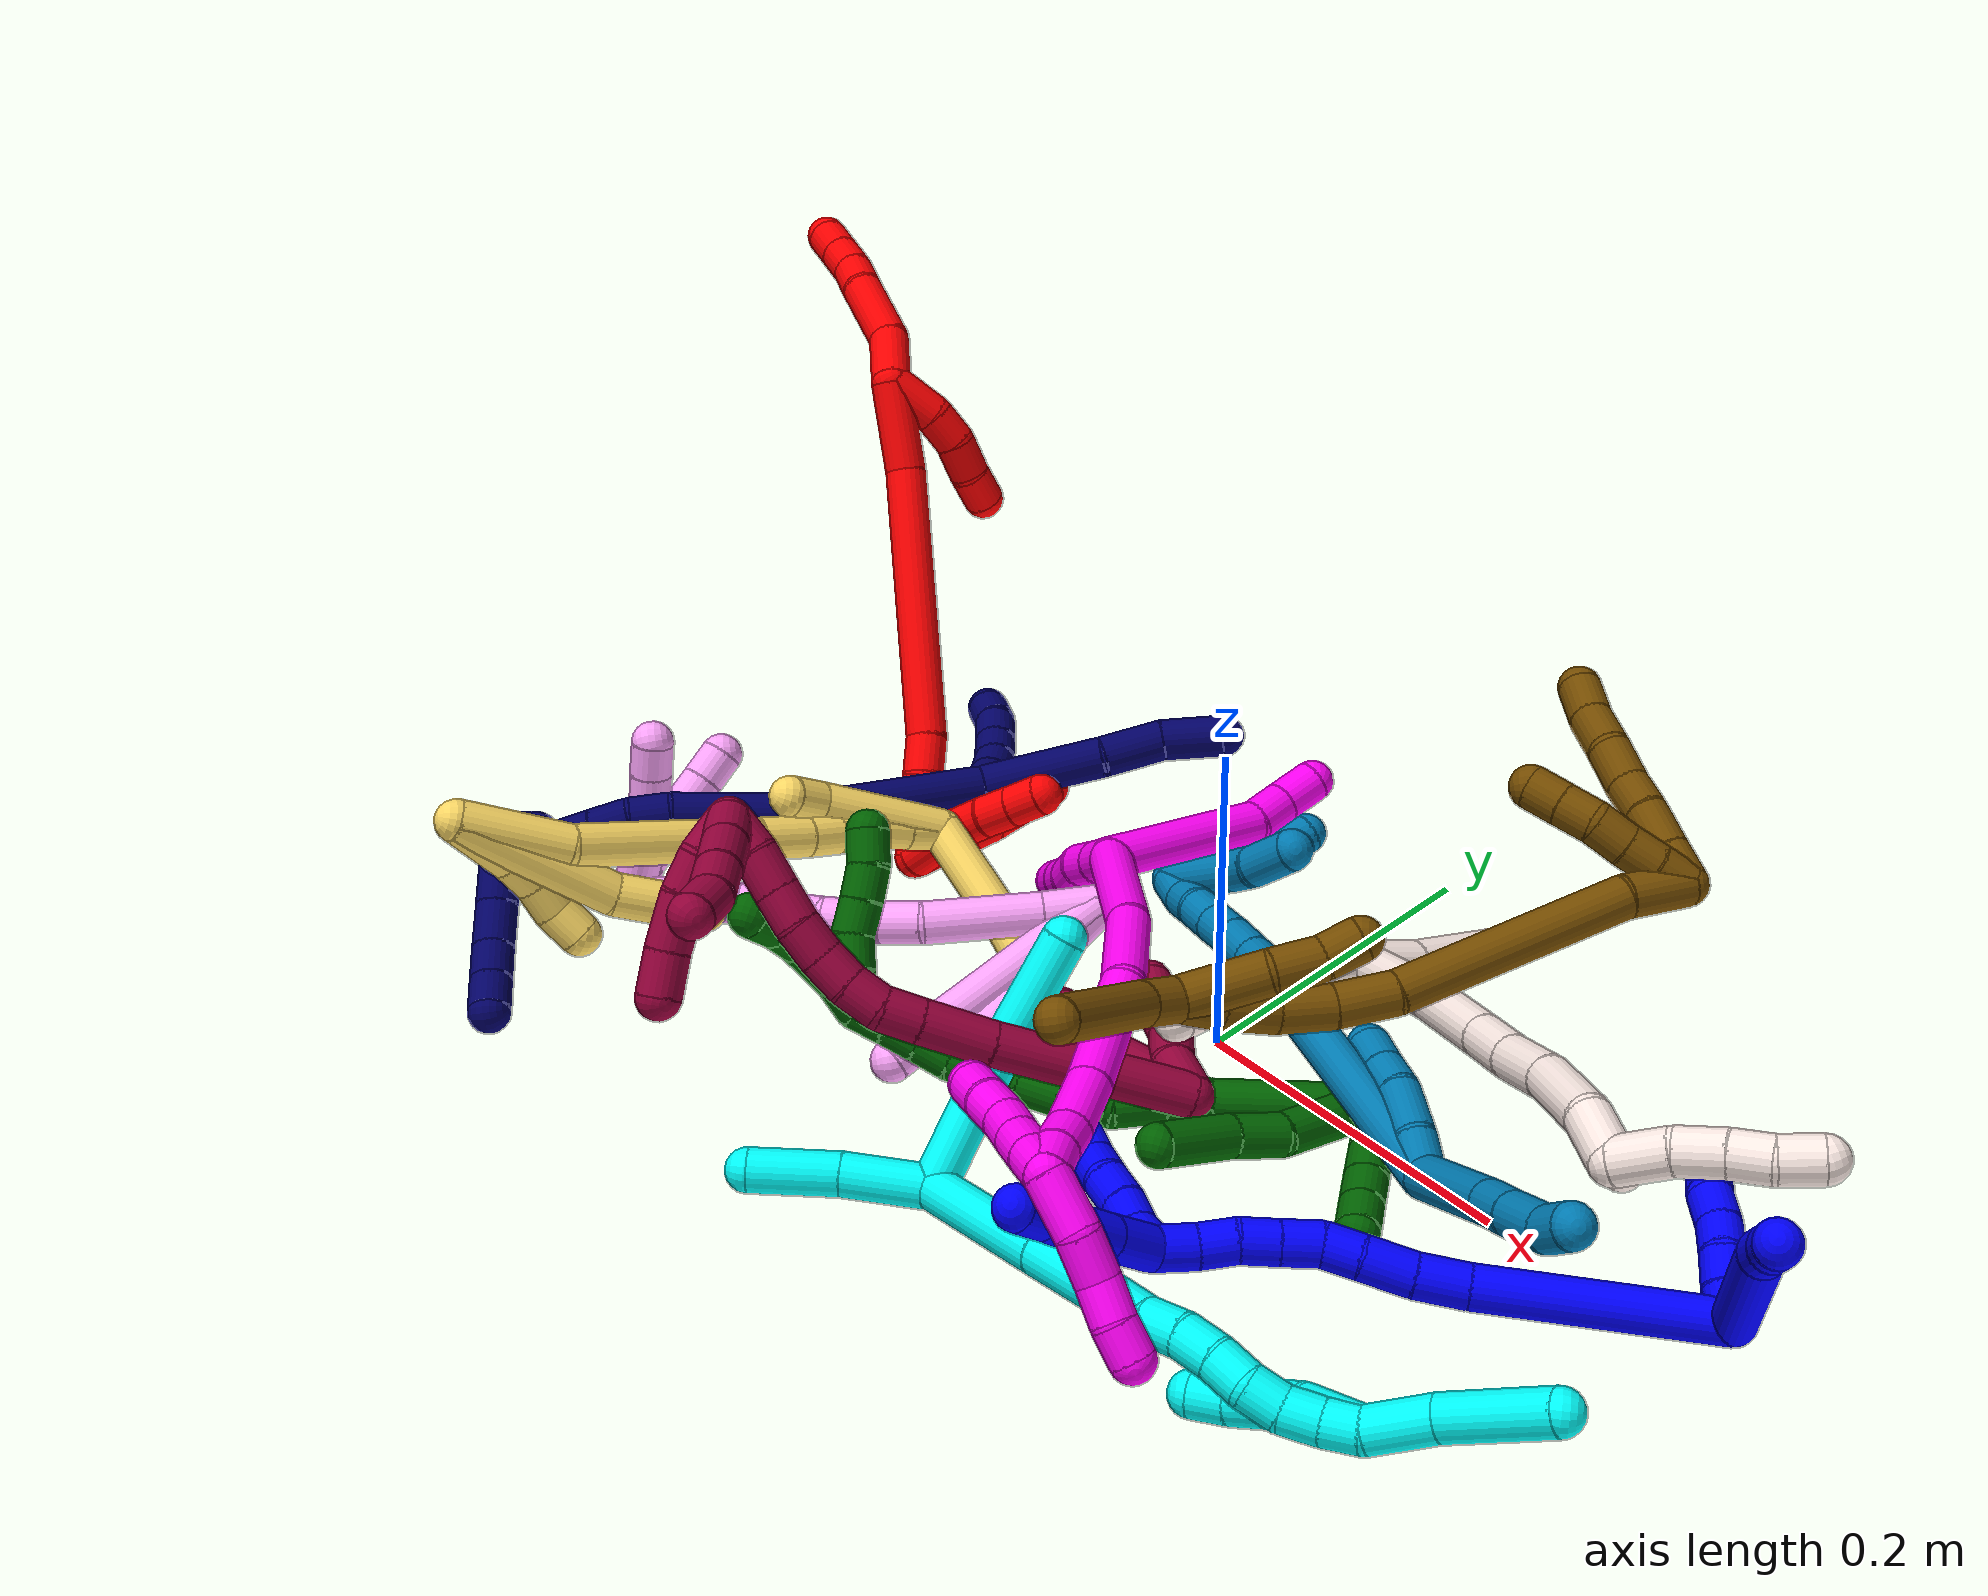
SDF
<sdf version="1.7">
 <world name="default">
  <plugin name="TubeGeneratorPlugin" filename="libtube_generator_plugin.so"/>
  <model name="photoneo_s_sensor">
   <static>1</static>
   <pose>0 0 2 1.57079 1.57079 3.14159</pose>
   <link name="link">
    <inertial><mass>0.1</mass></inertial>
    <sensor name="sensor" type="depth">
     <update_rate>30</update_rate>
     <camera>
      <horizontal_fov>1.22</horizontal_fov>
      <image><width>1920</width><height>1200</height><format>B8G8R8</format></image>
      <clip><near>0.1</near><far>4</far></clip>
      <depth_camera><output>points</output></depth_camera>
     </camera>
     <plugin name="camera_plugin" filename="libgazebo_ros_depth_camera.so">
      <baseline>0.2</baseline>
      <alwaysOn>1</alwaysOn>
      <updateRate>0.0</updateRate>
      <cameraName>camera_ir</cameraName>
      <imageTopicName>/camera/color/image_raw</imageTopicName>
      <cameraInfoTopicName>/camera/color/camera_info</cameraInfoTopicName>
      <depthImageTopicName>/camera/depth/image_raw</depthImageTopicName>
      <depthImageCameraInfoTopicName>/camera/depth/camera_info</depthImageCameraInfoTopicName>
      <pointCloudTopicName>/camera/depth/points</pointCloudTopicName>
      <frameName>fr_optical</frameName>
      <pointCloudCutoff>0.1</pointCloudCutoff>
      <pointCloudCutoffMax>2.0</pointCloudCutoffMax>
      <distortionK1>0</distortionK1>
      <distortionK2>0</distortionK2>
      <distortionK3>0</distortionK3>
      <distortionT1>0</distortionT1>
      <distortionT2>0</distortionT2>
      <CxPrime>0</CxPrime>
      <Cx>0</Cx>
      <Cy>0</Cy>
      <focalLength>0</focalLength>
      <hackBaseline>0</hackBaseline>
     </plugin>
    </sensor>
   </link>
  </model>
  <gravity>0 0 -9.8</gravity>
  <magnetic_field>6e-06 2.3e-05 -4.2e-05</magnetic_field>
  <atmosphere type="adiabatic"/>
  <physics name="default_physics" default="0" type="ode">
   <max_step_size>0.003</max_step_size>
   <real_time_factor>1</real_time_factor>
   <real_time_update_rate>1000</real_time_update_rate>
   <max_contacts>10000</max_contacts>
   <ode>
    <solver>
     <type>quick</type>
     <iters>100</iters>
     <sor>1.3</sor>
     <use_dynamic_moi_rescaling>0</use_dynamic_moi_rescaling>
    </solver>
    <constraints>
     <contact_max_correcting_vel>0</contact_max_correcting_vel>
     <contact_surface_layer>0.001</contact_surface_layer>
     <cfm>0</cfm>
     <erp>0.2</erp>
    </constraints>
   </ode>
  </physics>
  <scene><ambient>0.4 0.4 0.4 1</ambient><background>0.7 0.7 0.7 1</background><shadows>0</shadows></scene>
  <audio><device>default</device></audio>
  <spherical_coordinates>
   <surface_model>EARTH_WGS84</surface_model>
   <latitude_deg>0</latitude_deg>
   <longitude_deg>0</longitude_deg>
   <elevation>0</elevation>
   <heading_deg>0</heading_deg>
  </spherical_coordinates>
  <model name="bin">
   <static>1</static>
   <link name="bottom">
    <collision name="collision-bottom">
     <pose>0 0 -0.01 0 -0 0</pose>
     <geometry><box><size>0.8 0.6 0.02</size></box></geometry>
     <surface>
      <friction><ode><mu>100</mu><mu2>100</mu2></ode></friction>
      <contact><collide_bitmask>65535</collide_bitmask></contact>
     </surface>
    </collision>
   </link>
   <link name="west_wall">
    <collision name="collision-west_wall">
     <pose>-0.41 0 0.1 0 -0 0</pose>
     <geometry><box><size>0.02 0.6 0.2</size></box></geometry>
     <surface>
      <friction><ode><mu>100</mu><mu2>100</mu2></ode></friction>
      <contact><collide_bitmask>65535</collide_bitmask></contact>
     </surface>
    </collision>
   </link>
   <link name="east_wall">
    <collision name="collision-east_wall">
     <pose>0.41 0 0.1 0 -0 0</pose>
     <geometry><box><size>0.02 0.6 0.2</size></box></geometry>
     <surface>
      <friction><ode><mu>100</mu><mu2>100</mu2></ode></friction>
      <contact><collide_bitmask>65535</collide_bitmask></contact>
     </surface>
    </collision>
   </link>
   <link name="south_wall">
    <collision name="collision-south_wall">
     <pose>0 -0.31 0.1 0 -0 0</pose>
     <geometry><box><size>0.8 0.02 0.2</size></box></geometry>
     <surface>
      <friction><ode><mu>100</mu><mu2>100</mu2></ode></friction>
      <contact><collide_bitmask>65535</collide_bitmask></contact>
     </surface>
    </collision>
   </link>
   <link name="north_wall">
    <collision name="collision-north_wall">
     <pose>0 0.31 0.1 0 -0 0</pose>
     <geometry><box><size>0.8 0.02 0.2</size></box></geometry>
     <surface>
      <friction><ode><mu>100</mu><mu2>100</mu2></ode></friction>
      <contact><collide_bitmask>65535</collide_bitmask></contact>
     </surface>
    </collision>
   </link>
  </model>
  <model name="1">
   <static>0</static>
   <link name="1">
    <collision name="collision-cylinder-e_1_2_8">
     <pose>0.010326 0.001649 -0.052721 -3.11034 0.19332 -2.82194</pose>
     <geometry><cylinder><radius>0.0125</radius><length>0.107497</length></cylinder></geometry>
     <surface>
      <friction><ode><mu>1.16</mu><mu2>1.16</mu2><slip1>0</slip1><slip2>0</slip2></ode></friction>
      <contact><ode><kp>1e+06</kp><kd>1</kd><max_vel>0</max_vel><min_depth>0.001</min_depth></ode></contact>
     </surface>
    </collision>
    <visual name="visual-cylinder-e_1_2_8">
     <pose>0.010326 0.001649 -0.052721 -3.11034 0.19332 -2.82194</pose>
     <geometry><cylinder><radius>0.0125</radius><length>0.107497</length></cylinder></geometry>
     <material><ambient>0 0 1 1</ambient></material>
    </visual>
    <collision name="collision-cylinder-e_2_8_9">
     <pose>0.021833 0.005676 -0.115765 -2.91504 0.110982 -0.90843</pose>
     <geometry><cylinder><radius>0.0125</radius><length>0.021317</length></cylinder></geometry>
     <surface>
      <friction><ode><mu>1.16</mu><mu2>1.16</mu2><slip1>0</slip1><slip2>0</slip2></ode></friction>
      <contact><ode><kp>1e+06</kp><kd>1</kd><max_vel>0</max_vel><min_depth>0.001</min_depth></ode></contact>
     </surface>
    </collision>
    <visual name="visual-cylinder-e_2_8_9">
     <pose>0.021833 0.005676 -0.115765 -2.91504 0.110982 -0.90843</pose>
     <geometry><cylinder><radius>0.0125</radius><length>0.021317</length></cylinder></geometry>
     <material><ambient>0 0 1 1</ambient></material>
    </visual>
    <collision name="collision-cylinder-e_3_9_6">
     <pose>0.023026 0.009979 -0.136504 -2.95907 0.001272 -0.013897</pose>
     <geometry><cylinder><radius>0.0125</radius><length>0.021186</length></cylinder></geometry>
     <surface>
      <friction><ode><mu>1.16</mu><mu2>1.16</mu2><slip1>0</slip1><slip2>0</slip2></ode></friction>
      <contact><ode><kp>1e+06</kp><kd>1</kd><max_vel>0</max_vel><min_depth>0.001</min_depth></ode></contact>
     </surface>
    </collision>
    <visual name="visual-cylinder-e_3_9_6">
     <pose>0.023026 0.009979 -0.136504 -2.95907 0.001272 -0.013897</pose>
     <geometry><cylinder><radius>0.0125</radius><length>0.021186</length></cylinder></geometry>
     <material><ambient>0 0 1 1</ambient></material>
    </visual>
    <collision name="collision-cylinder-e_1_2_10">
     <pose>0.005636 -0.007723 0.00293 1.20825 0.598791 0.419823</pose>
     <geometry><cylinder><radius>0.0125</radius><length>0.02</length></cylinder></geometry>
     <surface>
      <friction><ode><mu>1.16</mu><mu2>1.16</mu2><slip1>0</slip1><slip2>0</slip2></ode></friction>
      <contact><ode><kp>1e+06</kp><kd>1</kd><max_vel>0</max_vel><min_depth>0.001</min_depth></ode></contact>
     </surface>
    </collision>
    <visual name="visual-cylinder-e_1_2_10">
     <pose>0.005636 -0.007723 0.00293 1.20825 0.598791 0.419823</pose>
     <geometry><cylinder><radius>0.0125</radius><length>0.02</length></cylinder></geometry>
     <material><ambient>0 0 1 1</ambient></material>
    </visual>
    <collision name="collision-cylinder-e_2_10_11">
     <pose>0.018043 -0.022184 0.00882 1.15665 0.743735 0.498593</pose>
     <geometry><cylinder><radius>0.0125</radius><length>0.02</length></cylinder></geometry>
     <surface>
      <friction><ode><mu>1.16</mu><mu2>1.16</mu2><slip1>0</slip1><slip2>0</slip2></ode></friction>
      <contact><ode><kp>1e+06</kp><kd>1</kd><max_vel>0</max_vel><min_depth>0.001</min_depth></ode></contact>
     </surface>
    </collision>
    <visual name="visual-cylinder-e_2_10_11">
     <pose>0.018043 -0.022184 0.00882 1.15665 0.743735 0.498593</pose>
     <geometry><cylinder><radius>0.0125</radius><length>0.02</length></cylinder></geometry>
     <material><ambient>0 0 1 1</ambient></material>
    </visual>
    <collision name="collision-cylinder-e_3_11_12">
     <pose>0.030677 -0.035381 0.016669 0.923166 0.626558 0.31953</pose>
     <geometry><cylinder><radius>0.0125</radius><length>0.02</length></cylinder></geometry>
     <surface>
      <friction><ode><mu>1.16</mu><mu2>1.16</mu2><slip1>0</slip1><slip2>0</slip2></ode></friction>
      <contact><ode><kp>1e+06</kp><kd>1</kd><max_vel>0</max_vel><min_depth>0.001</min_depth></ode></contact>
     </surface>
    </collision>
    <visual name="visual-cylinder-e_3_11_12">
     <pose>0.030677 -0.035381 0.016669 0.923166 0.626558 0.31953</pose>
     <geometry><cylinder><radius>0.0125</radius><length>0.02</length></cylinder></geometry>
     <material><ambient>0 0 1 1</ambient></material>
    </visual>
    <collision name="collision-cylinder-e_4_12_13">
     <pose>0.041502 -0.049475 0.025692 1.07426 0.519168 0.313723</pose>
     <geometry><cylinder><radius>0.0125</radius><length>0.02</length></cylinder></geometry>
     <surface>
      <friction><ode><mu>1.16</mu><mu2>1.16</mu2><slip1>0</slip1><slip2>0</slip2></ode></friction>
      <contact><ode><kp>1e+06</kp><kd>1</kd><max_vel>0</max_vel><min_depth>0.001</min_depth></ode></contact>
     </surface>
    </collision>
    <visual name="visual-cylinder-e_4_12_13">
     <pose>0.041502 -0.049475 0.025692 1.07426 0.519168 0.313723</pose>
     <geometry><cylinder><radius>0.0125</radius><length>0.02</length></cylinder></geometry>
     <material><ambient>0 0 1 1</ambient></material>
    </visual>
    <collision name="collision-cylinder-e_5_13_5">
     <pose>0.052062 -0.062393 0.036211 0.691429 0.59416 0.219644</pose>
     <geometry><cylinder><radius>0.0125</radius><length>0.02</length></cylinder></geometry>
     <surface>
      <friction><ode><mu>1.16</mu><mu2>1.16</mu2><slip1>0</slip1><slip2>0</slip2></ode></friction>
      <contact><ode><kp>1e+06</kp><kd>1</kd><max_vel>0</max_vel><min_depth>0.001</min_depth></ode></contact>
     </surface>
    </collision>
    <visual name="visual-cylinder-e_5_13_5">
     <pose>0.052062 -0.062393 0.036211 0.691429 0.59416 0.219644</pose>
     <geometry><cylinder><radius>0.0125</radius><length>0.02</length></cylinder></geometry>
     <material><ambient>0 0 1 1</ambient></material>
    </visual>
    <collision name="collision-cylinder-e_1_2_14">
     <pose>-0.038882 -0.053399 -0.009232 1.74199 -0.622368 -0.729808</pose>
     <geometry><cylinder><radius>0.0125</radius><length>0.133394</length></cylinder></geometry>
     <surface>
      <friction><ode><mu>1.16</mu><mu2>1.16</mu2><slip1>0</slip1><slip2>0</slip2></ode></friction>
      <contact><ode><kp>1e+06</kp><kd>1</kd><max_vel>0</max_vel><min_depth>0.001</min_depth></ode></contact>
     </surface>
    </collision>
    <visual name="visual-cylinder-e_1_2_14">
     <pose>-0.038882 -0.053399 -0.009232 1.74199 -0.622368 -0.729808</pose>
     <geometry><cylinder><radius>0.0125</radius><length>0.133394</length></cylinder></geometry>
     <material><ambient>0 0 1 1</ambient></material>
    </visual>
    <collision name="collision-cylinder-e_2_14_15">
     <pose>-0.085407 -0.118581 -0.021645 1.83441 -0.55953 -0.717752</pose>
     <geometry><cylinder><radius>0.0125</radius><length>0.028801</length></cylinder></geometry>
     <surface>
      <friction><ode><mu>1.16</mu><mu2>1.16</mu2><slip1>0</slip1><slip2>0</slip2></ode></friction>
      <contact><ode><kp>1e+06</kp><kd>1</kd><max_vel>0</max_vel><min_depth>0.001</min_depth></ode></contact>
     </surface>
    </collision>
    <visual name="visual-cylinder-e_2_14_15">
     <pose>-0.085407 -0.118581 -0.021645 1.83441 -0.55953 -0.717752</pose>
     <geometry><cylinder><radius>0.0125</radius><length>0.028801</length></cylinder></geometry>
     <material><ambient>0 0 1 1</ambient></material>
    </visual>
    <collision name="collision-cylinder-e_3_15_16">
     <pose>-0.099001 -0.142675 -0.028671 1.87362 -0.432277 -0.580411</pose>
     <geometry><cylinder><radius>0.0125</radius><length>0.028409</length></cylinder></geometry>
     <surface>
      <friction><ode><mu>1.16</mu><mu2>1.16</mu2><slip1>0</slip1><slip2>0</slip2></ode></friction>
      <contact><ode><kp>1e+06</kp><kd>1</kd><max_vel>0</max_vel><min_depth>0.001</min_depth></ode></contact>
     </surface>
    </collision>
    <visual name="visual-cylinder-e_3_15_16">
     <pose>-0.099001 -0.142675 -0.028671 1.87362 -0.432277 -0.580411</pose>
     <geometry><cylinder><radius>0.0125</radius><length>0.028409</length></cylinder></geometry>
     <material><ambient>0 0 1 1</ambient></material>
    </visual>
    <collision name="collision-cylinder-e_4_16_17">
     <pose>-0.109331 -0.164243 -0.034088 1.73888 -0.436407 -0.513467</pose>
     <geometry><cylinder><radius>0.0125</radius><length>0.02072</length></cylinder></geometry>
     <surface>
      <friction><ode><mu>1.16</mu><mu2>1.16</mu2><slip1>0</slip1><slip2>0</slip2></ode></friction>
      <contact><ode><kp>1e+06</kp><kd>1</kd><max_vel>0</max_vel><min_depth>0.001</min_depth></ode></contact>
     </surface>
    </collision>
    <visual name="visual-cylinder-e_4_16_17">
     <pose>-0.109331 -0.164243 -0.034088 1.73888 -0.436407 -0.513467</pose>
     <geometry><cylinder><radius>0.0125</radius><length>0.02072</length></cylinder></geometry>
     <material><ambient>0 0 1 1</ambient></material>
    </visual>
    <collision name="collision-cylinder-e_5_17_18">
     <pose>-0.121162 -0.181348 -0.038668 1.93691 -0.725302 -1.00851</pose>
     <geometry><cylinder><radius>0.0125</radius><length>0.022467</length></cylinder></geometry>
     <surface>
      <friction><ode><mu>1.16</mu><mu2>1.16</mu2><slip1>0</slip1><slip2>0</slip2></ode></friction>
      <contact><ode><kp>1e+06</kp><kd>1</kd><max_vel>0</max_vel><min_depth>0.001</min_depth></ode></contact>
     </surface>
    </collision>
    <visual name="visual-cylinder-e_5_17_18">
     <pose>-0.121162 -0.181348 -0.038668 1.93691 -0.725302 -1.00851</pose>
     <geometry><cylinder><radius>0.0125</radius><length>0.022467</length></cylinder></geometry>
     <material><ambient>0 0 1 1</ambient></material>
    </visual>
    <collision name="collision-cylinder-e_6_18_19">
     <pose>-0.135507 -0.196636 -0.044578 1.94259 -0.712109 -0.996746</pose>
     <geometry><cylinder><radius>0.0125</radius><length>0.021097</length></cylinder></geometry>
     <surface>
      <friction><ode><mu>1.16</mu><mu2>1.16</mu2><slip1>0</slip1><slip2>0</slip2></ode></friction>
      <contact><ode><kp>1e+06</kp><kd>1</kd><max_vel>0</max_vel><min_depth>0.001</min_depth></ode></contact>
     </surface>
    </collision>
    <visual name="visual-cylinder-e_6_18_19">
     <pose>-0.135507 -0.196636 -0.044578 1.94259 -0.712109 -0.996746</pose>
     <geometry><cylinder><radius>0.0125</radius><length>0.021097</length></cylinder></geometry>
     <material><ambient>0 0 1 1</ambient></material>
    </visual>
    <collision name="collision-cylinder-e_7_19_20">
     <pose>-0.150844 -0.210384 -0.049524 1.88433 -0.905075 -1.17888</pose>
     <geometry><cylinder><radius>0.0125</radius><length>0.021475</length></cylinder></geometry>
     <surface>
      <friction><ode><mu>1.16</mu><mu2>1.16</mu2><slip1>0</slip1><slip2>0</slip2></ode></friction>
      <contact><ode><kp>1e+06</kp><kd>1</kd><max_vel>0</max_vel><min_depth>0.001</min_depth></ode></contact>
     </surface>
    </collision>
    <visual name="visual-cylinder-e_7_19_20">
     <pose>-0.150844 -0.210384 -0.049524 1.88433 -0.905075 -1.17888</pose>
     <geometry><cylinder><radius>0.0125</radius><length>0.021475</length></cylinder></geometry>
     <material><ambient>0 0 1 1</ambient></material>
    </visual>
    <collision name="collision-cylinder-e_8_20_1">
     <pose>-0.167626 -0.223656 -0.056227 2.16031 -0.783032 -1.31584</pose>
     <geometry><cylinder><radius>0.0125</radius><length>0.023637</length></cylinder></geometry>
     <surface>
      <friction><ode><mu>1.16</mu><mu2>1.16</mu2><slip1>0</slip1><slip2>0</slip2></ode></friction>
      <contact><ode><kp>1e+06</kp><kd>1</kd><max_vel>0</max_vel><min_depth>0.001</min_depth></ode></contact>
     </surface>
    </collision>
    <visual name="visual-cylinder-e_8_20_1">
     <pose>-0.167626 -0.223656 -0.056227 2.16031 -0.783032 -1.31584</pose>
     <geometry><cylinder><radius>0.0125</radius><length>0.023637</length></cylinder></geometry>
     <material><ambient>0 0 1 1</ambient></material>
    </visual>
    <collision name="collision-cylinder-e_1_1_21">
     <pose>-0.175272 -0.238605 -0.054906 0.928205 0.069159 0.034629</pose>
     <geometry><cylinder><radius>0.0125</radius><length>0.02</length></cylinder></geometry>
     <surface>
      <friction><ode><mu>1.16</mu><mu2>1.16</mu2><slip1>0</slip1><slip2>0</slip2></ode></friction>
      <contact><ode><kp>1e+06</kp><kd>1</kd><max_vel>0</max_vel><min_depth>0.001</min_depth></ode></contact>
     </surface>
    </collision>
    <visual name="visual-cylinder-e_1_1_21">
     <pose>-0.175272 -0.238605 -0.054906 0.928205 0.069159 0.034629</pose>
     <geometry><cylinder><radius>0.0125</radius><length>0.02</length></cylinder></geometry>
     <material><ambient>0 0 1 1</ambient></material>
    </visual>
    <collision name="collision-cylinder-e_2_21_22">
     <pose>-0.171792 -0.255476 -0.045283 1.1816 0.282714 0.190317</pose>
     <geometry><cylinder><radius>0.0125</radius><length>0.02</length></cylinder></geometry>
     <surface>
      <friction><ode><mu>1.16</mu><mu2>1.16</mu2><slip1>0</slip1><slip2>0</slip2></ode></friction>
      <contact><ode><kp>1e+06</kp><kd>1</kd><max_vel>0</max_vel><min_depth>0.001</min_depth></ode></contact>
     </surface>
    </collision>
    <visual name="visual-cylinder-e_2_21_22">
     <pose>-0.171792 -0.255476 -0.045283 1.1816 0.282714 0.190317</pose>
     <geometry><cylinder><radius>0.0125</radius><length>0.02</length></cylinder></geometry>
     <material><ambient>0 0 1 1</ambient></material>
    </visual>
    <collision name="collision-cylinder-e_3_22_23">
     <pose>-0.167508 -0.273599 -0.038114 1.20626 0.149946 0.103376</pose>
     <geometry><cylinder><radius>0.0125</radius><length>0.02</length></cylinder></geometry>
     <surface>
      <friction><ode><mu>1.16</mu><mu2>1.16</mu2><slip1>0</slip1><slip2>0</slip2></ode></friction>
      <contact><ode><kp>1e+06</kp><kd>1</kd><max_vel>0</max_vel><min_depth>0.001</min_depth></ode></contact>
     </surface>
    </collision>
    <visual name="visual-cylinder-e_3_22_23">
     <pose>-0.167508 -0.273599 -0.038114 1.20626 0.149946 0.103376</pose>
     <geometry><cylinder><radius>0.0125</radius><length>0.02</length></cylinder></geometry>
     <material><ambient>0 0 1 1</ambient></material>
    </visual>
    <collision name="collision-cylinder-e_4_23_24">
     <pose>-0.16441 -0.290866 -0.028847 0.949926 0.161103 0.082975</pose>
     <geometry><cylinder><radius>0.0125</radius><length>0.02</length></cylinder></geometry>
     <surface>
      <friction><ode><mu>1.16</mu><mu2>1.16</mu2><slip1>0</slip1><slip2>0</slip2></ode></friction>
      <contact><ode><kp>1e+06</kp><kd>1</kd><max_vel>0</max_vel><min_depth>0.001</min_depth></ode></contact>
     </surface>
    </collision>
    <visual name="visual-cylinder-e_4_23_24">
     <pose>-0.16441 -0.290866 -0.028847 0.949926 0.161103 0.082975</pose>
     <geometry><cylinder><radius>0.0125</radius><length>0.02</length></cylinder></geometry>
     <material><ambient>0 0 1 1</ambient></material>
    </visual>
    <collision name="collision-cylinder-e_5_24_4">
     <pose>-0.159992 -0.308021 -0.020141 1.25678 0.285244 0.207937</pose>
     <geometry><cylinder><radius>0.0125</radius><length>0.02</length></cylinder></geometry>
     <surface>
      <friction><ode><mu>1.16</mu><mu2>1.16</mu2><slip1>0</slip1><slip2>0</slip2></ode></friction>
      <contact><ode><kp>1e+06</kp><kd>1</kd><max_vel>0</max_vel><min_depth>0.001</min_depth></ode></contact>
     </surface>
    </collision>
    <visual name="visual-cylinder-e_5_24_4">
     <pose>-0.159992 -0.308021 -0.020141 1.25678 0.285244 0.207937</pose>
     <geometry><cylinder><radius>0.0125</radius><length>0.02</length></cylinder></geometry>
     <material><ambient>0 0 1 1</ambient></material>
    </visual>
    <collision name="collision-cylinder-e_1_1_25">
     <pose>-0.181681 -0.236797 -0.07493 2.72719 -0.356675 -1.4176</pose>
     <geometry><cylinder><radius>0.0125</radius><length>0.032751</length></cylinder></geometry>
     <surface>
      <friction><ode><mu>1.16</mu><mu2>1.16</mu2><slip1>0</slip1><slip2>0</slip2></ode></friction>
      <contact><ode><kp>1e+06</kp><kd>1</kd><max_vel>0</max_vel><min_depth>0.001</min_depth></ode></contact>
     </surface>
    </collision>
    <visual name="visual-cylinder-e_1_1_25">
     <pose>-0.181681 -0.236797 -0.07493 2.72719 -0.356675 -1.4176</pose>
     <geometry><cylinder><radius>0.0125</radius><length>0.032751</length></cylinder></geometry>
     <material><ambient>0 0 1 1</ambient></material>
    </visual>
    <collision name="collision-cylinder-e_2_25_26">
     <pose>-0.191547 -0.247809 -0.099295 2.70357 -0.349123 -1.34007</pose>
     <geometry><cylinder><radius>0.0125</radius><length>0.024253</length></cylinder></geometry>
     <surface>
      <friction><ode><mu>1.16</mu><mu2>1.16</mu2><slip1>0</slip1><slip2>0</slip2></ode></friction>
      <contact><ode><kp>1e+06</kp><kd>1</kd><max_vel>0</max_vel><min_depth>0.001</min_depth></ode></contact>
     </surface>
    </collision>
    <visual name="visual-cylinder-e_2_25_26">
     <pose>-0.191547 -0.247809 -0.099295 2.70357 -0.349123 -1.34007</pose>
     <geometry><cylinder><radius>0.0125</radius><length>0.024253</length></cylinder></geometry>
     <material><ambient>0 0 1 1</ambient></material>
    </visual>
    <collision name="collision-cylinder-e_3_26_27">
     <pose>-0.199058 -0.257507 -0.118755 2.65253 -0.314051 -1.13084</pose>
     <geometry><cylinder><radius>0.0125</radius><length>0.021775</length></cylinder></geometry>
     <surface>
      <friction><ode><mu>1.16</mu><mu2>1.16</mu2><slip1>0</slip1><slip2>0</slip2></ode></friction>
      <contact><ode><kp>1e+06</kp><kd>1</kd><max_vel>0</max_vel><min_depth>0.001</min_depth></ode></contact>
     </surface>
    </collision>
    <visual name="visual-cylinder-e_3_26_27">
     <pose>-0.199058 -0.257507 -0.118755 2.65253 -0.314051 -1.13084</pose>
     <geometry><cylinder><radius>0.0125</radius><length>0.021775</length></cylinder></geometry>
     <material><ambient>0 0 1 1</ambient></material>
    </visual>
    <collision name="collision-cylinder-e_4_27_3">
     <pose>-0.205668 -0.265922 -0.137353 2.78245 -0.310995 -1.42464</pose>
     <geometry><cylinder><radius>0.0125</radius><length>0.021222</length></cylinder></geometry>
     <surface>
      <friction><ode><mu>1.16</mu><mu2>1.16</mu2><slip1>0</slip1><slip2>0</slip2></ode></friction>
      <contact><ode><kp>1e+06</kp><kd>1</kd><max_vel>0</max_vel><min_depth>0.001</min_depth></ode></contact>
     </surface>
    </collision>
    <visual name="visual-cylinder-e_4_27_3">
     <pose>-0.205668 -0.265922 -0.137353 2.78245 -0.310995 -1.42464</pose>
     <geometry><cylinder><radius>0.0125</radius><length>0.021222</length></cylinder></geometry>
     <material><ambient>0 0 1 1</ambient></material>
    </visual>
    <collision name="collision-sphere-3">
     <pose>-0.208915 -0.269473 -0.146811 0 -0 0</pose>
     <geometry><sphere><radius>0.0125</radius></sphere></geometry>
     <surface>
      <friction><ode><mu>1.16</mu><mu2>1.16</mu2><slip1>0</slip1><slip2>0</slip2></ode></friction>
      <contact><ode><kp>1e+06</kp><kd>1</kd><max_vel>0</max_vel><min_depth>0.001</min_depth></ode></contact>
     </surface>
    </collision>
    <visual name="visual-sphere-3">
     <pose>-0.208915 -0.269473 -0.146811 0 -0 0</pose>
     <geometry><sphere><radius>0.0125</radius></sphere></geometry>
     <material><ambient>0 0 1 1</ambient></material>
    </visual>
    <collision name="collision-sphere-27">
     <pose>-0.202421 -0.262371 -0.127896 0 -0 0</pose>
     <geometry><sphere><radius>0.0125</radius></sphere></geometry>
     <surface>
      <friction><ode><mu>1.16</mu><mu2>1.16</mu2><slip1>0</slip1><slip2>0</slip2></ode></friction>
      <contact><ode><kp>1e+06</kp><kd>1</kd><max_vel>0</max_vel><min_depth>0.001</min_depth></ode></contact>
     </surface>
    </collision>
    <visual name="visual-sphere-27">
     <pose>-0.202421 -0.262371 -0.127896 0 -0 0</pose>
     <geometry><sphere><radius>0.0125</radius></sphere></geometry>
     <material><ambient>0 0 1 1</ambient></material>
    </visual>
    <collision name="collision-sphere-26">
     <pose>-0.195695 -0.252642 -0.109614 0 -0 0</pose>
     <geometry><sphere><radius>0.0125</radius></sphere></geometry>
     <surface>
      <friction><ode><mu>1.16</mu><mu2>1.16</mu2><slip1>0</slip1><slip2>0</slip2></ode></friction>
      <contact><ode><kp>1e+06</kp><kd>1</kd><max_vel>0</max_vel><min_depth>0.001</min_depth></ode></contact>
     </surface>
    </collision>
    <visual name="visual-sphere-26">
     <pose>-0.195695 -0.252642 -0.109614 0 -0 0</pose>
     <geometry><sphere><radius>0.0125</radius></sphere></geometry>
     <material><ambient>0 0 1 1</ambient></material>
    </visual>
    <collision name="collision-sphere-25">
     <pose>-0.187399 -0.242976 -0.088976 0 -0 0</pose>
     <geometry><sphere><radius>0.0125</radius></sphere></geometry>
     <surface>
      <friction><ode><mu>1.16</mu><mu2>1.16</mu2><slip1>0</slip1><slip2>0</slip2></ode></friction>
      <contact><ode><kp>1e+06</kp><kd>1</kd><max_vel>0</max_vel><min_depth>0.001</min_depth></ode></contact>
     </surface>
    </collision>
    <visual name="visual-sphere-25">
     <pose>-0.187399 -0.242976 -0.088976 0 -0 0</pose>
     <geometry><sphere><radius>0.0125</radius></sphere></geometry>
     <material><ambient>0 0 1 1</ambient></material>
    </visual>
    <collision name="collision-sphere-4">
     <pose>-0.157178 -0.317147 -0.017177 0 -0 0</pose>
     <geometry><sphere><radius>0.0125</radius></sphere></geometry>
     <surface>
      <friction><ode><mu>1.16</mu><mu2>1.16</mu2><slip1>0</slip1><slip2>0</slip2></ode></friction>
      <contact><ode><kp>1e+06</kp><kd>1</kd><max_vel>0</max_vel><min_depth>0.001</min_depth></ode></contact>
     </surface>
    </collision>
    <visual name="visual-sphere-4">
     <pose>-0.157178 -0.317147 -0.017177 0 -0 0</pose>
     <geometry><sphere><radius>0.0125</radius></sphere></geometry>
     <material><ambient>0 0 1 1</ambient></material>
    </visual>
    <collision name="collision-sphere-24">
     <pose>-0.162806 -0.298894 -0.023105 0 -0 0</pose>
     <geometry><sphere><radius>0.0125</radius></sphere></geometry>
     <surface>
      <friction><ode><mu>1.16</mu><mu2>1.16</mu2><slip1>0</slip1><slip2>0</slip2></ode></friction>
      <contact><ode><kp>1e+06</kp><kd>1</kd><max_vel>0</max_vel><min_depth>0.001</min_depth></ode></contact>
     </surface>
    </collision>
    <visual name="visual-sphere-24">
     <pose>-0.162806 -0.298894 -0.023105 0 -0 0</pose>
     <geometry><sphere><radius>0.0125</radius></sphere></geometry>
     <material><ambient>0 0 1 1</ambient></material>
    </visual>
    <collision name="collision-sphere-23">
     <pose>-0.166014 -0.282837 -0.034589 0 -0 0</pose>
     <geometry><sphere><radius>0.0125</radius></sphere></geometry>
     <surface>
      <friction><ode><mu>1.16</mu><mu2>1.16</mu2><slip1>0</slip1><slip2>0</slip2></ode></friction>
      <contact><ode><kp>1e+06</kp><kd>1</kd><max_vel>0</max_vel><min_depth>0.001</min_depth></ode></contact>
     </surface>
    </collision>
    <visual name="visual-sphere-23">
     <pose>-0.166014 -0.282837 -0.034589 0 -0 0</pose>
     <geometry><sphere><radius>0.0125</radius></sphere></geometry>
     <material><ambient>0 0 1 1</ambient></material>
    </visual>
    <collision name="collision-sphere-22">
     <pose>-0.169002 -0.264361 -0.04164 0 -0 0</pose>
     <geometry><sphere><radius>0.0125</radius></sphere></geometry>
     <surface>
      <friction><ode><mu>1.16</mu><mu2>1.16</mu2><slip1>0</slip1><slip2>0</slip2></ode></friction>
      <contact><ode><kp>1e+06</kp><kd>1</kd><max_vel>0</max_vel><min_depth>0.001</min_depth></ode></contact>
     </surface>
    </collision>
    <visual name="visual-sphere-22">
     <pose>-0.169002 -0.264361 -0.04164 0 -0 0</pose>
     <geometry><sphere><radius>0.0125</radius></sphere></geometry>
     <material><ambient>0 0 1 1</ambient></material>
    </visual>
    <collision name="collision-sphere-21">
     <pose>-0.174581 -0.246591 -0.048927 0 -0 0</pose>
     <geometry><sphere><radius>0.0125</radius></sphere></geometry>
     <surface>
      <friction><ode><mu>1.16</mu><mu2>1.16</mu2><slip1>0</slip1><slip2>0</slip2></ode></friction>
      <contact><ode><kp>1e+06</kp><kd>1</kd><max_vel>0</max_vel><min_depth>0.001</min_depth></ode></contact>
     </surface>
    </collision>
    <visual name="visual-sphere-21">
     <pose>-0.174581 -0.246591 -0.048927 0 -0 0</pose>
     <geometry><sphere><radius>0.0125</radius></sphere></geometry>
     <material><ambient>0 0 1 1</ambient></material>
    </visual>
    <collision name="collision-sphere-1">
     <pose>-0.175963 -0.230619 -0.060884 0 -0 0</pose>
     <geometry><sphere><radius>0.0125</radius></sphere></geometry>
     <surface>
      <friction><ode><mu>1.16</mu><mu2>1.16</mu2><slip1>0</slip1><slip2>0</slip2></ode></friction>
      <contact><ode><kp>1e+06</kp><kd>1</kd><max_vel>0</max_vel><min_depth>0.001</min_depth></ode></contact>
     </surface>
    </collision>
    <visual name="visual-sphere-1">
     <pose>-0.175963 -0.230619 -0.060884 0 -0 0</pose>
     <geometry><sphere><radius>0.0125</radius></sphere></geometry>
     <material><ambient>0 0 1 1</ambient></material>
    </visual>
    <collision name="collision-sphere-11">
     <pose>0.024814 -0.028921 0.011782 0 -0 0</pose>
     <geometry><sphere><radius>0.0125</radius></sphere></geometry>
     <surface>
      <friction><ode><mu>1.16</mu><mu2>1.16</mu2><slip1>0</slip1><slip2>0</slip2></ode></friction>
      <contact><ode><kp>1e+06</kp><kd>1</kd><max_vel>0</max_vel><min_depth>0.001</min_depth></ode></contact>
     </surface>
    </collision>
    <visual name="visual-sphere-11">
     <pose>0.024814 -0.028921 0.011782 0 -0 0</pose>
     <geometry><sphere><radius>0.0125</radius></sphere></geometry>
     <material><ambient>0 0 1 1</ambient></material>
    </visual>
    <collision name="collision-sphere-10">
     <pose>0.011273 -0.015446 0.005859 0 -0 0</pose>
     <geometry><sphere><radius>0.0125</radius></sphere></geometry>
     <surface>
      <friction><ode><mu>1.16</mu><mu2>1.16</mu2><slip1>0</slip1><slip2>0</slip2></ode></friction>
      <contact><ode><kp>1e+06</kp><kd>1</kd><max_vel>0</max_vel><min_depth>0.001</min_depth></ode></contact>
     </surface>
    </collision>
    <visual name="visual-sphere-10">
     <pose>0.011273 -0.015446 0.005859 0 -0 0</pose>
     <geometry><sphere><radius>0.0125</radius></sphere></geometry>
     <material><ambient>0 0 1 1</ambient></material>
    </visual>
    <collision name="collision-sphere-6">
     <pose>0.02304 0.011901 -0.146922 0 -0 0</pose>
     <geometry><sphere><radius>0.0125</radius></sphere></geometry>
     <surface>
      <friction><ode><mu>1.16</mu><mu2>1.16</mu2><slip1>0</slip1><slip2>0</slip2></ode></friction>
      <contact><ode><kp>1e+06</kp><kd>1</kd><max_vel>0</max_vel><min_depth>0.001</min_depth></ode></contact>
     </surface>
    </collision>
    <visual name="visual-sphere-6">
     <pose>0.02304 0.011901 -0.146922 0 -0 0</pose>
     <geometry><sphere><radius>0.0125</radius></sphere></geometry>
     <material><ambient>0 0 1 1</ambient></material>
    </visual>
    <collision name="collision-sphere-9">
     <pose>0.023013 0.008056 -0.126087 0 -0 0</pose>
     <geometry><sphere><radius>0.0125</radius></sphere></geometry>
     <surface>
      <friction><ode><mu>1.16</mu><mu2>1.16</mu2><slip1>0</slip1><slip2>0</slip2></ode></friction>
      <contact><ode><kp>1e+06</kp><kd>1</kd><max_vel>0</max_vel><min_depth>0.001</min_depth></ode></contact>
     </surface>
    </collision>
    <visual name="visual-sphere-9">
     <pose>0.023013 0.008056 -0.126087 0 -0 0</pose>
     <geometry><sphere><radius>0.0125</radius></sphere></geometry>
     <material><ambient>0 0 1 1</ambient></material>
    </visual>
    <collision name="collision-sphere-2">
     <geometry><sphere><radius>0.0125</radius></sphere></geometry>
     <surface>
      <friction><ode><mu>1.16</mu><mu2>1.16</mu2><slip1>0</slip1><slip2>0</slip2></ode></friction>
      <contact><ode><kp>1e+06</kp><kd>1</kd><max_vel>0</max_vel><min_depth>0.001</min_depth></ode></contact>
     </surface>
    </collision>
    <visual name="visual-sphere-2">
     <geometry><sphere><radius>0.0125</radius></sphere></geometry>
     <material><ambient>0 0 1 1</ambient></material>
    </visual>
    <collision name="collision-sphere-19">
     <pose>-0.142399 -0.204076 -0.047479 0 -0 0</pose>
     <geometry><sphere><radius>0.0125</radius></sphere></geometry>
     <surface>
      <friction><ode><mu>1.16</mu><mu2>1.16</mu2><slip1>0</slip1><slip2>0</slip2></ode></friction>
      <contact><ode><kp>1e+06</kp><kd>1</kd><max_vel>0</max_vel><min_depth>0.001</min_depth></ode></contact>
     </surface>
    </collision>
    <visual name="visual-sphere-19">
     <pose>-0.142399 -0.204076 -0.047479 0 -0 0</pose>
     <geometry><sphere><radius>0.0125</radius></sphere></geometry>
     <material><ambient>0 0 1 1</ambient></material>
    </visual>
    <collision name="collision-sphere-8">
     <pose>0.020652 0.003297 -0.105443 0 -0 0</pose>
     <geometry><sphere><radius>0.0125</radius></sphere></geometry>
     <surface>
      <friction><ode><mu>1.16</mu><mu2>1.16</mu2><slip1>0</slip1><slip2>0</slip2></ode></friction>
      <contact><ode><kp>1e+06</kp><kd>1</kd><max_vel>0</max_vel><min_depth>0.001</min_depth></ode></contact>
     </surface>
    </collision>
    <visual name="visual-sphere-8">
     <pose>0.020652 0.003297 -0.105443 0 -0 0</pose>
     <geometry><sphere><radius>0.0125</radius></sphere></geometry>
     <material><ambient>0 0 1 1</ambient></material>
    </visual>
    <collision name="collision-sphere-12">
     <pose>0.036541 -0.041842 0.021556 0 -0 0</pose>
     <geometry><sphere><radius>0.0125</radius></sphere></geometry>
     <surface>
      <friction><ode><mu>1.16</mu><mu2>1.16</mu2><slip1>0</slip1><slip2>0</slip2></ode></friction>
      <contact><ode><kp>1e+06</kp><kd>1</kd><max_vel>0</max_vel><min_depth>0.001</min_depth></ode></contact>
     </surface>
    </collision>
    <visual name="visual-sphere-12">
     <pose>0.036541 -0.041842 0.021556 0 -0 0</pose>
     <geometry><sphere><radius>0.0125</radius></sphere></geometry>
     <material><ambient>0 0 1 1</ambient></material>
    </visual>
    <collision name="collision-sphere-13">
     <pose>0.046464 -0.057109 0.029828 0 -0 0</pose>
     <geometry><sphere><radius>0.0125</radius></sphere></geometry>
     <surface>
      <friction><ode><mu>1.16</mu><mu2>1.16</mu2><slip1>0</slip1><slip2>0</slip2></ode></friction>
      <contact><ode><kp>1e+06</kp><kd>1</kd><max_vel>0</max_vel><min_depth>0.001</min_depth></ode></contact>
     </surface>
    </collision>
    <visual name="visual-sphere-13">
     <pose>0.046464 -0.057109 0.029828 0 -0 0</pose>
     <geometry><sphere><radius>0.0125</radius></sphere></geometry>
     <material><ambient>0 0 1 1</ambient></material>
    </visual>
    <collision name="collision-sphere-5">
     <pose>0.05766 -0.067677 0.042594 0 -0 0</pose>
     <geometry><sphere><radius>0.0125</radius></sphere></geometry>
     <surface>
      <friction><ode><mu>1.16</mu><mu2>1.16</mu2><slip1>0</slip1><slip2>0</slip2></ode></friction>
      <contact><ode><kp>1e+06</kp><kd>1</kd><max_vel>0</max_vel><min_depth>0.001</min_depth></ode></contact>
     </surface>
    </collision>
    <visual name="visual-sphere-5">
     <pose>0.05766 -0.067677 0.042594 0 -0 0</pose>
     <geometry><sphere><radius>0.0125</radius></sphere></geometry>
     <material><ambient>0 0 1 1</ambient></material>
    </visual>
    <collision name="collision-sphere-14">
     <pose>-0.077763 -0.106798 -0.018464 0 -0 0</pose>
     <geometry><sphere><radius>0.0125</radius></sphere></geometry>
     <surface>
      <friction><ode><mu>1.16</mu><mu2>1.16</mu2><slip1>0</slip1><slip2>0</slip2></ode></friction>
      <contact><ode><kp>1e+06</kp><kd>1</kd><max_vel>0</max_vel><min_depth>0.001</min_depth></ode></contact>
     </surface>
    </collision>
    <visual name="visual-sphere-14">
     <pose>-0.077763 -0.106798 -0.018464 0 -0 0</pose>
     <geometry><sphere><radius>0.0125</radius></sphere></geometry>
     <material><ambient>0 0 1 1</ambient></material>
    </visual>
    <collision name="collision-sphere-15">
     <pose>-0.093051 -0.130364 -0.024825 0 -0 0</pose>
     <geometry><sphere><radius>0.0125</radius></sphere></geometry>
     <surface>
      <friction><ode><mu>1.16</mu><mu2>1.16</mu2><slip1>0</slip1><slip2>0</slip2></ode></friction>
      <contact><ode><kp>1e+06</kp><kd>1</kd><max_vel>0</max_vel><min_depth>0.001</min_depth></ode></contact>
     </surface>
    </collision>
    <visual name="visual-sphere-15">
     <pose>-0.093051 -0.130364 -0.024825 0 -0 0</pose>
     <geometry><sphere><radius>0.0125</radius></sphere></geometry>
     <material><ambient>0 0 1 1</ambient></material>
    </visual>
    <collision name="collision-sphere-16">
     <pose>-0.104952 -0.154986 -0.032517 0 -0 0</pose>
     <geometry><sphere><radius>0.0125</radius></sphere></geometry>
     <surface>
      <friction><ode><mu>1.16</mu><mu2>1.16</mu2><slip1>0</slip1><slip2>0</slip2></ode></friction>
      <contact><ode><kp>1e+06</kp><kd>1</kd><max_vel>0</max_vel><min_depth>0.001</min_depth></ode></contact>
     </surface>
    </collision>
    <visual name="visual-sphere-16">
     <pose>-0.104952 -0.154986 -0.032517 0 -0 0</pose>
     <geometry><sphere><radius>0.0125</radius></sphere></geometry>
     <material><ambient>0 0 1 1</ambient></material>
    </visual>
    <collision name="collision-sphere-17">
     <pose>-0.11371 -0.173499 -0.035659 0 -0 0</pose>
     <geometry><sphere><radius>0.0125</radius></sphere></geometry>
     <surface>
      <friction><ode><mu>1.16</mu><mu2>1.16</mu2><slip1>0</slip1><slip2>0</slip2></ode></friction>
      <contact><ode><kp>1e+06</kp><kd>1</kd><max_vel>0</max_vel><min_depth>0.001</min_depth></ode></contact>
     </surface>
    </collision>
    <visual name="visual-sphere-17">
     <pose>-0.11371 -0.173499 -0.035659 0 -0 0</pose>
     <geometry><sphere><radius>0.0125</radius></sphere></geometry>
     <material><ambient>0 0 1 1</ambient></material>
    </visual>
    <collision name="collision-sphere-18">
     <pose>-0.128614 -0.189197 -0.041677 0 -0 0</pose>
     <geometry><sphere><radius>0.0125</radius></sphere></geometry>
     <surface>
      <friction><ode><mu>1.16</mu><mu2>1.16</mu2><slip1>0</slip1><slip2>0</slip2></ode></friction>
      <contact><ode><kp>1e+06</kp><kd>1</kd><max_vel>0</max_vel><min_depth>0.001</min_depth></ode></contact>
     </surface>
    </collision>
    <visual name="visual-sphere-18">
     <pose>-0.128614 -0.189197 -0.041677 0 -0 0</pose>
     <geometry><sphere><radius>0.0125</radius></sphere></geometry>
     <material><ambient>0 0 1 1</ambient></material>
    </visual>
    <collision name="collision-sphere-20">
     <pose>-0.159289 -0.216693 -0.05157 0 -0 0</pose>
     <geometry><sphere><radius>0.0125</radius></sphere></geometry>
     <surface>
      <friction><ode><mu>1.16</mu><mu2>1.16</mu2><slip1>0</slip1><slip2>0</slip2></ode></friction>
      <contact><ode><kp>1e+06</kp><kd>1</kd><max_vel>0</max_vel><min_depth>0.001</min_depth></ode></contact>
     </surface>
    </collision>
    <visual name="visual-sphere-20">
     <pose>-0.159289 -0.216693 -0.05157 0 -0 0</pose>
     <geometry><sphere><radius>0.0125</radius></sphere></geometry>
     <material><ambient>0 0 1 1</ambient></material>
    </visual>
    <inertial>
     <pose>-0.075413 -0.12187 -0.041209 0 -0 0</pose>
     <mass>0.75</mass>
     <inertia>
      <ixx>-0.00012</ixx>
      <ixy>0</ixy>
      <ixz>0</ixz>
      <iyy>-2.8e-05</iyy>
      <iyz>0</iyz>
      <izz>0.000272</izz>
     </inertia>
    </inertial>
   </link>
   <pose>0.339873 0.023547 0.012032 -2.84183 -0.535983 1.43935</pose>
  </model>
  <model name="2">
   <static>0</static>
   <link name="2">
    <collision name="collision-cylinder-e_1_2_8">
     <pose>-9.7e-05 -0.019945 -0.002004 1.67094 -0.00486 -0.005373</pose>
     <geometry><cylinder><radius>0.0125</radius><length>0.040092</length></cylinder></geometry>
     <surface>
      <friction><ode><mu>1.16</mu><mu2>1.16</mu2><slip1>0</slip1><slip2>0</slip2></ode></friction>
      <contact><ode><kp>1e+06</kp><kd>1</kd><max_vel>0</max_vel><min_depth>0.001</min_depth></ode></contact>
     </surface>
    </collision>
    <visual name="visual-cylinder-e_1_2_8">
     <pose>-9.7e-05 -0.019945 -0.002004 1.67094 -0.00486 -0.005373</pose>
     <geometry><cylinder><radius>0.0125</radius><length>0.040092</length></cylinder></geometry>
     <material><ambient>1 0 0 1</ambient></material>
    </visual>
    <collision name="collision-cylinder-e_2_8_9">
     <pose>0.006709 -0.062251 -0.009934 1.82985 0.290047 0.375129</pose>
     <geometry><cylinder><radius>0.0125</radius><length>0.048281</length></cylinder></geometry>
     <surface>
      <friction><ode><mu>1.16</mu><mu2>1.16</mu2><slip1>0</slip1><slip2>0</slip2></ode></friction>
      <contact><ode><kp>1e+06</kp><kd>1</kd><max_vel>0</max_vel><min_depth>0.001</min_depth></ode></contact>
     </surface>
    </collision>
    <visual name="visual-cylinder-e_2_8_9">
     <pose>0.006709 -0.062251 -0.009934 1.82985 0.290047 0.375129</pose>
     <geometry><cylinder><radius>0.0125</radius><length>0.048281</length></cylinder></geometry>
     <material><ambient>1 0 0 1</ambient></material>
    </visual>
    <collision name="collision-cylinder-e_3_9_10">
     <pose>0.014912 -0.094696 -0.019395 1.90802 0.120933 0.170346</pose>
     <geometry><cylinder><radius>0.0125</radius><length>0.021531</length></cylinder></geometry>
     <surface>
      <friction><ode><mu>1.16</mu><mu2>1.16</mu2><slip1>0</slip1><slip2>0</slip2></ode></friction>
      <contact><ode><kp>1e+06</kp><kd>1</kd><max_vel>0</max_vel><min_depth>0.001</min_depth></ode></contact>
     </surface>
    </collision>
    <visual name="visual-cylinder-e_3_9_10">
     <pose>0.014912 -0.094696 -0.019395 1.90802 0.120933 0.170346</pose>
     <geometry><cylinder><radius>0.0125</radius><length>0.021531</length></cylinder></geometry>
     <material><ambient>1 0 0 1</ambient></material>
    </visual>
    <collision name="collision-cylinder-e_4_10_11">
     <pose>0.018845 -0.113642 -0.026755 1.97818 0.266491 0.402147</pose>
     <geometry><cylinder><radius>0.0125</radius><length>0.020006</length></cylinder></geometry>
     <surface>
      <friction><ode><mu>1.16</mu><mu2>1.16</mu2><slip1>0</slip1><slip2>0</slip2></ode></friction>
      <contact><ode><kp>1e+06</kp><kd>1</kd><max_vel>0</max_vel><min_depth>0.001</min_depth></ode></contact>
     </surface>
    </collision>
    <visual name="visual-cylinder-e_4_10_11">
     <pose>0.018845 -0.113642 -0.026755 1.97818 0.266491 0.402147</pose>
     <geometry><cylinder><radius>0.0125</radius><length>0.020006</length></cylinder></geometry>
     <material><ambient>1 0 0 1</ambient></material>
    </visual>
    <collision name="collision-cylinder-e_5_11_6">
     <pose>0.024376 -0.131378 -0.034283 1.96625 0.292504 0.435225</pose>
     <geometry><cylinder><radius>0.0125</radius><length>0.020089</length></cylinder></geometry>
     <surface>
      <friction><ode><mu>1.16</mu><mu2>1.16</mu2><slip1>0</slip1><slip2>0</slip2></ode></friction>
      <contact><ode><kp>1e+06</kp><kd>1</kd><max_vel>0</max_vel><min_depth>0.001</min_depth></ode></contact>
     </surface>
    </collision>
    <visual name="visual-cylinder-e_5_11_6">
     <pose>0.024376 -0.131378 -0.034283 1.96625 0.292504 0.435225</pose>
     <geometry><cylinder><radius>0.0125</radius><length>0.020089</length></cylinder></geometry>
     <material><ambient>1 0 0 1</ambient></material>
    </visual>
    <collision name="collision-cylinder-e_1_2_12">
     <pose>-0.015254 0.006025 0.001389 -1.34414 -1.18571 0.984087</pose>
     <geometry><cylinder><radius>0.0125</radius><length>0.03292</length></cylinder></geometry>
     <surface>
      <friction><ode><mu>1.16</mu><mu2>1.16</mu2><slip1>0</slip1><slip2>0</slip2></ode></friction>
      <contact><ode><kp>1e+06</kp><kd>1</kd><max_vel>0</max_vel><min_depth>0.001</min_depth></ode></contact>
     </surface>
    </collision>
    <visual name="visual-cylinder-e_1_2_12">
     <pose>-0.015254 0.006025 0.001389 -1.34414 -1.18571 0.984087</pose>
     <geometry><cylinder><radius>0.0125</radius><length>0.03292</length></cylinder></geometry>
     <material><ambient>1 0 0 1</ambient></material>
    </visual>
    <collision name="collision-cylinder-e_2_12_13">
     <pose>-0.040067 0.01636 0.000871 -1.98741 -1.11261 1.52492</pose>
     <geometry><cylinder><radius>0.0125</radius><length>0.021314</length></cylinder></geometry>
     <surface>
      <friction><ode><mu>1.16</mu><mu2>1.16</mu2><slip1>0</slip1><slip2>0</slip2></ode></friction>
      <contact><ode><kp>1e+06</kp><kd>1</kd><max_vel>0</max_vel><min_depth>0.001</min_depth></ode></contact>
     </surface>
    </collision>
    <visual name="visual-cylinder-e_2_12_13">
     <pose>-0.040067 0.01636 0.000871 -1.98741 -1.11261 1.52492</pose>
     <geometry><cylinder><radius>0.0125</radius><length>0.021314</length></cylinder></geometry>
     <material><ambient>1 0 0 1</ambient></material>
    </visual>
    <collision name="collision-cylinder-e_3_13_14">
     <pose>-0.058961 0.025286 -0.006088 -2.40129 -0.938333 1.83491</pose>
     <geometry><cylinder><radius>0.0125</radius><length>0.02315</length></cylinder></geometry>
     <surface>
      <friction><ode><mu>1.16</mu><mu2>1.16</mu2><slip1>0</slip1><slip2>0</slip2></ode></friction>
      <contact><ode><kp>1e+06</kp><kd>1</kd><max_vel>0</max_vel><min_depth>0.001</min_depth></ode></contact>
     </surface>
    </collision>
    <visual name="visual-cylinder-e_3_13_14">
     <pose>-0.058961 0.025286 -0.006088 -2.40129 -0.938333 1.83491</pose>
     <geometry><cylinder><radius>0.0125</radius><length>0.02315</length></cylinder></geometry>
     <material><ambient>1 0 0 1</ambient></material>
    </visual>
    <collision name="collision-cylinder-e_4_14_5">
     <pose>-0.078035 0.032022 -0.016482 -2.76373 -1.03756 2.49527</pose>
     <geometry><cylinder><radius>0.0125</radius><length>0.022616</length></cylinder></geometry>
     <surface>
      <friction><ode><mu>1.16</mu><mu2>1.16</mu2><slip1>0</slip1><slip2>0</slip2></ode></friction>
      <contact><ode><kp>1e+06</kp><kd>1</kd><max_vel>0</max_vel><min_depth>0.001</min_depth></ode></contact>
     </surface>
    </collision>
    <visual name="visual-cylinder-e_4_14_5">
     <pose>-0.078035 0.032022 -0.016482 -2.76373 -1.03756 2.49527</pose>
     <geometry><cylinder><radius>0.0125</radius><length>0.022616</length></cylinder></geometry>
     <material><ambient>1 0 0 1</ambient></material>
    </visual>
    <collision name="collision-cylinder-e_1_2_15">
     <pose>-0.013279 0.022299 -0.01025 -2.00167 -0.495946 0.752439</pose>
     <geometry><cylinder><radius>0.0125</radius><length>0.055808</length></cylinder></geometry>
     <surface>
      <friction><ode><mu>1.16</mu><mu2>1.16</mu2><slip1>0</slip1><slip2>0</slip2></ode></friction>
      <contact><ode><kp>1e+06</kp><kd>1</kd><max_vel>0</max_vel><min_depth>0.001</min_depth></ode></contact>
     </surface>
    </collision>
    <visual name="visual-cylinder-e_1_2_15">
     <pose>-0.013279 0.022299 -0.01025 -2.00167 -0.495946 0.752439</pose>
     <geometry><cylinder><radius>0.0125</radius><length>0.055808</length></cylinder></geometry>
     <material><ambient>1 0 0 1</ambient></material>
    </visual>
    <collision name="collision-cylinder-e_2_15_16">
     <pose>-0.051491 0.122843 -0.042236 -1.84175 -0.2979 0.389844</pose>
     <geometry><cylinder><radius>0.0125</radius><length>0.169898</length></cylinder></geometry>
     <surface>
      <friction><ode><mu>1.16</mu><mu2>1.16</mu2><slip1>0</slip1><slip2>0</slip2></ode></friction>
      <contact><ode><kp>1e+06</kp><kd>1</kd><max_vel>0</max_vel><min_depth>0.001</min_depth></ode></contact>
     </surface>
    </collision>
    <visual name="visual-cylinder-e_2_15_16">
     <pose>-0.051491 0.122843 -0.042236 -1.84175 -0.2979 0.389844</pose>
     <geometry><cylinder><radius>0.0125</radius><length>0.169898</length></cylinder></geometry>
     <material><ambient>1 0 0 1</ambient></material>
    </visual>
    <collision name="collision-cylinder-e_3_16_17">
     <pose>-0.078076 0.212364 -0.067836 -1.90096 -0.137639 0.192377</pose>
     <geometry><cylinder><radius>0.0125</radius><length>0.024067</length></cylinder></geometry>
     <surface>
      <friction><ode><mu>1.16</mu><mu2>1.16</mu2><slip1>0</slip1><slip2>0</slip2></ode></friction>
      <contact><ode><kp>1e+06</kp><kd>1</kd><max_vel>0</max_vel><min_depth>0.001</min_depth></ode></contact>
     </surface>
    </collision>
    <visual name="visual-cylinder-e_3_16_17">
     <pose>-0.078076 0.212364 -0.067836 -1.90096 -0.137639 0.192377</pose>
     <geometry><cylinder><radius>0.0125</radius><length>0.024067</length></cylinder></geometry>
     <material><ambient>1 0 0 1</ambient></material>
    </visual>
    <collision name="collision-cylinder-e_4_17_18">
     <pose>-0.08322 0.235111 -0.078212 -2.08707 -0.258859 0.439856</pose>
     <geometry><cylinder><radius>0.0125</radius><length>0.027292</length></cylinder></geometry>
     <surface>
      <friction><ode><mu>1.16</mu><mu2>1.16</mu2><slip1>0</slip1><slip2>0</slip2></ode></friction>
      <contact><ode><kp>1e+06</kp><kd>1</kd><max_vel>0</max_vel><min_depth>0.001</min_depth></ode></contact>
     </surface>
    </collision>
    <visual name="visual-cylinder-e_4_17_18">
     <pose>-0.08322 0.235111 -0.078212 -2.08707 -0.258859 0.439856</pose>
     <geometry><cylinder><radius>0.0125</radius><length>0.027292</length></cylinder></geometry>
     <material><ambient>1 0 0 1</ambient></material>
    </visual>
    <collision name="collision-cylinder-e_5_18_1">
     <pose>-0.08895 0.256692 -0.089655 -2.02463 -0.196391 0.312748</pose>
     <geometry><cylinder><radius>0.0125</radius><length>0.022935</length></cylinder></geometry>
     <surface>
      <friction><ode><mu>1.16</mu><mu2>1.16</mu2><slip1>0</slip1><slip2>0</slip2></ode></friction>
      <contact><ode><kp>1e+06</kp><kd>1</kd><max_vel>0</max_vel><min_depth>0.001</min_depth></ode></contact>
     </surface>
    </collision>
    <visual name="visual-cylinder-e_5_18_1">
     <pose>-0.08895 0.256692 -0.089655 -2.02463 -0.196391 0.312748</pose>
     <geometry><cylinder><radius>0.0125</radius><length>0.022935</length></cylinder></geometry>
     <material><ambient>1 0 0 1</ambient></material>
    </visual>
    <collision name="collision-cylinder-e_1_1_19">
     <pose>-0.092841 0.265963 -0.075521 0.043883 -0.086397 -0.001897</pose>
     <geometry><cylinder><radius>0.0125</radius><length>0.038308</length></cylinder></geometry>
     <surface>
      <friction><ode><mu>1.16</mu><mu2>1.16</mu2><slip1>0</slip1><slip2>0</slip2></ode></friction>
      <contact><ode><kp>1e+06</kp><kd>1</kd><max_vel>0</max_vel><min_depth>0.001</min_depth></ode></contact>
     </surface>
    </collision>
    <visual name="visual-cylinder-e_1_1_19">
     <pose>-0.092841 0.265963 -0.075521 0.043883 -0.086397 -0.001897</pose>
     <geometry><cylinder><radius>0.0125</radius><length>0.038308</length></cylinder></geometry>
     <material><ambient>1 0 0 1</ambient></material>
    </visual>
    <collision name="collision-cylinder-e_2_19_20">
     <pose>-0.096857 0.265551 -0.045907 -0.040233 -0.220186 0.004448</pose>
     <geometry><cylinder><radius>0.0125</radius><length>0.021639</length></cylinder></geometry>
     <surface>
      <friction><ode><mu>1.16</mu><mu2>1.16</mu2><slip1>0</slip1><slip2>0</slip2></ode></friction>
      <contact><ode><kp>1e+06</kp><kd>1</kd><max_vel>0</max_vel><min_depth>0.001</min_depth></ode></contact>
     </surface>
    </collision>
    <visual name="visual-cylinder-e_2_19_20">
     <pose>-0.096857 0.265551 -0.045907 -0.040233 -0.220186 0.004448</pose>
     <geometry><cylinder><radius>0.0125</radius><length>0.021639</length></cylinder></geometry>
     <material><ambient>1 0 0 1</ambient></material>
    </visual>
    <collision name="collision-cylinder-e_3_20_21">
     <pose>-0.102554 0.26597 -0.025906 0.000574 -0.339151 -9.8e-05</pose>
     <geometry><cylinder><radius>0.0125</radius><length>0.020043</length></cylinder></geometry>
     <surface>
      <friction><ode><mu>1.16</mu><mu2>1.16</mu2><slip1>0</slip1><slip2>0</slip2></ode></friction>
      <contact><ode><kp>1e+06</kp><kd>1</kd><max_vel>0</max_vel><min_depth>0.001</min_depth></ode></contact>
     </surface>
    </collision>
    <visual name="visual-cylinder-e_3_20_21">
     <pose>-0.102554 0.26597 -0.025906 0.000574 -0.339151 -9.8e-05</pose>
     <geometry><cylinder><radius>0.0125</radius><length>0.020043</length></cylinder></geometry>
     <material><ambient>1 0 0 1</ambient></material>
    </visual>
    <collision name="collision-cylinder-e_4_21_4">
     <pose>-0.109214 0.265805 -0.007021 0.016878 -0.338924 -0.002888</pose>
     <geometry><cylinder><radius>0.0125</radius><length>0.020009</length></cylinder></geometry>
     <surface>
      <friction><ode><mu>1.16</mu><mu2>1.16</mu2><slip1>0</slip1><slip2>0</slip2></ode></friction>
      <contact><ode><kp>1e+06</kp><kd>1</kd><max_vel>0</max_vel><min_depth>0.001</min_depth></ode></contact>
     </surface>
    </collision>
    <visual name="visual-cylinder-e_4_21_4">
     <pose>-0.109214 0.265805 -0.007021 0.016878 -0.338924 -0.002888</pose>
     <geometry><cylinder><radius>0.0125</radius><length>0.020009</length></cylinder></geometry>
     <material><ambient>1 0 0 1</ambient></material>
    </visual>
    <collision name="collision-cylinder-e_1_1_22">
     <pose>-0.111579 0.251473 -0.083829 0.958881 -0.827948 -0.449145</pose>
     <geometry><cylinder><radius>0.0125</radius><length>0.055368</length></cylinder></geometry>
     <surface>
      <friction><ode><mu>1.16</mu><mu2>1.16</mu2><slip1>0</slip1><slip2>0</slip2></ode></friction>
      <contact><ode><kp>1e+06</kp><kd>1</kd><max_vel>0</max_vel><min_depth>0.001</min_depth></ode></contact>
     </surface>
    </collision>
    <visual name="visual-cylinder-e_1_1_22">
     <pose>-0.111579 0.251473 -0.083829 0.958881 -0.827948 -0.449145</pose>
     <geometry><cylinder><radius>0.0125</radius><length>0.055368</length></cylinder></geometry>
     <material><ambient>1 0 0 1</ambient></material>
    </visual>
    <collision name="collision-cylinder-e_2_22_3">
     <pose>-0.146518 0.222839 -0.06262 0.904902 -0.710162 -0.356646</pose>
     <geometry><cylinder><radius>0.0125</radius><length>0.044632</length></cylinder></geometry>
     <surface>
      <friction><ode><mu>1.16</mu><mu2>1.16</mu2><slip1>0</slip1><slip2>0</slip2></ode></friction>
      <contact><ode><kp>1e+06</kp><kd>1</kd><max_vel>0</max_vel><min_depth>0.001</min_depth></ode></contact>
     </surface>
    </collision>
    <visual name="visual-cylinder-e_2_22_3">
     <pose>-0.146518 0.222839 -0.06262 0.904902 -0.710162 -0.356646</pose>
     <geometry><cylinder><radius>0.0125</radius><length>0.044632</length></cylinder></geometry>
     <material><ambient>1 0 0 1</ambient></material>
    </visual>
    <collision name="collision-sphere-3">
     <pose>-0.161067 0.209533 -0.052166 0 -0 0</pose>
     <geometry><sphere><radius>0.0125</radius></sphere></geometry>
     <surface>
      <friction><ode><mu>1.16</mu><mu2>1.16</mu2><slip1>0</slip1><slip2>0</slip2></ode></friction>
      <contact><ode><kp>1e+06</kp><kd>1</kd><max_vel>0</max_vel><min_depth>0.001</min_depth></ode></contact>
     </surface>
    </collision>
    <visual name="visual-sphere-3">
     <pose>-0.161067 0.209533 -0.052166 0 -0 0</pose>
     <geometry><sphere><radius>0.0125</radius></sphere></geometry>
     <material><ambient>1 0 0 1</ambient></material>
    </visual>
    <collision name="collision-sphere-22">
     <pose>-0.131969 0.236145 -0.073073 0 -0 0</pose>
     <geometry><sphere><radius>0.0125</radius></sphere></geometry>
     <surface>
      <friction><ode><mu>1.16</mu><mu2>1.16</mu2><slip1>0</slip1><slip2>0</slip2></ode></friction>
      <contact><ode><kp>1e+06</kp><kd>1</kd><max_vel>0</max_vel><min_depth>0.001</min_depth></ode></contact>
     </surface>
    </collision>
    <visual name="visual-sphere-22">
     <pose>-0.131969 0.236145 -0.073073 0 -0 0</pose>
     <geometry><sphere><radius>0.0125</radius></sphere></geometry>
     <material><ambient>1 0 0 1</ambient></material>
    </visual>
    <collision name="collision-sphere-4">
     <pose>-0.11254 0.265646 0.002412 0 -0 0</pose>
     <geometry><sphere><radius>0.0125</radius></sphere></geometry>
     <surface>
      <friction><ode><mu>1.16</mu><mu2>1.16</mu2><slip1>0</slip1><slip2>0</slip2></ode></friction>
      <contact><ode><kp>1e+06</kp><kd>1</kd><max_vel>0</max_vel><min_depth>0.001</min_depth></ode></contact>
     </surface>
    </collision>
    <visual name="visual-sphere-4">
     <pose>-0.11254 0.265646 0.002412 0 -0 0</pose>
     <geometry><sphere><radius>0.0125</radius></sphere></geometry>
     <material><ambient>1 0 0 1</ambient></material>
    </visual>
    <collision name="collision-sphere-21">
     <pose>-0.105888 0.265964 -0.016455 0 -0 0</pose>
     <geometry><sphere><radius>0.0125</radius></sphere></geometry>
     <surface>
      <friction><ode><mu>1.16</mu><mu2>1.16</mu2><slip1>0</slip1><slip2>0</slip2></ode></friction>
      <contact><ode><kp>1e+06</kp><kd>1</kd><max_vel>0</max_vel><min_depth>0.001</min_depth></ode></contact>
     </surface>
    </collision>
    <visual name="visual-sphere-21">
     <pose>-0.105888 0.265964 -0.016455 0 -0 0</pose>
     <geometry><sphere><radius>0.0125</radius></sphere></geometry>
     <material><ambient>1 0 0 1</ambient></material>
    </visual>
    <collision name="collision-sphere-20">
     <pose>-0.09922 0.265975 -0.035357 0 -0 0</pose>
     <geometry><sphere><radius>0.0125</radius></sphere></geometry>
     <surface>
      <friction><ode><mu>1.16</mu><mu2>1.16</mu2><slip1>0</slip1><slip2>0</slip2></ode></friction>
      <contact><ode><kp>1e+06</kp><kd>1</kd><max_vel>0</max_vel><min_depth>0.001</min_depth></ode></contact>
     </surface>
    </collision>
    <visual name="visual-sphere-20">
     <pose>-0.09922 0.265975 -0.035357 0 -0 0</pose>
     <geometry><sphere><radius>0.0125</radius></sphere></geometry>
     <material><ambient>1 0 0 1</ambient></material>
    </visual>
    <collision name="collision-sphere-6">
     <pose>0.027272 -0.140254 -0.037989 0 -0 0</pose>
     <geometry><sphere><radius>0.0125</radius></sphere></geometry>
     <surface>
      <friction><ode><mu>1.16</mu><mu2>1.16</mu2><slip1>0</slip1><slip2>0</slip2></ode></friction>
      <contact><ode><kp>1e+06</kp><kd>1</kd><max_vel>0</max_vel><min_depth>0.001</min_depth></ode></contact>
     </surface>
    </collision>
    <visual name="visual-sphere-6">
     <pose>0.027272 -0.140254 -0.037989 0 -0 0</pose>
     <geometry><sphere><radius>0.0125</radius></sphere></geometry>
     <material><ambient>1 0 0 1</ambient></material>
    </visual>
    <collision name="collision-sphere-11">
     <pose>0.021479 -0.122502 -0.030578 0 -0 0</pose>
     <geometry><sphere><radius>0.0125</radius></sphere></geometry>
     <surface>
      <friction><ode><mu>1.16</mu><mu2>1.16</mu2><slip1>0</slip1><slip2>0</slip2></ode></friction>
      <contact><ode><kp>1e+06</kp><kd>1</kd><max_vel>0</max_vel><min_depth>0.001</min_depth></ode></contact>
     </surface>
    </collision>
    <visual name="visual-sphere-11">
     <pose>0.021479 -0.122502 -0.030578 0 -0 0</pose>
     <geometry><sphere><radius>0.0125</radius></sphere></geometry>
     <material><ambient>1 0 0 1</ambient></material>
    </visual>
    <collision name="collision-sphere-10">
     <pose>0.016211 -0.104781 -0.022931 0 -0 0</pose>
     <geometry><sphere><radius>0.0125</radius></sphere></geometry>
     <surface>
      <friction><ode><mu>1.16</mu><mu2>1.16</mu2><slip1>0</slip1><slip2>0</slip2></ode></friction>
      <contact><ode><kp>1e+06</kp><kd>1</kd><max_vel>0</max_vel><min_depth>0.001</min_depth></ode></contact>
     </surface>
    </collision>
    <visual name="visual-sphere-10">
     <pose>0.016211 -0.104781 -0.022931 0 -0 0</pose>
     <geometry><sphere><radius>0.0125</radius></sphere></geometry>
     <material><ambient>1 0 0 1</ambient></material>
    </visual>
    <collision name="collision-sphere-9">
     <pose>0.013613 -0.084611 -0.015859 0 -0 0</pose>
     <geometry><sphere><radius>0.0125</radius></sphere></geometry>
     <surface>
      <friction><ode><mu>1.16</mu><mu2>1.16</mu2><slip1>0</slip1><slip2>0</slip2></ode></friction>
      <contact><ode><kp>1e+06</kp><kd>1</kd><max_vel>0</max_vel><min_depth>0.001</min_depth></ode></contact>
     </surface>
    </collision>
    <visual name="visual-sphere-9">
     <pose>0.013613 -0.084611 -0.015859 0 -0 0</pose>
     <geometry><sphere><radius>0.0125</radius></sphere></geometry>
     <material><ambient>1 0 0 1</ambient></material>
    </visual>
    <collision name="collision-sphere-2">
     <geometry><sphere><radius>0.0125</radius></sphere></geometry>
     <surface>
      <friction><ode><mu>1.16</mu><mu2>1.16</mu2><slip1>0</slip1><slip2>0</slip2></ode></friction>
      <contact><ode><kp>1e+06</kp><kd>1</kd><max_vel>0</max_vel><min_depth>0.001</min_depth></ode></contact>
     </surface>
    </collision>
    <visual name="visual-sphere-2">
     <geometry><sphere><radius>0.0125</radius></sphere></geometry>
     <material><ambient>1 0 0 1</ambient></material>
    </visual>
    <collision name="collision-sphere-19">
     <pose>-0.094494 0.265126 -0.056457 0 -0 0</pose>
     <geometry><sphere><radius>0.0125</radius></sphere></geometry>
     <surface>
      <friction><ode><mu>1.16</mu><mu2>1.16</mu2><slip1>0</slip1><slip2>0</slip2></ode></friction>
      <contact><ode><kp>1e+06</kp><kd>1</kd><max_vel>0</max_vel><min_depth>0.001</min_depth></ode></contact>
     </surface>
    </collision>
    <visual name="visual-sphere-19">
     <pose>-0.094494 0.265126 -0.056457 0 -0 0</pose>
     <geometry><sphere><radius>0.0125</radius></sphere></geometry>
     <material><ambient>1 0 0 1</ambient></material>
    </visual>
    <collision name="collision-sphere-8">
     <pose>-0.000195 -0.039891 -0.004008 0 -0 0</pose>
     <geometry><sphere><radius>0.0125</radius></sphere></geometry>
     <surface>
      <friction><ode><mu>1.16</mu><mu2>1.16</mu2><slip1>0</slip1><slip2>0</slip2></ode></friction>
      <contact><ode><kp>1e+06</kp><kd>1</kd><max_vel>0</max_vel><min_depth>0.001</min_depth></ode></contact>
     </surface>
    </collision>
    <visual name="visual-sphere-8">
     <pose>-0.000195 -0.039891 -0.004008 0 -0 0</pose>
     <geometry><sphere><radius>0.0125</radius></sphere></geometry>
     <material><ambient>1 0 0 1</ambient></material>
    </visual>
    <collision name="collision-sphere-12">
     <pose>-0.030509 0.01205 0.002779 0 -0 0</pose>
     <geometry><sphere><radius>0.0125</radius></sphere></geometry>
     <surface>
      <friction><ode><mu>1.16</mu><mu2>1.16</mu2><slip1>0</slip1><slip2>0</slip2></ode></friction>
      <contact><ode><kp>1e+06</kp><kd>1</kd><max_vel>0</max_vel><min_depth>0.001</min_depth></ode></contact>
     </surface>
    </collision>
    <visual name="visual-sphere-12">
     <pose>-0.030509 0.01205 0.002779 0 -0 0</pose>
     <geometry><sphere><radius>0.0125</radius></sphere></geometry>
     <material><ambient>1 0 0 1</ambient></material>
    </visual>
    <collision name="collision-sphere-13">
     <pose>-0.049625 0.020671 -0.001036 0 -0 0</pose>
     <geometry><sphere><radius>0.0125</radius></sphere></geometry>
     <surface>
      <friction><ode><mu>1.16</mu><mu2>1.16</mu2><slip1>0</slip1><slip2>0</slip2></ode></friction>
      <contact><ode><kp>1e+06</kp><kd>1</kd><max_vel>0</max_vel><min_depth>0.001</min_depth></ode></contact>
     </surface>
    </collision>
    <visual name="visual-sphere-13">
     <pose>-0.049625 0.020671 -0.001036 0 -0 0</pose>
     <geometry><sphere><radius>0.0125</radius></sphere></geometry>
     <material><ambient>1 0 0 1</ambient></material>
    </visual>
    <collision name="collision-sphere-14">
     <pose>-0.068297 0.029902 -0.011139 0 -0 0</pose>
     <geometry><sphere><radius>0.0125</radius></sphere></geometry>
     <surface>
      <friction><ode><mu>1.16</mu><mu2>1.16</mu2><slip1>0</slip1><slip2>0</slip2></ode></friction>
      <contact><ode><kp>1e+06</kp><kd>1</kd><max_vel>0</max_vel><min_depth>0.001</min_depth></ode></contact>
     </surface>
    </collision>
    <visual name="visual-sphere-14">
     <pose>-0.068297 0.029902 -0.011139 0 -0 0</pose>
     <geometry><sphere><radius>0.0125</radius></sphere></geometry>
     <material><ambient>1 0 0 1</ambient></material>
    </visual>
    <collision name="collision-sphere-5">
     <pose>-0.087773 0.034143 -0.021824 0 -0 0</pose>
     <geometry><sphere><radius>0.0125</radius></sphere></geometry>
     <surface>
      <friction><ode><mu>1.16</mu><mu2>1.16</mu2><slip1>0</slip1><slip2>0</slip2></ode></friction>
      <contact><ode><kp>1e+06</kp><kd>1</kd><max_vel>0</max_vel><min_depth>0.001</min_depth></ode></contact>
     </surface>
    </collision>
    <visual name="visual-sphere-5">
     <pose>-0.087773 0.034143 -0.021824 0 -0 0</pose>
     <geometry><sphere><radius>0.0125</radius></sphere></geometry>
     <material><ambient>1 0 0 1</ambient></material>
    </visual>
    <collision name="collision-sphere-15">
     <pose>-0.026557 0.044598 -0.020501 0 -0 0</pose>
     <geometry><sphere><radius>0.0125</radius></sphere></geometry>
     <surface>
      <friction><ode><mu>1.16</mu><mu2>1.16</mu2><slip1>0</slip1><slip2>0</slip2></ode></friction>
      <contact><ode><kp>1e+06</kp><kd>1</kd><max_vel>0</max_vel><min_depth>0.001</min_depth></ode></contact>
     </surface>
    </collision>
    <visual name="visual-sphere-15">
     <pose>-0.026557 0.044598 -0.020501 0 -0 0</pose>
     <geometry><sphere><radius>0.0125</radius></sphere></geometry>
     <material><ambient>1 0 0 1</ambient></material>
    </visual>
    <collision name="collision-sphere-16">
     <pose>-0.076425 0.201088 -0.063972 0 -0 0</pose>
     <geometry><sphere><radius>0.0125</radius></sphere></geometry>
     <surface>
      <friction><ode><mu>1.16</mu><mu2>1.16</mu2><slip1>0</slip1><slip2>0</slip2></ode></friction>
      <contact><ode><kp>1e+06</kp><kd>1</kd><max_vel>0</max_vel><min_depth>0.001</min_depth></ode></contact>
     </surface>
    </collision>
    <visual name="visual-sphere-16">
     <pose>-0.076425 0.201088 -0.063972 0 -0 0</pose>
     <geometry><sphere><radius>0.0125</radius></sphere></geometry>
     <material><ambient>1 0 0 1</ambient></material>
    </visual>
    <collision name="collision-sphere-17">
     <pose>-0.079727 0.22364 -0.071701 0 -0 0</pose>
     <geometry><sphere><radius>0.0125</radius></sphere></geometry>
     <surface>
      <friction><ode><mu>1.16</mu><mu2>1.16</mu2><slip1>0</slip1><slip2>0</slip2></ode></friction>
      <contact><ode><kp>1e+06</kp><kd>1</kd><max_vel>0</max_vel><min_depth>0.001</min_depth></ode></contact>
     </surface>
    </collision>
    <visual name="visual-sphere-17">
     <pose>-0.079727 0.22364 -0.071701 0 -0 0</pose>
     <geometry><sphere><radius>0.0125</radius></sphere></geometry>
     <material><ambient>1 0 0 1</ambient></material>
    </visual>
    <collision name="collision-sphere-18">
     <pose>-0.086713 0.246583 -0.084724 0 -0 0</pose>
     <geometry><sphere><radius>0.0125</radius></sphere></geometry>
     <surface>
      <friction><ode><mu>1.16</mu><mu2>1.16</mu2><slip1>0</slip1><slip2>0</slip2></ode></friction>
      <contact><ode><kp>1e+06</kp><kd>1</kd><max_vel>0</max_vel><min_depth>0.001</min_depth></ode></contact>
     </surface>
    </collision>
    <visual name="visual-sphere-18">
     <pose>-0.086713 0.246583 -0.084724 0 -0 0</pose>
     <geometry><sphere><radius>0.0125</radius></sphere></geometry>
     <material><ambient>1 0 0 1</ambient></material>
    </visual>
    <collision name="collision-sphere-1">
     <pose>-0.091188 0.2668 -0.094586 0 -0 0</pose>
     <geometry><sphere><radius>0.0125</radius></sphere></geometry>
     <surface>
      <friction><ode><mu>1.16</mu><mu2>1.16</mu2><slip1>0</slip1><slip2>0</slip2></ode></friction>
      <contact><ode><kp>1e+06</kp><kd>1</kd><max_vel>0</max_vel><min_depth>0.001</min_depth></ode></contact>
     </surface>
    </collision>
    <visual name="visual-sphere-1">
     <pose>-0.091188 0.2668 -0.094586 0 -0 0</pose>
     <geometry><sphere><radius>0.0125</radius></sphere></geometry>
     <material><ambient>1 0 0 1</ambient></material>
    </visual>
    <inertial>
     <pose>-0.055024 0.108111 -0.037606 0 -0 0</pose>
     <mass>0.75</mass>
     <inertia>
      <ixx>0.000578</ixx>
      <ixy>0</ixy>
      <ixz>0</ixz>
      <iyy>0.000147</iyy>
      <iyz>0</iyz>
      <izz>-0.000215</izz>
     </inertia>
    </inertial>
   </link>
   <pose>-0.399405 0.116206 0.220309 -0.402836 -0.623016 -2.07904</pose>
  </model>
  <model name="3">
   <static>0</static>
   <link name="3">
    <collision name="collision-cylinder-e_1_2_8">
     <pose>-0.032833 0.011971 -0.012075 -2.36052 -1.09294 1.9516</pose>
     <geometry><cylinder><radius>0.0125</radius><length>0.073949</length></cylinder></geometry>
     <surface>
      <friction><ode><mu>1.16</mu><mu2>1.16</mu2><slip1>0</slip1><slip2>0</slip2></ode></friction>
      <contact><ode><kp>1e+06</kp><kd>1</kd><max_vel>0</max_vel><min_depth>0.001</min_depth></ode></contact>
     </surface>
    </collision>
    <visual name="visual-cylinder-e_1_2_8">
     <pose>-0.032833 0.011971 -0.012075 -2.36052 -1.09294 1.9516</pose>
     <geometry><cylinder><radius>0.0125</radius><length>0.073949</length></cylinder></geometry>
     <material><ambient>0.003922 1 0.996078 1</ambient></material>
    </visual>
    <collision name="collision-cylinder-e_2_8_6">
     <pose>-0.095449 0.042005 -0.039403 -2.27202 -0.899882 1.60997</pose>
     <geometry><cylinder><radius>0.0125</radius><length>0.076051</length></cylinder></geometry>
     <surface>
      <friction><ode><mu>1.16</mu><mu2>1.16</mu2><slip1>0</slip1><slip2>0</slip2></ode></friction>
      <contact><ode><kp>1e+06</kp><kd>1</kd><max_vel>0</max_vel><min_depth>0.001</min_depth></ode></contact>
     </surface>
    </collision>
    <visual name="visual-cylinder-e_2_8_6">
     <pose>-0.095449 0.042005 -0.039403 -2.27202 -0.899882 1.60997</pose>
     <geometry><cylinder><radius>0.0125</radius><length>0.076051</length></cylinder></geometry>
     <material><ambient>0.003922 1 0.996078 1</ambient></material>
    </visual>
    <collision name="collision-cylinder-e_1_2_9">
     <pose>-0.000627 -1.3e-05 0.024934 0.000512 -0.025158 -6e-06</pose>
     <geometry><cylinder><radius>0.0125</radius><length>0.049883</length></cylinder></geometry>
     <surface>
      <friction><ode><mu>1.16</mu><mu2>1.16</mu2><slip1>0</slip1><slip2>0</slip2></ode></friction>
      <contact><ode><kp>1e+06</kp><kd>1</kd><max_vel>0</max_vel><min_depth>0.001</min_depth></ode></contact>
     </surface>
    </collision>
    <visual name="visual-cylinder-e_1_2_9">
     <pose>-0.000627 -1.3e-05 0.024934 0.000512 -0.025158 -6e-06</pose>
     <geometry><cylinder><radius>0.0125</radius><length>0.049883</length></cylinder></geometry>
     <material><ambient>0.003922 1 0.996078 1</ambient></material>
    </visual>
    <collision name="collision-cylinder-e_2_9_5">
     <pose>0.001045 0.000739 0.074808 -0.030654 0.091894 -0.00141</pose>
     <geometry><cylinder><radius>0.0125</radius><length>0.050117</length></cylinder></geometry>
     <surface>
      <friction><ode><mu>1.16</mu><mu2>1.16</mu2><slip1>0</slip1><slip2>0</slip2></ode></friction>
      <contact><ode><kp>1e+06</kp><kd>1</kd><max_vel>0</max_vel><min_depth>0.001</min_depth></ode></contact>
     </surface>
    </collision>
    <visual name="visual-cylinder-e_2_9_5">
     <pose>0.001045 0.000739 0.074808 -0.030654 0.091894 -0.00141</pose>
     <geometry><cylinder><radius>0.0125</radius><length>0.050117</length></cylinder></geometry>
     <material><ambient>0.003922 1 0.996078 1</ambient></material>
    </visual>
    <collision name="collision-cylinder-e_1_2_10">
     <pose>0.023335 0.021348 -0.033172 -2.56976 0.534187 -1.49916</pose>
     <geometry><cylinder><radius>0.0125</radius><length>0.091666</length></cylinder></geometry>
     <surface>
      <friction><ode><mu>1.16</mu><mu2>1.16</mu2><slip1>0</slip1><slip2>0</slip2></ode></friction>
      <contact><ode><kp>1e+06</kp><kd>1</kd><max_vel>0</max_vel><min_depth>0.001</min_depth></ode></contact>
     </surface>
    </collision>
    <visual name="visual-cylinder-e_1_2_10">
     <pose>0.023335 0.021348 -0.033172 -2.56976 0.534187 -1.49916</pose>
     <geometry><cylinder><radius>0.0125</radius><length>0.091666</length></cylinder></geometry>
     <material><ambient>0.003922 1 0.996078 1</ambient></material>
    </visual>
    <collision name="collision-cylinder-e_2_10_11">
     <pose>0.061356 0.055634 -0.088078 -2.60465 0.526031 -1.54927</pose>
     <geometry><cylinder><radius>0.0125</radius><length>0.058495</length></cylinder></geometry>
     <surface>
      <friction><ode><mu>1.16</mu><mu2>1.16</mu2><slip1>0</slip1><slip2>0</slip2></ode></friction>
      <contact><ode><kp>1e+06</kp><kd>1</kd><max_vel>0</max_vel><min_depth>0.001</min_depth></ode></contact>
     </surface>
    </collision>
    <visual name="visual-cylinder-e_2_10_11">
     <pose>0.061356 0.055634 -0.088078 -2.60465 0.526031 -1.54927</pose>
     <geometry><cylinder><radius>0.0125</radius><length>0.058495</length></cylinder></geometry>
     <material><ambient>0.003922 1 0.996078 1</ambient></material>
    </visual>
    <collision name="collision-cylinder-e_3_11_12">
     <pose>0.082526 0.074082 -0.118631 -2.58311 0.557591 -1.56911</pose>
     <geometry><cylinder><radius>0.0125</radius><length>0.02451</length></cylinder></geometry>
     <surface>
      <friction><ode><mu>1.16</mu><mu2>1.16</mu2><slip1>0</slip1><slip2>0</slip2></ode></friction>
      <contact><ode><kp>1e+06</kp><kd>1</kd><max_vel>0</max_vel><min_depth>0.001</min_depth></ode></contact>
     </surface>
    </collision>
    <visual name="visual-cylinder-e_3_11_12">
     <pose>0.082526 0.074082 -0.118631 -2.58311 0.557591 -1.56911</pose>
     <geometry><cylinder><radius>0.0125</radius><length>0.02451</length></cylinder></geometry>
     <material><ambient>0.003922 1 0.996078 1</ambient></material>
    </visual>
    <collision name="collision-cylinder-e_4_12_13">
     <pose>0.093054 0.083027 -0.137146 -2.80116 0.374526 -1.66815</pose>
     <geometry><cylinder><radius>0.0125</radius><length>0.022106</length></cylinder></geometry>
     <surface>
      <friction><ode><mu>1.16</mu><mu2>1.16</mu2><slip1>0</slip1><slip2>0</slip2></ode></friction>
      <contact><ode><kp>1e+06</kp><kd>1</kd><max_vel>0</max_vel><min_depth>0.001</min_depth></ode></contact>
     </surface>
    </collision>
    <visual name="visual-cylinder-e_4_12_13">
     <pose>0.093054 0.083027 -0.137146 -2.80116 0.374526 -1.66815</pose>
     <geometry><cylinder><radius>0.0125</radius><length>0.022106</length></cylinder></geometry>
     <material><ambient>0.003922 1 0.996078 1</ambient></material>
    </visual>
    <collision name="collision-cylinder-e_5_13_14">
     <pose>0.10281 0.088907 -0.155749 -2.87364 0.553944 -2.25612</pose>
     <geometry><cylinder><radius>0.0125</radius><length>0.02172</length></cylinder></geometry>
     <surface>
      <friction><ode><mu>1.16</mu><mu2>1.16</mu2><slip1>0</slip1><slip2>0</slip2></ode></friction>
      <contact><ode><kp>1e+06</kp><kd>1</kd><max_vel>0</max_vel><min_depth>0.001</min_depth></ode></contact>
     </surface>
    </collision>
    <visual name="visual-cylinder-e_5_13_14">
     <pose>0.10281 0.088907 -0.155749 -2.87364 0.553944 -2.25612</pose>
     <geometry><cylinder><radius>0.0125</radius><length>0.02172</length></cylinder></geometry>
     <material><ambient>0.003922 1 0.996078 1</ambient></material>
    </visual>
    <collision name="collision-cylinder-e_6_14_15">
     <pose>0.114716 0.092304 -0.172631 -3.02282 0.65672 -2.79604</pose>
     <geometry><cylinder><radius>0.0125</radius><length>0.020286</length></cylinder></geometry>
     <surface>
      <friction><ode><mu>1.16</mu><mu2>1.16</mu2><slip1>0</slip1><slip2>0</slip2></ode></friction>
      <contact><ode><kp>1e+06</kp><kd>1</kd><max_vel>0</max_vel><min_depth>0.001</min_depth></ode></contact>
     </surface>
    </collision>
    <visual name="visual-cylinder-e_6_14_15">
     <pose>0.114716 0.092304 -0.172631 -3.02282 0.65672 -2.79604</pose>
     <geometry><cylinder><radius>0.0125</radius><length>0.020286</length></cylinder></geometry>
     <material><ambient>0.003922 1 0.996078 1</ambient></material>
    </visual>
    <collision name="collision-cylinder-e_7_15_16">
     <pose>0.125047 0.091749 -0.189626 2.97604 0.425094 2.40753</pose>
     <geometry><cylinder><radius>0.0125</radius><length>0.020073</length></cylinder></geometry>
     <surface>
      <friction><ode><mu>1.16</mu><mu2>1.16</mu2><slip1>0</slip1><slip2>0</slip2></ode></friction>
      <contact><ode><kp>1e+06</kp><kd>1</kd><max_vel>0</max_vel><min_depth>0.001</min_depth></ode></contact>
     </surface>
    </collision>
    <visual name="visual-cylinder-e_7_15_16">
     <pose>0.125047 0.091749 -0.189626 2.97604 0.425094 2.40753</pose>
     <geometry><cylinder><radius>0.0125</radius><length>0.020073</length></cylinder></geometry>
     <material><ambient>0.003922 1 0.996078 1</ambient></material>
    </visual>
    <collision name="collision-cylinder-e_8_16_17">
     <pose>0.131303 0.090494 -0.208969 -3.11726 0.202118 -2.90274</pose>
     <geometry><cylinder><radius>0.0125</radius><length>0.021085</length></cylinder></geometry>
     <surface>
      <friction><ode><mu>1.16</mu><mu2>1.16</mu2><slip1>0</slip1><slip2>0</slip2></ode></friction>
      <contact><ode><kp>1e+06</kp><kd>1</kd><max_vel>0</max_vel><min_depth>0.001</min_depth></ode></contact>
     </surface>
    </collision>
    <visual name="visual-cylinder-e_8_16_17">
     <pose>0.131303 0.090494 -0.208969 -3.11726 0.202118 -2.90274</pose>
     <geometry><cylinder><radius>0.0125</radius><length>0.021085</length></cylinder></geometry>
     <material><ambient>0.003922 1 0.996078 1</ambient></material>
    </visual>
    <collision name="collision-cylinder-e_9_17_1">
     <pose>0.135008 0.092956 -0.228947 -2.91639 0.159146 -1.22839</pose>
     <geometry><cylinder><radius>0.0125</radius><length>0.020061</length></cylinder></geometry>
     <surface>
      <friction><ode><mu>1.16</mu><mu2>1.16</mu2><slip1>0</slip1><slip2>0</slip2></ode></friction>
      <contact><ode><kp>1e+06</kp><kd>1</kd><max_vel>0</max_vel><min_depth>0.001</min_depth></ode></contact>
     </surface>
    </collision>
    <visual name="visual-cylinder-e_9_17_1">
     <pose>0.135008 0.092956 -0.228947 -2.91639 0.159146 -1.22839</pose>
     <geometry><cylinder><radius>0.0125</radius><length>0.020061</length></cylinder></geometry>
     <material><ambient>0.003922 1 0.996078 1</ambient></material>
    </visual>
    <collision name="collision-cylinder-e_1_1_18">
     <pose>0.133302 0.101014 -0.255774 -2.81349 -0.179722 0.996923</pose>
     <geometry><cylinder><radius>0.0125</radius><length>0.036876</length></cylinder></geometry>
     <surface>
      <friction><ode><mu>1.16</mu><mu2>1.16</mu2><slip1>0</slip1><slip2>0</slip2></ode></friction>
      <contact><ode><kp>1e+06</kp><kd>1</kd><max_vel>0</max_vel><min_depth>0.001</min_depth></ode></contact>
     </surface>
    </collision>
    <visual name="visual-cylinder-e_1_1_18">
     <pose>0.133302 0.101014 -0.255774 -2.81349 -0.179722 0.996923</pose>
     <geometry><cylinder><radius>0.0125</radius><length>0.036876</length></cylinder></geometry>
     <material><ambient>0.003922 1 0.996078 1</ambient></material>
    </visual>
    <collision name="collision-cylinder-e_2_18_4">
     <pose>0.130702 0.123104 -0.299999 -2.6008 0.022048 -0.079505</pose>
     <geometry><cylinder><radius>0.0125</radius><length>0.063124</length></cylinder></geometry>
     <surface>
      <friction><ode><mu>1.16</mu><mu2>1.16</mu2><slip1>0</slip1><slip2>0</slip2></ode></friction>
      <contact><ode><kp>1e+06</kp><kd>1</kd><max_vel>0</max_vel><min_depth>0.001</min_depth></ode></contact>
     </surface>
    </collision>
    <visual name="visual-cylinder-e_2_18_4">
     <pose>0.130702 0.123104 -0.299999 -2.6008 0.022048 -0.079505</pose>
     <geometry><cylinder><radius>0.0125</radius><length>0.063124</length></cylinder></geometry>
     <material><ambient>0.003922 1 0.996078 1</ambient></material>
    </visual>
    <collision name="collision-cylinder-e_1_1_19">
     <pose>0.129591 0.08677 -0.223406 0.504915 -0.383618 -0.100107</pose>
     <geometry><cylinder><radius>0.0125</radius><length>0.037442</length></cylinder></geometry>
     <surface>
      <friction><ode><mu>1.16</mu><mu2>1.16</mu2><slip1>0</slip1><slip2>0</slip2></ode></friction>
      <contact><ode><kp>1e+06</kp><kd>1</kd><max_vel>0</max_vel><min_depth>0.001</min_depth></ode></contact>
     </surface>
    </collision>
    <visual name="visual-cylinder-e_1_1_19">
     <pose>0.129591 0.08677 -0.223406 0.504915 -0.383618 -0.100107</pose>
     <geometry><cylinder><radius>0.0125</radius><length>0.037442</length></cylinder></geometry>
     <material><ambient>0.003922 1 0.996078 1</ambient></material>
    </visual>
    <collision name="collision-cylinder-e_2_19_20">
     <pose>0.121169 0.073079 -0.199639 0.553124 -0.139541 -0.039666</pose>
     <geometry><cylinder><radius>0.0125</radius><length>0.020349</length></cylinder></geometry>
     <surface>
      <friction><ode><mu>1.16</mu><mu2>1.16</mu2><slip1>0</slip1><slip2>0</slip2></ode></friction>
      <contact><ode><kp>1e+06</kp><kd>1</kd><max_vel>0</max_vel><min_depth>0.001</min_depth></ode></contact>
     </surface>
    </collision>
    <visual name="visual-cylinder-e_2_19_20">
     <pose>0.121169 0.073079 -0.199639 0.553124 -0.139541 -0.039666</pose>
     <geometry><cylinder><radius>0.0125</radius><length>0.020349</length></cylinder></geometry>
     <material><ambient>0.003922 1 0.996078 1</ambient></material>
    </visual>
    <collision name="collision-cylinder-e_3_20_21">
     <pose>0.118298 0.062234 -0.182024 0.550623 -0.136406 -0.038588</pose>
     <geometry><cylinder><radius>0.0125</radius><length>0.021419</length></cylinder></geometry>
     <surface>
      <friction><ode><mu>1.16</mu><mu2>1.16</mu2><slip1>0</slip1><slip2>0</slip2></ode></friction>
      <contact><ode><kp>1e+06</kp><kd>1</kd><max_vel>0</max_vel><min_depth>0.001</min_depth></ode></contact>
     </surface>
    </collision>
    <visual name="visual-cylinder-e_3_20_21">
     <pose>0.118298 0.062234 -0.182024 0.550623 -0.136406 -0.038588</pose>
     <geometry><cylinder><radius>0.0125</radius><length>0.021419</length></cylinder></geometry>
     <material><ambient>0.003922 1 0.996078 1</ambient></material>
    </visual>
    <collision name="collision-cylinder-e_4_21_3">
     <pose>0.115376 0.054428 -0.162941 0.220905 -0.14143 -0.015711</pose>
     <geometry><cylinder><radius>0.0125</radius><length>0.02079</length></cylinder></geometry>
     <surface>
      <friction><ode><mu>1.16</mu><mu2>1.16</mu2><slip1>0</slip1><slip2>0</slip2></ode></friction>
      <contact><ode><kp>1e+06</kp><kd>1</kd><max_vel>0</max_vel><min_depth>0.001</min_depth></ode></contact>
     </surface>
    </collision>
    <visual name="visual-cylinder-e_4_21_3">
     <pose>0.115376 0.054428 -0.162941 0.220905 -0.14143 -0.015711</pose>
     <geometry><cylinder><radius>0.0125</radius><length>0.02079</length></cylinder></geometry>
     <material><ambient>0.003922 1 0.996078 1</ambient></material>
    </visual>
    <collision name="collision-sphere-3">
     <pose>0.113911 0.052173 -0.1529 0 -0 0</pose>
     <geometry><sphere><radius>0.0125</radius></sphere></geometry>
     <surface>
      <friction><ode><mu>1.16</mu><mu2>1.16</mu2><slip1>0</slip1><slip2>0</slip2></ode></friction>
      <contact><ode><kp>1e+06</kp><kd>1</kd><max_vel>0</max_vel><min_depth>0.001</min_depth></ode></contact>
     </surface>
    </collision>
    <visual name="visual-sphere-3">
     <pose>0.113911 0.052173 -0.1529 0 -0 0</pose>
     <geometry><sphere><radius>0.0125</radius></sphere></geometry>
     <material><ambient>0.003922 1 0.996078 1</ambient></material>
    </visual>
    <collision name="collision-sphere-21">
     <pose>0.116841 0.056683 -0.172982 0 -0 0</pose>
     <geometry><sphere><radius>0.0125</radius></sphere></geometry>
     <surface>
      <friction><ode><mu>1.16</mu><mu2>1.16</mu2><slip1>0</slip1><slip2>0</slip2></ode></friction>
      <contact><ode><kp>1e+06</kp><kd>1</kd><max_vel>0</max_vel><min_depth>0.001</min_depth></ode></contact>
     </surface>
    </collision>
    <visual name="visual-sphere-21">
     <pose>0.116841 0.056683 -0.172982 0 -0 0</pose>
     <geometry><sphere><radius>0.0125</radius></sphere></geometry>
     <material><ambient>0.003922 1 0.996078 1</ambient></material>
    </visual>
    <collision name="collision-sphere-20">
     <pose>0.119754 0.067786 -0.191066 0 -0 0</pose>
     <geometry><sphere><radius>0.0125</radius></sphere></geometry>
     <surface>
      <friction><ode><mu>1.16</mu><mu2>1.16</mu2><slip1>0</slip1><slip2>0</slip2></ode></friction>
      <contact><ode><kp>1e+06</kp><kd>1</kd><max_vel>0</max_vel><min_depth>0.001</min_depth></ode></contact>
     </surface>
    </collision>
    <visual name="visual-sphere-20">
     <pose>0.119754 0.067786 -0.191066 0 -0 0</pose>
     <geometry><sphere><radius>0.0125</radius></sphere></geometry>
     <material><ambient>0.003922 1 0.996078 1</ambient></material>
    </visual>
    <collision name="collision-sphere-19">
     <pose>0.122584 0.078372 -0.208212 0 -0 0</pose>
     <geometry><sphere><radius>0.0125</radius></sphere></geometry>
     <surface>
      <friction><ode><mu>1.16</mu><mu2>1.16</mu2><slip1>0</slip1><slip2>0</slip2></ode></friction>
      <contact><ode><kp>1e+06</kp><kd>1</kd><max_vel>0</max_vel><min_depth>0.001</min_depth></ode></contact>
     </surface>
    </collision>
    <visual name="visual-sphere-19">
     <pose>0.122584 0.078372 -0.208212 0 -0 0</pose>
     <geometry><sphere><radius>0.0125</radius></sphere></geometry>
     <material><ambient>0.003922 1 0.996078 1</ambient></material>
    </visual>
    <collision name="collision-sphere-10">
     <pose>0.046671 0.042696 -0.066344 0 -0 0</pose>
     <geometry><sphere><radius>0.0125</radius></sphere></geometry>
     <surface>
      <friction><ode><mu>1.16</mu><mu2>1.16</mu2><slip1>0</slip1><slip2>0</slip2></ode></friction>
      <contact><ode><kp>1e+06</kp><kd>1</kd><max_vel>0</max_vel><min_depth>0.001</min_depth></ode></contact>
     </surface>
    </collision>
    <visual name="visual-sphere-10">
     <pose>0.046671 0.042696 -0.066344 0 -0 0</pose>
     <geometry><sphere><radius>0.0125</radius></sphere></geometry>
     <material><ambient>0.003922 1 0.996078 1</ambient></material>
    </visual>
    <collision name="collision-sphere-5">
     <pose>0.003344 0.001504 0.099749 0 -0 0</pose>
     <geometry><sphere><radius>0.0125</radius></sphere></geometry>
     <surface>
      <friction><ode><mu>1.16</mu><mu2>1.16</mu2><slip1>0</slip1><slip2>0</slip2></ode></friction>
      <contact><ode><kp>1e+06</kp><kd>1</kd><max_vel>0</max_vel><min_depth>0.001</min_depth></ode></contact>
     </surface>
    </collision>
    <visual name="visual-sphere-5">
     <pose>0.003344 0.001504 0.099749 0 -0 0</pose>
     <geometry><sphere><radius>0.0125</radius></sphere></geometry>
     <material><ambient>0.003922 1 0.996078 1</ambient></material>
    </visual>
    <collision name="collision-sphere-6">
     <pose>-0.125233 0.060068 -0.054654 0 -0 0</pose>
     <geometry><sphere><radius>0.0125</radius></sphere></geometry>
     <surface>
      <friction><ode><mu>1.16</mu><mu2>1.16</mu2><slip1>0</slip1><slip2>0</slip2></ode></friction>
      <contact><ode><kp>1e+06</kp><kd>1</kd><max_vel>0</max_vel><min_depth>0.001</min_depth></ode></contact>
     </surface>
    </collision>
    <visual name="visual-sphere-6">
     <pose>-0.125233 0.060068 -0.054654 0 -0 0</pose>
     <geometry><sphere><radius>0.0125</radius></sphere></geometry>
     <material><ambient>0.003922 1 0.996078 1</ambient></material>
    </visual>
    <collision name="collision-sphere-9">
     <pose>-0.001255 -2.6e-05 0.049868 0 -0 0</pose>
     <geometry><sphere><radius>0.0125</radius></sphere></geometry>
     <surface>
      <friction><ode><mu>1.16</mu><mu2>1.16</mu2><slip1>0</slip1><slip2>0</slip2></ode></friction>
      <contact><ode><kp>1e+06</kp><kd>1</kd><max_vel>0</max_vel><min_depth>0.001</min_depth></ode></contact>
     </surface>
    </collision>
    <visual name="visual-sphere-9">
     <pose>-0.001255 -2.6e-05 0.049868 0 -0 0</pose>
     <geometry><sphere><radius>0.0125</radius></sphere></geometry>
     <material><ambient>0.003922 1 0.996078 1</ambient></material>
    </visual>
    <collision name="collision-sphere-2">
     <geometry><sphere><radius>0.0125</radius></sphere></geometry>
     <surface>
      <friction><ode><mu>1.16</mu><mu2>1.16</mu2><slip1>0</slip1><slip2>0</slip2></ode></friction>
      <contact><ode><kp>1e+06</kp><kd>1</kd><max_vel>0</max_vel><min_depth>0.001</min_depth></ode></contact>
     </surface>
    </collision>
    <visual name="visual-sphere-2">
     <geometry><sphere><radius>0.0125</radius></sphere></geometry>
     <material><ambient>0.003922 1 0.996078 1</ambient></material>
    </visual>
    <collision name="collision-sphere-8">
     <pose>-0.065665 0.023942 -0.024151 0 -0 0</pose>
     <geometry><sphere><radius>0.0125</radius></sphere></geometry>
     <surface>
      <friction><ode><mu>1.16</mu><mu2>1.16</mu2><slip1>0</slip1><slip2>0</slip2></ode></friction>
      <contact><ode><kp>1e+06</kp><kd>1</kd><max_vel>0</max_vel><min_depth>0.001</min_depth></ode></contact>
     </surface>
    </collision>
    <visual name="visual-sphere-8">
     <pose>-0.065665 0.023942 -0.024151 0 -0 0</pose>
     <geometry><sphere><radius>0.0125</radius></sphere></geometry>
     <material><ambient>0.003922 1 0.996078 1</ambient></material>
    </visual>
    <collision name="collision-sphere-11">
     <pose>0.076041 0.068572 -0.109812 0 -0 0</pose>
     <geometry><sphere><radius>0.0125</radius></sphere></geometry>
     <surface>
      <friction><ode><mu>1.16</mu><mu2>1.16</mu2><slip1>0</slip1><slip2>0</slip2></ode></friction>
      <contact><ode><kp>1e+06</kp><kd>1</kd><max_vel>0</max_vel><min_depth>0.001</min_depth></ode></contact>
     </surface>
    </collision>
    <visual name="visual-sphere-11">
     <pose>0.076041 0.068572 -0.109812 0 -0 0</pose>
     <geometry><sphere><radius>0.0125</radius></sphere></geometry>
     <material><ambient>0.003922 1 0.996078 1</ambient></material>
    </visual>
    <collision name="collision-sphere-12">
     <pose>0.089011 0.079592 -0.12745 0 -0 0</pose>
     <geometry><sphere><radius>0.0125</radius></sphere></geometry>
     <surface>
      <friction><ode><mu>1.16</mu><mu2>1.16</mu2><slip1>0</slip1><slip2>0</slip2></ode></friction>
      <contact><ode><kp>1e+06</kp><kd>1</kd><max_vel>0</max_vel><min_depth>0.001</min_depth></ode></contact>
     </surface>
    </collision>
    <visual name="visual-sphere-12">
     <pose>0.089011 0.079592 -0.12745 0 -0 0</pose>
     <geometry><sphere><radius>0.0125</radius></sphere></geometry>
     <material><ambient>0.003922 1 0.996078 1</ambient></material>
    </visual>
    <collision name="collision-sphere-13">
     <pose>0.097098 0.086462 -0.146842 0 -0 0</pose>
     <geometry><sphere><radius>0.0125</radius></sphere></geometry>
     <surface>
      <friction><ode><mu>1.16</mu><mu2>1.16</mu2><slip1>0</slip1><slip2>0</slip2></ode></friction>
      <contact><ode><kp>1e+06</kp><kd>1</kd><max_vel>0</max_vel><min_depth>0.001</min_depth></ode></contact>
     </surface>
    </collision>
    <visual name="visual-sphere-13">
     <pose>0.097098 0.086462 -0.146842 0 -0 0</pose>
     <geometry><sphere><radius>0.0125</radius></sphere></geometry>
     <material><ambient>0.003922 1 0.996078 1</ambient></material>
    </visual>
    <collision name="collision-sphere-14">
     <pose>0.108523 0.091352 -0.164655 0 -0 0</pose>
     <geometry><sphere><radius>0.0125</radius></sphere></geometry>
     <surface>
      <friction><ode><mu>1.16</mu><mu2>1.16</mu2><slip1>0</slip1><slip2>0</slip2></ode></friction>
      <contact><ode><kp>1e+06</kp><kd>1</kd><max_vel>0</max_vel><min_depth>0.001</min_depth></ode></contact>
     </surface>
    </collision>
    <visual name="visual-sphere-14">
     <pose>0.108523 0.091352 -0.164655 0 -0 0</pose>
     <geometry><sphere><radius>0.0125</radius></sphere></geometry>
     <material><ambient>0.003922 1 0.996078 1</ambient></material>
    </visual>
    <collision name="collision-sphere-15">
     <pose>0.120908 0.093256 -0.180608 0 -0 0</pose>
     <geometry><sphere><radius>0.0125</radius></sphere></geometry>
     <surface>
      <friction><ode><mu>1.16</mu><mu2>1.16</mu2><slip1>0</slip1><slip2>0</slip2></ode></friction>
      <contact><ode><kp>1e+06</kp><kd>1</kd><max_vel>0</max_vel><min_depth>0.001</min_depth></ode></contact>
     </surface>
    </collision>
    <visual name="visual-sphere-15">
     <pose>0.120908 0.093256 -0.180608 0 -0 0</pose>
     <geometry><sphere><radius>0.0125</radius></sphere></geometry>
     <material><ambient>0.003922 1 0.996078 1</ambient></material>
    </visual>
    <collision name="collision-sphere-16">
     <pose>0.129186 0.090242 -0.198644 0 -0 0</pose>
     <geometry><sphere><radius>0.0125</radius></sphere></geometry>
     <surface>
      <friction><ode><mu>1.16</mu><mu2>1.16</mu2><slip1>0</slip1><slip2>0</slip2></ode></friction>
      <contact><ode><kp>1e+06</kp><kd>1</kd><max_vel>0</max_vel><min_depth>0.001</min_depth></ode></contact>
     </surface>
    </collision>
    <visual name="visual-sphere-16">
     <pose>0.129186 0.090242 -0.198644 0 -0 0</pose>
     <geometry><sphere><radius>0.0125</radius></sphere></geometry>
     <material><ambient>0.003922 1 0.996078 1</ambient></material>
    </visual>
    <collision name="collision-sphere-17">
     <pose>0.133419 0.090745 -0.219294 0 -0 0</pose>
     <geometry><sphere><radius>0.0125</radius></sphere></geometry>
     <surface>
      <friction><ode><mu>1.16</mu><mu2>1.16</mu2><slip1>0</slip1><slip2>0</slip2></ode></friction>
      <contact><ode><kp>1e+06</kp><kd>1</kd><max_vel>0</max_vel><min_depth>0.001</min_depth></ode></contact>
     </surface>
    </collision>
    <visual name="visual-sphere-17">
     <pose>0.133419 0.090745 -0.219294 0 -0 0</pose>
     <geometry><sphere><radius>0.0125</radius></sphere></geometry>
     <material><ambient>0.003922 1 0.996078 1</ambient></material>
    </visual>
    <collision name="collision-sphere-1">
     <pose>0.136598 0.095168 -0.2386 0 -0 0</pose>
     <geometry><sphere><radius>0.0125</radius></sphere></geometry>
     <surface>
      <friction><ode><mu>1.16</mu><mu2>1.16</mu2><slip1>0</slip1><slip2>0</slip2></ode></friction>
      <contact><ode><kp>1e+06</kp><kd>1</kd><max_vel>0</max_vel><min_depth>0.001</min_depth></ode></contact>
     </surface>
    </collision>
    <visual name="visual-sphere-1">
     <pose>0.136598 0.095168 -0.2386 0 -0 0</pose>
     <geometry><sphere><radius>0.0125</radius></sphere></geometry>
     <material><ambient>0.003922 1 0.996078 1</ambient></material>
    </visual>
    <collision name="collision-sphere-18">
     <pose>0.130006 0.10686 -0.272947 0 -0 0</pose>
     <geometry><sphere><radius>0.0125</radius></sphere></geometry>
     <surface>
      <friction><ode><mu>1.16</mu><mu2>1.16</mu2><slip1>0</slip1><slip2>0</slip2></ode></friction>
      <contact><ode><kp>1e+06</kp><kd>1</kd><max_vel>0</max_vel><min_depth>0.001</min_depth></ode></contact>
     </surface>
    </collision>
    <visual name="visual-sphere-18">
     <pose>0.130006 0.10686 -0.272947 0 -0 0</pose>
     <geometry><sphere><radius>0.0125</radius></sphere></geometry>
     <material><ambient>0.003922 1 0.996078 1</ambient></material>
    </visual>
    <collision name="collision-sphere-4">
     <pose>0.131398 0.139349 -0.32705 0 -0 0</pose>
     <geometry><sphere><radius>0.0125</radius></sphere></geometry>
     <surface>
      <friction><ode><mu>1.16</mu><mu2>1.16</mu2><slip1>0</slip1><slip2>0</slip2></ode></friction>
      <contact><ode><kp>1e+06</kp><kd>1</kd><max_vel>0</max_vel><min_depth>0.001</min_depth></ode></contact>
     </surface>
    </collision>
    <visual name="visual-sphere-4">
     <pose>0.131398 0.139349 -0.32705 0 -0 0</pose>
     <geometry><sphere><radius>0.0125</radius></sphere></geometry>
     <material><ambient>0.003922 1 0.996078 1</ambient></material>
    </visual>
    <inertial>
     <pose>0.050807 0.05479 -0.107735 0 -0 0</pose>
     <mass>0.75</mass>
     <inertia><ixx>1.5e-05</ixx><ixy>0</ixy><ixz>0</ixz><iyy>6.6e-05</iyy><iyz>0</iyz><izz>-8.1e-05</izz></inertia>
    </inertial>
   </link>
   <pose>-0.015837 -0.201303 0.011501 1.54478 0.400238 -0.924025</pose>
  </model>
  <model name="4">
   <static>0</static>
   <link name="4">
    <collision name="collision-cylinder-e_1_2_8">
     <pose>0.03073 0.013046 0.053865 -0.237629 0.506262 -0.061741</pose>
     <geometry><cylinder><radius>0.0125</radius><length>0.126744</length></cylinder></geometry>
     <surface>
      <friction><ode><mu>1.16</mu><mu2>1.16</mu2><slip1>0</slip1><slip2>0</slip2></ode></friction>
      <contact><ode><kp>1e+06</kp><kd>1</kd><max_vel>0</max_vel><min_depth>0.001</min_depth></ode></contact>
     </surface>
    </collision>
    <visual name="visual-cylinder-e_1_2_8">
     <pose>0.03073 0.013046 0.053865 -0.237629 0.506262 -0.061741</pose>
     <geometry><cylinder><radius>0.0125</radius><length>0.126744</length></cylinder></geometry>
     <material><ambient>1 0.65098 0.996078 1</ambient></material>
    </visual>
    <collision name="collision-cylinder-e_2_8_6">
     <pose>0.067341 0.02821 0.117536 -0.212623 0.530298 -0.057938</pose>
     <geometry><cylinder><radius>0.0125</radius><length>0.023256</length></cylinder></geometry>
     <surface>
      <friction><ode><mu>1.16</mu><mu2>1.16</mu2><slip1>0</slip1><slip2>0</slip2></ode></friction>
      <contact><ode><kp>1e+06</kp><kd>1</kd><max_vel>0</max_vel><min_depth>0.001</min_depth></ode></contact>
     </surface>
    </collision>
    <visual name="visual-cylinder-e_2_8_6">
     <pose>0.067341 0.02821 0.117536 -0.212623 0.530298 -0.057938</pose>
     <geometry><cylinder><radius>0.0125</radius><length>0.023256</length></cylinder></geometry>
     <material><ambient>1 0.65098 0.996078 1</ambient></material>
    </visual>
    <collision name="collision-cylinder-e_1_2_9">
     <pose>0.007643 0.001708 0.010732 -0.157833 0.612954 -0.050039</pose>
     <geometry><cylinder><radius>0.0125</radius><length>0.026571</length></cylinder></geometry>
     <surface>
      <friction><ode><mu>1.16</mu><mu2>1.16</mu2><slip1>0</slip1><slip2>0</slip2></ode></friction>
      <contact><ode><kp>1e+06</kp><kd>1</kd><max_vel>0</max_vel><min_depth>0.001</min_depth></ode></contact>
     </surface>
    </collision>
    <visual name="visual-cylinder-e_1_2_9">
     <pose>0.007643 0.001708 0.010732 -0.157833 0.612954 -0.050039</pose>
     <geometry><cylinder><radius>0.0125</radius><length>0.026571</length></cylinder></geometry>
     <material><ambient>1 0.65098 0.996078 1</ambient></material>
    </visual>
    <collision name="collision-cylinder-e_2_9_10">
     <pose>0.023115 0.004242 0.029582 -0.10144 0.764691 -0.040822</pose>
     <geometry><cylinder><radius>0.0125</radius><length>0.022615</length></cylinder></geometry>
     <surface>
      <friction><ode><mu>1.16</mu><mu2>1.16</mu2><slip1>0</slip1><slip2>0</slip2></ode></friction>
      <contact><ode><kp>1e+06</kp><kd>1</kd><max_vel>0</max_vel><min_depth>0.001</min_depth></ode></contact>
     </surface>
    </collision>
    <visual name="visual-cylinder-e_2_9_10">
     <pose>0.023115 0.004242 0.029582 -0.10144 0.764691 -0.040822</pose>
     <geometry><cylinder><radius>0.0125</radius><length>0.022615</length></cylinder></geometry>
     <material><ambient>1 0.65098 0.996078 1</ambient></material>
    </visual>
    <collision name="collision-cylinder-e_3_10_11">
     <pose>0.039854 0.008937 0.047694 -0.369249 0.693627 -0.134788</pose>
     <geometry><cylinder><radius>0.0125</radius><length>0.027876</length></cylinder></geometry>
     <surface>
      <friction><ode><mu>1.16</mu><mu2>1.16</mu2><slip1>0</slip1><slip2>0</slip2></ode></friction>
      <contact><ode><kp>1e+06</kp><kd>1</kd><max_vel>0</max_vel><min_depth>0.001</min_depth></ode></contact>
     </surface>
    </collision>
    <visual name="visual-cylinder-e_3_10_11">
     <pose>0.039854 0.008937 0.047694 -0.369249 0.693627 -0.134788</pose>
     <geometry><cylinder><radius>0.0125</radius><length>0.027876</length></cylinder></geometry>
     <material><ambient>1 0.65098 0.996078 1</ambient></material>
    </visual>
    <collision name="collision-cylinder-e_4_11_5">
     <pose>0.056443 0.01621 0.065499 -0.411117 0.733441 -0.159829</pose>
     <geometry><cylinder><radius>0.0125</radius><length>0.022937</length></cylinder></geometry>
     <surface>
      <friction><ode><mu>1.16</mu><mu2>1.16</mu2><slip1>0</slip1><slip2>0</slip2></ode></friction>
      <contact><ode><kp>1e+06</kp><kd>1</kd><max_vel>0</max_vel><min_depth>0.001</min_depth></ode></contact>
     </surface>
    </collision>
    <visual name="visual-cylinder-e_4_11_5">
     <pose>0.056443 0.01621 0.065499 -0.411117 0.733441 -0.159829</pose>
     <geometry><cylinder><radius>0.0125</radius><length>0.022937</length></cylinder></geometry>
     <material><ambient>1 0.65098 0.996078 1</ambient></material>
    </visual>
    <collision name="collision-cylinder-e_1_2_12">
     <pose>-0.000477 0.002046 0.015987 -0.127261 -0.029557 0.001883</pose>
     <geometry><cylinder><radius>0.0125</radius><length>0.032248</length></cylinder></geometry>
     <surface>
      <friction><ode><mu>1.16</mu><mu2>1.16</mu2><slip1>0</slip1><slip2>0</slip2></ode></friction>
      <contact><ode><kp>1e+06</kp><kd>1</kd><max_vel>0</max_vel><min_depth>0.001</min_depth></ode></contact>
     </surface>
    </collision>
    <visual name="visual-cylinder-e_1_2_12">
     <pose>-0.000477 0.002046 0.015987 -0.127261 -0.029557 0.001883</pose>
     <geometry><cylinder><radius>0.0125</radius><length>0.032248</length></cylinder></geometry>
     <material><ambient>1 0.65098 0.996078 1</ambient></material>
    </visual>
    <collision name="collision-cylinder-e_2_12_13">
     <pose>-0.003425 0.008414 0.065847 -0.126941 -0.07226 0.004595</pose>
     <geometry><cylinder><radius>0.0125</radius><length>0.068474</length></cylinder></geometry>
     <surface>
      <friction><ode><mu>1.16</mu><mu2>1.16</mu2><slip1>0</slip1><slip2>0</slip2></ode></friction>
      <contact><ode><kp>1e+06</kp><kd>1</kd><max_vel>0</max_vel><min_depth>0.001</min_depth></ode></contact>
     </surface>
    </collision>
    <visual name="visual-cylinder-e_2_12_13">
     <pose>-0.003425 0.008414 0.065847 -0.126941 -0.07226 0.004595</pose>
     <geometry><cylinder><radius>0.0125</radius><length>0.068474</length></cylinder></geometry>
     <material><ambient>1 0.65098 0.996078 1</ambient></material>
    </visual>
    <collision name="collision-cylinder-e_3_13_14">
     <pose>-0.008545 0.011226 0.11184 0.124029 -0.213554 -0.013311</pose>
     <geometry><cylinder><radius>0.0125</radius><length>0.024996</length></cylinder></geometry>
     <surface>
      <friction><ode><mu>1.16</mu><mu2>1.16</mu2><slip1>0</slip1><slip2>0</slip2></ode></friction>
      <contact><ode><kp>1e+06</kp><kd>1</kd><max_vel>0</max_vel><min_depth>0.001</min_depth></ode></contact>
     </surface>
    </collision>
    <visual name="visual-cylinder-e_3_13_14">
     <pose>-0.008545 0.011226 0.11184 0.124029 -0.213554 -0.013311</pose>
     <geometry><cylinder><radius>0.0125</radius><length>0.024996</length></cylinder></geometry>
     <material><ambient>1 0.65098 0.996078 1</ambient></material>
    </visual>
    <collision name="collision-cylinder-e_4_14_15">
     <pose>-0.015948 0.008712 0.139932 0.06271 -0.288736 -0.00912</pose>
     <geometry><cylinder><radius>0.0125</radius><length>0.033389</length></cylinder></geometry>
     <surface>
      <friction><ode><mu>1.16</mu><mu2>1.16</mu2><slip1>0</slip1><slip2>0</slip2></ode></friction>
      <contact><ode><kp>1e+06</kp><kd>1</kd><max_vel>0</max_vel><min_depth>0.001</min_depth></ode></contact>
     </surface>
    </collision>
    <visual name="visual-cylinder-e_4_14_15">
     <pose>-0.015948 0.008712 0.139932 0.06271 -0.288736 -0.00912</pose>
     <geometry><cylinder><radius>0.0125</radius><length>0.033389</length></cylinder></geometry>
     <material><ambient>1 0.65098 0.996078 1</ambient></material>
    </visual>
    <collision name="collision-cylinder-e_5_15_16">
     <pose>-0.02517 0.003016 0.166626 0.412601 -0.364689 -0.07714</pose>
     <geometry><cylinder><radius>0.0125</radius><length>0.025057</length></cylinder></geometry>
     <surface>
      <friction><ode><mu>1.16</mu><mu2>1.16</mu2><slip1>0</slip1><slip2>0</slip2></ode></friction>
      <contact><ode><kp>1e+06</kp><kd>1</kd><max_vel>0</max_vel><min_depth>0.001</min_depth></ode></contact>
     </surface>
    </collision>
    <visual name="visual-cylinder-e_5_15_16">
     <pose>-0.02517 0.003016 0.166626 0.412601 -0.364689 -0.07714</pose>
     <geometry><cylinder><radius>0.0125</radius><length>0.025057</length></cylinder></geometry>
     <material><ambient>1 0.65098 0.996078 1</ambient></material>
    </visual>
    <collision name="collision-cylinder-e_6_16_17">
     <pose>-0.036067 -0.006067 0.190784 0.315779 -0.426885 -0.06899</pose>
     <geometry><cylinder><radius>0.0125</radius><length>0.031058</length></cylinder></geometry>
     <surface>
      <friction><ode><mu>1.16</mu><mu2>1.16</mu2><slip1>0</slip1><slip2>0</slip2></ode></friction>
      <contact><ode><kp>1e+06</kp><kd>1</kd><max_vel>0</max_vel><min_depth>0.001</min_depth></ode></contact>
     </surface>
    </collision>
    <visual name="visual-cylinder-e_6_16_17">
     <pose>-0.036067 -0.006067 0.190784 0.315779 -0.426885 -0.06899</pose>
     <geometry><cylinder><radius>0.0125</radius><length>0.031058</length></cylinder></geometry>
     <material><ambient>1 0.65098 0.996078 1</ambient></material>
    </visual>
    <collision name="collision-cylinder-e_7_17_18">
     <pose>-0.046563 -0.015115 0.213293 0.474368 -0.379417 -0.092768</pose>
     <geometry><cylinder><radius>0.0125</radius><length>0.021958</length></cylinder></geometry>
     <surface>
      <friction><ode><mu>1.16</mu><mu2>1.16</mu2><slip1>0</slip1><slip2>0</slip2></ode></friction>
      <contact><ode><kp>1e+06</kp><kd>1</kd><max_vel>0</max_vel><min_depth>0.001</min_depth></ode></contact>
     </surface>
    </collision>
    <visual name="visual-cylinder-e_7_17_18">
     <pose>-0.046563 -0.015115 0.213293 0.474368 -0.379417 -0.092768</pose>
     <geometry><cylinder><radius>0.0125</radius><length>0.021958</length></cylinder></geometry>
     <material><ambient>1 0.65098 0.996078 1</ambient></material>
    </visual>
    <collision name="collision-cylinder-e_8_18_19">
     <pose>-0.054247 -0.024377 0.231127 0.483801 -0.350416 -0.087299</pose>
     <geometry><cylinder><radius>0.0125</radius><length>0.021077</length></cylinder></geometry>
     <surface>
      <friction><ode><mu>1.16</mu><mu2>1.16</mu2><slip1>0</slip1><slip2>0</slip2></ode></friction>
      <contact><ode><kp>1e+06</kp><kd>1</kd><max_vel>0</max_vel><min_depth>0.001</min_depth></ode></contact>
     </surface>
    </collision>
    <visual name="visual-cylinder-e_8_18_19">
     <pose>-0.054247 -0.024377 0.231127 0.483801 -0.350416 -0.087299</pose>
     <geometry><cylinder><radius>0.0125</radius><length>0.021077</length></cylinder></geometry>
     <material><ambient>1 0.65098 0.996078 1</ambient></material>
    </visual>
    <collision name="collision-cylinder-e_9_19_20">
     <pose>-0.060495 -0.032739 0.249153 0.385316 -0.257205 -0.050443</pose>
     <geometry><cylinder><radius>0.0125</radius><length>0.020674</length></cylinder></geometry>
     <surface>
      <friction><ode><mu>1.16</mu><mu2>1.16</mu2><slip1>0</slip1><slip2>0</slip2></ode></friction>
      <contact><ode><kp>1e+06</kp><kd>1</kd><max_vel>0</max_vel><min_depth>0.001</min_depth></ode></contact>
     </surface>
    </collision>
    <visual name="visual-cylinder-e_9_19_20">
     <pose>-0.060495 -0.032739 0.249153 0.385316 -0.257205 -0.050443</pose>
     <geometry><cylinder><radius>0.0125</radius><length>0.020674</length></cylinder></geometry>
     <material><ambient>1 0.65098 0.996078 1</ambient></material>
    </visual>
    <collision name="collision-cylinder-e_10_20_1">
     <pose>-0.067164 -0.042201 0.266299 0.626533 -0.393501 -0.12896</pose>
     <geometry><cylinder><radius>0.0125</radius><length>0.02107</length></cylinder></geometry>
     <surface>
      <friction><ode><mu>1.16</mu><mu2>1.16</mu2><slip1>0</slip1><slip2>0</slip2></ode></friction>
      <contact><ode><kp>1e+06</kp><kd>1</kd><max_vel>0</max_vel><min_depth>0.001</min_depth></ode></contact>
     </surface>
    </collision>
    <visual name="visual-cylinder-e_10_20_1">
     <pose>-0.067164 -0.042201 0.266299 0.626533 -0.393501 -0.12896</pose>
     <geometry><cylinder><radius>0.0125</radius><length>0.02107</length></cylinder></geometry>
     <material><ambient>1 0.65098 0.996078 1</ambient></material>
    </visual>
    <collision name="collision-cylinder-e_1_1_21">
     <pose>-0.079671 -0.046622 0.269019 -2.89783 -1.00995 2.70547</pose>
     <geometry><cylinder><radius>0.0125</radius><length>0.02</length></cylinder></geometry>
     <surface>
      <friction><ode><mu>1.16</mu><mu2>1.16</mu2><slip1>0</slip1><slip2>0</slip2></ode></friction>
      <contact><ode><kp>1e+06</kp><kd>1</kd><max_vel>0</max_vel><min_depth>0.001</min_depth></ode></contact>
     </surface>
    </collision>
    <visual name="visual-cylinder-e_1_1_21">
     <pose>-0.079671 -0.046622 0.269019 -2.89783 -1.00995 2.70547</pose>
     <geometry><cylinder><radius>0.0125</radius><length>0.02</length></cylinder></geometry>
     <material><ambient>1 0.65098 0.996078 1</ambient></material>
    </visual>
    <collision name="collision-cylinder-e_2_21_22">
     <pose>-0.095216 -0.043399 0.257063 -2.86342 -0.786267 2.49052</pose>
     <geometry><cylinder><radius>0.0125</radius><length>0.02</length></cylinder></geometry>
     <surface>
      <friction><ode><mu>1.16</mu><mu2>1.16</mu2><slip1>0</slip1><slip2>0</slip2></ode></friction>
      <contact><ode><kp>1e+06</kp><kd>1</kd><max_vel>0</max_vel><min_depth>0.001</min_depth></ode></contact>
     </surface>
    </collision>
    <visual name="visual-cylinder-e_2_21_22">
     <pose>-0.095216 -0.043399 0.257063 -2.86342 -0.786267 2.49052</pose>
     <geometry><cylinder><radius>0.0125</radius><length>0.02</length></cylinder></geometry>
     <material><ambient>1 0.65098 0.996078 1</ambient></material>
    </visual>
    <collision name="collision-cylinder-e_3_22_23">
     <pose>-0.109319 -0.040987 0.24317 -3.07527 -0.779025 2.98032</pose>
     <geometry><cylinder><radius>0.0125</radius><length>0.02</length></cylinder></geometry>
     <surface>
      <friction><ode><mu>1.16</mu><mu2>1.16</mu2><slip1>0</slip1><slip2>0</slip2></ode></friction>
      <contact><ode><kp>1e+06</kp><kd>1</kd><max_vel>0</max_vel><min_depth>0.001</min_depth></ode></contact>
     </surface>
    </collision>
    <visual name="visual-cylinder-e_3_22_23">
     <pose>-0.109319 -0.040987 0.24317 -3.07527 -0.779025 2.98032</pose>
     <geometry><cylinder><radius>0.0125</radius><length>0.02</length></cylinder></geometry>
     <material><ambient>1 0.65098 0.996078 1</ambient></material>
    </visual>
    <collision name="collision-cylinder-e_4_23_24">
     <pose>-0.123623 -0.041252 0.229251 3.03399 -0.81511 -2.89339</pose>
     <geometry><cylinder><radius>0.0125</radius><length>0.02</length></cylinder></geometry>
     <surface>
      <friction><ode><mu>1.16</mu><mu2>1.16</mu2><slip1>0</slip1><slip2>0</slip2></ode></friction>
      <contact><ode><kp>1e+06</kp><kd>1</kd><max_vel>0</max_vel><min_depth>0.001</min_depth></ode></contact>
     </surface>
    </collision>
    <visual name="visual-cylinder-e_4_23_24">
     <pose>-0.123623 -0.041252 0.229251 3.03399 -0.81511 -2.89339</pose>
     <geometry><cylinder><radius>0.0125</radius><length>0.02</length></cylinder></geometry>
     <material><ambient>1 0.65098 0.996078 1</ambient></material>
    </visual>
    <collision name="collision-cylinder-e_5_24_4">
     <pose>-0.138216 -0.042575 0.21564 3.0555 -0.820485 -2.94416</pose>
     <geometry><cylinder><radius>0.0125</radius><length>0.02</length></cylinder></geometry>
     <surface>
      <friction><ode><mu>1.16</mu><mu2>1.16</mu2><slip1>0</slip1><slip2>0</slip2></ode></friction>
      <contact><ode><kp>1e+06</kp><kd>1</kd><max_vel>0</max_vel><min_depth>0.001</min_depth></ode></contact>
     </surface>
    </collision>
    <visual name="visual-cylinder-e_5_24_4">
     <pose>-0.138216 -0.042575 0.21564 3.0555 -0.820485 -2.94416</pose>
     <geometry><cylinder><radius>0.0125</radius><length>0.02</length></cylinder></geometry>
     <material><ambient>1 0.65098 0.996078 1</ambient></material>
    </visual>
    <collision name="collision-cylinder-e_1_1_25">
     <pose>-0.084212 -0.036264 0.265628 -2.20435 -0.733126 1.29767</pose>
     <geometry><cylinder><radius>0.0125</radius><length>0.038881</length></cylinder></geometry>
     <surface>
      <friction><ode><mu>1.16</mu><mu2>1.16</mu2><slip1>0</slip1><slip2>0</slip2></ode></friction>
      <contact><ode><kp>1e+06</kp><kd>1</kd><max_vel>0</max_vel><min_depth>0.001</min_depth></ode></contact>
     </surface>
    </collision>
    <visual name="visual-cylinder-e_1_1_25">
     <pose>-0.084212 -0.036264 0.265628 -2.20435 -0.733126 1.29767</pose>
     <geometry><cylinder><radius>0.0125</radius><length>0.038881</length></cylinder></geometry>
     <material><ambient>1 0.65098 0.996078 1</ambient></material>
    </visual>
    <collision name="collision-cylinder-e_2_25_26">
     <pose>-0.10519 -0.018771 0.253687 -2.09576 -0.867167 1.35331</pose>
     <geometry><cylinder><radius>0.0125</radius><length>0.020901</length></cylinder></geometry>
     <surface>
      <friction><ode><mu>1.16</mu><mu2>1.16</mu2><slip1>0</slip1><slip2>0</slip2></ode></friction>
      <contact><ode><kp>1e+06</kp><kd>1</kd><max_vel>0</max_vel><min_depth>0.001</min_depth></ode></contact>
     </surface>
    </collision>
    <visual name="visual-cylinder-e_2_25_26">
     <pose>-0.10519 -0.018771 0.253687 -2.09576 -0.867167 1.35331</pose>
     <geometry><cylinder><radius>0.0125</radius><length>0.020901</length></cylinder></geometry>
     <material><ambient>1 0.65098 0.996078 1</ambient></material>
    </visual>
    <collision name="collision-cylinder-e_3_26_27">
     <pose>-0.120697 -0.006766 0.247812 -1.95475 -0.848842 1.18053</pose>
     <geometry><cylinder><radius>0.0125</radius><length>0.020088</length></cylinder></geometry>
     <surface>
      <friction><ode><mu>1.16</mu><mu2>1.16</mu2><slip1>0</slip1><slip2>0</slip2></ode></friction>
      <contact><ode><kp>1e+06</kp><kd>1</kd><max_vel>0</max_vel><min_depth>0.001</min_depth></ode></contact>
     </surface>
    </collision>
    <visual name="visual-cylinder-e_3_26_27">
     <pose>-0.120697 -0.006766 0.247812 -1.95475 -0.848842 1.18053</pose>
     <geometry><cylinder><radius>0.0125</radius><length>0.020088</length></cylinder></geometry>
     <material><ambient>1 0.65098 0.996078 1</ambient></material>
    </visual>
    <collision name="collision-cylinder-e_4_27_3">
     <pose>-0.135534 0.005673 0.242405 -2.0059 -0.811311 1.18506</pose>
     <geometry><cylinder><radius>0.0125</radius><length>0.020131</length></cylinder></geometry>
     <surface>
      <friction><ode><mu>1.16</mu><mu2>1.16</mu2><slip1>0</slip1><slip2>0</slip2></ode></friction>
      <contact><ode><kp>1e+06</kp><kd>1</kd><max_vel>0</max_vel><min_depth>0.001</min_depth></ode></contact>
     </surface>
    </collision>
    <visual name="visual-cylinder-e_4_27_3">
     <pose>-0.135534 0.005673 0.242405 -2.0059 -0.811311 1.18506</pose>
     <geometry><cylinder><radius>0.0125</radius><length>0.020131</length></cylinder></geometry>
     <material><ambient>1 0.65098 0.996078 1</ambient></material>
    </visual>
    <collision name="collision-sphere-3">
     <pose>-0.142833 0.011958 0.239484 0 -0 0</pose>
     <geometry><sphere><radius>0.0125</radius></sphere></geometry>
     <surface>
      <friction><ode><mu>1.16</mu><mu2>1.16</mu2><slip1>0</slip1><slip2>0</slip2></ode></friction>
      <contact><ode><kp>1e+06</kp><kd>1</kd><max_vel>0</max_vel><min_depth>0.001</min_depth></ode></contact>
     </surface>
    </collision>
    <visual name="visual-sphere-3">
     <pose>-0.142833 0.011958 0.239484 0 -0 0</pose>
     <geometry><sphere><radius>0.0125</radius></sphere></geometry>
     <material><ambient>1 0.65098 0.996078 1</ambient></material>
    </visual>
    <collision name="collision-sphere-27">
     <pose>-0.128235 -0.000611 0.245326 0 -0 0</pose>
     <geometry><sphere><radius>0.0125</radius></sphere></geometry>
     <surface>
      <friction><ode><mu>1.16</mu><mu2>1.16</mu2><slip1>0</slip1><slip2>0</slip2></ode></friction>
      <contact><ode><kp>1e+06</kp><kd>1</kd><max_vel>0</max_vel><min_depth>0.001</min_depth></ode></contact>
     </surface>
    </collision>
    <visual name="visual-sphere-27">
     <pose>-0.128235 -0.000611 0.245326 0 -0 0</pose>
     <geometry><sphere><radius>0.0125</radius></sphere></geometry>
     <material><ambient>1 0.65098 0.996078 1</ambient></material>
    </visual>
    <collision name="collision-sphere-26">
     <pose>-0.113159 -0.01292 0.250299 0 -0 0</pose>
     <geometry><sphere><radius>0.0125</radius></sphere></geometry>
     <surface>
      <friction><ode><mu>1.16</mu><mu2>1.16</mu2><slip1>0</slip1><slip2>0</slip2></ode></friction>
      <contact><ode><kp>1e+06</kp><kd>1</kd><max_vel>0</max_vel><min_depth>0.001</min_depth></ode></contact>
     </surface>
    </collision>
    <visual name="visual-sphere-26">
     <pose>-0.113159 -0.01292 0.250299 0 -0 0</pose>
     <geometry><sphere><radius>0.0125</radius></sphere></geometry>
     <material><ambient>1 0.65098 0.996078 1</ambient></material>
    </visual>
    <collision name="collision-sphere-25">
     <pose>-0.097222 -0.024621 0.257076 0 -0 0</pose>
     <geometry><sphere><radius>0.0125</radius></sphere></geometry>
     <surface>
      <friction><ode><mu>1.16</mu><mu2>1.16</mu2><slip1>0</slip1><slip2>0</slip2></ode></friction>
      <contact><ode><kp>1e+06</kp><kd>1</kd><max_vel>0</max_vel><min_depth>0.001</min_depth></ode></contact>
     </surface>
    </collision>
    <visual name="visual-sphere-25">
     <pose>-0.097222 -0.024621 0.257076 0 -0 0</pose>
     <geometry><sphere><radius>0.0125</radius></sphere></geometry>
     <material><ambient>1 0.65098 0.996078 1</ambient></material>
    </visual>
    <collision name="collision-sphere-4">
     <pose>-0.145531 -0.043161 0.208846 0 -0 0</pose>
     <geometry><sphere><radius>0.0125</radius></sphere></geometry>
     <surface>
      <friction><ode><mu>1.16</mu><mu2>1.16</mu2><slip1>0</slip1><slip2>0</slip2></ode></friction>
      <contact><ode><kp>1e+06</kp><kd>1</kd><max_vel>0</max_vel><min_depth>0.001</min_depth></ode></contact>
     </surface>
    </collision>
    <visual name="visual-sphere-4">
     <pose>-0.145531 -0.043161 0.208846 0 -0 0</pose>
     <geometry><sphere><radius>0.0125</radius></sphere></geometry>
     <material><ambient>1 0.65098 0.996078 1</ambient></material>
    </visual>
    <collision name="collision-sphere-24">
     <pose>-0.130901 -0.041989 0.222433 0 -0 0</pose>
     <geometry><sphere><radius>0.0125</radius></sphere></geometry>
     <surface>
      <friction><ode><mu>1.16</mu><mu2>1.16</mu2><slip1>0</slip1><slip2>0</slip2></ode></friction>
      <contact><ode><kp>1e+06</kp><kd>1</kd><max_vel>0</max_vel><min_depth>0.001</min_depth></ode></contact>
     </surface>
    </collision>
    <visual name="visual-sphere-24">
     <pose>-0.130901 -0.041989 0.222433 0 -0 0</pose>
     <geometry><sphere><radius>0.0125</radius></sphere></geometry>
     <material><ambient>1 0.65098 0.996078 1</ambient></material>
    </visual>
    <collision name="collision-sphere-23">
     <pose>-0.116345 -0.040516 0.236069 0 -0 0</pose>
     <geometry><sphere><radius>0.0125</radius></sphere></geometry>
     <surface>
      <friction><ode><mu>1.16</mu><mu2>1.16</mu2><slip1>0</slip1><slip2>0</slip2></ode></friction>
      <contact><ode><kp>1e+06</kp><kd>1</kd><max_vel>0</max_vel><min_depth>0.001</min_depth></ode></contact>
     </surface>
    </collision>
    <visual name="visual-sphere-23">
     <pose>-0.116345 -0.040516 0.236069 0 -0 0</pose>
     <geometry><sphere><radius>0.0125</radius></sphere></geometry>
     <material><ambient>1 0.65098 0.996078 1</ambient></material>
    </visual>
    <collision name="collision-sphere-22">
     <pose>-0.102293 -0.041459 0.25027 0 -0 0</pose>
     <geometry><sphere><radius>0.0125</radius></sphere></geometry>
     <surface>
      <friction><ode><mu>1.16</mu><mu2>1.16</mu2><slip1>0</slip1><slip2>0</slip2></ode></friction>
      <contact><ode><kp>1e+06</kp><kd>1</kd><max_vel>0</max_vel><min_depth>0.001</min_depth></ode></contact>
     </surface>
    </collision>
    <visual name="visual-sphere-22">
     <pose>-0.102293 -0.041459 0.25027 0 -0 0</pose>
     <geometry><sphere><radius>0.0125</radius></sphere></geometry>
     <material><ambient>1 0.65098 0.996078 1</ambient></material>
    </visual>
    <collision name="collision-sphere-21">
     <pose>-0.088139 -0.045339 0.263857 0 -0 0</pose>
     <geometry><sphere><radius>0.0125</radius></sphere></geometry>
     <surface>
      <friction><ode><mu>1.16</mu><mu2>1.16</mu2><slip1>0</slip1><slip2>0</slip2></ode></friction>
      <contact><ode><kp>1e+06</kp><kd>1</kd><max_vel>0</max_vel><min_depth>0.001</min_depth></ode></contact>
     </surface>
    </collision>
    <visual name="visual-sphere-21">
     <pose>-0.088139 -0.045339 0.263857 0 -0 0</pose>
     <geometry><sphere><radius>0.0125</radius></sphere></geometry>
     <material><ambient>1 0.65098 0.996078 1</ambient></material>
    </visual>
    <collision name="collision-sphere-1">
     <pose>-0.071203 -0.047906 0.27418 0 -0 0</pose>
     <geometry><sphere><radius>0.0125</radius></sphere></geometry>
     <surface>
      <friction><ode><mu>1.16</mu><mu2>1.16</mu2><slip1>0</slip1><slip2>0</slip2></ode></friction>
      <contact><ode><kp>1e+06</kp><kd>1</kd><max_vel>0</max_vel><min_depth>0.001</min_depth></ode></contact>
     </surface>
    </collision>
    <visual name="visual-sphere-1">
     <pose>-0.071203 -0.047906 0.27418 0 -0 0</pose>
     <geometry><sphere><radius>0.0125</radius></sphere></geometry>
     <material><ambient>1 0.65098 0.996078 1</ambient></material>
    </visual>
    <collision name="collision-sphere-11">
     <pose>0.048765 0.012805 0.05769 0 -0 0</pose>
     <geometry><sphere><radius>0.0125</radius></sphere></geometry>
     <surface>
      <friction><ode><mu>1.16</mu><mu2>1.16</mu2><slip1>0</slip1><slip2>0</slip2></ode></friction>
      <contact><ode><kp>1e+06</kp><kd>1</kd><max_vel>0</max_vel><min_depth>0.001</min_depth></ode></contact>
     </surface>
    </collision>
    <visual name="visual-sphere-11">
     <pose>0.048765 0.012805 0.05769 0 -0 0</pose>
     <geometry><sphere><radius>0.0125</radius></sphere></geometry>
     <material><ambient>1 0.65098 0.996078 1</ambient></material>
    </visual>
    <collision name="collision-sphere-10">
     <pose>0.030943 0.005069 0.037699 0 -0 0</pose>
     <geometry><sphere><radius>0.0125</radius></sphere></geometry>
     <surface>
      <friction><ode><mu>1.16</mu><mu2>1.16</mu2><slip1>0</slip1><slip2>0</slip2></ode></friction>
      <contact><ode><kp>1e+06</kp><kd>1</kd><max_vel>0</max_vel><min_depth>0.001</min_depth></ode></contact>
     </surface>
    </collision>
    <visual name="visual-sphere-10">
     <pose>0.030943 0.005069 0.037699 0 -0 0</pose>
     <geometry><sphere><radius>0.0125</radius></sphere></geometry>
     <material><ambient>1 0.65098 0.996078 1</ambient></material>
    </visual>
    <collision name="collision-sphere-6">
     <pose>0.073222 0.030327 0.127341 0 -0 0</pose>
     <geometry><sphere><radius>0.0125</radius></sphere></geometry>
     <surface>
      <friction><ode><mu>1.16</mu><mu2>1.16</mu2><slip1>0</slip1><slip2>0</slip2></ode></friction>
      <contact><ode><kp>1e+06</kp><kd>1</kd><max_vel>0</max_vel><min_depth>0.001</min_depth></ode></contact>
     </surface>
    </collision>
    <visual name="visual-sphere-6">
     <pose>0.073222 0.030327 0.127341 0 -0 0</pose>
     <geometry><sphere><radius>0.0125</radius></sphere></geometry>
     <material><ambient>1 0.65098 0.996078 1</ambient></material>
    </visual>
    <collision name="collision-sphere-9">
     <pose>0.015286 0.003416 0.021464 0 -0 0</pose>
     <geometry><sphere><radius>0.0125</radius></sphere></geometry>
     <surface>
      <friction><ode><mu>1.16</mu><mu2>1.16</mu2><slip1>0</slip1><slip2>0</slip2></ode></friction>
      <contact><ode><kp>1e+06</kp><kd>1</kd><max_vel>0</max_vel><min_depth>0.001</min_depth></ode></contact>
     </surface>
    </collision>
    <visual name="visual-sphere-9">
     <pose>0.015286 0.003416 0.021464 0 -0 0</pose>
     <geometry><sphere><radius>0.0125</radius></sphere></geometry>
     <material><ambient>1 0.65098 0.996078 1</ambient></material>
    </visual>
    <collision name="collision-sphere-2">
     <geometry><sphere><radius>0.0125</radius></sphere></geometry>
     <surface>
      <friction><ode><mu>1.16</mu><mu2>1.16</mu2><slip1>0</slip1><slip2>0</slip2></ode></friction>
      <contact><ode><kp>1e+06</kp><kd>1</kd><max_vel>0</max_vel><min_depth>0.001</min_depth></ode></contact>
     </surface>
    </collision>
    <visual name="visual-sphere-2">
     <geometry><sphere><radius>0.0125</radius></sphere></geometry>
     <material><ambient>1 0.65098 0.996078 1</ambient></material>
    </visual>
    <collision name="collision-sphere-19">
     <pose>-0.057865 -0.028981 0.239889 0 -0 0</pose>
     <geometry><sphere><radius>0.0125</radius></sphere></geometry>
     <surface>
      <friction><ode><mu>1.16</mu><mu2>1.16</mu2><slip1>0</slip1><slip2>0</slip2></ode></friction>
      <contact><ode><kp>1e+06</kp><kd>1</kd><max_vel>0</max_vel><min_depth>0.001</min_depth></ode></contact>
     </surface>
    </collision>
    <visual name="visual-sphere-19">
     <pose>-0.057865 -0.028981 0.239889 0 -0 0</pose>
     <geometry><sphere><radius>0.0125</radius></sphere></geometry>
     <material><ambient>1 0.65098 0.996078 1</ambient></material>
    </visual>
    <collision name="collision-sphere-8">
     <pose>0.06146 0.026093 0.107731 0 -0 0</pose>
     <geometry><sphere><radius>0.0125</radius></sphere></geometry>
     <surface>
      <friction><ode><mu>1.16</mu><mu2>1.16</mu2><slip1>0</slip1><slip2>0</slip2></ode></friction>
      <contact><ode><kp>1e+06</kp><kd>1</kd><max_vel>0</max_vel><min_depth>0.001</min_depth></ode></contact>
     </surface>
    </collision>
    <visual name="visual-sphere-8">
     <pose>0.06146 0.026093 0.107731 0 -0 0</pose>
     <geometry><sphere><radius>0.0125</radius></sphere></geometry>
     <material><ambient>1 0.65098 0.996078 1</ambient></material>
    </visual>
    <collision name="collision-sphere-5">
     <pose>0.06412 0.019614 0.073309 0 -0 0</pose>
     <geometry><sphere><radius>0.0125</radius></sphere></geometry>
     <surface>
      <friction><ode><mu>1.16</mu><mu2>1.16</mu2><slip1>0</slip1><slip2>0</slip2></ode></friction>
      <contact><ode><kp>1e+06</kp><kd>1</kd><max_vel>0</max_vel><min_depth>0.001</min_depth></ode></contact>
     </surface>
    </collision>
    <visual name="visual-sphere-5">
     <pose>0.06412 0.019614 0.073309 0 -0 0</pose>
     <geometry><sphere><radius>0.0125</radius></sphere></geometry>
     <material><ambient>1 0.65098 0.996078 1</ambient></material>
    </visual>
    <collision name="collision-sphere-12">
     <pose>-0.000953 0.004091 0.031973 0 -0 0</pose>
     <geometry><sphere><radius>0.0125</radius></sphere></geometry>
     <surface>
      <friction><ode><mu>1.16</mu><mu2>1.16</mu2><slip1>0</slip1><slip2>0</slip2></ode></friction>
      <contact><ode><kp>1e+06</kp><kd>1</kd><max_vel>0</max_vel><min_depth>0.001</min_depth></ode></contact>
     </surface>
    </collision>
    <visual name="visual-sphere-12">
     <pose>-0.000953 0.004091 0.031973 0 -0 0</pose>
     <geometry><sphere><radius>0.0125</radius></sphere></geometry>
     <material><ambient>1 0.65098 0.996078 1</ambient></material>
    </visual>
    <collision name="collision-sphere-13">
     <pose>-0.005897 0.012737 0.09972 0 -0 0</pose>
     <geometry><sphere><radius>0.0125</radius></sphere></geometry>
     <surface>
      <friction><ode><mu>1.16</mu><mu2>1.16</mu2><slip1>0</slip1><slip2>0</slip2></ode></friction>
      <contact><ode><kp>1e+06</kp><kd>1</kd><max_vel>0</max_vel><min_depth>0.001</min_depth></ode></contact>
     </surface>
    </collision>
    <visual name="visual-sphere-13">
     <pose>-0.005897 0.012737 0.09972 0 -0 0</pose>
     <geometry><sphere><radius>0.0125</radius></sphere></geometry>
     <material><ambient>1 0.65098 0.996078 1</ambient></material>
    </visual>
    <collision name="collision-sphere-14">
     <pose>-0.011194 0.009715 0.12396 0 -0 0</pose>
     <geometry><sphere><radius>0.0125</radius></sphere></geometry>
     <surface>
      <friction><ode><mu>1.16</mu><mu2>1.16</mu2><slip1>0</slip1><slip2>0</slip2></ode></friction>
      <contact><ode><kp>1e+06</kp><kd>1</kd><max_vel>0</max_vel><min_depth>0.001</min_depth></ode></contact>
     </surface>
    </collision>
    <visual name="visual-sphere-14">
     <pose>-0.011194 0.009715 0.12396 0 -0 0</pose>
     <geometry><sphere><radius>0.0125</radius></sphere></geometry>
     <material><ambient>1 0.65098 0.996078 1</ambient></material>
    </visual>
    <collision name="collision-sphere-15">
     <pose>-0.020701 0.00771 0.155903 0 -0 0</pose>
     <geometry><sphere><radius>0.0125</radius></sphere></geometry>
     <surface>
      <friction><ode><mu>1.16</mu><mu2>1.16</mu2><slip1>0</slip1><slip2>0</slip2></ode></friction>
      <contact><ode><kp>1e+06</kp><kd>1</kd><max_vel>0</max_vel><min_depth>0.001</min_depth></ode></contact>
     </surface>
    </collision>
    <visual name="visual-sphere-15">
     <pose>-0.020701 0.00771 0.155903 0 -0 0</pose>
     <geometry><sphere><radius>0.0125</radius></sphere></geometry>
     <material><ambient>1 0.65098 0.996078 1</ambient></material>
    </visual>
    <collision name="collision-sphere-16">
     <pose>-0.029638 -0.001677 0.177348 0 -0 0</pose>
     <geometry><sphere><radius>0.0125</radius></sphere></geometry>
     <surface>
      <friction><ode><mu>1.16</mu><mu2>1.16</mu2><slip1>0</slip1><slip2>0</slip2></ode></friction>
      <contact><ode><kp>1e+06</kp><kd>1</kd><max_vel>0</max_vel><min_depth>0.001</min_depth></ode></contact>
     </surface>
    </collision>
    <visual name="visual-sphere-16">
     <pose>-0.029638 -0.001677 0.177348 0 -0 0</pose>
     <geometry><sphere><radius>0.0125</radius></sphere></geometry>
     <material><ambient>1 0.65098 0.996078 1</ambient></material>
    </visual>
    <collision name="collision-sphere-17">
     <pose>-0.042497 -0.010457 0.204221 0 -0 0</pose>
     <geometry><sphere><radius>0.0125</radius></sphere></geometry>
     <surface>
      <friction><ode><mu>1.16</mu><mu2>1.16</mu2><slip1>0</slip1><slip2>0</slip2></ode></friction>
      <contact><ode><kp>1e+06</kp><kd>1</kd><max_vel>0</max_vel><min_depth>0.001</min_depth></ode></contact>
     </surface>
    </collision>
    <visual name="visual-sphere-17">
     <pose>-0.042497 -0.010457 0.204221 0 -0 0</pose>
     <geometry><sphere><radius>0.0125</radius></sphere></geometry>
     <material><ambient>1 0.65098 0.996078 1</ambient></material>
    </visual>
    <collision name="collision-sphere-18">
     <pose>-0.05063 -0.019773 0.222365 0 -0 0</pose>
     <geometry><sphere><radius>0.0125</radius></sphere></geometry>
     <surface>
      <friction><ode><mu>1.16</mu><mu2>1.16</mu2><slip1>0</slip1><slip2>0</slip2></ode></friction>
      <contact><ode><kp>1e+06</kp><kd>1</kd><max_vel>0</max_vel><min_depth>0.001</min_depth></ode></contact>
     </surface>
    </collision>
    <visual name="visual-sphere-18">
     <pose>-0.05063 -0.019773 0.222365 0 -0 0</pose>
     <geometry><sphere><radius>0.0125</radius></sphere></geometry>
     <material><ambient>1 0.65098 0.996078 1</ambient></material>
    </visual>
    <collision name="collision-sphere-20">
     <pose>-0.063124 -0.036496 0.258417 0 -0 0</pose>
     <geometry><sphere><radius>0.0125</radius></sphere></geometry>
     <surface>
      <friction><ode><mu>1.16</mu><mu2>1.16</mu2><slip1>0</slip1><slip2>0</slip2></ode></friction>
      <contact><ode><kp>1e+06</kp><kd>1</kd><max_vel>0</max_vel><min_depth>0.001</min_depth></ode></contact>
     </surface>
    </collision>
    <visual name="visual-sphere-20">
     <pose>-0.063124 -0.036496 0.258417 0 -0 0</pose>
     <geometry><sphere><radius>0.0125</radius></sphere></geometry>
     <material><ambient>1 0.65098 0.996078 1</ambient></material>
    </visual>
    <inertial>
     <pose>-0.027377 -0.005813 0.141369 0 -0 0</pose>
     <mass>0.75</mass>
     <inertia>
      <ixx>0.000201</ixx>
      <ixy>0</ixy>
      <ixz>0</ixz>
      <iyy>0.000247</iyy>
      <iyz>0</iyz>
      <izz>-8.5e-05</izz>
     </inertia>
    </inertial>
   </link>
   <pose>-0.088782 -0.007046 0.052504 1.77883 0.635609 -0.559728</pose>
  </model>
  <model name="5">
   <static>0</static>
   <link name="5">
    <collision name="collision-cylinder-e_1_2_8">
     <pose>-0.005049 -0.010875 -0.047283 2.91553 -0.103697 -0.857579</pose>
     <geometry><cylinder><radius>0.0125</radius><length>0.097559</length></cylinder></geometry>
     <surface>
      <friction><ode><mu>1.16</mu><mu2>1.16</mu2><slip1>0</slip1><slip2>0</slip2></ode></friction>
      <contact><ode><kp>1e+06</kp><kd>1</kd><max_vel>0</max_vel><min_depth>0.001</min_depth></ode></contact>
     </surface>
    </collision>
    <visual name="visual-cylinder-e_1_2_8">
     <pose>-0.005049 -0.010875 -0.047283 2.91553 -0.103697 -0.857579</pose>
     <geometry><cylinder><radius>0.0125</radius><length>0.097559</length></cylinder></geometry>
     <material><ambient>1 0.858824 0.4 1</ambient></material>
    </visual>
    <collision name="collision-cylinder-e_2_8_6">
     <pose>-0.006171 -0.024569 -0.120337 3.03265 0.150335 1.88824</pose>
     <geometry><cylinder><radius>0.0125</radius><length>0.052441</length></cylinder></geometry>
     <surface>
      <friction><ode><mu>1.16</mu><mu2>1.16</mu2><slip1>0</slip1><slip2>0</slip2></ode></friction>
      <contact><ode><kp>1e+06</kp><kd>1</kd><max_vel>0</max_vel><min_depth>0.001</min_depth></ode></contact>
     </surface>
    </collision>
    <visual name="visual-cylinder-e_2_8_6">
     <pose>-0.006171 -0.024569 -0.120337 3.03265 0.150335 1.88824</pose>
     <geometry><cylinder><radius>0.0125</radius><length>0.052441</length></cylinder></geometry>
     <material><ambient>1 0.858824 0.4 1</ambient></material>
    </visual>
    <collision name="collision-cylinder-e_1_2_9">
     <pose>-0.007515 -0.003402 -0.018075 2.95554 -0.387905 -2.25472</pose>
     <geometry><cylinder><radius>0.0125</radius><length>0.039737</length></cylinder></geometry>
     <surface>
      <friction><ode><mu>1.16</mu><mu2>1.16</mu2><slip1>0</slip1><slip2>0</slip2></ode></friction>
      <contact><ode><kp>1e+06</kp><kd>1</kd><max_vel>0</max_vel><min_depth>0.001</min_depth></ode></contact>
     </surface>
    </collision>
    <visual name="visual-cylinder-e_1_2_9">
     <pose>-0.007515 -0.003402 -0.018075 2.95554 -0.387905 -2.25472</pose>
     <geometry><cylinder><radius>0.0125</radius><length>0.039737</length></cylinder></geometry>
     <material><ambient>1 0.858824 0.4 1</ambient></material>
    </visual>
    <collision name="collision-cylinder-e_2_9_10">
     <pose>-0.018962 -0.009859 -0.044915 2.80629 -0.400663 -1.75197</pose>
     <geometry><cylinder><radius>0.0125</radius><length>0.020161</length></cylinder></geometry>
     <surface>
      <friction><ode><mu>1.16</mu><mu2>1.16</mu2><slip1>0</slip1><slip2>0</slip2></ode></friction>
      <contact><ode><kp>1e+06</kp><kd>1</kd><max_vel>0</max_vel><min_depth>0.001</min_depth></ode></contact>
     </surface>
    </collision>
    <visual name="visual-cylinder-e_2_9_10">
     <pose>-0.018962 -0.009859 -0.044915 2.80629 -0.400663 -1.75197</pose>
     <geometry><cylinder><radius>0.0125</radius><length>0.020161</length></cylinder></geometry>
     <material><ambient>1 0.858824 0.4 1</ambient></material>
    </visual>
    <collision name="collision-cylinder-e_3_10_11">
     <pose>-0.027726 -0.017527 -0.061177 2.5899 -0.502032 -1.47212</pose>
     <geometry><cylinder><radius>0.0125</radius><length>0.020082</length></cylinder></geometry>
     <surface>
      <friction><ode><mu>1.16</mu><mu2>1.16</mu2><slip1>0</slip1><slip2>0</slip2></ode></friction>
      <contact><ode><kp>1e+06</kp><kd>1</kd><max_vel>0</max_vel><min_depth>0.001</min_depth></ode></contact>
     </surface>
    </collision>
    <visual name="visual-cylinder-e_3_10_11">
     <pose>-0.027726 -0.017527 -0.061177 2.5899 -0.502032 -1.47212</pose>
     <geometry><cylinder><radius>0.0125</radius><length>0.020082</length></cylinder></geometry>
     <material><ambient>1 0.858824 0.4 1</ambient></material>
    </visual>
    <collision name="collision-cylinder-e_4_11_5">
     <pose>-0.034654 -0.027501 -0.076862 2.56194 -0.210995 -0.682365</pose>
     <geometry><cylinder><radius>0.0125</radius><length>0.020019</length></cylinder></geometry>
     <surface>
      <friction><ode><mu>1.16</mu><mu2>1.16</mu2><slip1>0</slip1><slip2>0</slip2></ode></friction>
      <contact><ode><kp>1e+06</kp><kd>1</kd><max_vel>0</max_vel><min_depth>0.001</min_depth></ode></contact>
     </surface>
    </collision>
    <visual name="visual-cylinder-e_4_11_5">
     <pose>-0.034654 -0.027501 -0.076862 2.56194 -0.210995 -0.682365</pose>
     <geometry><cylinder><radius>0.0125</radius><length>0.020019</length></cylinder></geometry>
     <material><ambient>1 0.858824 0.4 1</ambient></material>
    </visual>
    <collision name="collision-cylinder-e_1_2_12">
     <pose>0.002788 -0.003164 -0.031927 3.0428 0.086692 1.44033</pose>
     <geometry><cylinder><radius>0.0125</radius><length>0.064409</length></cylinder></geometry>
     <surface>
      <friction><ode><mu>1.16</mu><mu2>1.16</mu2><slip1>0</slip1><slip2>0</slip2></ode></friction>
      <contact><ode><kp>1e+06</kp><kd>1</kd><max_vel>0</max_vel><min_depth>0.001</min_depth></ode></contact>
     </surface>
    </collision>
    <visual name="visual-cylinder-e_1_2_12">
     <pose>0.002788 -0.003164 -0.031927 3.0428 0.086692 1.44033</pose>
     <geometry><cylinder><radius>0.0125</radius><length>0.064409</length></cylinder></geometry>
     <material><ambient>1 0.858824 0.4 1</ambient></material>
    </visual>
    <collision name="collision-cylinder-e_2_12_13">
     <pose>0.009218 0.006306 -0.120462 -2.92199 0.062692 -0.554208</pose>
     <geometry><cylinder><radius>0.0125</radius><length>0.11623</length></cylinder></geometry>
     <surface>
      <friction><ode><mu>1.16</mu><mu2>1.16</mu2><slip1>0</slip1><slip2>0</slip2></ode></friction>
      <contact><ode><kp>1e+06</kp><kd>1</kd><max_vel>0</max_vel><min_depth>0.001</min_depth></ode></contact>
     </surface>
    </collision>
    <visual name="visual-cylinder-e_2_12_13">
     <pose>0.009218 0.006306 -0.120462 -2.92199 0.062692 -0.554208</pose>
     <geometry><cylinder><radius>0.0125</radius><length>0.11623</length></cylinder></geometry>
     <material><ambient>1 0.858824 0.4 1</ambient></material>
    </visual>
    <collision name="collision-cylinder-e_3_13_14">
     <pose>0.013825 0.02277 -0.192626 -2.90028 0.060263 -0.487313</pose>
     <geometry><cylinder><radius>0.0125</radius><length>0.032098</length></cylinder></geometry>
     <surface>
      <friction><ode><mu>1.16</mu><mu2>1.16</mu2><slip1>0</slip1><slip2>0</slip2></ode></friction>
      <contact><ode><kp>1e+06</kp><kd>1</kd><max_vel>0</max_vel><min_depth>0.001</min_depth></ode></contact>
     </surface>
    </collision>
    <visual name="visual-cylinder-e_3_13_14">
     <pose>0.013825 0.02277 -0.192626 -2.90028 0.060263 -0.487313</pose>
     <geometry><cylinder><radius>0.0125</radius><length>0.032098</length></cylinder></geometry>
     <material><ambient>1 0.858824 0.4 1</ambient></material>
    </visual>
    <collision name="collision-cylinder-e_4_14_15">
     <pose>0.015661 0.029415 -0.218106 -2.86505 0.084062 -0.586968</pose>
     <geometry><cylinder><radius>0.0125</radius><length>0.020706</length></cylinder></geometry>
     <surface>
      <friction><ode><mu>1.16</mu><mu2>1.16</mu2><slip1>0</slip1><slip2>0</slip2></ode></friction>
      <contact><ode><kp>1e+06</kp><kd>1</kd><max_vel>0</max_vel><min_depth>0.001</min_depth></ode></contact>
     </surface>
    </collision>
    <visual name="visual-cylinder-e_4_14_15">
     <pose>0.015661 0.029415 -0.218106 -2.86505 0.084062 -0.586968</pose>
     <geometry><cylinder><radius>0.0125</radius><length>0.020706</length></cylinder></geometry>
     <material><ambient>1 0.858824 0.4 1</ambient></material>
    </visual>
    <collision name="collision-cylinder-e_5_15_16">
     <pose>0.019014 0.035305 -0.238835 -2.86446 0.217576 -1.32879</pose>
     <geometry><cylinder><radius>0.0125</radius><length>0.023008</length></cylinder></geometry>
     <surface>
      <friction><ode><mu>1.16</mu><mu2>1.16</mu2><slip1>0</slip1><slip2>0</slip2></ode></friction>
      <contact><ode><kp>1e+06</kp><kd>1</kd><max_vel>0</max_vel><min_depth>0.001</min_depth></ode></contact>
     </surface>
    </collision>
    <visual name="visual-cylinder-e_5_15_16">
     <pose>0.019014 0.035305 -0.238835 -2.86446 0.217576 -1.32879</pose>
     <geometry><cylinder><radius>0.0125</radius><length>0.023008</length></cylinder></geometry>
     <material><ambient>1 0.858824 0.4 1</ambient></material>
    </visual>
    <collision name="collision-cylinder-e_6_16_17">
     <pose>0.02279 0.038957 -0.260409 -3.08789 0.119269 -2.29617</pose>
     <geometry><cylinder><radius>0.0125</radius><length>0.021725</length></cylinder></geometry>
     <surface>
      <friction><ode><mu>1.16</mu><mu2>1.16</mu2><slip1>0</slip1><slip2>0</slip2></ode></friction>
      <contact><ode><kp>1e+06</kp><kd>1</kd><max_vel>0</max_vel><min_depth>0.001</min_depth></ode></contact>
     </surface>
    </collision>
    <visual name="visual-cylinder-e_6_16_17">
     <pose>0.02279 0.038957 -0.260409 -3.08789 0.119269 -2.29617</pose>
     <geometry><cylinder><radius>0.0125</radius><length>0.021725</length></cylinder></geometry>
     <material><ambient>1 0.858824 0.4 1</ambient></material>
    </visual>
    <collision name="collision-cylinder-e_7_17_1">
     <pose>0.026026 0.04032 -0.281887 -3.06852 0.179131 -2.36852</pose>
     <geometry><cylinder><radius>0.0125</radius><length>0.021824</length></cylinder></geometry>
     <surface>
      <friction><ode><mu>1.16</mu><mu2>1.16</mu2><slip1>0</slip1><slip2>0</slip2></ode></friction>
      <contact><ode><kp>1e+06</kp><kd>1</kd><max_vel>0</max_vel><min_depth>0.001</min_depth></ode></contact>
     </surface>
    </collision>
    <visual name="visual-cylinder-e_7_17_1">
     <pose>0.026026 0.04032 -0.281887 -3.06852 0.179131 -2.36852</pose>
     <geometry><cylinder><radius>0.0125</radius><length>0.021824</length></cylinder></geometry>
     <material><ambient>1 0.858824 0.4 1</ambient></material>
    </visual>
    <collision name="collision-cylinder-e_1_1_18">
     <pose>0.029836 0.006935 -0.308642 2.00984 0.049394 0.077743</pose>
     <geometry><cylinder><radius>0.0125</radius><length>0.07559</length></cylinder></geometry>
     <surface>
      <friction><ode><mu>1.16</mu><mu2>1.16</mu2><slip1>0</slip1><slip2>0</slip2></ode></friction>
      <contact><ode><kp>1e+06</kp><kd>1</kd><max_vel>0</max_vel><min_depth>0.001</min_depth></ode></contact>
     </surface>
    </collision>
    <visual name="visual-cylinder-e_1_1_18">
     <pose>0.029836 0.006935 -0.308642 2.00984 0.049394 0.077743</pose>
     <geometry><cylinder><radius>0.0125</radius><length>0.07559</length></cylinder></geometry>
     <material><ambient>1 0.858824 0.4 1</ambient></material>
    </visual>
    <collision name="collision-cylinder-e_2_18_4">
     <pose>0.031802 -0.038539 -0.329285 1.95694 0.008124 0.012073</pose>
     <geometry><cylinder><radius>0.0125</radius><length>0.02441</length></cylinder></geometry>
     <surface>
      <friction><ode><mu>1.16</mu><mu2>1.16</mu2><slip1>0</slip1><slip2>0</slip2></ode></friction>
      <contact><ode><kp>1e+06</kp><kd>1</kd><max_vel>0</max_vel><min_depth>0.001</min_depth></ode></contact>
     </surface>
    </collision>
    <visual name="visual-cylinder-e_2_18_4">
     <pose>0.031802 -0.038539 -0.329285 1.95694 0.008124 0.012073</pose>
     <geometry><cylinder><radius>0.0125</radius><length>0.02441</length></cylinder></geometry>
     <material><ambient>1 0.858824 0.4 1</ambient></material>
    </visual>
    <collision name="collision-cylinder-e_1_1_19">
     <pose>0.025919 0.043536 -0.253562 -0.062219 -0.05241 0.001631</pose>
     <geometry><cylinder><radius>0.0125</radius><length>0.078327</length></cylinder></geometry>
     <surface>
      <friction><ode><mu>1.16</mu><mu2>1.16</mu2><slip1>0</slip1><slip2>0</slip2></ode></friction>
      <contact><ode><kp>1e+06</kp><kd>1</kd><max_vel>0</max_vel><min_depth>0.001</min_depth></ode></contact>
     </surface>
    </collision>
    <visual name="visual-cylinder-e_1_1_19">
     <pose>0.025919 0.043536 -0.253562 -0.062219 -0.05241 0.001631</pose>
     <geometry><cylinder><radius>0.0125</radius><length>0.078327</length></cylinder></geometry>
     <material><ambient>1 0.858824 0.4 1</ambient></material>
    </visual>
    <collision name="collision-cylinder-e_2_19_3">
     <pose>0.025795 0.044153 -0.20402 0.171023 0.178826 0.01537</pose>
     <geometry><cylinder><radius>0.0125</radius><length>0.021673</length></cylinder></geometry>
     <surface>
      <friction><ode><mu>1.16</mu><mu2>1.16</mu2><slip1>0</slip1><slip2>0</slip2></ode></friction>
      <contact><ode><kp>1e+06</kp><kd>1</kd><max_vel>0</max_vel><min_depth>0.001</min_depth></ode></contact>
     </surface>
    </collision>
    <visual name="visual-cylinder-e_2_19_3">
     <pose>0.025795 0.044153 -0.20402 0.171023 0.178826 0.01537</pose>
     <geometry><cylinder><radius>0.0125</radius><length>0.021673</length></cylinder></geometry>
     <material><ambient>1 0.858824 0.4 1</ambient></material>
    </visual>
    <collision name="collision-sphere-3">
     <pose>0.027722 0.042338 -0.193511 0 -0 0</pose>
     <geometry><sphere><radius>0.0125</radius></sphere></geometry>
     <surface>
      <friction><ode><mu>1.16</mu><mu2>1.16</mu2><slip1>0</slip1><slip2>0</slip2></ode></friction>
      <contact><ode><kp>1e+06</kp><kd>1</kd><max_vel>0</max_vel><min_depth>0.001</min_depth></ode></contact>
     </surface>
    </collision>
    <visual name="visual-sphere-3">
     <pose>0.027722 0.042338 -0.193511 0 -0 0</pose>
     <geometry><sphere><radius>0.0125</radius></sphere></geometry>
     <material><ambient>1 0.858824 0.4 1</ambient></material>
    </visual>
    <collision name="collision-sphere-19">
     <pose>0.023867 0.045967 -0.214528 0 -0 0</pose>
     <geometry><sphere><radius>0.0125</radius></sphere></geometry>
     <surface>
      <friction><ode><mu>1.16</mu><mu2>1.16</mu2><slip1>0</slip1><slip2>0</slip2></ode></friction>
      <contact><ode><kp>1e+06</kp><kd>1</kd><max_vel>0</max_vel><min_depth>0.001</min_depth></ode></contact>
     </surface>
    </collision>
    <visual name="visual-sphere-19">
     <pose>0.023867 0.045967 -0.214528 0 -0 0</pose>
     <geometry><sphere><radius>0.0125</radius></sphere></geometry>
     <material><ambient>1 0.858824 0.4 1</ambient></material>
    </visual>
    <collision name="collision-sphere-11">
     <pose>-0.032558 -0.02214 -0.068673 0 -0 0</pose>
     <geometry><sphere><radius>0.0125</radius></sphere></geometry>
     <surface>
      <friction><ode><mu>1.16</mu><mu2>1.16</mu2><slip1>0</slip1><slip2>0</slip2></ode></friction>
      <contact><ode><kp>1e+06</kp><kd>1</kd><max_vel>0</max_vel><min_depth>0.001</min_depth></ode></contact>
     </surface>
    </collision>
    <visual name="visual-sphere-11">
     <pose>-0.032558 -0.02214 -0.068673 0 -0 0</pose>
     <geometry><sphere><radius>0.0125</radius></sphere></geometry>
     <material><ambient>1 0.858824 0.4 1</ambient></material>
    </visual>
    <collision name="collision-sphere-10">
     <pose>-0.022894 -0.012913 -0.053681 0 -0 0</pose>
     <geometry><sphere><radius>0.0125</radius></sphere></geometry>
     <surface>
      <friction><ode><mu>1.16</mu><mu2>1.16</mu2><slip1>0</slip1><slip2>0</slip2></ode></friction>
      <contact><ode><kp>1e+06</kp><kd>1</kd><max_vel>0</max_vel><min_depth>0.001</min_depth></ode></contact>
     </surface>
    </collision>
    <visual name="visual-sphere-10">
     <pose>-0.022894 -0.012913 -0.053681 0 -0 0</pose>
     <geometry><sphere><radius>0.0125</radius></sphere></geometry>
     <material><ambient>1 0.858824 0.4 1</ambient></material>
    </visual>
    <collision name="collision-sphere-6">
     <pose>-0.002244 -0.027388 -0.146108 0 -0 0</pose>
     <geometry><sphere><radius>0.0125</radius></sphere></geometry>
     <surface>
      <friction><ode><mu>1.16</mu><mu2>1.16</mu2><slip1>0</slip1><slip2>0</slip2></ode></friction>
      <contact><ode><kp>1e+06</kp><kd>1</kd><max_vel>0</max_vel><min_depth>0.001</min_depth></ode></contact>
     </surface>
    </collision>
    <visual name="visual-sphere-6">
     <pose>-0.002244 -0.027388 -0.146108 0 -0 0</pose>
     <geometry><sphere><radius>0.0125</radius></sphere></geometry>
     <material><ambient>1 0.858824 0.4 1</ambient></material>
    </visual>
    <collision name="collision-sphere-9">
     <pose>-0.015031 -0.006805 -0.03615 0 -0 0</pose>
     <geometry><sphere><radius>0.0125</radius></sphere></geometry>
     <surface>
      <friction><ode><mu>1.16</mu><mu2>1.16</mu2><slip1>0</slip1><slip2>0</slip2></ode></friction>
      <contact><ode><kp>1e+06</kp><kd>1</kd><max_vel>0</max_vel><min_depth>0.001</min_depth></ode></contact>
     </surface>
    </collision>
    <visual name="visual-sphere-9">
     <pose>-0.015031 -0.006805 -0.03615 0 -0 0</pose>
     <geometry><sphere><radius>0.0125</radius></sphere></geometry>
     <material><ambient>1 0.858824 0.4 1</ambient></material>
    </visual>
    <collision name="collision-sphere-2">
     <geometry><sphere><radius>0.0125</radius></sphere></geometry>
     <surface>
      <friction><ode><mu>1.16</mu><mu2>1.16</mu2><slip1>0</slip1><slip2>0</slip2></ode></friction>
      <contact><ode><kp>1e+06</kp><kd>1</kd><max_vel>0</max_vel><min_depth>0.001</min_depth></ode></contact>
     </surface>
    </collision>
    <visual name="visual-sphere-2">
     <geometry><sphere><radius>0.0125</radius></sphere></geometry>
     <material><ambient>1 0.858824 0.4 1</ambient></material>
    </visual>
    <collision name="collision-sphere-8">
     <pose>-0.010098 -0.02175 -0.094566 0 -0 0</pose>
     <geometry><sphere><radius>0.0125</radius></sphere></geometry>
     <surface>
      <friction><ode><mu>1.16</mu><mu2>1.16</mu2><slip1>0</slip1><slip2>0</slip2></ode></friction>
      <contact><ode><kp>1e+06</kp><kd>1</kd><max_vel>0</max_vel><min_depth>0.001</min_depth></ode></contact>
     </surface>
    </collision>
    <visual name="visual-sphere-8">
     <pose>-0.010098 -0.02175 -0.094566 0 -0 0</pose>
     <geometry><sphere><radius>0.0125</radius></sphere></geometry>
     <material><ambient>1 0.858824 0.4 1</ambient></material>
    </visual>
    <collision name="collision-sphere-5">
     <pose>-0.036751 -0.032862 -0.085051 0 -0 0</pose>
     <geometry><sphere><radius>0.0125</radius></sphere></geometry>
     <surface>
      <friction><ode><mu>1.16</mu><mu2>1.16</mu2><slip1>0</slip1><slip2>0</slip2></ode></friction>
      <contact><ode><kp>1e+06</kp><kd>1</kd><max_vel>0</max_vel><min_depth>0.001</min_depth></ode></contact>
     </surface>
    </collision>
    <visual name="visual-sphere-5">
     <pose>-0.036751 -0.032862 -0.085051 0 -0 0</pose>
     <geometry><sphere><radius>0.0125</radius></sphere></geometry>
     <material><ambient>1 0.858824 0.4 1</ambient></material>
    </visual>
    <collision name="collision-sphere-12">
     <pose>0.005577 -0.006329 -0.063854 0 -0 0</pose>
     <geometry><sphere><radius>0.0125</radius></sphere></geometry>
     <surface>
      <friction><ode><mu>1.16</mu><mu2>1.16</mu2><slip1>0</slip1><slip2>0</slip2></ode></friction>
      <contact><ode><kp>1e+06</kp><kd>1</kd><max_vel>0</max_vel><min_depth>0.001</min_depth></ode></contact>
     </surface>
    </collision>
    <visual name="visual-sphere-12">
     <pose>0.005577 -0.006329 -0.063854 0 -0 0</pose>
     <geometry><sphere><radius>0.0125</radius></sphere></geometry>
     <material><ambient>1 0.858824 0.4 1</ambient></material>
    </visual>
    <collision name="collision-sphere-13">
     <pose>0.012859 0.018941 -0.17707 0 -0 0</pose>
     <geometry><sphere><radius>0.0125</radius></sphere></geometry>
     <surface>
      <friction><ode><mu>1.16</mu><mu2>1.16</mu2><slip1>0</slip1><slip2>0</slip2></ode></friction>
      <contact><ode><kp>1e+06</kp><kd>1</kd><max_vel>0</max_vel><min_depth>0.001</min_depth></ode></contact>
     </surface>
    </collision>
    <visual name="visual-sphere-13">
     <pose>0.012859 0.018941 -0.17707 0 -0 0</pose>
     <geometry><sphere><radius>0.0125</radius></sphere></geometry>
     <material><ambient>1 0.858824 0.4 1</ambient></material>
    </visual>
    <collision name="collision-sphere-14">
     <pose>0.014792 0.026598 -0.208181 0 -0 0</pose>
     <geometry><sphere><radius>0.0125</radius></sphere></geometry>
     <surface>
      <friction><ode><mu>1.16</mu><mu2>1.16</mu2><slip1>0</slip1><slip2>0</slip2></ode></friction>
      <contact><ode><kp>1e+06</kp><kd>1</kd><max_vel>0</max_vel><min_depth>0.001</min_depth></ode></contact>
     </surface>
    </collision>
    <visual name="visual-sphere-14">
     <pose>0.014792 0.026598 -0.208181 0 -0 0</pose>
     <geometry><sphere><radius>0.0125</radius></sphere></geometry>
     <material><ambient>1 0.858824 0.4 1</ambient></material>
    </visual>
    <collision name="collision-sphere-15">
     <pose>0.01653 0.032232 -0.228031 0 -0 0</pose>
     <geometry><sphere><radius>0.0125</radius></sphere></geometry>
     <surface>
      <friction><ode><mu>1.16</mu><mu2>1.16</mu2><slip1>0</slip1><slip2>0</slip2></ode></friction>
      <contact><ode><kp>1e+06</kp><kd>1</kd><max_vel>0</max_vel><min_depth>0.001</min_depth></ode></contact>
     </surface>
    </collision>
    <visual name="visual-sphere-15">
     <pose>0.01653 0.032232 -0.228031 0 -0 0</pose>
     <geometry><sphere><radius>0.0125</radius></sphere></geometry>
     <material><ambient>1 0.858824 0.4 1</ambient></material>
    </visual>
    <collision name="collision-sphere-16">
     <pose>0.021497 0.038378 -0.249639 0 -0 0</pose>
     <geometry><sphere><radius>0.0125</radius></sphere></geometry>
     <surface>
      <friction><ode><mu>1.16</mu><mu2>1.16</mu2><slip1>0</slip1><slip2>0</slip2></ode></friction>
      <contact><ode><kp>1e+06</kp><kd>1</kd><max_vel>0</max_vel><min_depth>0.001</min_depth></ode></contact>
     </surface>
    </collision>
    <visual name="visual-sphere-16">
     <pose>0.021497 0.038378 -0.249639 0 -0 0</pose>
     <geometry><sphere><radius>0.0125</radius></sphere></geometry>
     <material><ambient>1 0.858824 0.4 1</ambient></material>
    </visual>
    <collision name="collision-sphere-17">
     <pose>0.024082 0.039536 -0.271179 0 -0 0</pose>
     <geometry><sphere><radius>0.0125</radius></sphere></geometry>
     <surface>
      <friction><ode><mu>1.16</mu><mu2>1.16</mu2><slip1>0</slip1><slip2>0</slip2></ode></friction>
      <contact><ode><kp>1e+06</kp><kd>1</kd><max_vel>0</max_vel><min_depth>0.001</min_depth></ode></contact>
     </surface>
    </collision>
    <visual name="visual-sphere-17">
     <pose>0.024082 0.039536 -0.271179 0 -0 0</pose>
     <geometry><sphere><radius>0.0125</radius></sphere></geometry>
     <material><ambient>1 0.858824 0.4 1</ambient></material>
    </visual>
    <collision name="collision-sphere-1">
     <pose>0.02797 0.041104 -0.292596 0 -0 0</pose>
     <geometry><sphere><radius>0.0125</radius></sphere></geometry>
     <surface>
      <friction><ode><mu>1.16</mu><mu2>1.16</mu2><slip1>0</slip1><slip2>0</slip2></ode></friction>
      <contact><ode><kp>1e+06</kp><kd>1</kd><max_vel>0</max_vel><min_depth>0.001</min_depth></ode></contact>
     </surface>
    </collision>
    <visual name="visual-sphere-1">
     <pose>0.02797 0.041104 -0.292596 0 -0 0</pose>
     <geometry><sphere><radius>0.0125</radius></sphere></geometry>
     <material><ambient>1 0.858824 0.4 1</ambient></material>
    </visual>
    <collision name="collision-sphere-18">
     <pose>0.031703 -0.027234 -0.324688 0 -0 0</pose>
     <geometry><sphere><radius>0.0125</radius></sphere></geometry>
     <surface>
      <friction><ode><mu>1.16</mu><mu2>1.16</mu2><slip1>0</slip1><slip2>0</slip2></ode></friction>
      <contact><ode><kp>1e+06</kp><kd>1</kd><max_vel>0</max_vel><min_depth>0.001</min_depth></ode></contact>
     </surface>
    </collision>
    <visual name="visual-sphere-18">
     <pose>0.031703 -0.027234 -0.324688 0 -0 0</pose>
     <geometry><sphere><radius>0.0125</radius></sphere></geometry>
     <material><ambient>1 0.858824 0.4 1</ambient></material>
    </visual>
    <collision name="collision-sphere-4">
     <pose>0.031901 -0.049845 -0.333881 0 -0 0</pose>
     <geometry><sphere><radius>0.0125</radius></sphere></geometry>
     <surface>
      <friction><ode><mu>1.16</mu><mu2>1.16</mu2><slip1>0</slip1><slip2>0</slip2></ode></friction>
      <contact><ode><kp>1e+06</kp><kd>1</kd><max_vel>0</max_vel><min_depth>0.001</min_depth></ode></contact>
     </surface>
    </collision>
    <visual name="visual-sphere-4">
     <pose>0.031901 -0.049845 -0.333881 0 -0 0</pose>
     <geometry><sphere><radius>0.0125</radius></sphere></geometry>
     <material><ambient>1 0.858824 0.4 1</ambient></material>
    </visual>
    <inertial>
     <pose>0.008524 0.006363 -0.153368 0 -0 0</pose>
     <mass>0.75</mass>
     <inertia>
      <ixx>0.000145</ixx>
      <ixy>0</ixy>
      <ixz>0</ixz>
      <iyy>-0.000246</iyy>
      <iyz>0</iyz>
      <izz>-9e-06</izz>
     </inertia>
    </inertial>
   </link>
   <pose>-0.30002 -0.288504 0.146921 0.565876 -1.01879 0.476485</pose>
  </model>
  <model name="6">
   <static>0</static>
   <link name="6">
    <collision name="collision-cylinder-e_1_2_8">
     <pose>0.001683 0.008391 0.00524 -1.01253 0.168543 -0.093605</pose>
     <geometry><cylinder><radius>0.0125</radius><length>0.02007</length></cylinder></geometry>
     <surface>
      <friction><ode><mu>1.16</mu><mu2>1.16</mu2><slip1>0</slip1><slip2>0</slip2></ode></friction>
      <contact><ode><kp>1e+06</kp><kd>1</kd><max_vel>0</max_vel><min_depth>0.001</min_depth></ode></contact>
     </surface>
    </collision>
    <visual name="visual-cylinder-e_1_2_8">
     <pose>0.001683 0.008391 0.00524 -1.01253 0.168543 -0.093605</pose>
     <geometry><cylinder><radius>0.0125</radius><length>0.02007</length></cylinder></geometry>
     <material><ambient>0 0.392157 0.003922 1</ambient></material>
    </visual>
    <collision name="collision-cylinder-e_2_8_9">
     <pose>0.006981 0.0363 0.026186 -0.893214 0.143281 -0.068704</pose>
     <geometry><cylinder><radius>0.0125</radius><length>0.050624</length></cylinder></geometry>
     <surface>
      <friction><ode><mu>1.16</mu><mu2>1.16</mu2><slip1>0</slip1><slip2>0</slip2></ode></friction>
      <contact><ode><kp>1e+06</kp><kd>1</kd><max_vel>0</max_vel><min_depth>0.001</min_depth></ode></contact>
     </surface>
    </collision>
    <visual name="visual-cylinder-e_2_8_9">
     <pose>0.006981 0.0363 0.026186 -0.893214 0.143281 -0.068704</pose>
     <geometry><cylinder><radius>0.0125</radius><length>0.050624</length></cylinder></geometry>
     <material><ambient>0 0.392157 0.003922 1</ambient></material>
    </visual>
    <collision name="collision-cylinder-e_3_9_10">
     <pose>0.010427 0.070017 0.047995 -1.16485 -0.01087 0.00716</pose>
     <geometry><cylinder><radius>0.0125</radius><length>0.030912</length></cylinder></geometry>
     <surface>
      <friction><ode><mu>1.16</mu><mu2>1.16</mu2><slip1>0</slip1><slip2>0</slip2></ode></friction>
      <contact><ode><kp>1e+06</kp><kd>1</kd><max_vel>0</max_vel><min_depth>0.001</min_depth></ode></contact>
     </surface>
    </collision>
    <visual name="visual-cylinder-e_3_9_10">
     <pose>0.010427 0.070017 0.047995 -1.16485 -0.01087 0.00716</pose>
     <geometry><cylinder><radius>0.0125</radius><length>0.030912</length></cylinder></geometry>
     <material><ambient>0 0.392157 0.003922 1</ambient></material>
    </visual>
    <collision name="collision-cylinder-e_4_10_6">
     <pose>0.015096 0.104767 0.065921 -1.04873 0.201229 -0.116647</pose>
     <geometry><cylinder><radius>0.0125</radius><length>0.048394</length></cylinder></geometry>
     <surface>
      <friction><ode><mu>1.16</mu><mu2>1.16</mu2><slip1>0</slip1><slip2>0</slip2></ode></friction>
      <contact><ode><kp>1e+06</kp><kd>1</kd><max_vel>0</max_vel><min_depth>0.001</min_depth></ode></contact>
     </surface>
    </collision>
    <visual name="visual-cylinder-e_4_10_6">
     <pose>0.015096 0.104767 0.065921 -1.04873 0.201229 -0.116647</pose>
     <geometry><cylinder><radius>0.0125</radius><length>0.048394</length></cylinder></geometry>
     <material><ambient>0 0.392157 0.003922 1</ambient></material>
    </visual>
    <collision name="collision-cylinder-e_1_2_11">
     <pose>0.005129 0.001832 0.008387 -0.215059 0.53853 -0.059561</pose>
     <geometry><cylinder><radius>0.0125</radius><length>0.02</length></cylinder></geometry>
     <surface>
      <friction><ode><mu>1.16</mu><mu2>1.16</mu2><slip1>0</slip1><slip2>0</slip2></ode></friction>
      <contact><ode><kp>1e+06</kp><kd>1</kd><max_vel>0</max_vel><min_depth>0.001</min_depth></ode></contact>
     </surface>
    </collision>
    <visual name="visual-cylinder-e_1_2_11">
     <pose>0.005129 0.001832 0.008387 -0.215059 0.53853 -0.059561</pose>
     <geometry><cylinder><radius>0.0125</radius><length>0.02</length></cylinder></geometry>
     <material><ambient>0 0.392157 0.003922 1</ambient></material>
    </visual>
    <collision name="collision-cylinder-e_2_11_12">
     <pose>0.015364 0.005488 0.025176 -0.213793 0.535906 -0.058906</pose>
     <geometry><cylinder><radius>0.0125</radius><length>0.02</length></cylinder></geometry>
     <surface>
      <friction><ode><mu>1.16</mu><mu2>1.16</mu2><slip1>0</slip1><slip2>0</slip2></ode></friction>
      <contact><ode><kp>1e+06</kp><kd>1</kd><max_vel>0</max_vel><min_depth>0.001</min_depth></ode></contact>
     </surface>
    </collision>
    <visual name="visual-cylinder-e_2_11_12">
     <pose>0.015364 0.005488 0.025176 -0.213793 0.535906 -0.058906</pose>
     <geometry><cylinder><radius>0.0125</radius><length>0.02</length></cylinder></geometry>
     <material><ambient>0 0.392157 0.003922 1</ambient></material>
    </visual>
    <collision name="collision-cylinder-e_3_12_13">
     <pose>0.024805 0.008621 0.042494 -0.145705 0.448389 -0.033281</pose>
     <geometry><cylinder><radius>0.0125</radius><length>0.02</length></cylinder></geometry>
     <surface>
      <friction><ode><mu>1.16</mu><mu2>1.16</mu2><slip1>0</slip1><slip2>0</slip2></ode></friction>
      <contact><ode><kp>1e+06</kp><kd>1</kd><max_vel>0</max_vel><min_depth>0.001</min_depth></ode></contact>
     </surface>
    </collision>
    <visual name="visual-cylinder-e_3_12_13">
     <pose>0.024805 0.008621 0.042494 -0.145705 0.448389 -0.033281</pose>
     <geometry><cylinder><radius>0.0125</radius><length>0.02</length></cylinder></geometry>
     <material><ambient>0 0.392157 0.003922 1</ambient></material>
    </visual>
    <collision name="collision-cylinder-e_4_13_14">
     <pose>0.03388 0.011412 0.06009 -0.169158 0.493758 -0.042727</pose>
     <geometry><cylinder><radius>0.0125</radius><length>0.02</length></cylinder></geometry>
     <surface>
      <friction><ode><mu>1.16</mu><mu2>1.16</mu2><slip1>0</slip1><slip2>0</slip2></ode></friction>
      <contact><ode><kp>1e+06</kp><kd>1</kd><max_vel>0</max_vel><min_depth>0.001</min_depth></ode></contact>
     </surface>
    </collision>
    <visual name="visual-cylinder-e_4_13_14">
     <pose>0.03388 0.011412 0.06009 -0.169158 0.493758 -0.042727</pose>
     <geometry><cylinder><radius>0.0125</radius><length>0.02</length></cylinder></geometry>
     <material><ambient>0 0.392157 0.003922 1</ambient></material>
    </visual>
    <collision name="collision-cylinder-e_5_14_5">
     <pose>0.043562 0.0144 0.077332 -0.174076 0.517018 -0.046138</pose>
     <geometry><cylinder><radius>0.0125</radius><length>0.02</length></cylinder></geometry>
     <surface>
      <friction><ode><mu>1.16</mu><mu2>1.16</mu2><slip1>0</slip1><slip2>0</slip2></ode></friction>
      <contact><ode><kp>1e+06</kp><kd>1</kd><max_vel>0</max_vel><min_depth>0.001</min_depth></ode></contact>
     </surface>
    </collision>
    <visual name="visual-cylinder-e_5_14_5">
     <pose>0.043562 0.0144 0.077332 -0.174076 0.517018 -0.046138</pose>
     <geometry><cylinder><radius>0.0125</radius><length>0.02</length></cylinder></geometry>
     <material><ambient>0 0.392157 0.003922 1</ambient></material>
    </visual>
    <collision name="collision-cylinder-e_1_2_15">
     <pose>-0.018686 0.04041 0.0121 -1.27986 -0.416991 0.312433</pose>
     <geometry><cylinder><radius>0.0125</radius><length>0.092272</length></cylinder></geometry>
     <surface>
      <friction><ode><mu>1.16</mu><mu2>1.16</mu2><slip1>0</slip1><slip2>0</slip2></ode></friction>
      <contact><ode><kp>1e+06</kp><kd>1</kd><max_vel>0</max_vel><min_depth>0.001</min_depth></ode></contact>
     </surface>
    </collision>
    <visual name="visual-cylinder-e_1_2_15">
     <pose>-0.018686 0.04041 0.0121 -1.27986 -0.416991 0.312433</pose>
     <geometry><cylinder><radius>0.0125</radius><length>0.092272</length></cylinder></geometry>
     <material><ambient>0 0.392157 0.003922 1</ambient></material>
    </visual>
    <collision name="collision-cylinder-e_2_15_16">
     <pose>-0.04207 0.091872 0.028157 -1.22697 -0.380763 0.269742</pose>
     <geometry><cylinder><radius>0.0125</radius><length>0.025289</length></cylinder></geometry>
     <surface>
      <friction><ode><mu>1.16</mu><mu2>1.16</mu2><slip1>0</slip1><slip2>0</slip2></ode></friction>
      <contact><ode><kp>1e+06</kp><kd>1</kd><max_vel>0</max_vel><min_depth>0.001</min_depth></ode></contact>
     </surface>
    </collision>
    <visual name="visual-cylinder-e_2_15_16">
     <pose>-0.04207 0.091872 0.028157 -1.22697 -0.380763 0.269742</pose>
     <geometry><cylinder><radius>0.0125</radius><length>0.025289</length></cylinder></geometry>
     <material><ambient>0 0.392157 0.003922 1</ambient></material>
    </visual>
    <collision name="collision-cylinder-e_3_16_17">
     <pose>-0.051864 0.115431 0.038073 -1.12623 -0.352371 0.223841</pose>
     <geometry><cylinder><radius>0.0125</radius><length>0.029523</length></cylinder></geometry>
     <surface>
      <friction><ode><mu>1.16</mu><mu2>1.16</mu2><slip1>0</slip1><slip2>0</slip2></ode></friction>
      <contact><ode><kp>1e+06</kp><kd>1</kd><max_vel>0</max_vel><min_depth>0.001</min_depth></ode></contact>
     </surface>
    </collision>
    <visual name="visual-cylinder-e_3_16_17">
     <pose>-0.051864 0.115431 0.038073 -1.12623 -0.352371 0.223841</pose>
     <geometry><cylinder><radius>0.0125</radius><length>0.029523</length></cylinder></geometry>
     <material><ambient>0 0.392157 0.003922 1</ambient></material>
    </visual>
    <collision name="collision-cylinder-e_4_17_18">
     <pose>-0.062039 0.141016 0.045382 -1.46787 -0.368754 0.333326</pose>
     <geometry><cylinder><radius>0.0125</radius><length>0.028189</length></cylinder></geometry>
     <surface>
      <friction><ode><mu>1.16</mu><mu2>1.16</mu2><slip1>0</slip1><slip2>0</slip2></ode></friction>
      <contact><ode><kp>1e+06</kp><kd>1</kd><max_vel>0</max_vel><min_depth>0.001</min_depth></ode></contact>
     </surface>
    </collision>
    <visual name="visual-cylinder-e_4_17_18">
     <pose>-0.062039 0.141016 0.045382 -1.46787 -0.368754 0.333326</pose>
     <geometry><cylinder><radius>0.0125</radius><length>0.028189</length></cylinder></geometry>
     <material><ambient>0 0.392157 0.003922 1</ambient></material>
    </visual>
    <collision name="collision-cylinder-e_5_18_19">
     <pose>-0.072978 0.164621 0.046047 -1.63579 -0.506963 0.539451</pose>
     <geometry><cylinder><radius>0.0125</radius><length>0.024136</length></cylinder></geometry>
     <surface>
      <friction><ode><mu>1.16</mu><mu2>1.16</mu2><slip1>0</slip1><slip2>0</slip2></ode></friction>
      <contact><ode><kp>1e+06</kp><kd>1</kd><max_vel>0</max_vel><min_depth>0.001</min_depth></ode></contact>
     </surface>
    </collision>
    <visual name="visual-cylinder-e_5_18_19">
     <pose>-0.072978 0.164621 0.046047 -1.63579 -0.506963 0.539451</pose>
     <geometry><cylinder><radius>0.0125</radius><length>0.024136</length></cylinder></geometry>
     <material><ambient>0 0.392157 0.003922 1</ambient></material>
    </visual>
    <collision name="collision-cylinder-e_6_19_20">
     <pose>-0.083287 0.184139 0.044869 -1.62558 -0.458927 0.48381</pose>
     <geometry><cylinder><radius>0.0125</radius><length>0.020086</length></cylinder></geometry>
     <surface>
      <friction><ode><mu>1.16</mu><mu2>1.16</mu2><slip1>0</slip1><slip2>0</slip2></ode></friction>
      <contact><ode><kp>1e+06</kp><kd>1</kd><max_vel>0</max_vel><min_depth>0.001</min_depth></ode></contact>
     </surface>
    </collision>
    <visual name="visual-cylinder-e_6_19_20">
     <pose>-0.083287 0.184139 0.044869 -1.62558 -0.458927 0.48381</pose>
     <geometry><cylinder><radius>0.0125</radius><length>0.020086</length></cylinder></geometry>
     <material><ambient>0 0.392157 0.003922 1</ambient></material>
    </visual>
    <collision name="collision-cylinder-e_7_20_21">
     <pose>-0.092347 0.202163 0.043978 -1.61483 -0.471648 0.492059</pose>
     <geometry><cylinder><radius>0.0125</radius><length>0.0203</length></cylinder></geometry>
     <surface>
      <friction><ode><mu>1.16</mu><mu2>1.16</mu2><slip1>0</slip1><slip2>0</slip2></ode></friction>
      <contact><ode><kp>1e+06</kp><kd>1</kd><max_vel>0</max_vel><min_depth>0.001</min_depth></ode></contact>
     </surface>
    </collision>
    <visual name="visual-cylinder-e_7_20_21">
     <pose>-0.092347 0.202163 0.043978 -1.61483 -0.471648 0.492059</pose>
     <geometry><cylinder><radius>0.0125</radius><length>0.0203</length></cylinder></geometry>
     <material><ambient>0 0.392157 0.003922 1</ambient></material>
    </visual>
    <collision name="collision-cylinder-e_8_21_22">
     <pose>-0.100082 0.220488 0.041542 -1.78673 -0.317256 0.392611</pose>
     <geometry><cylinder><radius>0.0125</radius><length>0.020025</length></cylinder></geometry>
     <surface>
      <friction><ode><mu>1.16</mu><mu2>1.16</mu2><slip1>0</slip1><slip2>0</slip2></ode></friction>
      <contact><ode><kp>1e+06</kp><kd>1</kd><max_vel>0</max_vel><min_depth>0.001</min_depth></ode></contact>
     </surface>
    </collision>
    <visual name="visual-cylinder-e_8_21_22">
     <pose>-0.100082 0.220488 0.041542 -1.78673 -0.317256 0.392611</pose>
     <geometry><cylinder><radius>0.0125</radius><length>0.020025</length></cylinder></geometry>
     <material><ambient>0 0.392157 0.003922 1</ambient></material>
    </visual>
    <collision name="collision-cylinder-e_9_22_23">
     <pose>-0.106528 0.239051 0.03757 -1.77642 -0.337379 0.413017</pose>
     <geometry><cylinder><radius>0.0125</radius><length>0.020071</length></cylinder></geometry>
     <surface>
      <friction><ode><mu>1.16</mu><mu2>1.16</mu2><slip1>0</slip1><slip2>0</slip2></ode></friction>
      <contact><ode><kp>1e+06</kp><kd>1</kd><max_vel>0</max_vel><min_depth>0.001</min_depth></ode></contact>
     </surface>
    </collision>
    <visual name="visual-cylinder-e_9_22_23">
     <pose>-0.106528 0.239051 0.03757 -1.77642 -0.337379 0.413017</pose>
     <geometry><cylinder><radius>0.0125</radius><length>0.020071</length></cylinder></geometry>
     <material><ambient>0 0.392157 0.003922 1</ambient></material>
    </visual>
    <collision name="collision-cylinder-e_10_23_1">
     <pose>-0.113381 0.257561 0.033837 -1.76309 -0.358868 0.433302</pose>
     <geometry><cylinder><radius>0.0125</radius><length>0.020109</length></cylinder></geometry>
     <surface>
      <friction><ode><mu>1.16</mu><mu2>1.16</mu2><slip1>0</slip1><slip2>0</slip2></ode></friction>
      <contact><ode><kp>1e+06</kp><kd>1</kd><max_vel>0</max_vel><min_depth>0.001</min_depth></ode></contact>
     </surface>
    </collision>
    <visual name="visual-cylinder-e_10_23_1">
     <pose>-0.113381 0.257561 0.033837 -1.76309 -0.358868 0.433302</pose>
     <geometry><cylinder><radius>0.0125</radius><length>0.020109</length></cylinder></geometry>
     <material><ambient>0 0.392157 0.003922 1</ambient></material>
    </visual>
    <collision name="collision-cylinder-e_1_1_24">
     <pose>-0.114646 0.271594 0.023559 -2.6272 0.228659 -0.823275</pose>
     <geometry><cylinder><radius>0.0125</radius><length>0.02</length></cylinder></geometry>
     <surface>
      <friction><ode><mu>1.16</mu><mu2>1.16</mu2><slip1>0</slip1><slip2>0</slip2></ode></friction>
      <contact><ode><kp>1e+06</kp><kd>1</kd><max_vel>0</max_vel><min_depth>0.001</min_depth></ode></contact>
     </surface>
    </collision>
    <visual name="visual-cylinder-e_1_1_24">
     <pose>-0.114646 0.271594 0.023559 -2.6272 0.228659 -0.823275</pose>
     <geometry><cylinder><radius>0.0125</radius><length>0.02</length></cylinder></geometry>
     <material><ambient>0 0.392157 0.003922 1</ambient></material>
    </visual>
    <collision name="collision-cylinder-e_2_24_25">
     <pose>-0.112497 0.280011 0.005761 -2.77056 -0.011762 0.062652</pose>
     <geometry><cylinder><radius>0.0125</radius><length>0.02</length></cylinder></geometry>
     <surface>
      <friction><ode><mu>1.16</mu><mu2>1.16</mu2><slip1>0</slip1><slip2>0</slip2></ode></friction>
      <contact><ode><kp>1e+06</kp><kd>1</kd><max_vel>0</max_vel><min_depth>0.001</min_depth></ode></contact>
     </surface>
    </collision>
    <visual name="visual-cylinder-e_2_24_25">
     <pose>-0.112497 0.280011 0.005761 -2.77056 -0.011762 0.062652</pose>
     <geometry><cylinder><radius>0.0125</radius><length>0.02</length></cylinder></geometry>
     <material><ambient>0 0.392157 0.003922 1</ambient></material>
    </visual>
    <collision name="collision-cylinder-e_3_25_26">
     <pose>-0.110504 0.285087 -0.013225 -2.99265 0.212663 -1.92148</pose>
     <geometry><cylinder><radius>0.0125</radius><length>0.02</length></cylinder></geometry>
     <surface>
      <friction><ode><mu>1.16</mu><mu2>1.16</mu2><slip1>0</slip1><slip2>0</slip2></ode></friction>
      <contact><ode><kp>1e+06</kp><kd>1</kd><max_vel>0</max_vel><min_depth>0.001</min_depth></ode></contact>
     </surface>
    </collision>
    <visual name="visual-cylinder-e_3_25_26">
     <pose>-0.110504 0.285087 -0.013225 -2.99265 0.212663 -1.92148</pose>
     <geometry><cylinder><radius>0.0125</radius><length>0.02</length></cylinder></geometry>
     <material><ambient>0 0.392157 0.003922 1</ambient></material>
    </visual>
    <collision name="collision-cylinder-e_4_26_27">
     <pose>-0.106841 0.288421 -0.032589 -2.94984 0.15583 -1.36383</pose>
     <geometry><cylinder><radius>0.0125</radius><length>0.02</length></cylinder></geometry>
     <surface>
      <friction><ode><mu>1.16</mu><mu2>1.16</mu2><slip1>0</slip1><slip2>0</slip2></ode></friction>
      <contact><ode><kp>1e+06</kp><kd>1</kd><max_vel>0</max_vel><min_depth>0.001</min_depth></ode></contact>
     </surface>
    </collision>
    <visual name="visual-cylinder-e_4_26_27">
     <pose>-0.106841 0.288421 -0.032589 -2.94984 0.15583 -1.36383</pose>
     <geometry><cylinder><radius>0.0125</radius><length>0.02</length></cylinder></geometry>
     <material><ambient>0 0.392157 0.003922 1</ambient></material>
    </visual>
    <collision name="collision-cylinder-e_5_27_4">
     <pose>-0.105026 0.29405 -0.051555 -2.7574 0.02632 -0.135126</pose>
     <geometry><cylinder><radius>0.0125</radius><length>0.02</length></cylinder></geometry>
     <surface>
      <friction><ode><mu>1.16</mu><mu2>1.16</mu2><slip1>0</slip1><slip2>0</slip2></ode></friction>
      <contact><ode><kp>1e+06</kp><kd>1</kd><max_vel>0</max_vel><min_depth>0.001</min_depth></ode></contact>
     </surface>
    </collision>
    <visual name="visual-cylinder-e_5_27_4">
     <pose>-0.105026 0.29405 -0.051555 -2.7574 0.02632 -0.135126</pose>
     <geometry><cylinder><radius>0.0125</radius><length>0.02</length></cylinder></geometry>
     <material><ambient>0 0.392157 0.003922 1</ambient></material>
    </visual>
    <collision name="collision-cylinder-e_1_1_28">
     <pose>-0.112439 0.276348 0.028201 -1.95301 0.410114 -0.597122</pose>
     <geometry><cylinder><radius>0.0125</radius><length>0.022439</length></cylinder></geometry>
     <surface>
      <friction><ode><mu>1.16</mu><mu2>1.16</mu2><slip1>0</slip1><slip2>0</slip2></ode></friction>
      <contact><ode><kp>1e+06</kp><kd>1</kd><max_vel>0</max_vel><min_depth>0.001</min_depth></ode></contact>
     </surface>
    </collision>
    <visual name="visual-cylinder-e_1_1_28">
     <pose>-0.112439 0.276348 0.028201 -1.95301 0.410114 -0.597122</pose>
     <geometry><cylinder><radius>0.0125</radius><length>0.022439</length></cylinder></geometry>
     <material><ambient>0 0.392157 0.003922 1</ambient></material>
    </visual>
    <collision name="collision-cylinder-e_2_28_29">
     <pose>-0.098433 0.301773 0.022177 -1.70762 0.53657 -0.610969</pose>
     <geometry><cylinder><radius>0.0125</radius><length>0.037296</length></cylinder></geometry>
     <surface>
      <friction><ode><mu>1.16</mu><mu2>1.16</mu2><slip1>0</slip1><slip2>0</slip2></ode></friction>
      <contact><ode><kp>1e+06</kp><kd>1</kd><max_vel>0</max_vel><min_depth>0.001</min_depth></ode></contact>
     </surface>
    </collision>
    <visual name="visual-cylinder-e_2_28_29">
     <pose>-0.098433 0.301773 0.022177 -1.70762 0.53657 -0.610969</pose>
     <geometry><cylinder><radius>0.0125</radius><length>0.037296</length></cylinder></geometry>
     <material><ambient>0 0.392157 0.003922 1</ambient></material>
    </visual>
    <collision name="collision-cylinder-e_3_29_30">
     <pose>-0.083488 0.326183 0.020385 -1.5246 0.564787 -0.540529</pose>
     <geometry><cylinder><radius>0.0125</radius><length>0.020225</length></cylinder></geometry>
     <surface>
      <friction><ode><mu>1.16</mu><mu2>1.16</mu2><slip1>0</slip1><slip2>0</slip2></ode></friction>
      <contact><ode><kp>1e+06</kp><kd>1</kd><max_vel>0</max_vel><min_depth>0.001</min_depth></ode></contact>
     </surface>
    </collision>
    <visual name="visual-cylinder-e_3_29_30">
     <pose>-0.083488 0.326183 0.020385 -1.5246 0.564787 -0.540529</pose>
     <geometry><cylinder><radius>0.0125</radius><length>0.020225</length></cylinder></geometry>
     <material><ambient>0 0.392157 0.003922 1</ambient></material>
    </visual>
    <collision name="collision-cylinder-e_4_30_3">
     <pose>-0.073269 0.343345 0.02247 -1.37733 0.500219 -0.414493</pose>
     <geometry><cylinder><radius>0.0125</radius><length>0.02004</length></cylinder></geometry>
     <surface>
      <friction><ode><mu>1.16</mu><mu2>1.16</mu2><slip1>0</slip1><slip2>0</slip2></ode></friction>
      <contact><ode><kp>1e+06</kp><kd>1</kd><max_vel>0</max_vel><min_depth>0.001</min_depth></ode></contact>
     </surface>
    </collision>
    <visual name="visual-cylinder-e_4_30_3">
     <pose>-0.073269 0.343345 0.02247 -1.37733 0.500219 -0.414493</pose>
     <geometry><cylinder><radius>0.0125</radius><length>0.02004</length></cylinder></geometry>
     <material><ambient>0 0.392157 0.003922 1</ambient></material>
    </visual>
    <collision name="collision-sphere-3">
     <pose>-0.068464 0.351973 0.024161 0 -0 0</pose>
     <geometry><sphere><radius>0.0125</radius></sphere></geometry>
     <surface>
      <friction><ode><mu>1.16</mu><mu2>1.16</mu2><slip1>0</slip1><slip2>0</slip2></ode></friction>
      <contact><ode><kp>1e+06</kp><kd>1</kd><max_vel>0</max_vel><min_depth>0.001</min_depth></ode></contact>
     </surface>
    </collision>
    <visual name="visual-sphere-3">
     <pose>-0.068464 0.351973 0.024161 0 -0 0</pose>
     <geometry><sphere><radius>0.0125</radius></sphere></geometry>
     <material><ambient>0 0.392157 0.003922 1</ambient></material>
    </visual>
    <collision name="collision-sphere-30">
     <pose>-0.078075 0.334716 0.02078 0 -0 0</pose>
     <geometry><sphere><radius>0.0125</radius></sphere></geometry>
     <surface>
      <friction><ode><mu>1.16</mu><mu2>1.16</mu2><slip1>0</slip1><slip2>0</slip2></ode></friction>
      <contact><ode><kp>1e+06</kp><kd>1</kd><max_vel>0</max_vel><min_depth>0.001</min_depth></ode></contact>
     </surface>
    </collision>
    <visual name="visual-sphere-30">
     <pose>-0.078075 0.334716 0.02078 0 -0 0</pose>
     <geometry><sphere><radius>0.0125</radius></sphere></geometry>
     <material><ambient>0 0.392157 0.003922 1</ambient></material>
    </visual>
    <collision name="collision-sphere-29">
     <pose>-0.0889 0.317651 0.019991 0 -0 0</pose>
     <geometry><sphere><radius>0.0125</radius></sphere></geometry>
     <surface>
      <friction><ode><mu>1.16</mu><mu2>1.16</mu2><slip1>0</slip1><slip2>0</slip2></ode></friction>
      <contact><ode><kp>1e+06</kp><kd>1</kd><max_vel>0</max_vel><min_depth>0.001</min_depth></ode></contact>
     </surface>
    </collision>
    <visual name="visual-sphere-29">
     <pose>-0.0889 0.317651 0.019991 0 -0 0</pose>
     <geometry><sphere><radius>0.0125</radius></sphere></geometry>
     <material><ambient>0 0.392157 0.003922 1</ambient></material>
    </visual>
    <collision name="collision-sphere-28">
     <pose>-0.107966 0.285895 0.024363 0 -0 0</pose>
     <geometry><sphere><radius>0.0125</radius></sphere></geometry>
     <surface>
      <friction><ode><mu>1.16</mu><mu2>1.16</mu2><slip1>0</slip1><slip2>0</slip2></ode></friction>
      <contact><ode><kp>1e+06</kp><kd>1</kd><max_vel>0</max_vel><min_depth>0.001</min_depth></ode></contact>
     </surface>
    </collision>
    <visual name="visual-sphere-28">
     <pose>-0.107966 0.285895 0.024363 0 -0 0</pose>
     <geometry><sphere><radius>0.0125</radius></sphere></geometry>
     <material><ambient>0 0.392157 0.003922 1</ambient></material>
    </visual>
    <collision name="collision-sphere-4">
     <pose>-0.104763 0.297797 -0.060822 0 -0 0</pose>
     <geometry><sphere><radius>0.0125</radius></sphere></geometry>
     <surface>
      <friction><ode><mu>1.16</mu><mu2>1.16</mu2><slip1>0</slip1><slip2>0</slip2></ode></friction>
      <contact><ode><kp>1e+06</kp><kd>1</kd><max_vel>0</max_vel><min_depth>0.001</min_depth></ode></contact>
     </surface>
    </collision>
    <visual name="visual-sphere-4">
     <pose>-0.104763 0.297797 -0.060822 0 -0 0</pose>
     <geometry><sphere><radius>0.0125</radius></sphere></geometry>
     <material><ambient>0 0.392157 0.003922 1</ambient></material>
    </visual>
    <collision name="collision-sphere-27">
     <pose>-0.105289 0.290303 -0.042287 0 -0 0</pose>
     <geometry><sphere><radius>0.0125</radius></sphere></geometry>
     <surface>
      <friction><ode><mu>1.16</mu><mu2>1.16</mu2><slip1>0</slip1><slip2>0</slip2></ode></friction>
      <contact><ode><kp>1e+06</kp><kd>1</kd><max_vel>0</max_vel><min_depth>0.001</min_depth></ode></contact>
     </surface>
    </collision>
    <visual name="visual-sphere-27">
     <pose>-0.105289 0.290303 -0.042287 0 -0 0</pose>
     <geometry><sphere><radius>0.0125</radius></sphere></geometry>
     <material><ambient>0 0.392157 0.003922 1</ambient></material>
    </visual>
    <collision name="collision-sphere-26">
     <pose>-0.108393 0.286538 -0.022891 0 -0 0</pose>
     <geometry><sphere><radius>0.0125</radius></sphere></geometry>
     <surface>
      <friction><ode><mu>1.16</mu><mu2>1.16</mu2><slip1>0</slip1><slip2>0</slip2></ode></friction>
      <contact><ode><kp>1e+06</kp><kd>1</kd><max_vel>0</max_vel><min_depth>0.001</min_depth></ode></contact>
     </surface>
    </collision>
    <visual name="visual-sphere-26">
     <pose>-0.108393 0.286538 -0.022891 0 -0 0</pose>
     <geometry><sphere><radius>0.0125</radius></sphere></geometry>
     <material><ambient>0 0.392157 0.003922 1</ambient></material>
    </visual>
    <collision name="collision-sphere-25">
     <pose>-0.112614 0.283637 -0.003558 0 -0 0</pose>
     <geometry><sphere><radius>0.0125</radius></sphere></geometry>
     <surface>
      <friction><ode><mu>1.16</mu><mu2>1.16</mu2><slip1>0</slip1><slip2>0</slip2></ode></friction>
      <contact><ode><kp>1e+06</kp><kd>1</kd><max_vel>0</max_vel><min_depth>0.001</min_depth></ode></contact>
     </surface>
    </collision>
    <visual name="visual-sphere-25">
     <pose>-0.112614 0.283637 -0.003558 0 -0 0</pose>
     <geometry><sphere><radius>0.0125</radius></sphere></geometry>
     <material><ambient>0 0.392157 0.003922 1</ambient></material>
    </visual>
    <collision name="collision-sphere-24">
     <pose>-0.112379 0.276386 0.01508 0 -0 0</pose>
     <geometry><sphere><radius>0.0125</radius></sphere></geometry>
     <surface>
      <friction><ode><mu>1.16</mu><mu2>1.16</mu2><slip1>0</slip1><slip2>0</slip2></ode></friction>
      <contact><ode><kp>1e+06</kp><kd>1</kd><max_vel>0</max_vel><min_depth>0.001</min_depth></ode></contact>
     </surface>
    </collision>
    <visual name="visual-sphere-24">
     <pose>-0.112379 0.276386 0.01508 0 -0 0</pose>
     <geometry><sphere><radius>0.0125</radius></sphere></geometry>
     <material><ambient>0 0.392157 0.003922 1</ambient></material>
    </visual>
    <collision name="collision-sphere-1">
     <pose>-0.116912 0.266802 0.032038 0 -0 0</pose>
     <geometry><sphere><radius>0.0125</radius></sphere></geometry>
     <surface>
      <friction><ode><mu>1.16</mu><mu2>1.16</mu2><slip1>0</slip1><slip2>0</slip2></ode></friction>
      <contact><ode><kp>1e+06</kp><kd>1</kd><max_vel>0</max_vel><min_depth>0.001</min_depth></ode></contact>
     </surface>
    </collision>
    <visual name="visual-sphere-1">
     <pose>-0.116912 0.266802 0.032038 0 -0 0</pose>
     <geometry><sphere><radius>0.0125</radius></sphere></geometry>
     <material><ambient>0 0.392157 0.003922 1</ambient></material>
    </visual>
    <collision name="collision-sphere-23">
     <pose>-0.10985 0.248321 0.035636 0 -0 0</pose>
     <geometry><sphere><radius>0.0125</radius></sphere></geometry>
     <surface>
      <friction><ode><mu>1.16</mu><mu2>1.16</mu2><slip1>0</slip1><slip2>0</slip2></ode></friction>
      <contact><ode><kp>1e+06</kp><kd>1</kd><max_vel>0</max_vel><min_depth>0.001</min_depth></ode></contact>
     </surface>
    </collision>
    <visual name="visual-sphere-23">
     <pose>-0.10985 0.248321 0.035636 0 -0 0</pose>
     <geometry><sphere><radius>0.0125</radius></sphere></geometry>
     <material><ambient>0 0.392157 0.003922 1</ambient></material>
    </visual>
    <collision name="collision-sphere-22">
     <pose>-0.103206 0.22978 0.039504 0 -0 0</pose>
     <geometry><sphere><radius>0.0125</radius></sphere></geometry>
     <surface>
      <friction><ode><mu>1.16</mu><mu2>1.16</mu2><slip1>0</slip1><slip2>0</slip2></ode></friction>
      <contact><ode><kp>1e+06</kp><kd>1</kd><max_vel>0</max_vel><min_depth>0.001</min_depth></ode></contact>
     </surface>
    </collision>
    <visual name="visual-sphere-22">
     <pose>-0.103206 0.22978 0.039504 0 -0 0</pose>
     <geometry><sphere><radius>0.0125</radius></sphere></geometry>
     <material><ambient>0 0.392157 0.003922 1</ambient></material>
    </visual>
    <collision name="collision-sphere-21">
     <pose>-0.096959 0.211196 0.04358 0 -0 0</pose>
     <geometry><sphere><radius>0.0125</radius></sphere></geometry>
     <surface>
      <friction><ode><mu>1.16</mu><mu2>1.16</mu2><slip1>0</slip1><slip2>0</slip2></ode></friction>
      <contact><ode><kp>1e+06</kp><kd>1</kd><max_vel>0</max_vel><min_depth>0.001</min_depth></ode></contact>
     </surface>
    </collision>
    <visual name="visual-sphere-21">
     <pose>-0.096959 0.211196 0.04358 0 -0 0</pose>
     <geometry><sphere><radius>0.0125</radius></sphere></geometry>
     <material><ambient>0 0.392157 0.003922 1</ambient></material>
    </visual>
    <collision name="collision-sphere-11">
     <pose>0.010257 0.003664 0.016774 0 -0 0</pose>
     <geometry><sphere><radius>0.0125</radius></sphere></geometry>
     <surface>
      <friction><ode><mu>1.16</mu><mu2>1.16</mu2><slip1>0</slip1><slip2>0</slip2></ode></friction>
      <contact><ode><kp>1e+06</kp><kd>1</kd><max_vel>0</max_vel><min_depth>0.001</min_depth></ode></contact>
     </surface>
    </collision>
    <visual name="visual-sphere-11">
     <pose>0.010257 0.003664 0.016774 0 -0 0</pose>
     <geometry><sphere><radius>0.0125</radius></sphere></geometry>
     <material><ambient>0 0.392157 0.003922 1</ambient></material>
    </visual>
    <collision name="collision-sphere-6">
     <pose>0.019932 0.125317 0.077744 0 -0 0</pose>
     <geometry><sphere><radius>0.0125</radius></sphere></geometry>
     <surface>
      <friction><ode><mu>1.16</mu><mu2>1.16</mu2><slip1>0</slip1><slip2>0</slip2></ode></friction>
      <contact><ode><kp>1e+06</kp><kd>1</kd><max_vel>0</max_vel><min_depth>0.001</min_depth></ode></contact>
     </surface>
    </collision>
    <visual name="visual-sphere-6">
     <pose>0.019932 0.125317 0.077744 0 -0 0</pose>
     <geometry><sphere><radius>0.0125</radius></sphere></geometry>
     <material><ambient>0 0.392157 0.003922 1</ambient></material>
    </visual>
    <collision name="collision-sphere-10">
     <pose>0.010259 0.084216 0.054098 0 -0 0</pose>
     <geometry><sphere><radius>0.0125</radius></sphere></geometry>
     <surface>
      <friction><ode><mu>1.16</mu><mu2>1.16</mu2><slip1>0</slip1><slip2>0</slip2></ode></friction>
      <contact><ode><kp>1e+06</kp><kd>1</kd><max_vel>0</max_vel><min_depth>0.001</min_depth></ode></contact>
     </surface>
    </collision>
    <visual name="visual-sphere-10">
     <pose>0.010259 0.084216 0.054098 0 -0 0</pose>
     <geometry><sphere><radius>0.0125</radius></sphere></geometry>
     <material><ambient>0 0.392157 0.003922 1</ambient></material>
    </visual>
    <collision name="collision-sphere-9">
     <pose>0.010595 0.055818 0.041892 0 -0 0</pose>
     <geometry><sphere><radius>0.0125</radius></sphere></geometry>
     <surface>
      <friction><ode><mu>1.16</mu><mu2>1.16</mu2><slip1>0</slip1><slip2>0</slip2></ode></friction>
      <contact><ode><kp>1e+06</kp><kd>1</kd><max_vel>0</max_vel><min_depth>0.001</min_depth></ode></contact>
     </surface>
    </collision>
    <visual name="visual-sphere-9">
     <pose>0.010595 0.055818 0.041892 0 -0 0</pose>
     <geometry><sphere><radius>0.0125</radius></sphere></geometry>
     <material><ambient>0 0.392157 0.003922 1</ambient></material>
    </visual>
    <collision name="collision-sphere-2">
     <geometry><sphere><radius>0.0125</radius></sphere></geometry>
     <surface>
      <friction><ode><mu>1.16</mu><mu2>1.16</mu2><slip1>0</slip1><slip2>0</slip2></ode></friction>
      <contact><ode><kp>1e+06</kp><kd>1</kd><max_vel>0</max_vel><min_depth>0.001</min_depth></ode></contact>
     </surface>
    </collision>
    <visual name="visual-sphere-2">
     <geometry><sphere><radius>0.0125</radius></sphere></geometry>
     <material><ambient>0 0.392157 0.003922 1</ambient></material>
    </visual>
    <collision name="collision-sphere-19">
     <pose>-0.078838 0.175149 0.045362 0 -0 0</pose>
     <geometry><sphere><radius>0.0125</radius></sphere></geometry>
     <surface>
      <friction><ode><mu>1.16</mu><mu2>1.16</mu2><slip1>0</slip1><slip2>0</slip2></ode></friction>
      <contact><ode><kp>1e+06</kp><kd>1</kd><max_vel>0</max_vel><min_depth>0.001</min_depth></ode></contact>
     </surface>
    </collision>
    <visual name="visual-sphere-19">
     <pose>-0.078838 0.175149 0.045362 0 -0 0</pose>
     <geometry><sphere><radius>0.0125</radius></sphere></geometry>
     <material><ambient>0 0.392157 0.003922 1</ambient></material>
    </visual>
    <collision name="collision-sphere-8">
     <pose>0.003367 0.016782 0.010481 0 -0 0</pose>
     <geometry><sphere><radius>0.0125</radius></sphere></geometry>
     <surface>
      <friction><ode><mu>1.16</mu><mu2>1.16</mu2><slip1>0</slip1><slip2>0</slip2></ode></friction>
      <contact><ode><kp>1e+06</kp><kd>1</kd><max_vel>0</max_vel><min_depth>0.001</min_depth></ode></contact>
     </surface>
    </collision>
    <visual name="visual-sphere-8">
     <pose>0.003367 0.016782 0.010481 0 -0 0</pose>
     <geometry><sphere><radius>0.0125</radius></sphere></geometry>
     <material><ambient>0 0.392157 0.003922 1</ambient></material>
    </visual>
    <collision name="collision-sphere-12">
     <pose>0.02047 0.007312 0.033578 0 -0 0</pose>
     <geometry><sphere><radius>0.0125</radius></sphere></geometry>
     <surface>
      <friction><ode><mu>1.16</mu><mu2>1.16</mu2><slip1>0</slip1><slip2>0</slip2></ode></friction>
      <contact><ode><kp>1e+06</kp><kd>1</kd><max_vel>0</max_vel><min_depth>0.001</min_depth></ode></contact>
     </surface>
    </collision>
    <visual name="visual-sphere-12">
     <pose>0.02047 0.007312 0.033578 0 -0 0</pose>
     <geometry><sphere><radius>0.0125</radius></sphere></geometry>
     <material><ambient>0 0.392157 0.003922 1</ambient></material>
    </visual>
    <collision name="collision-sphere-13">
     <pose>0.02914 0.009929 0.05141 0 -0 0</pose>
     <geometry><sphere><radius>0.0125</radius></sphere></geometry>
     <surface>
      <friction><ode><mu>1.16</mu><mu2>1.16</mu2><slip1>0</slip1><slip2>0</slip2></ode></friction>
      <contact><ode><kp>1e+06</kp><kd>1</kd><max_vel>0</max_vel><min_depth>0.001</min_depth></ode></contact>
     </surface>
    </collision>
    <visual name="visual-sphere-13">
     <pose>0.02914 0.009929 0.05141 0 -0 0</pose>
     <geometry><sphere><radius>0.0125</radius></sphere></geometry>
     <material><ambient>0 0.392157 0.003922 1</ambient></material>
    </visual>
    <collision name="collision-sphere-14">
     <pose>0.038619 0.012894 0.06877 0 -0 0</pose>
     <geometry><sphere><radius>0.0125</radius></sphere></geometry>
     <surface>
      <friction><ode><mu>1.16</mu><mu2>1.16</mu2><slip1>0</slip1><slip2>0</slip2></ode></friction>
      <contact><ode><kp>1e+06</kp><kd>1</kd><max_vel>0</max_vel><min_depth>0.001</min_depth></ode></contact>
     </surface>
    </collision>
    <visual name="visual-sphere-14">
     <pose>0.038619 0.012894 0.06877 0 -0 0</pose>
     <geometry><sphere><radius>0.0125</radius></sphere></geometry>
     <material><ambient>0 0.392157 0.003922 1</ambient></material>
    </visual>
    <collision name="collision-sphere-5">
     <pose>0.048505 0.015905 0.085893 0 -0 0</pose>
     <geometry><sphere><radius>0.0125</radius></sphere></geometry>
     <surface>
      <friction><ode><mu>1.16</mu><mu2>1.16</mu2><slip1>0</slip1><slip2>0</slip2></ode></friction>
      <contact><ode><kp>1e+06</kp><kd>1</kd><max_vel>0</max_vel><min_depth>0.001</min_depth></ode></contact>
     </surface>
    </collision>
    <visual name="visual-sphere-5">
     <pose>0.048505 0.015905 0.085893 0 -0 0</pose>
     <geometry><sphere><radius>0.0125</radius></sphere></geometry>
     <material><ambient>0 0.392157 0.003922 1</ambient></material>
    </visual>
    <collision name="collision-sphere-15">
     <pose>-0.037371 0.08082 0.0242 0 -0 0</pose>
     <geometry><sphere><radius>0.0125</radius></sphere></geometry>
     <surface>
      <friction><ode><mu>1.16</mu><mu2>1.16</mu2><slip1>0</slip1><slip2>0</slip2></ode></friction>
      <contact><ode><kp>1e+06</kp><kd>1</kd><max_vel>0</max_vel><min_depth>0.001</min_depth></ode></contact>
     </surface>
    </collision>
    <visual name="visual-sphere-15">
     <pose>-0.037371 0.08082 0.0242 0 -0 0</pose>
     <geometry><sphere><radius>0.0125</radius></sphere></geometry>
     <material><ambient>0 0.392157 0.003922 1</ambient></material>
    </visual>
    <collision name="collision-sphere-16">
     <pose>-0.046769 0.102923 0.032114 0 -0 0</pose>
     <geometry><sphere><radius>0.0125</radius></sphere></geometry>
     <surface>
      <friction><ode><mu>1.16</mu><mu2>1.16</mu2><slip1>0</slip1><slip2>0</slip2></ode></friction>
      <contact><ode><kp>1e+06</kp><kd>1</kd><max_vel>0</max_vel><min_depth>0.001</min_depth></ode></contact>
     </surface>
    </collision>
    <visual name="visual-sphere-16">
     <pose>-0.046769 0.102923 0.032114 0 -0 0</pose>
     <geometry><sphere><radius>0.0125</radius></sphere></geometry>
     <material><ambient>0 0.392157 0.003922 1</ambient></material>
    </visual>
    <collision name="collision-sphere-17">
     <pose>-0.056958 0.127939 0.044031 0 -0 0</pose>
     <geometry><sphere><radius>0.0125</radius></sphere></geometry>
     <surface>
      <friction><ode><mu>1.16</mu><mu2>1.16</mu2><slip1>0</slip1><slip2>0</slip2></ode></friction>
      <contact><ode><kp>1e+06</kp><kd>1</kd><max_vel>0</max_vel><min_depth>0.001</min_depth></ode></contact>
     </surface>
    </collision>
    <visual name="visual-sphere-17">
     <pose>-0.056958 0.127939 0.044031 0 -0 0</pose>
     <geometry><sphere><radius>0.0125</radius></sphere></geometry>
     <material><ambient>0 0.392157 0.003922 1</ambient></material>
    </visual>
    <collision name="collision-sphere-18">
     <pose>-0.067119 0.154093 0.046733 0 -0 0</pose>
     <geometry><sphere><radius>0.0125</radius></sphere></geometry>
     <surface>
      <friction><ode><mu>1.16</mu><mu2>1.16</mu2><slip1>0</slip1><slip2>0</slip2></ode></friction>
      <contact><ode><kp>1e+06</kp><kd>1</kd><max_vel>0</max_vel><min_depth>0.001</min_depth></ode></contact>
     </surface>
    </collision>
    <visual name="visual-sphere-18">
     <pose>-0.067119 0.154093 0.046733 0 -0 0</pose>
     <geometry><sphere><radius>0.0125</radius></sphere></geometry>
     <material><ambient>0 0.392157 0.003922 1</ambient></material>
    </visual>
    <collision name="collision-sphere-20">
     <pose>-0.087736 0.19313 0.044376 0 -0 0</pose>
     <geometry><sphere><radius>0.0125</radius></sphere></geometry>
     <surface>
      <friction><ode><mu>1.16</mu><mu2>1.16</mu2><slip1>0</slip1><slip2>0</slip2></ode></friction>
      <contact><ode><kp>1e+06</kp><kd>1</kd><max_vel>0</max_vel><min_depth>0.001</min_depth></ode></contact>
     </surface>
    </collision>
    <visual name="visual-sphere-20">
     <pose>-0.087736 0.19313 0.044376 0 -0 0</pose>
     <geometry><sphere><radius>0.0125</radius></sphere></geometry>
     <material><ambient>0 0.392157 0.003922 1</ambient></material>
    </visual>
    <inertial>
     <pose>-0.045661 0.145328 0.027653 0 -0 0</pose>
     <mass>0.75</mass>
     <inertia>
      <ixx>0.000137</ixx>
      <ixy>0</ixy>
      <ixz>0</ixz>
      <iyy>0.000108</iyy>
      <iyz>0</iyz>
      <izz>-8.5e-05</izz>
     </inertia>
    </inertial>
   </link>
   <pose>0.107392 0.016841 0.011876 2.3386 -0.803574 -0.14617</pose>
  </model>
  <model name="7">
   <static>0</static>
   <link name="7">
    <collision name="collision-cylinder-e_1_2_8">
     <pose>0.003509 0.000836 -0.037568 -3.11933 0.093122 -2.67258</pose>
     <geometry><cylinder><radius>0.0125</radius><length>0.075482</length></cylinder></geometry>
     <surface>
      <friction><ode><mu>1.16</mu><mu2>1.16</mu2><slip1>0</slip1><slip2>0</slip2></ode></friction>
      <contact><ode><kp>1e+06</kp><kd>1</kd><max_vel>0</max_vel><min_depth>0.001</min_depth></ode></contact>
     </surface>
    </collision>
    <visual name="visual-cylinder-e_1_2_8">
     <pose>0.003509 0.000836 -0.037568 -3.11933 0.093122 -2.67258</pose>
     <geometry><cylinder><radius>0.0125</radius><length>0.075482</length></cylinder></geometry>
     <material><ambient>0.003922 0 0.403922 1</ambient></material>
    </visual>
    <collision name="collision-cylinder-e_2_8_9">
     <pose>0.009642 0.00573 -0.09326 -2.92139 0.140316 -1.1325</pose>
     <geometry><cylinder><radius>0.0125</radius><length>0.037513</length></cylinder></geometry>
     <surface>
      <friction><ode><mu>1.16</mu><mu2>1.16</mu2><slip1>0</slip1><slip2>0</slip2></ode></friction>
      <contact><ode><kp>1e+06</kp><kd>1</kd><max_vel>0</max_vel><min_depth>0.001</min_depth></ode></contact>
     </surface>
    </collision>
    <visual name="visual-cylinder-e_2_8_9">
     <pose>0.009642 0.00573 -0.09326 -2.92139 0.140316 -1.1325</pose>
     <geometry><cylinder><radius>0.0125</radius><length>0.037513</length></cylinder></geometry>
     <material><ambient>0.003922 0 0.403922 1</ambient></material>
    </visual>
    <collision name="collision-cylinder-e_3_9_6">
     <pose>0.010984 0.009656 -0.129841 3.13454 -0.069283 -2.93866</pose>
     <geometry><cylinder><radius>0.0125</radius><length>0.037005</length></cylinder></geometry>
     <surface>
      <friction><ode><mu>1.16</mu><mu2>1.16</mu2><slip1>0</slip1><slip2>0</slip2></ode></friction>
      <contact><ode><kp>1e+06</kp><kd>1</kd><max_vel>0</max_vel><min_depth>0.001</min_depth></ode></contact>
     </surface>
    </collision>
    <visual name="visual-cylinder-e_3_9_6">
     <pose>0.010984 0.009656 -0.129841 3.13454 -0.069283 -2.93866</pose>
     <geometry><cylinder><radius>0.0125</radius><length>0.037005</length></cylinder></geometry>
     <material><ambient>0.003922 0 0.403922 1</ambient></material>
    </visual>
    <collision name="collision-cylinder-e_1_2_10">
     <pose>0.002919 0.009437 -0.001558 -1.73446 0.296227 -0.348172</pose>
     <geometry><cylinder><radius>0.0125</radius><length>0.02</length></cylinder></geometry>
     <surface>
      <friction><ode><mu>1.16</mu><mu2>1.16</mu2><slip1>0</slip1><slip2>0</slip2></ode></friction>
      <contact><ode><kp>1e+06</kp><kd>1</kd><max_vel>0</max_vel><min_depth>0.001</min_depth></ode></contact>
     </surface>
    </collision>
    <visual name="visual-cylinder-e_1_2_10">
     <pose>0.002919 0.009437 -0.001558 -1.73446 0.296227 -0.348172</pose>
     <geometry><cylinder><radius>0.0125</radius><length>0.02</length></cylinder></geometry>
     <material><ambient>0.003922 0 0.403922 1</ambient></material>
    </visual>
    <collision name="collision-cylinder-e_2_10_11">
     <pose>0.010477 0.027687 -0.004009 -1.67171 0.482414 -0.531456</pose>
     <geometry><cylinder><radius>0.0125</radius><length>0.02</length></cylinder></geometry>
     <surface>
      <friction><ode><mu>1.16</mu><mu2>1.16</mu2><slip1>0</slip1><slip2>0</slip2></ode></friction>
      <contact><ode><kp>1e+06</kp><kd>1</kd><max_vel>0</max_vel><min_depth>0.001</min_depth></ode></contact>
     </surface>
    </collision>
    <visual name="visual-cylinder-e_2_10_11">
     <pose>0.010477 0.027687 -0.004009 -1.67171 0.482414 -0.531456</pose>
     <geometry><cylinder><radius>0.0125</radius><length>0.02</length></cylinder></geometry>
     <material><ambient>0.003922 0 0.403922 1</ambient></material>
    </visual>
    <collision name="collision-cylinder-e_3_11_12">
     <pose>0.020825 0.04471 -0.004772 -1.55505 0.607513 -0.598581</pose>
     <geometry><cylinder><radius>0.0125</radius><length>0.02</length></cylinder></geometry>
     <surface>
      <friction><ode><mu>1.16</mu><mu2>1.16</mu2><slip1>0</slip1><slip2>0</slip2></ode></friction>
      <contact><ode><kp>1e+06</kp><kd>1</kd><max_vel>0</max_vel><min_depth>0.001</min_depth></ode></contact>
     </surface>
    </collision>
    <visual name="visual-cylinder-e_3_11_12">
     <pose>0.020825 0.04471 -0.004772 -1.55505 0.607513 -0.598581</pose>
     <geometry><cylinder><radius>0.0125</radius><length>0.02</length></cylinder></geometry>
     <material><ambient>0.003922 0 0.403922 1</ambient></material>
    </visual>
    <collision name="collision-cylinder-e_4_12_13">
     <pose>0.032928 0.060606 -0.004439 -1.54422 0.69377 -0.676949</pose>
     <geometry><cylinder><radius>0.0125</radius><length>0.02</length></cylinder></geometry>
     <surface>
      <friction><ode><mu>1.16</mu><mu2>1.16</mu2><slip1>0</slip1><slip2>0</slip2></ode></friction>
      <contact><ode><kp>1e+06</kp><kd>1</kd><max_vel>0</max_vel><min_depth>0.001</min_depth></ode></contact>
     </surface>
    </collision>
    <visual name="visual-cylinder-e_4_12_13">
     <pose>0.032928 0.060606 -0.004439 -1.54422 0.69377 -0.676949</pose>
     <geometry><cylinder><radius>0.0125</radius><length>0.02</length></cylinder></geometry>
     <material><ambient>0.003922 0 0.403922 1</ambient></material>
    </visual>
    <collision name="collision-cylinder-e_5_13_5">
     <pose>0.044451 0.076425 -0.001491 -1.2455 0.538618 -0.391324</pose>
     <geometry><cylinder><radius>0.0125</radius><length>0.02</length></cylinder></geometry>
     <surface>
      <friction><ode><mu>1.16</mu><mu2>1.16</mu2><slip1>0</slip1><slip2>0</slip2></ode></friction>
      <contact><ode><kp>1e+06</kp><kd>1</kd><max_vel>0</max_vel><min_depth>0.001</min_depth></ode></contact>
     </surface>
    </collision>
    <visual name="visual-cylinder-e_5_13_5">
     <pose>0.044451 0.076425 -0.001491 -1.2455 0.538618 -0.391324</pose>
     <geometry><cylinder><radius>0.0125</radius><length>0.02</length></cylinder></geometry>
     <material><ambient>0.003922 0 0.403922 1</ambient></material>
    </visual>
    <collision name="collision-cylinder-e_1_2_14">
     <pose>-0.001078 -0.030828 0.050431 0.548685 -0.018243 -0.005134</pose>
     <geometry><cylinder><radius>0.0125</radius><length>0.118234</length></cylinder></geometry>
     <surface>
      <friction><ode><mu>1.16</mu><mu2>1.16</mu2><slip1>0</slip1><slip2>0</slip2></ode></friction>
      <contact><ode><kp>1e+06</kp><kd>1</kd><max_vel>0</max_vel><min_depth>0.001</min_depth></ode></contact>
     </surface>
    </collision>
    <visual name="visual-cylinder-e_1_2_14">
     <pose>-0.001078 -0.030828 0.050431 0.548685 -0.018243 -0.005134</pose>
     <geometry><cylinder><radius>0.0125</radius><length>0.118234</length></cylinder></geometry>
     <material><ambient>0.003922 0 0.403922 1</ambient></material>
    </visual>
    <collision name="collision-cylinder-e_2_14_15">
     <pose>0.00313 -0.074617 0.135961 0.353728 0.140378 0.02513</pose>
     <geometry><cylinder><radius>0.0125</radius><length>0.075575</length></cylinder></geometry>
     <surface>
      <friction><ode><mu>1.16</mu><mu2>1.16</mu2><slip1>0</slip1><slip2>0</slip2></ode></friction>
      <contact><ode><kp>1e+06</kp><kd>1</kd><max_vel>0</max_vel><min_depth>0.001</min_depth></ode></contact>
     </surface>
    </collision>
    <visual name="visual-cylinder-e_2_14_15">
     <pose>0.00313 -0.074617 0.135961 0.353728 0.140378 0.02513</pose>
     <geometry><cylinder><radius>0.0125</radius><length>0.075575</length></cylinder></geometry>
     <material><ambient>0.003922 0 0.403922 1</ambient></material>
    </visual>
    <collision name="collision-cylinder-e_3_15_16">
     <pose>0.008521 -0.089884 0.182274 0.202848 0.009045 0.000921</pose>
     <geometry><cylinder><radius>0.0125</radius><length>0.022898</length></cylinder></geometry>
     <surface>
      <friction><ode><mu>1.16</mu><mu2>1.16</mu2><slip1>0</slip1><slip2>0</slip2></ode></friction>
      <contact><ode><kp>1e+06</kp><kd>1</kd><max_vel>0</max_vel><min_depth>0.001</min_depth></ode></contact>
     </surface>
    </collision>
    <visual name="visual-cylinder-e_3_15_16">
     <pose>0.008521 -0.089884 0.182274 0.202848 0.009045 0.000921</pose>
     <geometry><cylinder><radius>0.0125</radius><length>0.022898</length></cylinder></geometry>
     <material><ambient>0.003922 0 0.403922 1</ambient></material>
    </visual>
    <collision name="collision-cylinder-e_4_16_17">
     <pose>0.006769 -0.092898 0.204713 0.062925 -0.163511 -0.005158</pose>
     <geometry><cylinder><radius>0.0125</radius><length>0.022797</length></cylinder></geometry>
     <surface>
      <friction><ode><mu>1.16</mu><mu2>1.16</mu2><slip1>0</slip1><slip2>0</slip2></ode></friction>
      <contact><ode><kp>1e+06</kp><kd>1</kd><max_vel>0</max_vel><min_depth>0.001</min_depth></ode></contact>
     </surface>
    </collision>
    <visual name="visual-cylinder-e_4_16_17">
     <pose>0.006769 -0.092898 0.204713 0.062925 -0.163511 -0.005158</pose>
     <geometry><cylinder><radius>0.0125</radius><length>0.022797</length></cylinder></geometry>
     <material><ambient>0.003922 0 0.403922 1</ambient></material>
    </visual>
    <collision name="collision-cylinder-e_5_17_18">
     <pose>0.003074 -0.093841 0.225859 0.023773 -0.183255 -0.002184</pose>
     <geometry><cylinder><radius>0.0125</radius><length>0.020187</length></cylinder></geometry>
     <surface>
      <friction><ode><mu>1.16</mu><mu2>1.16</mu2><slip1>0</slip1><slip2>0</slip2></ode></friction>
      <contact><ode><kp>1e+06</kp><kd>1</kd><max_vel>0</max_vel><min_depth>0.001</min_depth></ode></contact>
     </surface>
    </collision>
    <visual name="visual-cylinder-e_5_17_18">
     <pose>0.003074 -0.093841 0.225859 0.023773 -0.183255 -0.002184</pose>
     <geometry><cylinder><radius>0.0125</radius><length>0.020187</length></cylinder></geometry>
     <material><ambient>0.003922 0 0.403922 1</ambient></material>
    </visual>
    <collision name="collision-cylinder-e_6_18_19">
     <pose>-0.00132 -0.093729 0.245596 -0.03543 -0.254498 0.004533</pose>
     <geometry><cylinder><radius>0.0125</radius><length>0.020296</length></cylinder></geometry>
     <surface>
      <friction><ode><mu>1.16</mu><mu2>1.16</mu2><slip1>0</slip1><slip2>0</slip2></ode></friction>
      <contact><ode><kp>1e+06</kp><kd>1</kd><max_vel>0</max_vel><min_depth>0.001</min_depth></ode></contact>
     </surface>
    </collision>
    <visual name="visual-cylinder-e_6_18_19">
     <pose>-0.00132 -0.093729 0.245596 -0.03543 -0.254498 0.004533</pose>
     <geometry><cylinder><radius>0.0125</radius><length>0.020296</length></cylinder></geometry>
     <material><ambient>0.003922 0 0.403922 1</ambient></material>
    </visual>
    <collision name="collision-cylinder-e_7_19_1">
     <pose>-0.004879 -0.091187 0.265122 -0.222212 -0.100533 0.011225</pose>
     <geometry><cylinder><radius>0.0125</radius><length>0.020012</length></cylinder></geometry>
     <surface>
      <friction><ode><mu>1.16</mu><mu2>1.16</mu2><slip1>0</slip1><slip2>0</slip2></ode></friction>
      <contact><ode><kp>1e+06</kp><kd>1</kd><max_vel>0</max_vel><min_depth>0.001</min_depth></ode></contact>
     </surface>
    </collision>
    <visual name="visual-cylinder-e_7_19_1">
     <pose>-0.004879 -0.091187 0.265122 -0.222212 -0.100533 0.011225</pose>
     <geometry><cylinder><radius>0.0125</radius><length>0.020012</length></cylinder></geometry>
     <material><ambient>0.003922 0 0.403922 1</ambient></material>
    </visual>
    <collision name="collision-cylinder-e_1_1_20">
     <pose>-0.018186 -0.092853 0.276464 1.17081 -1.24249 -0.886097</pose>
     <geometry><cylinder><radius>0.0125</radius><length>0.025993</length></cylinder></geometry>
     <surface>
      <friction><ode><mu>1.16</mu><mu2>1.16</mu2><slip1>0</slip1><slip2>0</slip2></ode></friction>
      <contact><ode><kp>1e+06</kp><kd>1</kd><max_vel>0</max_vel><min_depth>0.001</min_depth></ode></contact>
     </surface>
    </collision>
    <visual name="visual-cylinder-e_1_1_20">
     <pose>-0.018186 -0.092853 0.276464 1.17081 -1.24249 -0.886097</pose>
     <geometry><cylinder><radius>0.0125</radius><length>0.025993</length></cylinder></geometry>
     <material><ambient>0.003922 0 0.403922 1</ambient></material>
    </visual>
    <collision name="collision-cylinder-e_2_20_21">
     <pose>-0.043036 -0.103649 0.278878 1.45853 -1.06311 -0.967584</pose>
     <geometry><cylinder><radius>0.0125</radius><length>0.028716</length></cylinder></geometry>
     <surface>
      <friction><ode><mu>1.16</mu><mu2>1.16</mu2><slip1>0</slip1><slip2>0</slip2></ode></friction>
      <contact><ode><kp>1e+06</kp><kd>1</kd><max_vel>0</max_vel><min_depth>0.001</min_depth></ode></contact>
     </surface>
    </collision>
    <visual name="visual-cylinder-e_2_20_21">
     <pose>-0.043036 -0.103649 0.278878 1.45853 -1.06311 -0.967584</pose>
     <geometry><cylinder><radius>0.0125</radius><length>0.028716</length></cylinder></geometry>
     <material><ambient>0.003922 0 0.403922 1</ambient></material>
    </visual>
    <collision name="collision-cylinder-e_3_21_22">
     <pose>-0.064493 -0.118215 0.279166 1.63551 -0.861656 -0.911831</pose>
     <geometry><cylinder><radius>0.0125</radius><length>0.023481</length></cylinder></geometry>
     <surface>
      <friction><ode><mu>1.16</mu><mu2>1.16</mu2><slip1>0</slip1><slip2>0</slip2></ode></friction>
      <contact><ode><kp>1e+06</kp><kd>1</kd><max_vel>0</max_vel><min_depth>0.001</min_depth></ode></contact>
     </surface>
    </collision>
    <visual name="visual-cylinder-e_3_21_22">
     <pose>-0.064493 -0.118215 0.279166 1.63551 -0.861656 -0.911831</pose>
     <geometry><cylinder><radius>0.0125</radius><length>0.023481</length></cylinder></geometry>
     <material><ambient>0.003922 0 0.403922 1</ambient></material>
    </visual>
    <collision name="collision-cylinder-e_4_22_4">
     <pose>-0.081699 -0.132906 0.278198 1.63768 -0.86451 -0.916534</pose>
     <geometry><cylinder><radius>0.0125</radius><length>0.021809</length></cylinder></geometry>
     <surface>
      <friction><ode><mu>1.16</mu><mu2>1.16</mu2><slip1>0</slip1><slip2>0</slip2></ode></friction>
      <contact><ode><kp>1e+06</kp><kd>1</kd><max_vel>0</max_vel><min_depth>0.001</min_depth></ode></contact>
     </surface>
    </collision>
    <visual name="visual-cylinder-e_4_22_4">
     <pose>-0.081699 -0.132906 0.278198 1.63768 -0.86451 -0.916534</pose>
     <geometry><cylinder><radius>0.0125</radius><length>0.021809</length></cylinder></geometry>
     <material><ambient>0.003922 0 0.403922 1</ambient></material>
    </visual>
    <collision name="collision-cylinder-e_1_1_23">
     <pose>0.001092 -0.117345 0.260745 2.03193 0.216881 0.347768</pose>
     <geometry><cylinder><radius>0.0125</radius><length>0.064837</length></cylinder></geometry>
     <surface>
      <friction><ode><mu>1.16</mu><mu2>1.16</mu2><slip1>0</slip1><slip2>0</slip2></ode></friction>
      <contact><ode><kp>1e+06</kp><kd>1</kd><max_vel>0</max_vel><min_depth>0.001</min_depth></ode></contact>
     </surface>
    </collision>
    <visual name="visual-cylinder-e_1_1_23">
     <pose>0.001092 -0.117345 0.260745 2.03193 0.216881 0.347768</pose>
     <geometry><cylinder><radius>0.0125</radius><length>0.064837</length></cylinder></geometry>
     <material><ambient>0.003922 0 0.403922 1</ambient></material>
    </visual>
    <collision name="collision-cylinder-e_2_23_3">
     <pose>0.006936 -0.160039 0.236551 2.18469 -0.064446 -0.124141</pose>
     <geometry><cylinder><radius>0.0125</radius><length>0.035163</length></cylinder></geometry>
     <surface>
      <friction><ode><mu>1.16</mu><mu2>1.16</mu2><slip1>0</slip1><slip2>0</slip2></ode></friction>
      <contact><ode><kp>1e+06</kp><kd>1</kd><max_vel>0</max_vel><min_depth>0.001</min_depth></ode></contact>
     </surface>
    </collision>
    <visual name="visual-cylinder-e_2_23_3">
     <pose>0.006936 -0.160039 0.236551 2.18469 -0.064446 -0.124141</pose>
     <geometry><cylinder><radius>0.0125</radius><length>0.035163</length></cylinder></geometry>
     <material><ambient>0.003922 0 0.403922 1</ambient></material>
    </visual>
    <collision name="collision-sphere-3">
     <pose>0.005804 -0.174381 0.226444 0 -0 0</pose>
     <geometry><sphere><radius>0.0125</radius></sphere></geometry>
     <surface>
      <friction><ode><mu>1.16</mu><mu2>1.16</mu2><slip1>0</slip1><slip2>0</slip2></ode></friction>
      <contact><ode><kp>1e+06</kp><kd>1</kd><max_vel>0</max_vel><min_depth>0.001</min_depth></ode></contact>
     </surface>
    </collision>
    <visual name="visual-sphere-3">
     <pose>0.005804 -0.174381 0.226444 0 -0 0</pose>
     <geometry><sphere><radius>0.0125</radius></sphere></geometry>
     <material><ambient>0.003922 0 0.403922 1</ambient></material>
    </visual>
    <collision name="collision-sphere-23">
     <pose>0.008068 -0.145697 0.246658 0 -0 0</pose>
     <geometry><sphere><radius>0.0125</radius></sphere></geometry>
     <surface>
      <friction><ode><mu>1.16</mu><mu2>1.16</mu2><slip1>0</slip1><slip2>0</slip2></ode></friction>
      <contact><ode><kp>1e+06</kp><kd>1</kd><max_vel>0</max_vel><min_depth>0.001</min_depth></ode></contact>
     </surface>
    </collision>
    <visual name="visual-sphere-23">
     <pose>0.008068 -0.145697 0.246658 0 -0 0</pose>
     <geometry><sphere><radius>0.0125</radius></sphere></geometry>
     <material><ambient>0.003922 0 0.403922 1</ambient></material>
    </visual>
    <collision name="collision-sphere-4">
     <pose>-0.089995 -0.139967 0.277725 0 -0 0</pose>
     <geometry><sphere><radius>0.0125</radius></sphere></geometry>
     <surface>
      <friction><ode><mu>1.16</mu><mu2>1.16</mu2><slip1>0</slip1><slip2>0</slip2></ode></friction>
      <contact><ode><kp>1e+06</kp><kd>1</kd><max_vel>0</max_vel><min_depth>0.001</min_depth></ode></contact>
     </surface>
    </collision>
    <visual name="visual-sphere-4">
     <pose>-0.089995 -0.139967 0.277725 0 -0 0</pose>
     <geometry><sphere><radius>0.0125</radius></sphere></geometry>
     <material><ambient>0.003922 0 0.403922 1</ambient></material>
    </visual>
    <collision name="collision-sphere-22">
     <pose>-0.073403 -0.125844 0.278671 0 -0 0</pose>
     <geometry><sphere><radius>0.0125</radius></sphere></geometry>
     <surface>
      <friction><ode><mu>1.16</mu><mu2>1.16</mu2><slip1>0</slip1><slip2>0</slip2></ode></friction>
      <contact><ode><kp>1e+06</kp><kd>1</kd><max_vel>0</max_vel><min_depth>0.001</min_depth></ode></contact>
     </surface>
    </collision>
    <visual name="visual-sphere-22">
     <pose>-0.073403 -0.125844 0.278671 0 -0 0</pose>
     <geometry><sphere><radius>0.0125</radius></sphere></geometry>
     <material><ambient>0.003922 0 0.403922 1</ambient></material>
    </visual>
    <collision name="collision-sphere-21">
     <pose>-0.055583 -0.110586 0.27966 0 -0 0</pose>
     <geometry><sphere><radius>0.0125</radius></sphere></geometry>
     <surface>
      <friction><ode><mu>1.16</mu><mu2>1.16</mu2><slip1>0</slip1><slip2>0</slip2></ode></friction>
      <contact><ode><kp>1e+06</kp><kd>1</kd><max_vel>0</max_vel><min_depth>0.001</min_depth></ode></contact>
     </surface>
    </collision>
    <visual name="visual-sphere-21">
     <pose>-0.055583 -0.110586 0.27966 0 -0 0</pose>
     <geometry><sphere><radius>0.0125</radius></sphere></geometry>
     <material><ambient>0.003922 0 0.403922 1</ambient></material>
    </visual>
    <collision name="collision-sphere-20">
     <pose>-0.030489 -0.096713 0.278096 0 -0 0</pose>
     <geometry><sphere><radius>0.0125</radius></sphere></geometry>
     <surface>
      <friction><ode><mu>1.16</mu><mu2>1.16</mu2><slip1>0</slip1><slip2>0</slip2></ode></friction>
      <contact><ode><kp>1e+06</kp><kd>1</kd><max_vel>0</max_vel><min_depth>0.001</min_depth></ode></contact>
     </surface>
    </collision>
    <visual name="visual-sphere-20">
     <pose>-0.030489 -0.096713 0.278096 0 -0 0</pose>
     <geometry><sphere><radius>0.0125</radius></sphere></geometry>
     <material><ambient>0.003922 0 0.403922 1</ambient></material>
    </visual>
    <collision name="collision-sphere-11">
     <pose>0.015117 0.036501 -0.004902 0 -0 0</pose>
     <geometry><sphere><radius>0.0125</radius></sphere></geometry>
     <surface>
      <friction><ode><mu>1.16</mu><mu2>1.16</mu2><slip1>0</slip1><slip2>0</slip2></ode></friction>
      <contact><ode><kp>1e+06</kp><kd>1</kd><max_vel>0</max_vel><min_depth>0.001</min_depth></ode></contact>
     </surface>
    </collision>
    <visual name="visual-sphere-11">
     <pose>0.015117 0.036501 -0.004902 0 -0 0</pose>
     <geometry><sphere><radius>0.0125</radius></sphere></geometry>
     <material><ambient>0.003922 0 0.403922 1</ambient></material>
    </visual>
    <collision name="collision-sphere-10">
     <pose>0.005838 0.018873 -0.003117 0 -0 0</pose>
     <geometry><sphere><radius>0.0125</radius></sphere></geometry>
     <surface>
      <friction><ode><mu>1.16</mu><mu2>1.16</mu2><slip1>0</slip1><slip2>0</slip2></ode></friction>
      <contact><ode><kp>1e+06</kp><kd>1</kd><max_vel>0</max_vel><min_depth>0.001</min_depth></ode></contact>
     </surface>
    </collision>
    <visual name="visual-sphere-10">
     <pose>0.005838 0.018873 -0.003117 0 -0 0</pose>
     <geometry><sphere><radius>0.0125</radius></sphere></geometry>
     <material><ambient>0.003922 0 0.403922 1</ambient></material>
    </visual>
    <collision name="collision-sphere-6">
     <pose>0.009704 0.009526 -0.148299 0 -0 0</pose>
     <geometry><sphere><radius>0.0125</radius></sphere></geometry>
     <surface>
      <friction><ode><mu>1.16</mu><mu2>1.16</mu2><slip1>0</slip1><slip2>0</slip2></ode></friction>
      <contact><ode><kp>1e+06</kp><kd>1</kd><max_vel>0</max_vel><min_depth>0.001</min_depth></ode></contact>
     </surface>
    </collision>
    <visual name="visual-sphere-6">
     <pose>0.009704 0.009526 -0.148299 0 -0 0</pose>
     <geometry><sphere><radius>0.0125</radius></sphere></geometry>
     <material><ambient>0.003922 0 0.403922 1</ambient></material>
    </visual>
    <collision name="collision-sphere-9">
     <pose>0.012265 0.009786 -0.111383 0 -0 0</pose>
     <geometry><sphere><radius>0.0125</radius></sphere></geometry>
     <surface>
      <friction><ode><mu>1.16</mu><mu2>1.16</mu2><slip1>0</slip1><slip2>0</slip2></ode></friction>
      <contact><ode><kp>1e+06</kp><kd>1</kd><max_vel>0</max_vel><min_depth>0.001</min_depth></ode></contact>
     </surface>
    </collision>
    <visual name="visual-sphere-9">
     <pose>0.012265 0.009786 -0.111383 0 -0 0</pose>
     <geometry><sphere><radius>0.0125</radius></sphere></geometry>
     <material><ambient>0.003922 0 0.403922 1</ambient></material>
    </visual>
    <collision name="collision-sphere-2">
     <geometry><sphere><radius>0.0125</radius></sphere></geometry>
     <surface>
      <friction><ode><mu>1.16</mu><mu2>1.16</mu2><slip1>0</slip1><slip2>0</slip2></ode></friction>
      <contact><ode><kp>1e+06</kp><kd>1</kd><max_vel>0</max_vel><min_depth>0.001</min_depth></ode></contact>
     </surface>
    </collision>
    <visual name="visual-sphere-2">
     <geometry><sphere><radius>0.0125</radius></sphere></geometry>
     <material><ambient>0.003922 0 0.403922 1</ambient></material>
    </visual>
    <collision name="collision-sphere-19">
     <pose>-0.003875 -0.093381 0.255411 0 -0 0</pose>
     <geometry><sphere><radius>0.0125</radius></sphere></geometry>
     <surface>
      <friction><ode><mu>1.16</mu><mu2>1.16</mu2><slip1>0</slip1><slip2>0</slip2></ode></friction>
      <contact><ode><kp>1e+06</kp><kd>1</kd><max_vel>0</max_vel><min_depth>0.001</min_depth></ode></contact>
     </surface>
    </collision>
    <visual name="visual-sphere-19">
     <pose>-0.003875 -0.093381 0.255411 0 -0 0</pose>
     <geometry><sphere><radius>0.0125</radius></sphere></geometry>
     <material><ambient>0.003922 0 0.403922 1</ambient></material>
    </visual>
    <collision name="collision-sphere-8">
     <pose>0.007019 0.001673 -0.075136 0 -0 0</pose>
     <geometry><sphere><radius>0.0125</radius></sphere></geometry>
     <surface>
      <friction><ode><mu>1.16</mu><mu2>1.16</mu2><slip1>0</slip1><slip2>0</slip2></ode></friction>
      <contact><ode><kp>1e+06</kp><kd>1</kd><max_vel>0</max_vel><min_depth>0.001</min_depth></ode></contact>
     </surface>
    </collision>
    <visual name="visual-sphere-8">
     <pose>0.007019 0.001673 -0.075136 0 -0 0</pose>
     <geometry><sphere><radius>0.0125</radius></sphere></geometry>
     <material><ambient>0.003922 0 0.403922 1</ambient></material>
    </visual>
    <collision name="collision-sphere-12">
     <pose>0.026533 0.05292 -0.004643 0 -0 0</pose>
     <geometry><sphere><radius>0.0125</radius></sphere></geometry>
     <surface>
      <friction><ode><mu>1.16</mu><mu2>1.16</mu2><slip1>0</slip1><slip2>0</slip2></ode></friction>
      <contact><ode><kp>1e+06</kp><kd>1</kd><max_vel>0</max_vel><min_depth>0.001</min_depth></ode></contact>
     </surface>
    </collision>
    <visual name="visual-sphere-12">
     <pose>0.026533 0.05292 -0.004643 0 -0 0</pose>
     <geometry><sphere><radius>0.0125</radius></sphere></geometry>
     <material><ambient>0.003922 0 0.403922 1</ambient></material>
    </visual>
    <collision name="collision-sphere-13">
     <pose>0.039322 0.068291 -0.004234 0 -0 0</pose>
     <geometry><sphere><radius>0.0125</radius></sphere></geometry>
     <surface>
      <friction><ode><mu>1.16</mu><mu2>1.16</mu2><slip1>0</slip1><slip2>0</slip2></ode></friction>
      <contact><ode><kp>1e+06</kp><kd>1</kd><max_vel>0</max_vel><min_depth>0.001</min_depth></ode></contact>
     </surface>
    </collision>
    <visual name="visual-sphere-13">
     <pose>0.039322 0.068291 -0.004234 0 -0 0</pose>
     <geometry><sphere><radius>0.0125</radius></sphere></geometry>
     <material><ambient>0.003922 0 0.403922 1</ambient></material>
    </visual>
    <collision name="collision-sphere-5">
     <pose>0.049581 0.084559 0.001252 0 -0 0</pose>
     <geometry><sphere><radius>0.0125</radius></sphere></geometry>
     <surface>
      <friction><ode><mu>1.16</mu><mu2>1.16</mu2><slip1>0</slip1><slip2>0</slip2></ode></friction>
      <contact><ode><kp>1e+06</kp><kd>1</kd><max_vel>0</max_vel><min_depth>0.001</min_depth></ode></contact>
     </surface>
    </collision>
    <visual name="visual-sphere-5">
     <pose>0.049581 0.084559 0.001252 0 -0 0</pose>
     <geometry><sphere><radius>0.0125</radius></sphere></geometry>
     <material><ambient>0.003922 0 0.403922 1</ambient></material>
    </visual>
    <collision name="collision-sphere-14">
     <pose>-0.002157 -0.061656 0.100861 0 -0 0</pose>
     <geometry><sphere><radius>0.0125</radius></sphere></geometry>
     <surface>
      <friction><ode><mu>1.16</mu><mu2>1.16</mu2><slip1>0</slip1><slip2>0</slip2></ode></friction>
      <contact><ode><kp>1e+06</kp><kd>1</kd><max_vel>0</max_vel><min_depth>0.001</min_depth></ode></contact>
     </surface>
    </collision>
    <visual name="visual-sphere-14">
     <pose>-0.002157 -0.061656 0.100861 0 -0 0</pose>
     <geometry><sphere><radius>0.0125</radius></sphere></geometry>
     <material><ambient>0.003922 0 0.403922 1</ambient></material>
    </visual>
    <collision name="collision-sphere-15">
     <pose>0.008417 -0.087578 0.17106 0 -0 0</pose>
     <geometry><sphere><radius>0.0125</radius></sphere></geometry>
     <surface>
      <friction><ode><mu>1.16</mu><mu2>1.16</mu2><slip1>0</slip1><slip2>0</slip2></ode></friction>
      <contact><ode><kp>1e+06</kp><kd>1</kd><max_vel>0</max_vel><min_depth>0.001</min_depth></ode></contact>
     </surface>
    </collision>
    <visual name="visual-sphere-15">
     <pose>0.008417 -0.087578 0.17106 0 -0 0</pose>
     <geometry><sphere><radius>0.0125</radius></sphere></geometry>
     <material><ambient>0.003922 0 0.403922 1</ambient></material>
    </visual>
    <collision name="collision-sphere-16">
     <pose>0.008625 -0.092191 0.193488 0 -0 0</pose>
     <geometry><sphere><radius>0.0125</radius></sphere></geometry>
     <surface>
      <friction><ode><mu>1.16</mu><mu2>1.16</mu2><slip1>0</slip1><slip2>0</slip2></ode></friction>
      <contact><ode><kp>1e+06</kp><kd>1</kd><max_vel>0</max_vel><min_depth>0.001</min_depth></ode></contact>
     </surface>
    </collision>
    <visual name="visual-sphere-16">
     <pose>0.008625 -0.092191 0.193488 0 -0 0</pose>
     <geometry><sphere><radius>0.0125</radius></sphere></geometry>
     <material><ambient>0.003922 0 0.403922 1</ambient></material>
    </visual>
    <collision name="collision-sphere-17">
     <pose>0.004914 -0.093605 0.215937 0 -0 0</pose>
     <geometry><sphere><radius>0.0125</radius></sphere></geometry>
     <surface>
      <friction><ode><mu>1.16</mu><mu2>1.16</mu2><slip1>0</slip1><slip2>0</slip2></ode></friction>
      <contact><ode><kp>1e+06</kp><kd>1</kd><max_vel>0</max_vel><min_depth>0.001</min_depth></ode></contact>
     </surface>
    </collision>
    <visual name="visual-sphere-17">
     <pose>0.004914 -0.093605 0.215937 0 -0 0</pose>
     <geometry><sphere><radius>0.0125</radius></sphere></geometry>
     <material><ambient>0.003922 0 0.403922 1</ambient></material>
    </visual>
    <collision name="collision-sphere-18">
     <pose>0.001235 -0.094077 0.235781 0 -0 0</pose>
     <geometry><sphere><radius>0.0125</radius></sphere></geometry>
     <surface>
      <friction><ode><mu>1.16</mu><mu2>1.16</mu2><slip1>0</slip1><slip2>0</slip2></ode></friction>
      <contact><ode><kp>1e+06</kp><kd>1</kd><max_vel>0</max_vel><min_depth>0.001</min_depth></ode></contact>
     </surface>
    </collision>
    <visual name="visual-sphere-18">
     <pose>0.001235 -0.094077 0.235781 0 -0 0</pose>
     <geometry><sphere><radius>0.0125</radius></sphere></geometry>
     <material><ambient>0.003922 0 0.403922 1</ambient></material>
    </visual>
    <collision name="collision-sphere-1">
     <pose>-0.005883 -0.088993 0.274832 0 -0 0</pose>
     <geometry><sphere><radius>0.0125</radius></sphere></geometry>
     <surface>
      <friction><ode><mu>1.16</mu><mu2>1.16</mu2><slip1>0</slip1><slip2>0</slip2></ode></friction>
      <contact><ode><kp>1e+06</kp><kd>1</kd><max_vel>0</max_vel><min_depth>0.001</min_depth></ode></contact>
     </surface>
    </collision>
    <visual name="visual-sphere-1">
     <pose>-0.005883 -0.088993 0.274832 0 -0 0</pose>
     <geometry><sphere><radius>0.0125</radius></sphere></geometry>
     <material><ambient>0.003922 0 0.403922 1</ambient></material>
    </visual>
    <inertial>
     <pose>-0.001372 -0.051159 0.108673 0 -0 0</pose>
     <mass>0.75</mass>
     <inertia>
      <ixx>0.000164</ixx>
      <ixy>0</ixy>
      <ixz>0</ixz>
      <iyy>0.000168</iyy>
      <iyz>0</iyz>
      <izz>0.00011</izz>
     </inertia>
    </inertial>
   </link>
   <pose>-0.223035 0.025658 0.049475 -1.86356 -0.908225 2.59933</pose>
  </model>
  <model name="8">
   <static>0</static>
   <link name="8">
    <collision name="collision-cylinder-e_1_2_8">
     <pose>-0.000521 -0.004269 -0.034547 3.01865 -0.014963 -0.241918</pose>
     <geometry><cylinder><radius>0.0125</radius><length>0.069628</length></cylinder></geometry>
     <surface>
      <friction><ode><mu>1.16</mu><mu2>1.16</mu2><slip1>0</slip1><slip2>0</slip2></ode></friction>
      <contact><ode><kp>1e+06</kp><kd>1</kd><max_vel>0</max_vel><min_depth>0.001</min_depth></ode></contact>
     </surface>
    </collision>
    <visual name="visual-cylinder-e_1_2_8">
     <pose>-0.000521 -0.004269 -0.034547 3.01865 -0.014963 -0.241918</pose>
     <geometry><cylinder><radius>0.0125</radius><length>0.069628</length></cylinder></geometry>
     <material><ambient>0.584314 0 0.227451 1</ambient></material>
    </visual>
    <collision name="collision-cylinder-e_2_8_9">
     <pose>-0.00066 -0.010046 -0.082529 3.02977 0.028226 0.494044</pose>
     <geometry><cylinder><radius>0.0125</radius><length>0.027047</length></cylinder></geometry>
     <surface>
      <friction><ode><mu>1.16</mu><mu2>1.16</mu2><slip1>0</slip1><slip2>0</slip2></ode></friction>
      <contact><ode><kp>1e+06</kp><kd>1</kd><max_vel>0</max_vel><min_depth>0.001</min_depth></ode></contact>
     </surface>
    </collision>
    <visual name="visual-cylinder-e_2_8_9">
     <pose>-0.00066 -0.010046 -0.082529 3.02977 0.028226 0.494044</pose>
     <geometry><cylinder><radius>0.0125</radius><length>0.027047</length></cylinder></geometry>
     <material><ambient>0.584314 0 0.227451 1</ambient></material>
    </visual>
    <collision name="collision-cylinder-e_3_9_10">
     <pose>0.001953 -0.009233 -0.11124 -2.99077 0.143403 -1.52016</pose>
     <geometry><cylinder><radius>0.0125</radius><length>0.031227</length></cylinder></geometry>
     <surface>
      <friction><ode><mu>1.16</mu><mu2>1.16</mu2><slip1>0</slip1><slip2>0</slip2></ode></friction>
      <contact><ode><kp>1e+06</kp><kd>1</kd><max_vel>0</max_vel><min_depth>0.001</min_depth></ode></contact>
     </surface>
    </collision>
    <visual name="visual-cylinder-e_3_9_10">
     <pose>0.001953 -0.009233 -0.11124 -2.99077 0.143403 -1.52016</pose>
     <geometry><cylinder><radius>0.0125</radius><length>0.031227</length></cylinder></geometry>
     <material><ambient>0.584314 0 0.227451 1</ambient></material>
    </visual>
    <collision name="collision-cylinder-e_4_10_6">
     <pose>0.002147 -0.006097 -0.137347 -3.06657 -0.185424 2.37433</pose>
     <geometry><cylinder><radius>0.0125</radius><length>0.022098</length></cylinder></geometry>
     <surface>
      <friction><ode><mu>1.16</mu><mu2>1.16</mu2><slip1>0</slip1><slip2>0</slip2></ode></friction>
      <contact><ode><kp>1e+06</kp><kd>1</kd><max_vel>0</max_vel><min_depth>0.001</min_depth></ode></contact>
     </surface>
    </collision>
    <visual name="visual-cylinder-e_4_10_6">
     <pose>0.002147 -0.006097 -0.137347 -3.06657 -0.185424 2.37433</pose>
     <geometry><cylinder><radius>0.0125</radius><length>0.022098</length></cylinder></geometry>
     <material><ambient>0.584314 0 0.227451 1</ambient></material>
    </visual>
    <collision name="collision-cylinder-e_1_2_11">
     <pose>-0.003381 0.002559 -0.013742 -2.9575 -0.237318 1.82388</pose>
     <geometry><cylinder><radius>0.0125</radius><length>0.028763</length></cylinder></geometry>
     <surface>
      <friction><ode><mu>1.16</mu><mu2>1.16</mu2><slip1>0</slip1><slip2>0</slip2></ode></friction>
      <contact><ode><kp>1e+06</kp><kd>1</kd><max_vel>0</max_vel><min_depth>0.001</min_depth></ode></contact>
     </surface>
    </collision>
    <visual name="visual-cylinder-e_1_2_11">
     <pose>-0.003381 0.002559 -0.013742 -2.9575 -0.237318 1.82388</pose>
     <geometry><cylinder><radius>0.0125</radius><length>0.028763</length></cylinder></geometry>
     <material><ambient>0.584314 0 0.227451 1</ambient></material>
    </visual>
    <collision name="collision-cylinder-e_2_11_12">
     <pose>-0.008547 0.011381 -0.039102 -2.64711 -0.134426 0.521253</pose>
     <geometry><cylinder><radius>0.0125</radius><length>0.026637</length></cylinder></geometry>
     <surface>
      <friction><ode><mu>1.16</mu><mu2>1.16</mu2><slip1>0</slip1><slip2>0</slip2></ode></friction>
      <contact><ode><kp>1e+06</kp><kd>1</kd><max_vel>0</max_vel><min_depth>0.001</min_depth></ode></contact>
     </surface>
    </collision>
    <visual name="visual-cylinder-e_2_11_12">
     <pose>-0.008547 0.011381 -0.039102 -2.64711 -0.134426 0.521253</pose>
     <geometry><cylinder><radius>0.0125</radius><length>0.026637</length></cylinder></geometry>
     <material><ambient>0.584314 0 0.227451 1</ambient></material>
    </visual>
    <collision name="collision-cylinder-e_3_12_13">
     <pose>-0.01339 0.020022 -0.061321 -2.92107 -0.274376 1.78975</pose>
     <geometry><cylinder><radius>0.0125</radius><length>0.022575</length></cylinder></geometry>
     <surface>
      <friction><ode><mu>1.16</mu><mu2>1.16</mu2><slip1>0</slip1><slip2>0</slip2></ode></friction>
      <contact><ode><kp>1e+06</kp><kd>1</kd><max_vel>0</max_vel><min_depth>0.001</min_depth></ode></contact>
     </surface>
    </collision>
    <visual name="visual-cylinder-e_3_12_13">
     <pose>-0.01339 0.020022 -0.061321 -2.92107 -0.274376 1.78975</pose>
     <geometry><cylinder><radius>0.0125</radius><length>0.022575</length></cylinder></geometry>
     <material><ambient>0.584314 0 0.227451 1</ambient></material>
    </visual>
    <collision name="collision-cylinder-e_4_13_5">
     <pose>-0.019184 0.025966 -0.081977 -2.80059 -0.250992 1.26475</pose>
     <geometry><cylinder><radius>0.0125</radius><length>0.022025</length></cylinder></geometry>
     <surface>
      <friction><ode><mu>1.16</mu><mu2>1.16</mu2><slip1>0</slip1><slip2>0</slip2></ode></friction>
      <contact><ode><kp>1e+06</kp><kd>1</kd><max_vel>0</max_vel><min_depth>0.001</min_depth></ode></contact>
     </surface>
    </collision>
    <visual name="visual-cylinder-e_4_13_5">
     <pose>-0.019184 0.025966 -0.081977 -2.80059 -0.250992 1.26475</pose>
     <geometry><cylinder><radius>0.0125</radius><length>0.022025</length></cylinder></geometry>
     <material><ambient>0.584314 0 0.227451 1</ambient></material>
    </visual>
    <collision name="collision-cylinder-e_1_2_14">
     <pose>-0.029929 -0.044342 -0.016405 1.92515 -0.564344 -0.789077</pose>
     <geometry><cylinder><radius>0.0125</radius><length>0.111911</length></cylinder></geometry>
     <surface>
      <friction><ode><mu>1.16</mu><mu2>1.16</mu2><slip1>0</slip1><slip2>0</slip2></ode></friction>
      <contact><ode><kp>1e+06</kp><kd>1</kd><max_vel>0</max_vel><min_depth>0.001</min_depth></ode></contact>
     </surface>
    </collision>
    <visual name="visual-cylinder-e_1_2_14">
     <pose>-0.029929 -0.044342 -0.016405 1.92515 -0.564344 -0.789077</pose>
     <geometry><cylinder><radius>0.0125</radius><length>0.111911</length></cylinder></geometry>
     <material><ambient>0.584314 0 0.227451 1</ambient></material>
    </visual>
    <collision name="collision-cylinder-e_2_14_15">
     <pose>-0.071293 -0.104001 -0.039151 1.96328 -0.603888 -0.87222</pose>
     <geometry><cylinder><radius>0.0125</radius><length>0.04028</length></cylinder></geometry>
     <surface>
      <friction><ode><mu>1.16</mu><mu2>1.16</mu2><slip1>0</slip1><slip2>0</slip2></ode></friction>
      <contact><ode><kp>1e+06</kp><kd>1</kd><max_vel>0</max_vel><min_depth>0.001</min_depth></ode></contact>
     </surface>
    </collision>
    <visual name="visual-cylinder-e_2_14_15">
     <pose>-0.071293 -0.104001 -0.039151 1.96328 -0.603888 -0.87222</pose>
     <geometry><cylinder><radius>0.0125</radius><length>0.04028</length></cylinder></geometry>
     <material><ambient>0.584314 0 0.227451 1</ambient></material>
    </visual>
    <collision name="collision-cylinder-e_3_15_16">
     <pose>-0.088961 -0.127418 -0.04907 1.98679 -0.613206 -0.904708</pose>
     <geometry><cylinder><radius>0.0125</radius><length>0.021656</length></cylinder></geometry>
     <surface>
      <friction><ode><mu>1.16</mu><mu2>1.16</mu2><slip1>0</slip1><slip2>0</slip2></ode></friction>
      <contact><ode><kp>1e+06</kp><kd>1</kd><max_vel>0</max_vel><min_depth>0.001</min_depth></ode></contact>
     </surface>
    </collision>
    <visual name="visual-cylinder-e_3_15_16">
     <pose>-0.088961 -0.127418 -0.04907 1.98679 -0.613206 -0.904708</pose>
     <geometry><cylinder><radius>0.0125</radius><length>0.021656</length></cylinder></geometry>
     <material><ambient>0.584314 0 0.227451 1</ambient></material>
    </visual>
    <collision name="collision-cylinder-e_4_16_17">
     <pose>-0.102662 -0.140649 -0.057653 2.34357 -0.806042 -1.58195</pose>
     <geometry><cylinder><radius>0.0125</radius><length>0.020706</length></cylinder></geometry>
     <surface>
      <friction><ode><mu>1.16</mu><mu2>1.16</mu2><slip1>0</slip1><slip2>0</slip2></ode></friction>
      <contact><ode><kp>1e+06</kp><kd>1</kd><max_vel>0</max_vel><min_depth>0.001</min_depth></ode></contact>
     </surface>
    </collision>
    <visual name="visual-cylinder-e_4_16_17">
     <pose>-0.102662 -0.140649 -0.057653 2.34357 -0.806042 -1.58195</pose>
     <geometry><cylinder><radius>0.0125</radius><length>0.020706</length></cylinder></geometry>
     <material><ambient>0.584314 0 0.227451 1</ambient></material>
    </visual>
    <collision name="collision-cylinder-e_5_17_18">
     <pose>-0.118184 -0.149054 -0.067627 2.55925 -0.934338 -2.0694</pose>
     <geometry><cylinder><radius>0.0125</radius><length>0.020024</length></cylinder></geometry>
     <surface>
      <friction><ode><mu>1.16</mu><mu2>1.16</mu2><slip1>0</slip1><slip2>0</slip2></ode></friction>
      <contact><ode><kp>1e+06</kp><kd>1</kd><max_vel>0</max_vel><min_depth>0.001</min_depth></ode></contact>
     </surface>
    </collision>
    <visual name="visual-cylinder-e_5_17_18">
     <pose>-0.118184 -0.149054 -0.067627 2.55925 -0.934338 -2.0694</pose>
     <geometry><cylinder><radius>0.0125</radius><length>0.020024</length></cylinder></geometry>
     <material><ambient>0.584314 0 0.227451 1</ambient></material>
    </visual>
    <collision name="collision-cylinder-e_6_18_19">
     <pose>-0.135186 -0.154897 -0.076856 2.59883 -1.06347 -2.25796</pose>
     <geometry><cylinder><radius>0.0125</radius><length>0.020479</length></cylinder></geometry>
     <surface>
      <friction><ode><mu>1.16</mu><mu2>1.16</mu2><slip1>0</slip1><slip2>0</slip2></ode></friction>
      <contact><ode><kp>1e+06</kp><kd>1</kd><max_vel>0</max_vel><min_depth>0.001</min_depth></ode></contact>
     </surface>
    </collision>
    <visual name="visual-cylinder-e_6_18_19">
     <pose>-0.135186 -0.154897 -0.076856 2.59883 -1.06347 -2.25796</pose>
     <geometry><cylinder><radius>0.0125</radius><length>0.020479</length></cylinder></geometry>
     <material><ambient>0.584314 0 0.227451 1</ambient></material>
    </visual>
    <collision name="collision-cylinder-e_7_19_20">
     <pose>-0.152799 -0.158612 -0.086368 2.92679 -1.01543 -2.75876</pose>
     <geometry><cylinder><radius>0.0125</radius><length>0.020392</length></cylinder></geometry>
     <surface>
      <friction><ode><mu>1.16</mu><mu2>1.16</mu2><slip1>0</slip1><slip2>0</slip2></ode></friction>
      <contact><ode><kp>1e+06</kp><kd>1</kd><max_vel>0</max_vel><min_depth>0.001</min_depth></ode></contact>
     </surface>
    </collision>
    <visual name="visual-cylinder-e_7_19_20">
     <pose>-0.152799 -0.158612 -0.086368 2.92679 -1.01543 -2.75876</pose>
     <geometry><cylinder><radius>0.0125</radius><length>0.020392</length></cylinder></geometry>
     <material><ambient>0.584314 0 0.227451 1</ambient></material>
    </visual>
    <collision name="collision-cylinder-e_8_20_21">
     <pose>-0.171367 -0.160983 -0.09714 2.92321 -1.05211 -2.76837</pose>
     <geometry><cylinder><radius>0.0125</radius><length>0.022808</length></cylinder></geometry>
     <surface>
      <friction><ode><mu>1.16</mu><mu2>1.16</mu2><slip1>0</slip1><slip2>0</slip2></ode></friction>
      <contact><ode><kp>1e+06</kp><kd>1</kd><max_vel>0</max_vel><min_depth>0.001</min_depth></ode></contact>
     </surface>
    </collision>
    <visual name="visual-cylinder-e_8_20_21">
     <pose>-0.171367 -0.160983 -0.09714 2.92321 -1.05211 -2.76837</pose>
     <geometry><cylinder><radius>0.0125</radius><length>0.022808</length></cylinder></geometry>
     <material><ambient>0.584314 0 0.227451 1</ambient></material>
    </visual>
    <collision name="collision-cylinder-e_9_21_1">
     <pose>-0.189862 -0.164573 -0.108888 2.77864 -0.911127 -2.42488</pose>
     <geometry><cylinder><radius>0.0125</radius><length>0.021745</length></cylinder></geometry>
     <surface>
      <friction><ode><mu>1.16</mu><mu2>1.16</mu2><slip1>0</slip1><slip2>0</slip2></ode></friction>
      <contact><ode><kp>1e+06</kp><kd>1</kd><max_vel>0</max_vel><min_depth>0.001</min_depth></ode></contact>
     </surface>
    </collision>
    <visual name="visual-cylinder-e_9_21_1">
     <pose>-0.189862 -0.164573 -0.108888 2.77864 -0.911127 -2.42488</pose>
     <geometry><cylinder><radius>0.0125</radius><length>0.021745</length></cylinder></geometry>
     <material><ambient>0.584314 0 0.227451 1</ambient></material>
    </visual>
    <collision name="collision-cylinder-e_1_1_22">
     <pose>-0.192623 -0.177159 -0.113491 1.41298 0.513081 0.440487</pose>
     <geometry><cylinder><radius>0.0125</radius><length>0.023756</length></cylinder></geometry>
     <surface>
      <friction><ode><mu>1.16</mu><mu2>1.16</mu2><slip1>0</slip1><slip2>0</slip2></ode></friction>
      <contact><ode><kp>1e+06</kp><kd>1</kd><max_vel>0</max_vel><min_depth>0.001</min_depth></ode></contact>
     </surface>
    </collision>
    <visual name="visual-cylinder-e_1_1_22">
     <pose>-0.192623 -0.177159 -0.113491 1.41298 0.513081 0.440487</pose>
     <geometry><cylinder><radius>0.0125</radius><length>0.023756</length></cylinder></geometry>
     <material><ambient>0.584314 0 0.227451 1</ambient></material>
    </visual>
    <collision name="collision-cylinder-e_2_22_23">
     <pose>-0.179302 -0.194999 -0.111026 1.46114 0.773804 0.700027</pose>
     <geometry><cylinder><radius>0.0125</radius><length>0.021436</length></cylinder></geometry>
     <surface>
      <friction><ode><mu>1.16</mu><mu2>1.16</mu2><slip1>0</slip1><slip2>0</slip2></ode></friction>
      <contact><ode><kp>1e+06</kp><kd>1</kd><max_vel>0</max_vel><min_depth>0.001</min_depth></ode></contact>
     </surface>
    </collision>
    <visual name="visual-cylinder-e_2_22_23">
     <pose>-0.179302 -0.194999 -0.111026 1.46114 0.773804 0.700027</pose>
     <geometry><cylinder><radius>0.0125</radius><length>0.021436</length></cylinder></geometry>
     <material><ambient>0.584314 0 0.227451 1</ambient></material>
    </visual>
    <collision name="collision-cylinder-e_3_23_24">
     <pose>-0.159783 -0.211559 -0.108229 1.3552 0.920434 0.759128</pose>
     <geometry><cylinder><radius>0.0125</radius><length>0.030228</length></cylinder></geometry>
     <surface>
      <friction><ode><mu>1.16</mu><mu2>1.16</mu2><slip1>0</slip1><slip2>0</slip2></ode></friction>
      <contact><ode><kp>1e+06</kp><kd>1</kd><max_vel>0</max_vel><min_depth>0.001</min_depth></ode></contact>
     </surface>
    </collision>
    <visual name="visual-cylinder-e_3_23_24">
     <pose>-0.159783 -0.211559 -0.108229 1.3552 0.920434 0.759128</pose>
     <geometry><cylinder><radius>0.0125</radius><length>0.030228</length></cylinder></geometry>
     <material><ambient>0.584314 0 0.227451 1</ambient></material>
    </visual>
    <collision name="collision-cylinder-e_4_24_4">
     <pose>-0.137884 -0.227175 -0.103264 1.1476 0.932468 0.628943</pose>
     <geometry><cylinder><radius>0.0125</radius><length>0.024579</length></cylinder></geometry>
     <surface>
      <friction><ode><mu>1.16</mu><mu2>1.16</mu2><slip1>0</slip1><slip2>0</slip2></ode></friction>
      <contact><ode><kp>1e+06</kp><kd>1</kd><max_vel>0</max_vel><min_depth>0.001</min_depth></ode></contact>
     </surface>
    </collision>
    <visual name="visual-cylinder-e_4_24_4">
     <pose>-0.137884 -0.227175 -0.103264 1.1476 0.932468 0.628943</pose>
     <geometry><cylinder><radius>0.0125</radius><length>0.024579</length></cylinder></geometry>
     <material><ambient>0.584314 0 0.227451 1</ambient></material>
    </visual>
    <collision name="collision-cylinder-e_1_1_25">
     <pose>-0.197363 -0.172559 -0.104515 0.48745 0.090635 0.022553</pose>
     <geometry><cylinder><radius>0.0125</radius><length>0.0241</length></cylinder></geometry>
     <surface>
      <friction><ode><mu>1.16</mu><mu2>1.16</mu2><slip1>0</slip1><slip2>0</slip2></ode></friction>
      <contact><ode><kp>1e+06</kp><kd>1</kd><max_vel>0</max_vel><min_depth>0.001</min_depth></ode></contact>
     </surface>
    </collision>
    <visual name="visual-cylinder-e_1_1_25">
     <pose>-0.197363 -0.172559 -0.104515 0.48745 0.090635 0.022553</pose>
     <geometry><cylinder><radius>0.0125</radius><length>0.0241</length></cylinder></geometry>
     <material><ambient>0.584314 0 0.227451 1</ambient></material>
    </visual>
    <collision name="collision-cylinder-e_2_25_26">
     <pose>-0.195485 -0.185067 -0.081613 0.510437 0.055776 0.014556</pose>
     <geometry><cylinder><radius>0.0125</radius><length>0.028236</length></cylinder></geometry>
     <surface>
      <friction><ode><mu>1.16</mu><mu2>1.16</mu2><slip1>0</slip1><slip2>0</slip2></ode></friction>
      <contact><ode><kp>1e+06</kp><kd>1</kd><max_vel>0</max_vel><min_depth>0.001</min_depth></ode></contact>
     </surface>
    </collision>
    <visual name="visual-cylinder-e_2_25_26">
     <pose>-0.195485 -0.185067 -0.081613 0.510437 0.055776 0.014556</pose>
     <geometry><cylinder><radius>0.0125</radius><length>0.028236</length></cylinder></geometry>
     <material><ambient>0.584314 0 0.227451 1</ambient></material>
    </visual>
    <collision name="collision-cylinder-e_3_26_27">
     <pose>-0.193501 -0.198088 -0.059129 0.54213 0.10036 0.027912</pose>
     <geometry><cylinder><radius>0.0125</radius><length>0.023897</length></cylinder></geometry>
     <surface>
      <friction><ode><mu>1.16</mu><mu2>1.16</mu2><slip1>0</slip1><slip2>0</slip2></ode></friction>
      <contact><ode><kp>1e+06</kp><kd>1</kd><max_vel>0</max_vel><min_depth>0.001</min_depth></ode></contact>
     </surface>
    </collision>
    <visual name="visual-cylinder-e_3_26_27">
     <pose>-0.193501 -0.198088 -0.059129 0.54213 0.10036 0.027912</pose>
     <geometry><cylinder><radius>0.0125</radius><length>0.023897</length></cylinder></geometry>
     <material><ambient>0.584314 0 0.227451 1</ambient></material>
    </visual>
    <collision name="collision-cylinder-e_4_27_3">
     <pose>-0.193335 -0.212429 -0.040414 0.766018 -0.086865 -0.035017</pose>
     <geometry><cylinder><radius>0.0125</radius><length>0.023767</length></cylinder></geometry>
     <surface>
      <friction><ode><mu>1.16</mu><mu2>1.16</mu2><slip1>0</slip1><slip2>0</slip2></ode></friction>
      <contact><ode><kp>1e+06</kp><kd>1</kd><max_vel>0</max_vel><min_depth>0.001</min_depth></ode></contact>
     </surface>
    </collision>
    <visual name="visual-cylinder-e_4_27_3">
     <pose>-0.193335 -0.212429 -0.040414 0.766018 -0.086865 -0.035017</pose>
     <geometry><cylinder><radius>0.0125</radius><length>0.023767</length></cylinder></geometry>
     <material><ambient>0.584314 0 0.227451 1</ambient></material>
    </visual>
    <collision name="collision-sphere-3">
     <pose>-0.194366 -0.220636 -0.031882 0 -0 0</pose>
     <geometry><sphere><radius>0.0125</radius></sphere></geometry>
     <surface>
      <friction><ode><mu>1.16</mu><mu2>1.16</mu2><slip1>0</slip1><slip2>0</slip2></ode></friction>
      <contact><ode><kp>1e+06</kp><kd>1</kd><max_vel>0</max_vel><min_depth>0.001</min_depth></ode></contact>
     </surface>
    </collision>
    <visual name="visual-sphere-3">
     <pose>-0.194366 -0.220636 -0.031882 0 -0 0</pose>
     <geometry><sphere><radius>0.0125</radius></sphere></geometry>
     <material><ambient>0.584314 0 0.227451 1</ambient></material>
    </visual>
    <collision name="collision-sphere-27">
     <pose>-0.192304 -0.204222 -0.048946 0 -0 0</pose>
     <geometry><sphere><radius>0.0125</radius></sphere></geometry>
     <surface>
      <friction><ode><mu>1.16</mu><mu2>1.16</mu2><slip1>0</slip1><slip2>0</slip2></ode></friction>
      <contact><ode><kp>1e+06</kp><kd>1</kd><max_vel>0</max_vel><min_depth>0.001</min_depth></ode></contact>
     </surface>
    </collision>
    <visual name="visual-sphere-27">
     <pose>-0.192304 -0.204222 -0.048946 0 -0 0</pose>
     <geometry><sphere><radius>0.0125</radius></sphere></geometry>
     <material><ambient>0.584314 0 0.227451 1</ambient></material>
    </visual>
    <collision name="collision-sphere-26">
     <pose>-0.194698 -0.191954 -0.069313 0 -0 0</pose>
     <geometry><sphere><radius>0.0125</radius></sphere></geometry>
     <surface>
      <friction><ode><mu>1.16</mu><mu2>1.16</mu2><slip1>0</slip1><slip2>0</slip2></ode></friction>
      <contact><ode><kp>1e+06</kp><kd>1</kd><max_vel>0</max_vel><min_depth>0.001</min_depth></ode></contact>
     </surface>
    </collision>
    <visual name="visual-sphere-26">
     <pose>-0.194698 -0.191954 -0.069313 0 -0 0</pose>
     <geometry><sphere><radius>0.0125</radius></sphere></geometry>
     <material><ambient>0.584314 0 0.227451 1</ambient></material>
    </visual>
    <collision name="collision-sphere-25">
     <pose>-0.196272 -0.17818 -0.093912 0 -0 0</pose>
     <geometry><sphere><radius>0.0125</radius></sphere></geometry>
     <surface>
      <friction><ode><mu>1.16</mu><mu2>1.16</mu2><slip1>0</slip1><slip2>0</slip2></ode></friction>
      <contact><ode><kp>1e+06</kp><kd>1</kd><max_vel>0</max_vel><min_depth>0.001</min_depth></ode></contact>
     </surface>
    </collision>
    <visual name="visual-sphere-25">
     <pose>-0.196272 -0.17818 -0.093912 0 -0 0</pose>
     <geometry><sphere><radius>0.0125</radius></sphere></geometry>
     <material><ambient>0.584314 0 0.227451 1</ambient></material>
    </visual>
    <collision name="collision-sphere-4">
     <pose>-0.128014 -0.233852 -0.100257 0 -0 0</pose>
     <geometry><sphere><radius>0.0125</radius></sphere></geometry>
     <surface>
      <friction><ode><mu>1.16</mu><mu2>1.16</mu2><slip1>0</slip1><slip2>0</slip2></ode></friction>
      <contact><ode><kp>1e+06</kp><kd>1</kd><max_vel>0</max_vel><min_depth>0.001</min_depth></ode></contact>
     </surface>
    </collision>
    <visual name="visual-sphere-4">
     <pose>-0.128014 -0.233852 -0.100257 0 -0 0</pose>
     <geometry><sphere><radius>0.0125</radius></sphere></geometry>
     <material><ambient>0.584314 0 0.227451 1</ambient></material>
    </visual>
    <collision name="collision-sphere-24">
     <pose>-0.147754 -0.220498 -0.106271 0 -0 0</pose>
     <geometry><sphere><radius>0.0125</radius></sphere></geometry>
     <surface>
      <friction><ode><mu>1.16</mu><mu2>1.16</mu2><slip1>0</slip1><slip2>0</slip2></ode></friction>
      <contact><ode><kp>1e+06</kp><kd>1</kd><max_vel>0</max_vel><min_depth>0.001</min_depth></ode></contact>
     </surface>
    </collision>
    <visual name="visual-sphere-24">
     <pose>-0.147754 -0.220498 -0.106271 0 -0 0</pose>
     <geometry><sphere><radius>0.0125</radius></sphere></geometry>
     <material><ambient>0.584314 0 0.227451 1</ambient></material>
    </visual>
    <collision name="collision-sphere-23">
     <pose>-0.171811 -0.202619 -0.110187 0 -0 0</pose>
     <geometry><sphere><radius>0.0125</radius></sphere></geometry>
     <surface>
      <friction><ode><mu>1.16</mu><mu2>1.16</mu2><slip1>0</slip1><slip2>0</slip2></ode></friction>
      <contact><ode><kp>1e+06</kp><kd>1</kd><max_vel>0</max_vel><min_depth>0.001</min_depth></ode></contact>
     </surface>
    </collision>
    <visual name="visual-sphere-23">
     <pose>-0.171811 -0.202619 -0.110187 0 -0 0</pose>
     <geometry><sphere><radius>0.0125</radius></sphere></geometry>
     <material><ambient>0.584314 0 0.227451 1</ambient></material>
    </visual>
    <collision name="collision-sphere-22">
     <pose>-0.186792 -0.187379 -0.111864 0 -0 0</pose>
     <geometry><sphere><radius>0.0125</radius></sphere></geometry>
     <surface>
      <friction><ode><mu>1.16</mu><mu2>1.16</mu2><slip1>0</slip1><slip2>0</slip2></ode></friction>
      <contact><ode><kp>1e+06</kp><kd>1</kd><max_vel>0</max_vel><min_depth>0.001</min_depth></ode></contact>
     </surface>
    </collision>
    <visual name="visual-sphere-22">
     <pose>-0.186792 -0.187379 -0.111864 0 -0 0</pose>
     <geometry><sphere><radius>0.0125</radius></sphere></geometry>
     <material><ambient>0.584314 0 0.227451 1</ambient></material>
    </visual>
    <collision name="collision-sphere-1">
     <pose>-0.198454 -0.166939 -0.115117 0 -0 0</pose>
     <geometry><sphere><radius>0.0125</radius></sphere></geometry>
     <surface>
      <friction><ode><mu>1.16</mu><mu2>1.16</mu2><slip1>0</slip1><slip2>0</slip2></ode></friction>
      <contact><ode><kp>1e+06</kp><kd>1</kd><max_vel>0</max_vel><min_depth>0.001</min_depth></ode></contact>
     </surface>
    </collision>
    <visual name="visual-sphere-1">
     <pose>-0.198454 -0.166939 -0.115117 0 -0 0</pose>
     <geometry><sphere><radius>0.0125</radius></sphere></geometry>
     <material><ambient>0.584314 0 0.227451 1</ambient></material>
    </visual>
    <collision name="collision-sphere-21">
     <pose>-0.181271 -0.162207 -0.102659 0 -0 0</pose>
     <geometry><sphere><radius>0.0125</radius></sphere></geometry>
     <surface>
      <friction><ode><mu>1.16</mu><mu2>1.16</mu2><slip1>0</slip1><slip2>0</slip2></ode></friction>
      <contact><ode><kp>1e+06</kp><kd>1</kd><max_vel>0</max_vel><min_depth>0.001</min_depth></ode></contact>
     </surface>
    </collision>
    <visual name="visual-sphere-21">
     <pose>-0.181271 -0.162207 -0.102659 0 -0 0</pose>
     <geometry><sphere><radius>0.0125</radius></sphere></geometry>
     <material><ambient>0.584314 0 0.227451 1</ambient></material>
    </visual>
    <collision name="collision-sphere-11">
     <pose>-0.006762 0.005118 -0.027484 0 -0 0</pose>
     <geometry><sphere><radius>0.0125</radius></sphere></geometry>
     <surface>
      <friction><ode><mu>1.16</mu><mu2>1.16</mu2><slip1>0</slip1><slip2>0</slip2></ode></friction>
      <contact><ode><kp>1e+06</kp><kd>1</kd><max_vel>0</max_vel><min_depth>0.001</min_depth></ode></contact>
     </surface>
    </collision>
    <visual name="visual-sphere-11">
     <pose>-0.006762 0.005118 -0.027484 0 -0 0</pose>
     <geometry><sphere><radius>0.0125</radius></sphere></geometry>
     <material><ambient>0.584314 0 0.227451 1</ambient></material>
    </visual>
    <collision name="collision-sphere-6">
     <pose>0.00011 -0.005283 -0.148176 0 -0 0</pose>
     <geometry><sphere><radius>0.0125</radius></sphere></geometry>
     <surface>
      <friction><ode><mu>1.16</mu><mu2>1.16</mu2><slip1>0</slip1><slip2>0</slip2></ode></friction>
      <contact><ode><kp>1e+06</kp><kd>1</kd><max_vel>0</max_vel><min_depth>0.001</min_depth></ode></contact>
     </surface>
    </collision>
    <visual name="visual-sphere-6">
     <pose>0.00011 -0.005283 -0.148176 0 -0 0</pose>
     <geometry><sphere><radius>0.0125</radius></sphere></geometry>
     <material><ambient>0.584314 0 0.227451 1</ambient></material>
    </visual>
    <collision name="collision-sphere-10">
     <pose>0.004184 -0.006911 -0.126518 0 -0 0</pose>
     <geometry><sphere><radius>0.0125</radius></sphere></geometry>
     <surface>
      <friction><ode><mu>1.16</mu><mu2>1.16</mu2><slip1>0</slip1><slip2>0</slip2></ode></friction>
      <contact><ode><kp>1e+06</kp><kd>1</kd><max_vel>0</max_vel><min_depth>0.001</min_depth></ode></contact>
     </surface>
    </collision>
    <visual name="visual-sphere-10">
     <pose>0.004184 -0.006911 -0.126518 0 -0 0</pose>
     <geometry><sphere><radius>0.0125</radius></sphere></geometry>
     <material><ambient>0.584314 0 0.227451 1</ambient></material>
    </visual>
    <collision name="collision-sphere-9">
     <pose>-0.000278 -0.011555 -0.095963 0 -0 0</pose>
     <geometry><sphere><radius>0.0125</radius></sphere></geometry>
     <surface>
      <friction><ode><mu>1.16</mu><mu2>1.16</mu2><slip1>0</slip1><slip2>0</slip2></ode></friction>
      <contact><ode><kp>1e+06</kp><kd>1</kd><max_vel>0</max_vel><min_depth>0.001</min_depth></ode></contact>
     </surface>
    </collision>
    <visual name="visual-sphere-9">
     <pose>-0.000278 -0.011555 -0.095963 0 -0 0</pose>
     <geometry><sphere><radius>0.0125</radius></sphere></geometry>
     <material><ambient>0.584314 0 0.227451 1</ambient></material>
    </visual>
    <collision name="collision-sphere-2">
     <geometry><sphere><radius>0.0125</radius></sphere></geometry>
     <surface>
      <friction><ode><mu>1.16</mu><mu2>1.16</mu2><slip1>0</slip1><slip2>0</slip2></ode></friction>
      <contact><ode><kp>1e+06</kp><kd>1</kd><max_vel>0</max_vel><min_depth>0.001</min_depth></ode></contact>
     </surface>
    </collision>
    <visual name="visual-sphere-2">
     <geometry><sphere><radius>0.0125</radius></sphere></geometry>
     <material><ambient>0.584314 0 0.227451 1</ambient></material>
    </visual>
    <collision name="collision-sphere-19">
     <pose>-0.144135 -0.157466 -0.081116 0 -0 0</pose>
     <geometry><sphere><radius>0.0125</radius></sphere></geometry>
     <surface>
      <friction><ode><mu>1.16</mu><mu2>1.16</mu2><slip1>0</slip1><slip2>0</slip2></ode></friction>
      <contact><ode><kp>1e+06</kp><kd>1</kd><max_vel>0</max_vel><min_depth>0.001</min_depth></ode></contact>
     </surface>
    </collision>
    <visual name="visual-sphere-19">
     <pose>-0.144135 -0.157466 -0.081116 0 -0 0</pose>
     <geometry><sphere><radius>0.0125</radius></sphere></geometry>
     <material><ambient>0.584314 0 0.227451 1</ambient></material>
    </visual>
    <collision name="collision-sphere-8">
     <pose>-0.001042 -0.008538 -0.069095 0 -0 0</pose>
     <geometry><sphere><radius>0.0125</radius></sphere></geometry>
     <surface>
      <friction><ode><mu>1.16</mu><mu2>1.16</mu2><slip1>0</slip1><slip2>0</slip2></ode></friction>
      <contact><ode><kp>1e+06</kp><kd>1</kd><max_vel>0</max_vel><min_depth>0.001</min_depth></ode></contact>
     </surface>
    </collision>
    <visual name="visual-sphere-8">
     <pose>-0.001042 -0.008538 -0.069095 0 -0 0</pose>
     <geometry><sphere><radius>0.0125</radius></sphere></geometry>
     <material><ambient>0.584314 0 0.227451 1</ambient></material>
    </visual>
    <collision name="collision-sphere-12">
     <pose>-0.010332 0.017645 -0.050719 0 -0 0</pose>
     <geometry><sphere><radius>0.0125</radius></sphere></geometry>
     <surface>
      <friction><ode><mu>1.16</mu><mu2>1.16</mu2><slip1>0</slip1><slip2>0</slip2></ode></friction>
      <contact><ode><kp>1e+06</kp><kd>1</kd><max_vel>0</max_vel><min_depth>0.001</min_depth></ode></contact>
     </surface>
    </collision>
    <visual name="visual-sphere-12">
     <pose>-0.010332 0.017645 -0.050719 0 -0 0</pose>
     <geometry><sphere><radius>0.0125</radius></sphere></geometry>
     <material><ambient>0.584314 0 0.227451 1</ambient></material>
    </visual>
    <collision name="collision-sphere-13">
     <pose>-0.016449 0.022398 -0.071924 0 -0 0</pose>
     <geometry><sphere><radius>0.0125</radius></sphere></geometry>
     <surface>
      <friction><ode><mu>1.16</mu><mu2>1.16</mu2><slip1>0</slip1><slip2>0</slip2></ode></friction>
      <contact><ode><kp>1e+06</kp><kd>1</kd><max_vel>0</max_vel><min_depth>0.001</min_depth></ode></contact>
     </surface>
    </collision>
    <visual name="visual-sphere-13">
     <pose>-0.016449 0.022398 -0.071924 0 -0 0</pose>
     <geometry><sphere><radius>0.0125</radius></sphere></geometry>
     <material><ambient>0.584314 0 0.227451 1</ambient></material>
    </visual>
    <collision name="collision-sphere-5">
     <pose>-0.021919 0.029533 -0.09203 0 -0 0</pose>
     <geometry><sphere><radius>0.0125</radius></sphere></geometry>
     <surface>
      <friction><ode><mu>1.16</mu><mu2>1.16</mu2><slip1>0</slip1><slip2>0</slip2></ode></friction>
      <contact><ode><kp>1e+06</kp><kd>1</kd><max_vel>0</max_vel><min_depth>0.001</min_depth></ode></contact>
     </surface>
    </collision>
    <visual name="visual-sphere-5">
     <pose>-0.021919 0.029533 -0.09203 0 -0 0</pose>
     <geometry><sphere><radius>0.0125</radius></sphere></geometry>
     <material><ambient>0.584314 0 0.227451 1</ambient></material>
    </visual>
    <collision name="collision-sphere-14">
     <pose>-0.059857 -0.088683 -0.03281 0 -0 0</pose>
     <geometry><sphere><radius>0.0125</radius></sphere></geometry>
     <surface>
      <friction><ode><mu>1.16</mu><mu2>1.16</mu2><slip1>0</slip1><slip2>0</slip2></ode></friction>
      <contact><ode><kp>1e+06</kp><kd>1</kd><max_vel>0</max_vel><min_depth>0.001</min_depth></ode></contact>
     </surface>
    </collision>
    <visual name="visual-sphere-14">
     <pose>-0.059857 -0.088683 -0.03281 0 -0 0</pose>
     <geometry><sphere><radius>0.0125</radius></sphere></geometry>
     <material><ambient>0.584314 0 0.227451 1</ambient></material>
    </visual>
    <collision name="collision-sphere-15">
     <pose>-0.08273 -0.119318 -0.045492 0 -0 0</pose>
     <geometry><sphere><radius>0.0125</radius></sphere></geometry>
     <surface>
      <friction><ode><mu>1.16</mu><mu2>1.16</mu2><slip1>0</slip1><slip2>0</slip2></ode></friction>
      <contact><ode><kp>1e+06</kp><kd>1</kd><max_vel>0</max_vel><min_depth>0.001</min_depth></ode></contact>
     </surface>
    </collision>
    <visual name="visual-sphere-15">
     <pose>-0.08273 -0.119318 -0.045492 0 -0 0</pose>
     <geometry><sphere><radius>0.0125</radius></sphere></geometry>
     <material><ambient>0.584314 0 0.227451 1</ambient></material>
    </visual>
    <collision name="collision-sphere-16">
     <pose>-0.095192 -0.135517 -0.052649 0 -0 0</pose>
     <geometry><sphere><radius>0.0125</radius></sphere></geometry>
     <surface>
      <friction><ode><mu>1.16</mu><mu2>1.16</mu2><slip1>0</slip1><slip2>0</slip2></ode></friction>
      <contact><ode><kp>1e+06</kp><kd>1</kd><max_vel>0</max_vel><min_depth>0.001</min_depth></ode></contact>
     </surface>
    </collision>
    <visual name="visual-sphere-16">
     <pose>-0.095192 -0.135517 -0.052649 0 -0 0</pose>
     <geometry><sphere><radius>0.0125</radius></sphere></geometry>
     <material><ambient>0.584314 0 0.227451 1</ambient></material>
    </visual>
    <collision name="collision-sphere-17">
     <pose>-0.110132 -0.145781 -0.062657 0 -0 0</pose>
     <geometry><sphere><radius>0.0125</radius></sphere></geometry>
     <surface>
      <friction><ode><mu>1.16</mu><mu2>1.16</mu2><slip1>0</slip1><slip2>0</slip2></ode></friction>
      <contact><ode><kp>1e+06</kp><kd>1</kd><max_vel>0</max_vel><min_depth>0.001</min_depth></ode></contact>
     </surface>
    </collision>
    <visual name="visual-sphere-17">
     <pose>-0.110132 -0.145781 -0.062657 0 -0 0</pose>
     <geometry><sphere><radius>0.0125</radius></sphere></geometry>
     <material><ambient>0.584314 0 0.227451 1</ambient></material>
    </visual>
    <collision name="collision-sphere-18">
     <pose>-0.126236 -0.152327 -0.072596 0 -0 0</pose>
     <geometry><sphere><radius>0.0125</radius></sphere></geometry>
     <surface>
      <friction><ode><mu>1.16</mu><mu2>1.16</mu2><slip1>0</slip1><slip2>0</slip2></ode></friction>
      <contact><ode><kp>1e+06</kp><kd>1</kd><max_vel>0</max_vel><min_depth>0.001</min_depth></ode></contact>
     </surface>
    </collision>
    <visual name="visual-sphere-18">
     <pose>-0.126236 -0.152327 -0.072596 0 -0 0</pose>
     <geometry><sphere><radius>0.0125</radius></sphere></geometry>
     <material><ambient>0.584314 0 0.227451 1</ambient></material>
    </visual>
    <collision name="collision-sphere-20">
     <pose>-0.161463 -0.159758 -0.091621 0 -0 0</pose>
     <geometry><sphere><radius>0.0125</radius></sphere></geometry>
     <surface>
      <friction><ode><mu>1.16</mu><mu2>1.16</mu2><slip1>0</slip1><slip2>0</slip2></ode></friction>
      <contact><ode><kp>1e+06</kp><kd>1</kd><max_vel>0</max_vel><min_depth>0.001</min_depth></ode></contact>
     </surface>
    </collision>
    <visual name="visual-sphere-20">
     <pose>-0.161463 -0.159758 -0.091621 0 -0 0</pose>
     <geometry><sphere><radius>0.0125</radius></sphere></geometry>
     <material><ambient>0.584314 0 0.227451 1</ambient></material>
    </visual>
    <inertial>
     <pose>-0.084921 -0.09412 -0.065063 0 -0 0</pose>
     <mass>0.75</mass>
     <inertia><ixx>3e-05</ixx><ixy>0</ixy><ixz>0</ixz><iyy>-9.5e-05</iyy><iyz>0</iyz><izz>0.000169</izz></inertia>
    </inertial>
   </link>
   <pose>0.063617 -0.087185 0.056723 0.310786 1.25401 0.04062</pose>
  </model>
  <model name="9">
   <static>0</static>
   <link name="9">
    <collision name="collision-cylinder-e_1_2_8">
     <pose>0.008823 0.005905 0.033867 -0.172625 0.251211 -0.021851</pose>
     <geometry><cylinder><radius>0.0125</radius><length>0.070984</length></cylinder></geometry>
     <surface>
      <friction><ode><mu>1.16</mu><mu2>1.16</mu2><slip1>0</slip1><slip2>0</slip2></ode></friction>
      <contact><ode><kp>1e+06</kp><kd>1</kd><max_vel>0</max_vel><min_depth>0.001</min_depth></ode></contact>
     </surface>
    </collision>
    <visual name="visual-cylinder-e_1_2_8">
     <pose>0.008823 0.005905 0.033867 -0.172625 0.251211 -0.021851</pose>
     <geometry><cylinder><radius>0.0125</radius><length>0.070984</length></cylinder></geometry>
     <material><ambient>0 0.490196 0.709804 1</ambient></material>
    </visual>
    <collision name="collision-cylinder-e_2_8_9">
     <pose>0.021086 0.013438 0.079826 -0.133795 0.274893 -0.018533</pose>
     <geometry><cylinder><radius>0.0125</radius><length>0.025354</length></cylinder></geometry>
     <surface>
      <friction><ode><mu>1.16</mu><mu2>1.16</mu2><slip1>0</slip1><slip2>0</slip2></ode></friction>
      <contact><ode><kp>1e+06</kp><kd>1</kd><max_vel>0</max_vel><min_depth>0.001</min_depth></ode></contact>
     </surface>
    </collision>
    <visual name="visual-cylinder-e_2_8_9">
     <pose>0.021086 0.013438 0.079826 -0.133795 0.274893 -0.018533</pose>
     <geometry><cylinder><radius>0.0125</radius><length>0.025354</length></cylinder></geometry>
     <material><ambient>0 0.490196 0.709804 1</ambient></material>
    </visual>
    <collision name="collision-cylinder-e_3_9_10">
     <pose>0.029179 0.017807 0.107046 -0.179275 0.293802 -0.026596</pose>
     <geometry><cylinder><radius>0.0125</radius><length>0.032124</length></cylinder></geometry>
     <surface>
      <friction><ode><mu>1.16</mu><mu2>1.16</mu2><slip1>0</slip1><slip2>0</slip2></ode></friction>
      <contact><ode><kp>1e+06</kp><kd>1</kd><max_vel>0</max_vel><min_depth>0.001</min_depth></ode></contact>
     </surface>
    </collision>
    <visual name="visual-cylinder-e_3_9_10">
     <pose>0.029179 0.017807 0.107046 -0.179275 0.293802 -0.026596</pose>
     <geometry><cylinder><radius>0.0125</radius><length>0.032124</length></cylinder></geometry>
     <material><ambient>0 0.490196 0.709804 1</ambient></material>
    </visual>
    <collision name="collision-cylinder-e_4_10_6">
     <pose>0.034095 0.024227 0.13229 -0.348792 0.024578 -0.004331</pose>
     <geometry><cylinder><radius>0.0125</radius><length>0.021538</length></cylinder></geometry>
     <surface>
      <friction><ode><mu>1.16</mu><mu2>1.16</mu2><slip1>0</slip1><slip2>0</slip2></ode></friction>
      <contact><ode><kp>1e+06</kp><kd>1</kd><max_vel>0</max_vel><min_depth>0.001</min_depth></ode></contact>
     </surface>
    </collision>
    <visual name="visual-cylinder-e_4_10_6">
     <pose>0.034095 0.024227 0.13229 -0.348792 0.024578 -0.004331</pose>
     <geometry><cylinder><radius>0.0125</radius><length>0.021538</length></cylinder></geometry>
     <material><ambient>0 0.490196 0.709804 1</ambient></material>
    </visual>
    <collision name="collision-cylinder-e_1_2_11">
     <pose>-0.009539 0.003045 -0.005954 -2.66885 -0.959312 2.27426</pose>
     <geometry><cylinder><radius>0.0125</radius><length>0.023299</length></cylinder></geometry>
     <surface>
      <friction><ode><mu>1.16</mu><mu2>1.16</mu2><slip1>0</slip1><slip2>0</slip2></ode></friction>
      <contact><ode><kp>1e+06</kp><kd>1</kd><max_vel>0</max_vel><min_depth>0.001</min_depth></ode></contact>
     </surface>
    </collision>
    <visual name="visual-cylinder-e_1_2_11">
     <pose>-0.009539 0.003045 -0.005954 -2.66885 -0.959312 2.27426</pose>
     <geometry><cylinder><radius>0.0125</radius><length>0.023299</length></cylinder></geometry>
     <material><ambient>0 0.490196 0.709804 1</ambient></material>
    </visual>
    <collision name="collision-cylinder-e_2_11_12">
     <pose>-0.030552 0.009525 -0.023054 -2.8427 -0.777281 2.43684</pose>
     <geometry><cylinder><radius>0.0125</radius><length>0.032722</length></cylinder></geometry>
     <surface>
      <friction><ode><mu>1.16</mu><mu2>1.16</mu2><slip1>0</slip1><slip2>0</slip2></ode></friction>
      <contact><ode><kp>1e+06</kp><kd>1</kd><max_vel>0</max_vel><min_depth>0.001</min_depth></ode></contact>
     </surface>
    </collision>
    <visual name="visual-cylinder-e_2_11_12">
     <pose>-0.030552 0.009525 -0.023054 -2.8427 -0.777281 2.43684</pose>
     <geometry><cylinder><radius>0.0125</radius><length>0.032722</length></cylinder></geometry>
     <material><ambient>0 0.490196 0.709804 1</ambient></material>
    </visual>
    <collision name="collision-cylinder-e_3_12_13">
     <pose>-0.048407 0.013308 -0.04258 -3.09999 -0.650308 3.01831</pose>
     <geometry><cylinder><radius>0.0125</radius><length>0.021078</length></cylinder></geometry>
     <surface>
      <friction><ode><mu>1.16</mu><mu2>1.16</mu2><slip1>0</slip1><slip2>0</slip2></ode></friction>
      <contact><ode><kp>1e+06</kp><kd>1</kd><max_vel>0</max_vel><min_depth>0.001</min_depth></ode></contact>
     </surface>
    </collision>
    <visual name="visual-cylinder-e_3_12_13">
     <pose>-0.048407 0.013308 -0.04258 -3.09999 -0.650308 3.01831</pose>
     <geometry><cylinder><radius>0.0125</radius><length>0.021078</length></cylinder></geometry>
     <material><ambient>0 0.490196 0.709804 1</ambient></material>
    </visual>
    <collision name="collision-cylinder-e_4_13_5">
     <pose>-0.06146 0.014567 -0.060222 -3.04355 -0.622062 2.83869</pose>
     <geometry><cylinder><radius>0.0125</radius><length>0.022901</length></cylinder></geometry>
     <surface>
      <friction><ode><mu>1.16</mu><mu2>1.16</mu2><slip1>0</slip1><slip2>0</slip2></ode></friction>
      <contact><ode><kp>1e+06</kp><kd>1</kd><max_vel>0</max_vel><min_depth>0.001</min_depth></ode></contact>
     </surface>
    </collision>
    <visual name="visual-cylinder-e_4_13_5">
     <pose>-0.06146 0.014567 -0.060222 -3.04355 -0.622062 2.83869</pose>
     <geometry><cylinder><radius>0.0125</radius><length>0.022901</length></cylinder></geometry>
     <material><ambient>0 0.490196 0.709804 1</ambient></material>
    </visual>
    <collision name="collision-cylinder-e_1_2_14">
     <pose>-0.053805 -0.004264 -0.049438 3.05556 -0.825822 -2.94571</pose>
     <geometry><cylinder><radius>0.0125</radius><length>0.146387</length></cylinder></geometry>
     <surface>
      <friction><ode><mu>1.16</mu><mu2>1.16</mu2><slip1>0</slip1><slip2>0</slip2></ode></friction>
      <contact><ode><kp>1e+06</kp><kd>1</kd><max_vel>0</max_vel><min_depth>0.001</min_depth></ode></contact>
     </surface>
    </collision>
    <visual name="visual-cylinder-e_1_2_14">
     <pose>-0.053805 -0.004264 -0.049438 3.05556 -0.825822 -2.94571</pose>
     <geometry><cylinder><radius>0.0125</radius><length>0.146387</length></cylinder></geometry>
     <material><ambient>0 0.490196 0.709804 1</ambient></material>
    </visual>
    <collision name="collision-cylinder-e_2_14_15">
     <pose>-0.116219 -0.009156 -0.107301 3.06722 -0.794838 -2.96479</pose>
     <geometry><cylinder><radius>0.0125</radius><length>0.024125</length></cylinder></geometry>
     <surface>
      <friction><ode><mu>1.16</mu><mu2>1.16</mu2><slip1>0</slip1><slip2>0</slip2></ode></friction>
      <contact><ode><kp>1e+06</kp><kd>1</kd><max_vel>0</max_vel><min_depth>0.001</min_depth></ode></contact>
     </surface>
    </collision>
    <visual name="visual-cylinder-e_2_14_15">
     <pose>-0.116219 -0.009156 -0.107301 3.06722 -0.794838 -2.96479</pose>
     <geometry><cylinder><radius>0.0125</radius><length>0.024125</length></cylinder></geometry>
     <material><ambient>0 0.490196 0.709804 1</ambient></material>
    </visual>
    <collision name="collision-cylinder-e_3_15_16">
     <pose>-0.130485 -0.010244 -0.125815 3.09599 -0.510541 -2.96726</pose>
     <geometry><cylinder><radius>0.0125</radius><length>0.023148</length></cylinder></geometry>
     <surface>
      <friction><ode><mu>1.16</mu><mu2>1.16</mu2><slip1>0</slip1><slip2>0</slip2></ode></friction>
      <contact><ode><kp>1e+06</kp><kd>1</kd><max_vel>0</max_vel><min_depth>0.001</min_depth></ode></contact>
     </surface>
    </collision>
    <visual name="visual-cylinder-e_3_15_16">
     <pose>-0.130485 -0.010244 -0.125815 3.09599 -0.510541 -2.96726</pose>
     <geometry><cylinder><radius>0.0125</radius><length>0.023148</length></cylinder></geometry>
     <material><ambient>0 0.490196 0.709804 1</ambient></material>
    </visual>
    <collision name="collision-cylinder-e_4_16_17">
     <pose>-0.14315 -0.012033 -0.146237 3.01376 -0.592177 -2.72799</pose>
     <geometry><cylinder><radius>0.0125</radius><length>0.025116</length></cylinder></geometry>
     <surface>
      <friction><ode><mu>1.16</mu><mu2>1.16</mu2><slip1>0</slip1><slip2>0</slip2></ode></friction>
      <contact><ode><kp>1e+06</kp><kd>1</kd><max_vel>0</max_vel><min_depth>0.001</min_depth></ode></contact>
     </surface>
    </collision>
    <visual name="visual-cylinder-e_4_16_17">
     <pose>-0.14315 -0.012033 -0.146237 3.01376 -0.592177 -2.72799</pose>
     <geometry><cylinder><radius>0.0125</radius><length>0.025116</length></cylinder></geometry>
     <material><ambient>0 0.490196 0.709804 1</ambient></material>
    </visual>
    <collision name="collision-cylinder-e_5_17_18">
     <pose>-0.155967 -0.014992 -0.165023 2.95095 -0.593568 -2.53555</pose>
     <geometry><cylinder><radius>0.0125</radius><length>0.020767</length></cylinder></geometry>
     <surface>
      <friction><ode><mu>1.16</mu><mu2>1.16</mu2><slip1>0</slip1><slip2>0</slip2></ode></friction>
      <contact><ode><kp>1e+06</kp><kd>1</kd><max_vel>0</max_vel><min_depth>0.001</min_depth></ode></contact>
     </surface>
    </collision>
    <visual name="visual-cylinder-e_5_17_18">
     <pose>-0.155967 -0.014992 -0.165023 2.95095 -0.593568 -2.53555</pose>
     <geometry><cylinder><radius>0.0125</radius><length>0.020767</length></cylinder></geometry>
     <material><ambient>0 0.490196 0.709804 1</ambient></material>
    </visual>
    <collision name="collision-cylinder-e_6_18_19">
     <pose>-0.167813 -0.018195 -0.181406 2.94588 -0.64144 -2.56691</pose>
     <geometry><cylinder><radius>0.0125</radius><length>0.020182</length></cylinder></geometry>
     <surface>
      <friction><ode><mu>1.16</mu><mu2>1.16</mu2><slip1>0</slip1><slip2>0</slip2></ode></friction>
      <contact><ode><kp>1e+06</kp><kd>1</kd><max_vel>0</max_vel><min_depth>0.001</min_depth></ode></contact>
     </surface>
    </collision>
    <visual name="visual-cylinder-e_6_18_19">
     <pose>-0.167813 -0.018195 -0.181406 2.94588 -0.64144 -2.56691</pose>
     <geometry><cylinder><radius>0.0125</radius><length>0.020182</length></cylinder></geometry>
     <material><ambient>0 0.490196 0.709804 1</ambient></material>
    </visual>
    <collision name="collision-cylinder-e_7_19_20">
     <pose>-0.177771 -0.020465 -0.198646 3.06678 -0.397546 -2.7742</pose>
     <geometry><cylinder><radius>0.0125</radius><length>0.02025</length></cylinder></geometry>
     <surface>
      <friction><ode><mu>1.16</mu><mu2>1.16</mu2><slip1>0</slip1><slip2>0</slip2></ode></friction>
      <contact><ode><kp>1e+06</kp><kd>1</kd><max_vel>0</max_vel><min_depth>0.001</min_depth></ode></contact>
     </surface>
    </collision>
    <visual name="visual-cylinder-e_7_19_20">
     <pose>-0.177771 -0.020465 -0.198646 3.06678 -0.397546 -2.7742</pose>
     <geometry><cylinder><radius>0.0125</radius><length>0.02025</length></cylinder></geometry>
     <material><ambient>0 0.490196 0.709804 1</ambient></material>
    </visual>
    <collision name="collision-cylinder-e_8_20_1">
     <pose>-0.188243 -0.020978 -0.215524 -3.11709 -0.713396 3.07585</pose>
     <geometry><cylinder><radius>0.0125</radius><length>0.020025</length></cylinder></geometry>
     <surface>
      <friction><ode><mu>1.16</mu><mu2>1.16</mu2><slip1>0</slip1><slip2>0</slip2></ode></friction>
      <contact><ode><kp>1e+06</kp><kd>1</kd><max_vel>0</max_vel><min_depth>0.001</min_depth></ode></contact>
     </surface>
    </collision>
    <visual name="visual-cylinder-e_8_20_1">
     <pose>-0.188243 -0.020978 -0.215524 -3.11709 -0.713396 3.07585</pose>
     <geometry><cylinder><radius>0.0125</radius><length>0.020025</length></cylinder></geometry>
     <material><ambient>0 0.490196 0.709804 1</ambient></material>
    </visual>
    <collision name="collision-cylinder-e_1_1_21">
     <pose>-0.191894 -0.000676 -0.231897 -1.9834 0.131328 -0.200459</pose>
     <geometry><cylinder><radius>0.0125</radius><length>0.044299</length></cylinder></geometry>
     <surface>
      <friction><ode><mu>1.16</mu><mu2>1.16</mu2><slip1>0</slip1><slip2>0</slip2></ode></friction>
      <contact><ode><kp>1e+06</kp><kd>1</kd><max_vel>0</max_vel><min_depth>0.001</min_depth></ode></contact>
     </surface>
    </collision>
    <visual name="visual-cylinder-e_1_1_21">
     <pose>-0.191894 -0.000676 -0.231897 -1.9834 0.131328 -0.200459</pose>
     <geometry><cylinder><radius>0.0125</radius><length>0.044299</length></cylinder></geometry>
     <material><ambient>0 0.490196 0.709804 1</ambient></material>
    </visual>
    <collision name="collision-cylinder-e_2_21_22">
     <pose>-0.186783 0.035016 -0.246966 -1.95312 0.130974 -0.193503</pose>
     <geometry><cylinder><radius>0.0125</radius><length>0.033866</length></cylinder></geometry>
     <surface>
      <friction><ode><mu>1.16</mu><mu2>1.16</mu2><slip1>0</slip1><slip2>0</slip2></ode></friction>
      <contact><ode><kp>1e+06</kp><kd>1</kd><max_vel>0</max_vel><min_depth>0.001</min_depth></ode></contact>
     </surface>
    </collision>
    <visual name="visual-cylinder-e_2_21_22">
     <pose>-0.186783 0.035016 -0.246966 -1.95312 0.130974 -0.193503</pose>
     <geometry><cylinder><radius>0.0125</radius><length>0.033866</length></cylinder></geometry>
     <material><ambient>0 0.490196 0.709804 1</ambient></material>
    </visual>
    <collision name="collision-cylinder-e_3_22_4">
     <pose>-0.185749 0.06104 -0.256168 -1.84496 -0.108092 0.142584</pose>
     <geometry><cylinder><radius>0.0125</radius><length>0.021835</length></cylinder></geometry>
     <surface>
      <friction><ode><mu>1.16</mu><mu2>1.16</mu2><slip1>0</slip1><slip2>0</slip2></ode></friction>
      <contact><ode><kp>1e+06</kp><kd>1</kd><max_vel>0</max_vel><min_depth>0.001</min_depth></ode></contact>
     </surface>
    </collision>
    <visual name="visual-cylinder-e_3_22_4">
     <pose>-0.185749 0.06104 -0.256168 -1.84496 -0.108092 0.142584</pose>
     <geometry><cylinder><radius>0.0125</radius><length>0.021835</length></cylinder></geometry>
     <material><ambient>0 0.490196 0.709804 1</ambient></material>
    </visual>
    <collision name="collision-cylinder-e_1_1_23">
     <pose>-0.189817 -0.006381 -0.204851 -0.668642 0.210958 -0.073518</pose>
     <geometry><cylinder><radius>0.0125</radius><length>0.047548</length></cylinder></geometry>
     <surface>
      <friction><ode><mu>1.16</mu><mu2>1.16</mu2><slip1>0</slip1><slip2>0</slip2></ode></friction>
      <contact><ode><kp>1e+06</kp><kd>1</kd><max_vel>0</max_vel><min_depth>0.001</min_depth></ode></contact>
     </surface>
    </collision>
    <visual name="visual-cylinder-e_1_1_23">
     <pose>-0.189817 -0.006381 -0.204851 -0.668642 0.210958 -0.073518</pose>
     <geometry><cylinder><radius>0.0125</radius><length>0.047548</length></cylinder></geometry>
     <material><ambient>0 0.490196 0.709804 1</ambient></material>
    </visual>
    <collision name="collision-cylinder-e_2_23_24">
     <pose>-0.183618 0.012327 -0.177127 -0.425451 0.116674 -0.025228</pose>
     <geometry><cylinder><radius>0.0125</radius><length>0.020963</length></cylinder></geometry>
     <surface>
      <friction><ode><mu>1.16</mu><mu2>1.16</mu2><slip1>0</slip1><slip2>0</slip2></ode></friction>
      <contact><ode><kp>1e+06</kp><kd>1</kd><max_vel>0</max_vel><min_depth>0.001</min_depth></ode></contact>
     </surface>
    </collision>
    <visual name="visual-cylinder-e_2_23_24">
     <pose>-0.183618 0.012327 -0.177127 -0.425451 0.116674 -0.025228</pose>
     <geometry><cylinder><radius>0.0125</radius><length>0.020963</length></cylinder></geometry>
     <material><ambient>0 0.490196 0.709804 1</ambient></material>
    </visual>
    <collision name="collision-cylinder-e_3_24_3">
     <pose>-0.182252 0.026411 -0.155313 -0.670811 0.009272 -0.003232</pose>
     <geometry><cylinder><radius>0.0125</radius><length>0.031488</length></cylinder></geometry>
     <surface>
      <friction><ode><mu>1.16</mu><mu2>1.16</mu2><slip1>0</slip1><slip2>0</slip2></ode></friction>
      <contact><ode><kp>1e+06</kp><kd>1</kd><max_vel>0</max_vel><min_depth>0.001</min_depth></ode></contact>
     </surface>
    </collision>
    <visual name="visual-cylinder-e_3_24_3">
     <pose>-0.182252 0.026411 -0.155313 -0.670811 0.009272 -0.003232</pose>
     <geometry><cylinder><radius>0.0125</radius><length>0.031488</length></cylinder></geometry>
     <material><ambient>0 0.490196 0.709804 1</ambient></material>
    </visual>
    <collision name="collision-sphere-3">
     <pose>-0.182106 0.036197 -0.142981 0 -0 0</pose>
     <geometry><sphere><radius>0.0125</radius></sphere></geometry>
     <surface>
      <friction><ode><mu>1.16</mu><mu2>1.16</mu2><slip1>0</slip1><slip2>0</slip2></ode></friction>
      <contact><ode><kp>1e+06</kp><kd>1</kd><max_vel>0</max_vel><min_depth>0.001</min_depth></ode></contact>
     </surface>
    </collision>
    <visual name="visual-sphere-3">
     <pose>-0.182106 0.036197 -0.142981 0 -0 0</pose>
     <geometry><sphere><radius>0.0125</radius></sphere></geometry>
     <material><ambient>0 0.490196 0.709804 1</ambient></material>
    </visual>
    <collision name="collision-sphere-24">
     <pose>-0.182398 0.016624 -0.167645 0 -0 0</pose>
     <geometry><sphere><radius>0.0125</radius></sphere></geometry>
     <surface>
      <friction><ode><mu>1.16</mu><mu2>1.16</mu2><slip1>0</slip1><slip2>0</slip2></ode></friction>
      <contact><ode><kp>1e+06</kp><kd>1</kd><max_vel>0</max_vel><min_depth>0.001</min_depth></ode></contact>
     </surface>
    </collision>
    <visual name="visual-sphere-24">
     <pose>-0.182398 0.016624 -0.167645 0 -0 0</pose>
     <geometry><sphere><radius>0.0125</radius></sphere></geometry>
     <material><ambient>0 0.490196 0.709804 1</ambient></material>
    </visual>
    <collision name="collision-sphere-23">
     <pose>-0.184839 0.008031 -0.18661 0 -0 0</pose>
     <geometry><sphere><radius>0.0125</radius></sphere></geometry>
     <surface>
      <friction><ode><mu>1.16</mu><mu2>1.16</mu2><slip1>0</slip1><slip2>0</slip2></ode></friction>
      <contact><ode><kp>1e+06</kp><kd>1</kd><max_vel>0</max_vel><min_depth>0.001</min_depth></ode></contact>
     </surface>
    </collision>
    <visual name="visual-sphere-23">
     <pose>-0.184839 0.008031 -0.18661 0 -0 0</pose>
     <geometry><sphere><radius>0.0125</radius></sphere></geometry>
     <material><ambient>0 0.490196 0.709804 1</ambient></material>
    </visual>
    <collision name="collision-sphere-4">
     <pose>-0.186927 0.071489 -0.259106 0 -0 0</pose>
     <geometry><sphere><radius>0.0125</radius></sphere></geometry>
     <surface>
      <friction><ode><mu>1.16</mu><mu2>1.16</mu2><slip1>0</slip1><slip2>0</slip2></ode></friction>
      <contact><ode><kp>1e+06</kp><kd>1</kd><max_vel>0</max_vel><min_depth>0.001</min_depth></ode></contact>
     </surface>
    </collision>
    <visual name="visual-sphere-4">
     <pose>-0.186927 0.071489 -0.259106 0 -0 0</pose>
     <geometry><sphere><radius>0.0125</radius></sphere></geometry>
     <material><ambient>0 0.490196 0.709804 1</ambient></material>
    </visual>
    <collision name="collision-sphere-22">
     <pose>-0.184571 0.050592 -0.253229 0 -0 0</pose>
     <geometry><sphere><radius>0.0125</radius></sphere></geometry>
     <surface>
      <friction><ode><mu>1.16</mu><mu2>1.16</mu2><slip1>0</slip1><slip2>0</slip2></ode></friction>
      <contact><ode><kp>1e+06</kp><kd>1</kd><max_vel>0</max_vel><min_depth>0.001</min_depth></ode></contact>
     </surface>
    </collision>
    <visual name="visual-sphere-22">
     <pose>-0.184571 0.050592 -0.253229 0 -0 0</pose>
     <geometry><sphere><radius>0.0125</radius></sphere></geometry>
     <material><ambient>0 0.490196 0.709804 1</ambient></material>
    </visual>
    <collision name="collision-sphere-21">
     <pose>-0.188994 0.01944 -0.240702 0 -0 0</pose>
     <geometry><sphere><radius>0.0125</radius></sphere></geometry>
     <surface>
      <friction><ode><mu>1.16</mu><mu2>1.16</mu2><slip1>0</slip1><slip2>0</slip2></ode></friction>
      <contact><ode><kp>1e+06</kp><kd>1</kd><max_vel>0</max_vel><min_depth>0.001</min_depth></ode></contact>
     </surface>
    </collision>
    <visual name="visual-sphere-21">
     <pose>-0.188994 0.01944 -0.240702 0 -0 0</pose>
     <geometry><sphere><radius>0.0125</radius></sphere></geometry>
     <material><ambient>0 0.490196 0.709804 1</ambient></material>
    </visual>
    <collision name="collision-sphere-1">
     <pose>-0.194795 -0.020792 -0.223092 0 -0 0</pose>
     <geometry><sphere><radius>0.0125</radius></sphere></geometry>
     <surface>
      <friction><ode><mu>1.16</mu><mu2>1.16</mu2><slip1>0</slip1><slip2>0</slip2></ode></friction>
      <contact><ode><kp>1e+06</kp><kd>1</kd><max_vel>0</max_vel><min_depth>0.001</min_depth></ode></contact>
     </surface>
    </collision>
    <visual name="visual-sphere-1">
     <pose>-0.194795 -0.020792 -0.223092 0 -0 0</pose>
     <geometry><sphere><radius>0.0125</radius></sphere></geometry>
     <material><ambient>0 0.490196 0.709804 1</ambient></material>
    </visual>
    <collision name="collision-sphere-11">
     <pose>-0.019077 0.00609 -0.011909 0 -0 0</pose>
     <geometry><sphere><radius>0.0125</radius></sphere></geometry>
     <surface>
      <friction><ode><mu>1.16</mu><mu2>1.16</mu2><slip1>0</slip1><slip2>0</slip2></ode></friction>
      <contact><ode><kp>1e+06</kp><kd>1</kd><max_vel>0</max_vel><min_depth>0.001</min_depth></ode></contact>
     </surface>
    </collision>
    <visual name="visual-sphere-11">
     <pose>-0.019077 0.00609 -0.011909 0 -0 0</pose>
     <geometry><sphere><radius>0.0125</radius></sphere></geometry>
     <material><ambient>0 0.490196 0.709804 1</ambient></material>
    </visual>
    <collision name="collision-sphere-6">
     <pose>0.034359 0.027907 0.142408 0 -0 0</pose>
     <geometry><sphere><radius>0.0125</radius></sphere></geometry>
     <surface>
      <friction><ode><mu>1.16</mu><mu2>1.16</mu2><slip1>0</slip1><slip2>0</slip2></ode></friction>
      <contact><ode><kp>1e+06</kp><kd>1</kd><max_vel>0</max_vel><min_depth>0.001</min_depth></ode></contact>
     </surface>
    </collision>
    <visual name="visual-sphere-6">
     <pose>0.034359 0.027907 0.142408 0 -0 0</pose>
     <geometry><sphere><radius>0.0125</radius></sphere></geometry>
     <material><ambient>0 0.490196 0.709804 1</ambient></material>
    </visual>
    <collision name="collision-sphere-10">
     <pose>0.03383 0.020548 0.122173 0 -0 0</pose>
     <geometry><sphere><radius>0.0125</radius></sphere></geometry>
     <surface>
      <friction><ode><mu>1.16</mu><mu2>1.16</mu2><slip1>0</slip1><slip2>0</slip2></ode></friction>
      <contact><ode><kp>1e+06</kp><kd>1</kd><max_vel>0</max_vel><min_depth>0.001</min_depth></ode></contact>
     </surface>
    </collision>
    <visual name="visual-sphere-10">
     <pose>0.03383 0.020548 0.122173 0 -0 0</pose>
     <geometry><sphere><radius>0.0125</radius></sphere></geometry>
     <material><ambient>0 0.490196 0.709804 1</ambient></material>
    </visual>
    <collision name="collision-sphere-9">
     <pose>0.024527 0.015065 0.091918 0 -0 0</pose>
     <geometry><sphere><radius>0.0125</radius></sphere></geometry>
     <surface>
      <friction><ode><mu>1.16</mu><mu2>1.16</mu2><slip1>0</slip1><slip2>0</slip2></ode></friction>
      <contact><ode><kp>1e+06</kp><kd>1</kd><max_vel>0</max_vel><min_depth>0.001</min_depth></ode></contact>
     </surface>
    </collision>
    <visual name="visual-sphere-9">
     <pose>0.024527 0.015065 0.091918 0 -0 0</pose>
     <geometry><sphere><radius>0.0125</radius></sphere></geometry>
     <material><ambient>0 0.490196 0.709804 1</ambient></material>
    </visual>
    <collision name="collision-sphere-2">
     <geometry><sphere><radius>0.0125</radius></sphere></geometry>
     <surface>
      <friction><ode><mu>1.16</mu><mu2>1.16</mu2><slip1>0</slip1><slip2>0</slip2></ode></friction>
      <contact><ode><kp>1e+06</kp><kd>1</kd><max_vel>0</max_vel><min_depth>0.001</min_depth></ode></contact>
     </surface>
    </collision>
    <visual name="visual-sphere-2">
     <geometry><sphere><radius>0.0125</radius></sphere></geometry>
     <material><ambient>0 0.490196 0.709804 1</ambient></material>
    </visual>
    <collision name="collision-sphere-19">
     <pose>-0.173851 -0.019768 -0.189336 0 -0 0</pose>
     <geometry><sphere><radius>0.0125</radius></sphere></geometry>
     <surface>
      <friction><ode><mu>1.16</mu><mu2>1.16</mu2><slip1>0</slip1><slip2>0</slip2></ode></friction>
      <contact><ode><kp>1e+06</kp><kd>1</kd><max_vel>0</max_vel><min_depth>0.001</min_depth></ode></contact>
     </surface>
    </collision>
    <visual name="visual-sphere-19">
     <pose>-0.173851 -0.019768 -0.189336 0 -0 0</pose>
     <geometry><sphere><radius>0.0125</radius></sphere></geometry>
     <material><ambient>0 0.490196 0.709804 1</ambient></material>
    </visual>
    <collision name="collision-sphere-8">
     <pose>0.017645 0.01181 0.067735 0 -0 0</pose>
     <geometry><sphere><radius>0.0125</radius></sphere></geometry>
     <surface>
      <friction><ode><mu>1.16</mu><mu2>1.16</mu2><slip1>0</slip1><slip2>0</slip2></ode></friction>
      <contact><ode><kp>1e+06</kp><kd>1</kd><max_vel>0</max_vel><min_depth>0.001</min_depth></ode></contact>
     </surface>
    </collision>
    <visual name="visual-sphere-8">
     <pose>0.017645 0.01181 0.067735 0 -0 0</pose>
     <geometry><sphere><radius>0.0125</radius></sphere></geometry>
     <material><ambient>0 0.490196 0.709804 1</ambient></material>
    </visual>
    <collision name="collision-sphere-12">
     <pose>-0.042027 0.012959 -0.034199 0 -0 0</pose>
     <geometry><sphere><radius>0.0125</radius></sphere></geometry>
     <surface>
      <friction><ode><mu>1.16</mu><mu2>1.16</mu2><slip1>0</slip1><slip2>0</slip2></ode></friction>
      <contact><ode><kp>1e+06</kp><kd>1</kd><max_vel>0</max_vel><min_depth>0.001</min_depth></ode></contact>
     </surface>
    </collision>
    <visual name="visual-sphere-12">
     <pose>-0.042027 0.012959 -0.034199 0 -0 0</pose>
     <geometry><sphere><radius>0.0125</radius></sphere></geometry>
     <material><ambient>0 0.490196 0.709804 1</ambient></material>
    </visual>
    <collision name="collision-sphere-13">
     <pose>-0.054788 0.013657 -0.050961 0 -0 0</pose>
     <geometry><sphere><radius>0.0125</radius></sphere></geometry>
     <surface>
      <friction><ode><mu>1.16</mu><mu2>1.16</mu2><slip1>0</slip1><slip2>0</slip2></ode></friction>
      <contact><ode><kp>1e+06</kp><kd>1</kd><max_vel>0</max_vel><min_depth>0.001</min_depth></ode></contact>
     </surface>
    </collision>
    <visual name="visual-sphere-13">
     <pose>-0.054788 0.013657 -0.050961 0 -0 0</pose>
     <geometry><sphere><radius>0.0125</radius></sphere></geometry>
     <material><ambient>0 0.490196 0.709804 1</ambient></material>
    </visual>
    <collision name="collision-sphere-5">
     <pose>-0.068133 0.015478 -0.069483 0 -0 0</pose>
     <geometry><sphere><radius>0.0125</radius></sphere></geometry>
     <surface>
      <friction><ode><mu>1.16</mu><mu2>1.16</mu2><slip1>0</slip1><slip2>0</slip2></ode></friction>
      <contact><ode><kp>1e+06</kp><kd>1</kd><max_vel>0</max_vel><min_depth>0.001</min_depth></ode></contact>
     </surface>
    </collision>
    <visual name="visual-sphere-5">
     <pose>-0.068133 0.015478 -0.069483 0 -0 0</pose>
     <geometry><sphere><radius>0.0125</radius></sphere></geometry>
     <material><ambient>0 0.490196 0.709804 1</ambient></material>
    </visual>
    <collision name="collision-sphere-14">
     <pose>-0.10761 -0.008528 -0.098876 0 -0 0</pose>
     <geometry><sphere><radius>0.0125</radius></sphere></geometry>
     <surface>
      <friction><ode><mu>1.16</mu><mu2>1.16</mu2><slip1>0</slip1><slip2>0</slip2></ode></friction>
      <contact><ode><kp>1e+06</kp><kd>1</kd><max_vel>0</max_vel><min_depth>0.001</min_depth></ode></contact>
     </surface>
    </collision>
    <visual name="visual-sphere-14">
     <pose>-0.10761 -0.008528 -0.098876 0 -0 0</pose>
     <geometry><sphere><radius>0.0125</radius></sphere></geometry>
     <material><ambient>0 0.490196 0.709804 1</ambient></material>
    </visual>
    <collision name="collision-sphere-15">
     <pose>-0.124829 -0.009784 -0.115727 0 -0 0</pose>
     <geometry><sphere><radius>0.0125</radius></sphere></geometry>
     <surface>
      <friction><ode><mu>1.16</mu><mu2>1.16</mu2><slip1>0</slip1><slip2>0</slip2></ode></friction>
      <contact><ode><kp>1e+06</kp><kd>1</kd><max_vel>0</max_vel><min_depth>0.001</min_depth></ode></contact>
     </surface>
    </collision>
    <visual name="visual-sphere-15">
     <pose>-0.124829 -0.009784 -0.115727 0 -0 0</pose>
     <geometry><sphere><radius>0.0125</radius></sphere></geometry>
     <material><ambient>0 0.490196 0.709804 1</ambient></material>
    </visual>
    <collision name="collision-sphere-16">
     <pose>-0.136141 -0.010704 -0.135902 0 -0 0</pose>
     <geometry><sphere><radius>0.0125</radius></sphere></geometry>
     <surface>
      <friction><ode><mu>1.16</mu><mu2>1.16</mu2><slip1>0</slip1><slip2>0</slip2></ode></friction>
      <contact><ode><kp>1e+06</kp><kd>1</kd><max_vel>0</max_vel><min_depth>0.001</min_depth></ode></contact>
     </surface>
    </collision>
    <visual name="visual-sphere-16">
     <pose>-0.136141 -0.010704 -0.135902 0 -0 0</pose>
     <geometry><sphere><radius>0.0125</radius></sphere></geometry>
     <material><ambient>0 0.490196 0.709804 1</ambient></material>
    </visual>
    <collision name="collision-sphere-17">
     <pose>-0.15016 -0.013361 -0.156572 0 -0 0</pose>
     <geometry><sphere><radius>0.0125</radius></sphere></geometry>
     <surface>
      <friction><ode><mu>1.16</mu><mu2>1.16</mu2><slip1>0</slip1><slip2>0</slip2></ode></friction>
      <contact><ode><kp>1e+06</kp><kd>1</kd><max_vel>0</max_vel><min_depth>0.001</min_depth></ode></contact>
     </surface>
    </collision>
    <visual name="visual-sphere-17">
     <pose>-0.15016 -0.013361 -0.156572 0 -0 0</pose>
     <geometry><sphere><radius>0.0125</radius></sphere></geometry>
     <material><ambient>0 0.490196 0.709804 1</ambient></material>
    </visual>
    <collision name="collision-sphere-18">
     <pose>-0.161775 -0.016623 -0.173475 0 -0 0</pose>
     <geometry><sphere><radius>0.0125</radius></sphere></geometry>
     <surface>
      <friction><ode><mu>1.16</mu><mu2>1.16</mu2><slip1>0</slip1><slip2>0</slip2></ode></friction>
      <contact><ode><kp>1e+06</kp><kd>1</kd><max_vel>0</max_vel><min_depth>0.001</min_depth></ode></contact>
     </surface>
    </collision>
    <visual name="visual-sphere-18">
     <pose>-0.161775 -0.016623 -0.173475 0 -0 0</pose>
     <geometry><sphere><radius>0.0125</radius></sphere></geometry>
     <material><ambient>0 0.490196 0.709804 1</ambient></material>
    </visual>
    <collision name="collision-sphere-20">
     <pose>-0.181691 -0.021163 -0.207955 0 -0 0</pose>
     <geometry><sphere><radius>0.0125</radius></sphere></geometry>
     <surface>
      <friction><ode><mu>1.16</mu><mu2>1.16</mu2><slip1>0</slip1><slip2>0</slip2></ode></friction>
      <contact><ode><kp>1e+06</kp><kd>1</kd><max_vel>0</max_vel><min_depth>0.001</min_depth></ode></contact>
     </surface>
    </collision>
    <visual name="visual-sphere-20">
     <pose>-0.181691 -0.021163 -0.207955 0 -0 0</pose>
     <geometry><sphere><radius>0.0125</radius></sphere></geometry>
     <material><ambient>0 0.490196 0.709804 1</ambient></material>
    </visual>
    <inertial>
     <pose>-0.092805 0.004304 -0.089154 0 -0 0</pose>
     <mass>0.75</mass>
     <inertia>
      <ixx>-0.000178</ixx>
      <ixy>0</ixy>
      <ixz>0</ixz>
      <iyy>0.000307</iyy>
      <iyz>0</iyz>
      <izz>0.000172</izz>
     </inertia>
    </inertial>
   </link>
   <pose>0.177523 -0.029972 0.038147 0.341963 0.787314 -0.149656</pose>
  </model>
  <model name="10">
   <static>0</static>
   <link name="10">
    <collision name="collision-cylinder-e_1_2_8">
     <pose>-0.035525 0.028665 -0.021549 -2.21541 -0.78068 1.37847</pose>
     <geometry><cylinder><radius>0.0125</radius><length>0.100956</length></cylinder></geometry>
     <surface>
      <friction><ode><mu>1.16</mu><mu2>1.16</mu2><slip1>0</slip1><slip2>0</slip2></ode></friction>
      <contact><ode><kp>1e+06</kp><kd>1</kd><max_vel>0</max_vel><min_depth>0.001</min_depth></ode></contact>
     </surface>
    </collision>
    <visual name="visual-cylinder-e_1_2_8">
     <pose>-0.035525 0.028665 -0.021549 -2.21541 -0.78068 1.37847</pose>
     <geometry><cylinder><radius>0.0125</radius><length>0.100956</length></cylinder></geometry>
     <material><ambient>1 0 0.964706 1</ambient></material>
    </visual>
    <collision name="collision-cylinder-e_2_8_9">
     <pose>-0.079731 0.061354 -0.050677 -2.65363 -0.791194 2.06649</pose>
     <geometry><cylinder><radius>0.0125</radius><length>0.024414</length></cylinder></geometry>
     <surface>
      <friction><ode><mu>1.16</mu><mu2>1.16</mu2><slip1>0</slip1><slip2>0</slip2></ode></friction>
      <contact><ode><kp>1e+06</kp><kd>1</kd><max_vel>0</max_vel><min_depth>0.001</min_depth></ode></contact>
     </surface>
    </collision>
    <visual name="visual-cylinder-e_2_8_9">
     <pose>-0.079731 0.061354 -0.050677 -2.65363 -0.791194 2.06649</pose>
     <geometry><cylinder><radius>0.0125</radius><length>0.024414</length></cylinder></geometry>
     <material><ambient>1 0 0.964706 1</ambient></material>
    </visual>
    <collision name="collision-cylinder-e_3_9_6">
     <pose>-0.099032 0.068327 -0.063751 -2.64878 -1.03984 2.31365</pose>
     <geometry><cylinder><radius>0.0125</radius><length>0.02463</length></cylinder></geometry>
     <surface>
      <friction><ode><mu>1.16</mu><mu2>1.16</mu2><slip1>0</slip1><slip2>0</slip2></ode></friction>
      <contact><ode><kp>1e+06</kp><kd>1</kd><max_vel>0</max_vel><min_depth>0.001</min_depth></ode></contact>
     </surface>
    </collision>
    <visual name="visual-cylinder-e_3_9_6">
     <pose>-0.099032 0.068327 -0.063751 -2.64878 -1.03984 2.31365</pose>
     <geometry><cylinder><radius>0.0125</radius><length>0.02463</length></cylinder></geometry>
     <material><ambient>1 0 0.964706 1</ambient></material>
    </visual>
    <collision name="collision-cylinder-e_1_2_10">
     <pose>0.005285 0.003006 -0.007939 -2.7797 0.556841 -2.00294</pose>
     <geometry><cylinder><radius>0.0125</radius><length>0.02</length></cylinder></geometry>
     <surface>
      <friction><ode><mu>1.16</mu><mu2>1.16</mu2><slip1>0</slip1><slip2>0</slip2></ode></friction>
      <contact><ode><kp>1e+06</kp><kd>1</kd><max_vel>0</max_vel><min_depth>0.001</min_depth></ode></contact>
     </surface>
    </collision>
    <visual name="visual-cylinder-e_1_2_10">
     <pose>0.005285 0.003006 -0.007939 -2.7797 0.556841 -2.00294</pose>
     <geometry><cylinder><radius>0.0125</radius><length>0.02</length></cylinder></geometry>
     <material><ambient>1 0 0.964706 1</ambient></material>
    </visual>
    <collision name="collision-cylinder-e_2_10_11">
     <pose>0.01671 0.008012 -0.023514 -2.88531 0.661063 -2.42314</pose>
     <geometry><cylinder><radius>0.0125</radius><length>0.02</length></cylinder></geometry>
     <surface>
      <friction><ode><mu>1.16</mu><mu2>1.16</mu2><slip1>0</slip1><slip2>0</slip2></ode></friction>
      <contact><ode><kp>1e+06</kp><kd>1</kd><max_vel>0</max_vel><min_depth>0.001</min_depth></ode></contact>
     </surface>
    </collision>
    <visual name="visual-cylinder-e_2_10_11">
     <pose>0.01671 0.008012 -0.023514 -2.88531 0.661063 -2.42314</pose>
     <geometry><cylinder><radius>0.0125</radius><length>0.02</length></cylinder></geometry>
     <material><ambient>1 0 0.964706 1</ambient></material>
    </visual>
    <collision name="collision-cylinder-e_3_11_12">
     <pose>0.028544 0.014921 -0.037744 -2.50176 0.605892 -1.51263</pose>
     <geometry><cylinder><radius>0.0125</radius><length>0.02</length></cylinder></geometry>
     <surface>
      <friction><ode><mu>1.16</mu><mu2>1.16</mu2><slip1>0</slip1><slip2>0</slip2></ode></friction>
      <contact><ode><kp>1e+06</kp><kd>1</kd><max_vel>0</max_vel><min_depth>0.001</min_depth></ode></contact>
     </surface>
    </collision>
    <visual name="visual-cylinder-e_3_11_12">
     <pose>0.028544 0.014921 -0.037744 -2.50176 0.605892 -1.51263</pose>
     <geometry><cylinder><radius>0.0125</radius><length>0.02</length></cylinder></geometry>
     <material><ambient>1 0 0.964706 1</ambient></material>
    </visual>
    <collision name="collision-cylinder-e_4_12_13">
     <pose>0.038272 0.023693 -0.052633 -2.70562 0.415133 -1.52034</pose>
     <geometry><cylinder><radius>0.0125</radius><length>0.02</length></cylinder></geometry>
     <surface>
      <friction><ode><mu>1.16</mu><mu2>1.16</mu2><slip1>0</slip1><slip2>0</slip2></ode></friction>
      <contact><ode><kp>1e+06</kp><kd>1</kd><max_vel>0</max_vel><min_depth>0.001</min_depth></ode></contact>
     </surface>
    </collision>
    <visual name="visual-cylinder-e_4_12_13">
     <pose>0.038272 0.023693 -0.052633 -2.70562 0.415133 -1.52034</pose>
     <geometry><cylinder><radius>0.0125</radius><length>0.02</length></cylinder></geometry>
     <material><ambient>1 0 0.964706 1</ambient></material>
    </visual>
    <collision name="collision-cylinder-e_5_13_5">
     <pose>0.046304 0.031355 -0.069269 -2.71434 0.411339 -1.53173</pose>
     <geometry><cylinder><radius>0.0125</radius><length>0.02</length></cylinder></geometry>
     <surface>
      <friction><ode><mu>1.16</mu><mu2>1.16</mu2><slip1>0</slip1><slip2>0</slip2></ode></friction>
      <contact><ode><kp>1e+06</kp><kd>1</kd><max_vel>0</max_vel><min_depth>0.001</min_depth></ode></contact>
     </surface>
    </collision>
    <visual name="visual-cylinder-e_5_13_5">
     <pose>0.046304 0.031355 -0.069269 -2.71434 0.411339 -1.53173</pose>
     <geometry><cylinder><radius>0.0125</radius><length>0.02</length></cylinder></geometry>
     <material><ambient>1 0 0.964706 1</ambient></material>
    </visual>
    <collision name="collision-cylinder-e_1_2_14">
     <pose>-0.001134 -0.003898 0.043 0.090401 -0.026269 -0.001188</pose>
     <geometry><cylinder><radius>0.0125</radius><length>0.086382</length></cylinder></geometry>
     <surface>
      <friction><ode><mu>1.16</mu><mu2>1.16</mu2><slip1>0</slip1><slip2>0</slip2></ode></friction>
      <contact><ode><kp>1e+06</kp><kd>1</kd><max_vel>0</max_vel><min_depth>0.001</min_depth></ode></contact>
     </surface>
    </collision>
    <visual name="visual-cylinder-e_1_2_14">
     <pose>-0.001134 -0.003898 0.043 0.090401 -0.026269 -0.001188</pose>
     <geometry><cylinder><radius>0.0125</radius><length>0.086382</length></cylinder></geometry>
     <material><ambient>1 0 0.964706 1</ambient></material>
    </visual>
    <collision name="collision-cylinder-e_2_14_15">
     <pose>0.00294 -0.01035 0.115323 0.086886 0.175139 0.007633</pose>
     <geometry><cylinder><radius>0.0125</radius><length>0.059784</length></cylinder></geometry>
     <surface>
      <friction><ode><mu>1.16</mu><mu2>1.16</mu2><slip1>0</slip1><slip2>0</slip2></ode></friction>
      <contact><ode><kp>1e+06</kp><kd>1</kd><max_vel>0</max_vel><min_depth>0.001</min_depth></ode></contact>
     </surface>
    </collision>
    <visual name="visual-cylinder-e_2_14_15">
     <pose>0.00294 -0.01035 0.115323 0.086886 0.175139 0.007633</pose>
     <geometry><cylinder><radius>0.0125</radius><length>0.059784</length></cylinder></geometry>
     <material><ambient>1 0 0.964706 1</ambient></material>
    </visual>
    <collision name="collision-cylinder-e_3_15_16">
     <pose>0.012889 -0.012782 0.153844 -0.013232 0.475902 -0.00321</pose>
     <geometry><cylinder><radius>0.0125</radius><length>0.020697</length></cylinder></geometry>
     <surface>
      <friction><ode><mu>1.16</mu><mu2>1.16</mu2><slip1>0</slip1><slip2>0</slip2></ode></friction>
      <contact><ode><kp>1e+06</kp><kd>1</kd><max_vel>0</max_vel><min_depth>0.001</min_depth></ode></contact>
     </surface>
    </collision>
    <visual name="visual-cylinder-e_3_15_16">
     <pose>0.012889 -0.012782 0.153844 -0.013232 0.475902 -0.00321</pose>
     <geometry><cylinder><radius>0.0125</radius><length>0.020697</length></cylinder></geometry>
     <material><ambient>1 0 0.964706 1</ambient></material>
    </visual>
    <collision name="collision-cylinder-e_4_16_17">
     <pose>0.028558 -0.014889 0.189185 0.085018 0.394639 0.017007</pose>
     <geometry><cylinder><radius>0.0125</radius><length>0.056846</length></cylinder></geometry>
     <surface>
      <friction><ode><mu>1.16</mu><mu2>1.16</mu2><slip1>0</slip1><slip2>0</slip2></ode></friction>
      <contact><ode><kp>1e+06</kp><kd>1</kd><max_vel>0</max_vel><min_depth>0.001</min_depth></ode></contact>
     </surface>
    </collision>
    <visual name="visual-cylinder-e_4_16_17">
     <pose>0.028558 -0.014889 0.189185 0.085018 0.394639 0.017007</pose>
     <geometry><cylinder><radius>0.0125</radius><length>0.056846</length></cylinder></geometry>
     <material><ambient>1 0 0.964706 1</ambient></material>
    </visual>
    <collision name="collision-cylinder-e_5_17_18">
     <pose>0.046765 -0.019491 0.231578 0.145058 0.417227 0.030759</pose>
     <geometry><cylinder><radius>0.0125</radius><length>0.035925</length></cylinder></geometry>
     <surface>
      <friction><ode><mu>1.16</mu><mu2>1.16</mu2><slip1>0</slip1><slip2>0</slip2></ode></friction>
      <contact><ode><kp>1e+06</kp><kd>1</kd><max_vel>0</max_vel><min_depth>0.001</min_depth></ode></contact>
     </surface>
    </collision>
    <visual name="visual-cylinder-e_5_17_18">
     <pose>0.046765 -0.019491 0.231578 0.145058 0.417227 0.030759</pose>
     <geometry><cylinder><radius>0.0125</radius><length>0.035925</length></cylinder></geometry>
     <material><ambient>1 0 0.964706 1</ambient></material>
    </visual>
    <collision name="collision-cylinder-e_6_18_19">
     <pose>0.057322 -0.024861 0.256945 0.317585 0.329172 0.053183</pose>
     <geometry><cylinder><radius>0.0125</radius><length>0.020285</length></cylinder></geometry>
     <surface>
      <friction><ode><mu>1.16</mu><mu2>1.16</mu2><slip1>0</slip1><slip2>0</slip2></ode></friction>
      <contact><ode><kp>1e+06</kp><kd>1</kd><max_vel>0</max_vel><min_depth>0.001</min_depth></ode></contact>
     </surface>
    </collision>
    <visual name="visual-cylinder-e_6_18_19">
     <pose>0.057322 -0.024861 0.256945 0.317585 0.329172 0.053183</pose>
     <geometry><cylinder><radius>0.0125</radius><length>0.020285</length></cylinder></geometry>
     <material><ambient>1 0 0.964706 1</ambient></material>
    </visual>
    <collision name="collision-cylinder-e_7_19_1">
     <pose>0.063581 -0.029796 0.275454 0.203394 0.301322 0.030982</pose>
     <geometry><cylinder><radius>0.0125</radius><length>0.020082</length></cylinder></geometry>
     <surface>
      <friction><ode><mu>1.16</mu><mu2>1.16</mu2><slip1>0</slip1><slip2>0</slip2></ode></friction>
      <contact><ode><kp>1e+06</kp><kd>1</kd><max_vel>0</max_vel><min_depth>0.001</min_depth></ode></contact>
     </surface>
    </collision>
    <visual name="visual-cylinder-e_7_19_1">
     <pose>0.063581 -0.029796 0.275454 0.203394 0.301322 0.030982</pose>
     <geometry><cylinder><radius>0.0125</radius><length>0.020082</length></cylinder></geometry>
     <material><ambient>1 0 0.964706 1</ambient></material>
    </visual>
    <collision name="collision-cylinder-e_1_1_20">
     <pose>0.067587 -0.019036 0.295194 -0.886889 0.062549 -0.029718</pose>
     <geometry><cylinder><radius>0.0125</radius><length>0.032825</length></cylinder></geometry>
     <surface>
      <friction><ode><mu>1.16</mu><mu2>1.16</mu2><slip1>0</slip1><slip2>0</slip2></ode></friction>
      <contact><ode><kp>1e+06</kp><kd>1</kd><max_vel>0</max_vel><min_depth>0.001</min_depth></ode></contact>
     </surface>
    </collision>
    <visual name="visual-cylinder-e_1_1_20">
     <pose>0.067587 -0.019036 0.295194 -0.886889 0.062549 -0.029718</pose>
     <geometry><cylinder><radius>0.0125</radius><length>0.032825</length></cylinder></geometry>
     <material><ambient>1 0 0.964706 1</ambient></material>
    </visual>
    <collision name="collision-cylinder-e_2_20_21">
     <pose>0.07124 0.004982 0.310601 -1.15071 0.208807 -0.135708</pose>
     <geometry><cylinder><radius>0.0125</radius><length>0.025349</length></cylinder></geometry>
     <surface>
      <friction><ode><mu>1.16</mu><mu2>1.16</mu2><slip1>0</slip1><slip2>0</slip2></ode></friction>
      <contact><ode><kp>1e+06</kp><kd>1</kd><max_vel>0</max_vel><min_depth>0.001</min_depth></ode></contact>
     </surface>
    </collision>
    <visual name="visual-cylinder-e_2_20_21">
     <pose>0.07124 0.004982 0.310601 -1.15071 0.208807 -0.135708</pose>
     <geometry><cylinder><radius>0.0125</radius><length>0.025349</length></cylinder></geometry>
     <material><ambient>1 0 0.964706 1</ambient></material>
    </visual>
    <collision name="collision-cylinder-e_3_21_22">
     <pose>0.075864 0.024437 0.32262 -0.86283 0.184394 -0.085073</pose>
     <geometry><cylinder><radius>0.0125</radius><length>0.021782</length></cylinder></geometry>
     <surface>
      <friction><ode><mu>1.16</mu><mu2>1.16</mu2><slip1>0</slip1><slip2>0</slip2></ode></friction>
      <contact><ode><kp>1e+06</kp><kd>1</kd><max_vel>0</max_vel><min_depth>0.001</min_depth></ode></contact>
     </surface>
    </collision>
    <visual name="visual-cylinder-e_3_21_22">
     <pose>0.075864 0.024437 0.32262 -0.86283 0.184394 -0.085073</pose>
     <geometry><cylinder><radius>0.0125</radius><length>0.021782</length></cylinder></geometry>
     <material><ambient>1 0 0.964706 1</ambient></material>
    </visual>
    <collision name="collision-cylinder-e_4_22_4">
     <pose>0.079099 0.041207 0.334514 -1.05193 0.123785 -0.071919</pose>
     <geometry><cylinder><radius>0.0125</radius><length>0.020044</length></cylinder></geometry>
     <surface>
      <friction><ode><mu>1.16</mu><mu2>1.16</mu2><slip1>0</slip1><slip2>0</slip2></ode></friction>
      <contact><ode><kp>1e+06</kp><kd>1</kd><max_vel>0</max_vel><min_depth>0.001</min_depth></ode></contact>
     </surface>
    </collision>
    <visual name="visual-cylinder-e_4_22_4">
     <pose>0.079099 0.041207 0.334514 -1.05193 0.123785 -0.071919</pose>
     <geometry><cylinder><radius>0.0125</radius><length>0.020044</length></cylinder></geometry>
     <material><ambient>1 0 0.964706 1</ambient></material>
    </visual>
    <collision name="collision-cylinder-e_1_1_23">
     <pose>0.069279 -0.032135 0.27523 3.09974 0.275241 2.8416</pose>
     <geometry><cylinder><radius>0.0125</radius><length>0.02</length></cylinder></geometry>
     <surface>
      <friction><ode><mu>1.16</mu><mu2>1.16</mu2><slip1>0</slip1><slip2>0</slip2></ode></friction>
      <contact><ode><kp>1e+06</kp><kd>1</kd><max_vel>0</max_vel><min_depth>0.001</min_depth></ode></contact>
     </surface>
    </collision>
    <visual name="visual-cylinder-e_1_1_23">
     <pose>0.069279 -0.032135 0.27523 3.09974 0.275241 2.8416</pose>
     <geometry><cylinder><radius>0.0125</radius><length>0.02</length></cylinder></geometry>
     <material><ambient>1 0 0.964706 1</ambient></material>
    </visual>
    <collision name="collision-cylinder-e_2_23_24">
     <pose>0.074477 -0.032802 0.255931 3.11429 0.250724 2.92574</pose>
     <geometry><cylinder><radius>0.0125</radius><length>0.02</length></cylinder></geometry>
     <surface>
      <friction><ode><mu>1.16</mu><mu2>1.16</mu2><slip1>0</slip1><slip2>0</slip2></ode></friction>
      <contact><ode><kp>1e+06</kp><kd>1</kd><max_vel>0</max_vel><min_depth>0.001</min_depth></ode></contact>
     </surface>
    </collision>
    <visual name="visual-cylinder-e_2_23_24">
     <pose>0.074477 -0.032802 0.255931 3.11429 0.250724 2.92574</pose>
     <geometry><cylinder><radius>0.0125</radius><length>0.02</length></cylinder></geometry>
     <material><ambient>1 0 0.964706 1</ambient></material>
    </visual>
    <collision name="collision-cylinder-e_3_24_25">
     <pose>0.079146 -0.033634 0.236506 3.08346 0.220582 2.62806</pose>
     <geometry><cylinder><radius>0.0125</radius><length>0.02</length></cylinder></geometry>
     <surface>
      <friction><ode><mu>1.16</mu><mu2>1.16</mu2><slip1>0</slip1><slip2>0</slip2></ode></friction>
      <contact><ode><kp>1e+06</kp><kd>1</kd><max_vel>0</max_vel><min_depth>0.001</min_depth></ode></contact>
     </surface>
    </collision>
    <visual name="visual-cylinder-e_3_24_25">
     <pose>0.079146 -0.033634 0.236506 3.08346 0.220582 2.62806</pose>
     <geometry><cylinder><radius>0.0125</radius><length>0.02</length></cylinder></geometry>
     <material><ambient>1 0 0.964706 1</ambient></material>
    </visual>
    <collision name="collision-cylinder-e_4_25_26">
     <pose>0.084357 -0.036402 0.21749 2.90859 0.307058 1.84657</pose>
     <geometry><cylinder><radius>0.0125</radius><length>0.02</length></cylinder></geometry>
     <surface>
      <friction><ode><mu>1.16</mu><mu2>1.16</mu2><slip1>0</slip1><slip2>0</slip2></ode></friction>
      <contact><ode><kp>1e+06</kp><kd>1</kd><max_vel>0</max_vel><min_depth>0.001</min_depth></ode></contact>
     </surface>
    </collision>
    <visual name="visual-cylinder-e_4_25_26">
     <pose>0.084357 -0.036402 0.21749 2.90859 0.307058 1.84657</pose>
     <geometry><cylinder><radius>0.0125</radius><length>0.02</length></cylinder></geometry>
     <material><ambient>1 0 0.964706 1</ambient></material>
    </visual>
    <collision name="collision-cylinder-e_5_26_3">
     <pose>0.090377 -0.039286 0.198699 3.06986 0.304382 2.68195</pose>
     <geometry><cylinder><radius>0.0125</radius><length>0.02</length></cylinder></geometry>
     <surface>
      <friction><ode><mu>1.16</mu><mu2>1.16</mu2><slip1>0</slip1><slip2>0</slip2></ode></friction>
      <contact><ode><kp>1e+06</kp><kd>1</kd><max_vel>0</max_vel><min_depth>0.001</min_depth></ode></contact>
     </surface>
    </collision>
    <visual name="visual-cylinder-e_5_26_3">
     <pose>0.090377 -0.039286 0.198699 3.06986 0.304382 2.68195</pose>
     <geometry><cylinder><radius>0.0125</radius><length>0.02</length></cylinder></geometry>
     <material><ambient>1 0 0.964706 1</ambient></material>
    </visual>
    <collision name="collision-sphere-3">
     <pose>0.093374 -0.03997 0.189184 0 -0 0</pose>
     <geometry><sphere><radius>0.0125</radius></sphere></geometry>
     <surface>
      <friction><ode><mu>1.16</mu><mu2>1.16</mu2><slip1>0</slip1><slip2>0</slip2></ode></friction>
      <contact><ode><kp>1e+06</kp><kd>1</kd><max_vel>0</max_vel><min_depth>0.001</min_depth></ode></contact>
     </surface>
    </collision>
    <visual name="visual-sphere-3">
     <pose>0.093374 -0.03997 0.189184 0 -0 0</pose>
     <geometry><sphere><radius>0.0125</radius></sphere></geometry>
     <material><ambient>1 0 0.964706 1</ambient></material>
    </visual>
    <collision name="collision-sphere-26">
     <pose>0.08738 -0.038603 0.208215 0 -0 0</pose>
     <geometry><sphere><radius>0.0125</radius></sphere></geometry>
     <surface>
      <friction><ode><mu>1.16</mu><mu2>1.16</mu2><slip1>0</slip1><slip2>0</slip2></ode></friction>
      <contact><ode><kp>1e+06</kp><kd>1</kd><max_vel>0</max_vel><min_depth>0.001</min_depth></ode></contact>
     </surface>
    </collision>
    <visual name="visual-sphere-26">
     <pose>0.08738 -0.038603 0.208215 0 -0 0</pose>
     <geometry><sphere><radius>0.0125</radius></sphere></geometry>
     <material><ambient>1 0 0.964706 1</ambient></material>
    </visual>
    <collision name="collision-sphere-25">
     <pose>0.081334 -0.034201 0.226765 0 -0 0</pose>
     <geometry><sphere><radius>0.0125</radius></sphere></geometry>
     <surface>
      <friction><ode><mu>1.16</mu><mu2>1.16</mu2><slip1>0</slip1><slip2>0</slip2></ode></friction>
      <contact><ode><kp>1e+06</kp><kd>1</kd><max_vel>0</max_vel><min_depth>0.001</min_depth></ode></contact>
     </surface>
    </collision>
    <visual name="visual-sphere-25">
     <pose>0.081334 -0.034201 0.226765 0 -0 0</pose>
     <geometry><sphere><radius>0.0125</radius></sphere></geometry>
     <material><ambient>1 0 0.964706 1</ambient></material>
    </visual>
    <collision name="collision-sphere-24">
     <pose>0.076958 -0.033067 0.246247 0 -0 0</pose>
     <geometry><sphere><radius>0.0125</radius></sphere></geometry>
     <surface>
      <friction><ode><mu>1.16</mu><mu2>1.16</mu2><slip1>0</slip1><slip2>0</slip2></ode></friction>
      <contact><ode><kp>1e+06</kp><kd>1</kd><max_vel>0</max_vel><min_depth>0.001</min_depth></ode></contact>
     </surface>
    </collision>
    <visual name="visual-sphere-24">
     <pose>0.076958 -0.033067 0.246247 0 -0 0</pose>
     <geometry><sphere><radius>0.0125</radius></sphere></geometry>
     <material><ambient>1 0 0.964706 1</ambient></material>
    </visual>
    <collision name="collision-sphere-23">
     <pose>0.071996 -0.032538 0.265614 0 -0 0</pose>
     <geometry><sphere><radius>0.0125</radius></sphere></geometry>
     <surface>
      <friction><ode><mu>1.16</mu><mu2>1.16</mu2><slip1>0</slip1><slip2>0</slip2></ode></friction>
      <contact><ode><kp>1e+06</kp><kd>1</kd><max_vel>0</max_vel><min_depth>0.001</min_depth></ode></contact>
     </surface>
    </collision>
    <visual name="visual-sphere-23">
     <pose>0.071996 -0.032538 0.265614 0 -0 0</pose>
     <geometry><sphere><radius>0.0125</radius></sphere></geometry>
     <material><ambient>1 0 0.964706 1</ambient></material>
    </visual>
    <collision name="collision-sphere-4">
     <pose>0.080336 0.049843 0.339446 0 -0 0</pose>
     <geometry><sphere><radius>0.0125</radius></sphere></geometry>
     <surface>
      <friction><ode><mu>1.16</mu><mu2>1.16</mu2><slip1>0</slip1><slip2>0</slip2></ode></friction>
      <contact><ode><kp>1e+06</kp><kd>1</kd><max_vel>0</max_vel><min_depth>0.001</min_depth></ode></contact>
     </surface>
    </collision>
    <visual name="visual-sphere-4">
     <pose>0.080336 0.049843 0.339446 0 -0 0</pose>
     <geometry><sphere><radius>0.0125</radius></sphere></geometry>
     <material><ambient>1 0 0.964706 1</ambient></material>
    </visual>
    <collision name="collision-sphere-22">
     <pose>0.077861 0.03257 0.329582 0 -0 0</pose>
     <geometry><sphere><radius>0.0125</radius></sphere></geometry>
     <surface>
      <friction><ode><mu>1.16</mu><mu2>1.16</mu2><slip1>0</slip1><slip2>0</slip2></ode></friction>
      <contact><ode><kp>1e+06</kp><kd>1</kd><max_vel>0</max_vel><min_depth>0.001</min_depth></ode></contact>
     </surface>
    </collision>
    <visual name="visual-sphere-22">
     <pose>0.077861 0.03257 0.329582 0 -0 0</pose>
     <geometry><sphere><radius>0.0125</radius></sphere></geometry>
     <material><ambient>1 0 0.964706 1</ambient></material>
    </visual>
    <collision name="collision-sphere-21">
     <pose>0.073867 0.016303 0.315657 0 -0 0</pose>
     <geometry><sphere><radius>0.0125</radius></sphere></geometry>
     <surface>
      <friction><ode><mu>1.16</mu><mu2>1.16</mu2><slip1>0</slip1><slip2>0</slip2></ode></friction>
      <contact><ode><kp>1e+06</kp><kd>1</kd><max_vel>0</max_vel><min_depth>0.001</min_depth></ode></contact>
     </surface>
    </collision>
    <visual name="visual-sphere-21">
     <pose>0.073867 0.016303 0.315657 0 -0 0</pose>
     <geometry><sphere><radius>0.0125</radius></sphere></geometry>
     <material><ambient>1 0 0.964706 1</ambient></material>
    </visual>
    <collision name="collision-sphere-20">
     <pose>0.068613 -0.006339 0.305544 0 -0 0</pose>
     <geometry><sphere><radius>0.0125</radius></sphere></geometry>
     <surface>
      <friction><ode><mu>1.16</mu><mu2>1.16</mu2><slip1>0</slip1><slip2>0</slip2></ode></friction>
      <contact><ode><kp>1e+06</kp><kd>1</kd><max_vel>0</max_vel><min_depth>0.001</min_depth></ode></contact>
     </surface>
    </collision>
    <visual name="visual-sphere-20">
     <pose>0.068613 -0.006339 0.305544 0 -0 0</pose>
     <geometry><sphere><radius>0.0125</radius></sphere></geometry>
     <material><ambient>1 0 0.964706 1</ambient></material>
    </visual>
    <collision name="collision-sphere-11">
     <pose>0.022849 0.010013 -0.03115 0 -0 0</pose>
     <geometry><sphere><radius>0.0125</radius></sphere></geometry>
     <surface>
      <friction><ode><mu>1.16</mu><mu2>1.16</mu2><slip1>0</slip1><slip2>0</slip2></ode></friction>
      <contact><ode><kp>1e+06</kp><kd>1</kd><max_vel>0</max_vel><min_depth>0.001</min_depth></ode></contact>
     </surface>
    </collision>
    <visual name="visual-sphere-11">
     <pose>0.022849 0.010013 -0.03115 0 -0 0</pose>
     <geometry><sphere><radius>0.0125</radius></sphere></geometry>
     <material><ambient>1 0 0.964706 1</ambient></material>
    </visual>
    <collision name="collision-sphere-10">
     <pose>0.01057 0.006011 -0.015879 0 -0 0</pose>
     <geometry><sphere><radius>0.0125</radius></sphere></geometry>
     <surface>
      <friction><ode><mu>1.16</mu><mu2>1.16</mu2><slip1>0</slip1><slip2>0</slip2></ode></friction>
      <contact><ode><kp>1e+06</kp><kd>1</kd><max_vel>0</max_vel><min_depth>0.001</min_depth></ode></contact>
     </surface>
    </collision>
    <visual name="visual-sphere-10">
     <pose>0.01057 0.006011 -0.015879 0 -0 0</pose>
     <geometry><sphere><radius>0.0125</radius></sphere></geometry>
     <material><ambient>1 0 0.964706 1</ambient></material>
    </visual>
    <collision name="collision-sphere-6">
     <pose>-0.109651 0.071277 -0.069245 0 -0 0</pose>
     <geometry><sphere><radius>0.0125</radius></sphere></geometry>
     <surface>
      <friction><ode><mu>1.16</mu><mu2>1.16</mu2><slip1>0</slip1><slip2>0</slip2></ode></friction>
      <contact><ode><kp>1e+06</kp><kd>1</kd><max_vel>0</max_vel><min_depth>0.001</min_depth></ode></contact>
     </surface>
    </collision>
    <visual name="visual-sphere-6">
     <pose>-0.109651 0.071277 -0.069245 0 -0 0</pose>
     <geometry><sphere><radius>0.0125</radius></sphere></geometry>
     <material><ambient>1 0 0.964706 1</ambient></material>
    </visual>
    <collision name="collision-sphere-9">
     <pose>-0.088412 0.065377 -0.058258 0 -0 0</pose>
     <geometry><sphere><radius>0.0125</radius></sphere></geometry>
     <surface>
      <friction><ode><mu>1.16</mu><mu2>1.16</mu2><slip1>0</slip1><slip2>0</slip2></ode></friction>
      <contact><ode><kp>1e+06</kp><kd>1</kd><max_vel>0</max_vel><min_depth>0.001</min_depth></ode></contact>
     </surface>
    </collision>
    <visual name="visual-sphere-9">
     <pose>-0.088412 0.065377 -0.058258 0 -0 0</pose>
     <geometry><sphere><radius>0.0125</radius></sphere></geometry>
     <material><ambient>1 0 0.964706 1</ambient></material>
    </visual>
    <collision name="collision-sphere-2">
     <geometry><sphere><radius>0.0125</radius></sphere></geometry>
     <surface>
      <friction><ode><mu>1.16</mu><mu2>1.16</mu2><slip1>0</slip1><slip2>0</slip2></ode></friction>
      <contact><ode><kp>1e+06</kp><kd>1</kd><max_vel>0</max_vel><min_depth>0.001</min_depth></ode></contact>
     </surface>
    </collision>
    <visual name="visual-sphere-2">
     <geometry><sphere><radius>0.0125</radius></sphere></geometry>
     <material><ambient>1 0 0.964706 1</ambient></material>
    </visual>
    <collision name="collision-sphere-19">
     <pose>0.060601 -0.027859 0.266063 0 -0 0</pose>
     <geometry><sphere><radius>0.0125</radius></sphere></geometry>
     <surface>
      <friction><ode><mu>1.16</mu><mu2>1.16</mu2><slip1>0</slip1><slip2>0</slip2></ode></friction>
      <contact><ode><kp>1e+06</kp><kd>1</kd><max_vel>0</max_vel><min_depth>0.001</min_depth></ode></contact>
     </surface>
    </collision>
    <visual name="visual-sphere-19">
     <pose>0.060601 -0.027859 0.266063 0 -0 0</pose>
     <geometry><sphere><radius>0.0125</radius></sphere></geometry>
     <material><ambient>1 0 0.964706 1</ambient></material>
    </visual>
    <collision name="collision-sphere-8">
     <pose>-0.071049 0.05733 -0.043097 0 -0 0</pose>
     <geometry><sphere><radius>0.0125</radius></sphere></geometry>
     <surface>
      <friction><ode><mu>1.16</mu><mu2>1.16</mu2><slip1>0</slip1><slip2>0</slip2></ode></friction>
      <contact><ode><kp>1e+06</kp><kd>1</kd><max_vel>0</max_vel><min_depth>0.001</min_depth></ode></contact>
     </surface>
    </collision>
    <visual name="visual-sphere-8">
     <pose>-0.071049 0.05733 -0.043097 0 -0 0</pose>
     <geometry><sphere><radius>0.0125</radius></sphere></geometry>
     <material><ambient>1 0 0.964706 1</ambient></material>
    </visual>
    <collision name="collision-sphere-12">
     <pose>0.034239 0.019828 -0.044338 0 -0 0</pose>
     <geometry><sphere><radius>0.0125</radius></sphere></geometry>
     <surface>
      <friction><ode><mu>1.16</mu><mu2>1.16</mu2><slip1>0</slip1><slip2>0</slip2></ode></friction>
      <contact><ode><kp>1e+06</kp><kd>1</kd><max_vel>0</max_vel><min_depth>0.001</min_depth></ode></contact>
     </surface>
    </collision>
    <visual name="visual-sphere-12">
     <pose>0.034239 0.019828 -0.044338 0 -0 0</pose>
     <geometry><sphere><radius>0.0125</radius></sphere></geometry>
     <material><ambient>1 0 0.964706 1</ambient></material>
    </visual>
    <collision name="collision-sphere-13">
     <pose>0.042305 0.027557 -0.060927 0 -0 0</pose>
     <geometry><sphere><radius>0.0125</radius></sphere></geometry>
     <surface>
      <friction><ode><mu>1.16</mu><mu2>1.16</mu2><slip1>0</slip1><slip2>0</slip2></ode></friction>
      <contact><ode><kp>1e+06</kp><kd>1</kd><max_vel>0</max_vel><min_depth>0.001</min_depth></ode></contact>
     </surface>
    </collision>
    <visual name="visual-sphere-13">
     <pose>0.042305 0.027557 -0.060927 0 -0 0</pose>
     <geometry><sphere><radius>0.0125</radius></sphere></geometry>
     <material><ambient>1 0 0.964706 1</ambient></material>
    </visual>
    <collision name="collision-sphere-5">
     <pose>0.050302 0.035153 -0.077611 0 -0 0</pose>
     <geometry><sphere><radius>0.0125</radius></sphere></geometry>
     <surface>
      <friction><ode><mu>1.16</mu><mu2>1.16</mu2><slip1>0</slip1><slip2>0</slip2></ode></friction>
      <contact><ode><kp>1e+06</kp><kd>1</kd><max_vel>0</max_vel><min_depth>0.001</min_depth></ode></contact>
     </surface>
    </collision>
    <visual name="visual-sphere-5">
     <pose>0.050302 0.035153 -0.077611 0 -0 0</pose>
     <geometry><sphere><radius>0.0125</radius></sphere></geometry>
     <material><ambient>1 0 0.964706 1</ambient></material>
    </visual>
    <collision name="collision-sphere-14">
     <pose>-0.002269 -0.007796 0.086 0 -0 0</pose>
     <geometry><sphere><radius>0.0125</radius></sphere></geometry>
     <surface>
      <friction><ode><mu>1.16</mu><mu2>1.16</mu2><slip1>0</slip1><slip2>0</slip2></ode></friction>
      <contact><ode><kp>1e+06</kp><kd>1</kd><max_vel>0</max_vel><min_depth>0.001</min_depth></ode></contact>
     </surface>
    </collision>
    <visual name="visual-sphere-14">
     <pose>-0.002269 -0.007796 0.086 0 -0 0</pose>
     <geometry><sphere><radius>0.0125</radius></sphere></geometry>
     <material><ambient>1 0 0.964706 1</ambient></material>
    </visual>
    <collision name="collision-sphere-15">
     <pose>0.008148 -0.012904 0.144647 0 -0 0</pose>
     <geometry><sphere><radius>0.0125</radius></sphere></geometry>
     <surface>
      <friction><ode><mu>1.16</mu><mu2>1.16</mu2><slip1>0</slip1><slip2>0</slip2></ode></friction>
      <contact><ode><kp>1e+06</kp><kd>1</kd><max_vel>0</max_vel><min_depth>0.001</min_depth></ode></contact>
     </surface>
    </collision>
    <visual name="visual-sphere-15">
     <pose>0.008148 -0.012904 0.144647 0 -0 0</pose>
     <geometry><sphere><radius>0.0125</radius></sphere></geometry>
     <material><ambient>1 0 0.964706 1</ambient></material>
    </visual>
    <collision name="collision-sphere-16">
     <pose>0.01763 -0.012661 0.163042 0 -0 0</pose>
     <geometry><sphere><radius>0.0125</radius></sphere></geometry>
     <surface>
      <friction><ode><mu>1.16</mu><mu2>1.16</mu2><slip1>0</slip1><slip2>0</slip2></ode></friction>
      <contact><ode><kp>1e+06</kp><kd>1</kd><max_vel>0</max_vel><min_depth>0.001</min_depth></ode></contact>
     </surface>
    </collision>
    <visual name="visual-sphere-16">
     <pose>0.01763 -0.012661 0.163042 0 -0 0</pose>
     <geometry><sphere><radius>0.0125</radius></sphere></geometry>
     <material><ambient>1 0 0.964706 1</ambient></material>
    </visual>
    <collision name="collision-sphere-17">
     <pose>0.039486 -0.017117 0.215329 0 -0 0</pose>
     <geometry><sphere><radius>0.0125</radius></sphere></geometry>
     <surface>
      <friction><ode><mu>1.16</mu><mu2>1.16</mu2><slip1>0</slip1><slip2>0</slip2></ode></friction>
      <contact><ode><kp>1e+06</kp><kd>1</kd><max_vel>0</max_vel><min_depth>0.001</min_depth></ode></contact>
     </surface>
    </collision>
    <visual name="visual-sphere-17">
     <pose>0.039486 -0.017117 0.215329 0 -0 0</pose>
     <geometry><sphere><radius>0.0125</radius></sphere></geometry>
     <material><ambient>1 0 0.964706 1</ambient></material>
    </visual>
    <collision name="collision-sphere-18">
     <pose>0.054044 -0.021864 0.247827 0 -0 0</pose>
     <geometry><sphere><radius>0.0125</radius></sphere></geometry>
     <surface>
      <friction><ode><mu>1.16</mu><mu2>1.16</mu2><slip1>0</slip1><slip2>0</slip2></ode></friction>
      <contact><ode><kp>1e+06</kp><kd>1</kd><max_vel>0</max_vel><min_depth>0.001</min_depth></ode></contact>
     </surface>
    </collision>
    <visual name="visual-sphere-18">
     <pose>0.054044 -0.021864 0.247827 0 -0 0</pose>
     <geometry><sphere><radius>0.0125</radius></sphere></geometry>
     <material><ambient>1 0 0.964706 1</ambient></material>
    </visual>
    <collision name="collision-sphere-1">
     <pose>0.066561 -0.031732 0.284845 0 -0 0</pose>
     <geometry><sphere><radius>0.0125</radius></sphere></geometry>
     <surface>
      <friction><ode><mu>1.16</mu><mu2>1.16</mu2><slip1>0</slip1><slip2>0</slip2></ode></friction>
      <contact><ode><kp>1e+06</kp><kd>1</kd><max_vel>0</max_vel><min_depth>0.001</min_depth></ode></contact>
     </surface>
    </collision>
    <visual name="visual-sphere-1">
     <pose>0.066561 -0.031732 0.284845 0 -0 0</pose>
     <geometry><sphere><radius>0.0125</radius></sphere></geometry>
     <material><ambient>1 0 0.964706 1</ambient></material>
    </visual>
    <inertial>
     <pose>0.021377 0.0016 0.119704 0 -0 0</pose>
     <mass>0.75</mass>
     <inertia><ixx>0.000182</ixx><ixy>0</ixy><ixz>0</ixz><iyy>0.000235</iyy><iyz>0</iyz><izz>2e-06</izz></inertia>
    </inertial>
   </link>
   <pose>-0.089742 0.003584 0.080914 -1.39738 0.577052 -2.10899</pose>
  </model>
  <model name="11">
   <static>0</static>
   <link name="11">
    <collision name="collision-cylinder-e_1_2_8">
     <pose>0.018487 -0.021534 -0.035507 2.59643 0.418842 1.30014</pose>
     <geometry><cylinder><radius>0.0125</radius><length>0.090911</length></cylinder></geometry>
     <surface>
      <friction><ode><mu>1.16</mu><mu2>1.16</mu2><slip1>0</slip1><slip2>0</slip2></ode></friction>
      <contact><ode><kp>1e+06</kp><kd>1</kd><max_vel>0</max_vel><min_depth>0.001</min_depth></ode></contact>
     </surface>
    </collision>
    <visual name="visual-cylinder-e_1_2_8">
     <pose>0.018487 -0.021534 -0.035507 2.59643 0.418842 1.30014</pose>
     <geometry><cylinder><radius>0.0125</radius><length>0.090911</length></cylinder></geometry>
     <material><ambient>1 0.933333 0.909804 1</ambient></material>
    </visual>
    <collision name="collision-cylinder-e_2_8_6">
     <pose>0.051861 -0.053023 -0.094511 2.74083 0.528096 1.85301</pose>
     <geometry><cylinder><radius>0.0125</radius><length>0.059089</length></cylinder></geometry>
     <surface>
      <friction><ode><mu>1.16</mu><mu2>1.16</mu2><slip1>0</slip1><slip2>0</slip2></ode></friction>
      <contact><ode><kp>1e+06</kp><kd>1</kd><max_vel>0</max_vel><min_depth>0.001</min_depth></ode></contact>
     </surface>
    </collision>
    <visual name="visual-cylinder-e_2_8_6">
     <pose>0.051861 -0.053023 -0.094511 2.74083 0.528096 1.85301</pose>
     <geometry><cylinder><radius>0.0125</radius><length>0.059089</length></cylinder></geometry>
     <material><ambient>1 0.933333 0.909804 1</ambient></material>
    </visual>
    <collision name="collision-cylinder-e_1_2_9">
     <pose>-0.004107 0.009705 0.015467 -0.560374 -0.221217 0.063896</pose>
     <geometry><cylinder><radius>0.0125</radius><length>0.037432</length></cylinder></geometry>
     <surface>
      <friction><ode><mu>1.16</mu><mu2>1.16</mu2><slip1>0</slip1><slip2>0</slip2></ode></friction>
      <contact><ode><kp>1e+06</kp><kd>1</kd><max_vel>0</max_vel><min_depth>0.001</min_depth></ode></contact>
     </surface>
    </collision>
    <visual name="visual-cylinder-e_1_2_9">
     <pose>-0.004107 0.009705 0.015467 -0.560374 -0.221217 0.063896</pose>
     <geometry><cylinder><radius>0.0125</radius><length>0.037432</length></cylinder></geometry>
     <material><ambient>1 0.933333 0.909804 1</ambient></material>
    </visual>
    <collision name="collision-cylinder-e_2_9_5">
     <pose>-0.01861 0.03387 0.056654 -0.512175 -0.338785 0.089505</pose>
     <geometry><cylinder><radius>0.0125</radius><length>0.062568</length></cylinder></geometry>
     <surface>
      <friction><ode><mu>1.16</mu><mu2>1.16</mu2><slip1>0</slip1><slip2>0</slip2></ode></friction>
      <contact><ode><kp>1e+06</kp><kd>1</kd><max_vel>0</max_vel><min_depth>0.001</min_depth></ode></contact>
     </surface>
    </collision>
    <visual name="visual-cylinder-e_2_9_5">
     <pose>-0.01861 0.03387 0.056654 -0.512175 -0.338785 0.089505</pose>
     <geometry><cylinder><radius>0.0125</radius><length>0.062568</length></cylinder></geometry>
     <material><ambient>1 0.933333 0.909804 1</ambient></material>
    </visual>
    <collision name="collision-cylinder-e_1_2_10">
     <pose>0.037302 -0.013158 0.0085 0.997224 1.17321 0.694481</pose>
     <geometry><cylinder><radius>0.0125</radius><length>0.080916</length></cylinder></geometry>
     <surface>
      <friction><ode><mu>1.16</mu><mu2>1.16</mu2><slip1>0</slip1><slip2>0</slip2></ode></friction>
      <contact><ode><kp>1e+06</kp><kd>1</kd><max_vel>0</max_vel><min_depth>0.001</min_depth></ode></contact>
     </surface>
    </collision>
    <visual name="visual-cylinder-e_1_2_10">
     <pose>0.037302 -0.013158 0.0085 0.997224 1.17321 0.694481</pose>
     <geometry><cylinder><radius>0.0125</radius><length>0.080916</length></cylinder></geometry>
     <material><ambient>1 0.933333 0.909804 1</ambient></material>
    </visual>
    <collision name="collision-cylinder-e_2_10_11">
     <pose>0.103616 -0.034647 0.021998 1.03048 1.24767 0.773991</pose>
     <geometry><cylinder><radius>0.0125</radius><length>0.06119</length></cylinder></geometry>
     <surface>
      <friction><ode><mu>1.16</mu><mu2>1.16</mu2><slip1>0</slip1><slip2>0</slip2></ode></friction>
      <contact><ode><kp>1e+06</kp><kd>1</kd><max_vel>0</max_vel><min_depth>0.001</min_depth></ode></contact>
     </surface>
    </collision>
    <visual name="visual-cylinder-e_2_10_11">
     <pose>0.103616 -0.034647 0.021998 1.03048 1.24767 0.773991</pose>
     <geometry><cylinder><radius>0.0125</radius><length>0.06119</length></cylinder></geometry>
     <material><ambient>1 0.933333 0.909804 1</ambient></material>
    </visual>
    <collision name="collision-cylinder-e_3_11_12">
     <pose>0.148235 -0.047719 0.029393 1.10249 1.24271 0.82932</pose>
     <geometry><cylinder><radius>0.0125</radius><length>0.032974</length></cylinder></geometry>
     <surface>
      <friction><ode><mu>1.16</mu><mu2>1.16</mu2><slip1>0</slip1><slip2>0</slip2></ode></friction>
      <contact><ode><kp>1e+06</kp><kd>1</kd><max_vel>0</max_vel><min_depth>0.001</min_depth></ode></contact>
     </surface>
    </collision>
    <visual name="visual-cylinder-e_3_11_12">
     <pose>0.148235 -0.047719 0.029393 1.10249 1.24271 0.82932</pose>
     <geometry><cylinder><radius>0.0125</radius><length>0.032974</length></cylinder></geometry>
     <material><ambient>1 0.933333 0.909804 1</ambient></material>
    </visual>
    <collision name="collision-cylinder-e_4_12_13">
     <pose>0.182185 -0.059672 0.035109 1.13963 1.16231 0.796667</pose>
     <geometry><cylinder><radius>0.0125</radius><length>0.039972</length></cylinder></geometry>
     <surface>
      <friction><ode><mu>1.16</mu><mu2>1.16</mu2><slip1>0</slip1><slip2>0</slip2></ode></friction>
      <contact><ode><kp>1e+06</kp><kd>1</kd><max_vel>0</max_vel><min_depth>0.001</min_depth></ode></contact>
     </surface>
    </collision>
    <visual name="visual-cylinder-e_4_12_13">
     <pose>0.182185 -0.059672 0.035109 1.13963 1.16231 0.796667</pose>
     <geometry><cylinder><radius>0.0125</radius><length>0.039972</length></cylinder></geometry>
     <material><ambient>1 0.933333 0.909804 1</ambient></material>
    </visual>
    <collision name="collision-cylinder-e_5_13_14">
     <pose>0.225351 -0.075106 0.039363 1.45748 1.24904 1.14342</pose>
     <geometry><cylinder><radius>0.0125</radius><length>0.052335</length></cylinder></geometry>
     <surface>
      <friction><ode><mu>1.16</mu><mu2>1.16</mu2><slip1>0</slip1><slip2>0</slip2></ode></friction>
      <contact><ode><kp>1e+06</kp><kd>1</kd><max_vel>0</max_vel><min_depth>0.001</min_depth></ode></contact>
     </surface>
    </collision>
    <visual name="visual-cylinder-e_5_13_14">
     <pose>0.225351 -0.075106 0.039363 1.45748 1.24904 1.14342</pose>
     <geometry><cylinder><radius>0.0125</radius><length>0.052335</length></cylinder></geometry>
     <material><ambient>1 0.933333 0.909804 1</ambient></material>
    </visual>
    <collision name="collision-cylinder-e_6_14_1">
     <pose>0.266466 -0.083338 0.039572 3.12717 1.5262 3.12651</pose>
     <geometry><cylinder><radius>0.0125</radius><length>0.032613</length></cylinder></geometry>
     <surface>
      <friction><ode><mu>1.16</mu><mu2>1.16</mu2><slip1>0</slip1><slip2>0</slip2></ode></friction>
      <contact><ode><kp>1e+06</kp><kd>1</kd><max_vel>0</max_vel><min_depth>0.001</min_depth></ode></contact>
     </surface>
    </collision>
    <visual name="visual-cylinder-e_6_14_1">
     <pose>0.266466 -0.083338 0.039572 3.12717 1.5262 3.12651</pose>
     <geometry><cylinder><radius>0.0125</radius><length>0.032613</length></cylinder></geometry>
     <material><ambient>1 0.933333 0.909804 1</ambient></material>
    </visual>
    <collision name="collision-cylinder-e_1_1_15">
     <pose>0.259985 -0.060335 0.047258 -1.2203 -0.74876 0.536175</pose>
     <geometry><cylinder><radius>0.0125</radius><length>0.066901</length></cylinder></geometry>
     <surface>
      <friction><ode><mu>1.16</mu><mu2>1.16</mu2><slip1>0</slip1><slip2>0</slip2></ode></friction>
      <contact><ode><kp>1e+06</kp><kd>1</kd><max_vel>0</max_vel><min_depth>0.001</min_depth></ode></contact>
     </surface>
    </collision>
    <visual name="visual-cylinder-e_1_1_15">
     <pose>0.259985 -0.060335 0.047258 -1.2203 -0.74876 0.536175</pose>
     <geometry><cylinder><radius>0.0125</radius><length>0.066901</length></cylinder></geometry>
     <material><ambient>1 0.933333 0.909804 1</ambient></material>
    </visual>
    <collision name="collision-cylinder-e_2_15_4">
     <pose>0.228463 -0.0238 0.059477 -1.29651 -0.557188 0.426718</pose>
     <geometry><cylinder><radius>0.0125</radius><length>0.033099</length></cylinder></geometry>
     <surface>
      <friction><ode><mu>1.16</mu><mu2>1.16</mu2><slip1>0</slip1><slip2>0</slip2></ode></friction>
      <contact><ode><kp>1e+06</kp><kd>1</kd><max_vel>0</max_vel><min_depth>0.001</min_depth></ode></contact>
     </surface>
    </collision>
    <visual name="visual-cylinder-e_2_15_4">
     <pose>0.228463 -0.0238 0.059477 -1.29651 -0.557188 0.426718</pose>
     <geometry><cylinder><radius>0.0125</radius><length>0.033099</length></cylinder></geometry>
     <material><ambient>1 0.933333 0.909804 1</ambient></material>
    </visual>
    <collision name="collision-cylinder-e_1_1_16">
     <pose>0.289711 -0.087139 0.051866 0.283283 0.473881 0.06884</pose>
     <geometry><cylinder><radius>0.0125</radius><length>0.030482</length></cylinder></geometry>
     <surface>
      <friction><ode><mu>1.16</mu><mu2>1.16</mu2><slip1>0</slip1><slip2>0</slip2></ode></friction>
      <contact><ode><kp>1e+06</kp><kd>1</kd><max_vel>0</max_vel><min_depth>0.001</min_depth></ode></contact>
     </surface>
    </collision>
    <visual name="visual-cylinder-e_1_1_16">
     <pose>0.289711 -0.087139 0.051866 0.283283 0.473881 0.06884</pose>
     <geometry><cylinder><radius>0.0125</radius><length>0.030482</length></cylinder></geometry>
     <material><ambient>1 0.933333 0.909804 1</ambient></material>
    </visual>
    <collision name="collision-cylinder-e_2_16_17">
     <pose>0.303445 -0.091376 0.07573 0.041131 0.55832 0.011792</pose>
     <geometry><cylinder><radius>0.0125</radius><length>0.025589</length></cylinder></geometry>
     <surface>
      <friction><ode><mu>1.16</mu><mu2>1.16</mu2><slip1>0</slip1><slip2>0</slip2></ode></friction>
      <contact><ode><kp>1e+06</kp><kd>1</kd><max_vel>0</max_vel><min_depth>0.001</min_depth></ode></contact>
     </surface>
    </collision>
    <visual name="visual-cylinder-e_2_16_17">
     <pose>0.303445 -0.091376 0.07573 0.041131 0.55832 0.011792</pose>
     <geometry><cylinder><radius>0.0125</radius><length>0.025589</length></cylinder></geometry>
     <material><ambient>1 0.933333 0.909804 1</ambient></material>
    </visual>
    <collision name="collision-cylinder-e_3_17_18">
     <pose>0.316421 -0.09139 0.095346 -0.049191 0.614447 -0.01561</pose>
     <geometry><cylinder><radius>0.0125</radius><length>0.021503</length></cylinder></geometry>
     <surface>
      <friction><ode><mu>1.16</mu><mu2>1.16</mu2><slip1>0</slip1><slip2>0</slip2></ode></friction>
      <contact><ode><kp>1e+06</kp><kd>1</kd><max_vel>0</max_vel><min_depth>0.001</min_depth></ode></contact>
     </surface>
    </collision>
    <visual name="visual-cylinder-e_3_17_18">
     <pose>0.316421 -0.09139 0.095346 -0.049191 0.614447 -0.01561</pose>
     <geometry><cylinder><radius>0.0125</radius><length>0.021503</length></cylinder></geometry>
     <material><ambient>1 0.933333 0.909804 1</ambient></material>
    </visual>
    <collision name="collision-cylinder-e_4_18_3">
     <pose>0.326596 -0.090064 0.114566 -0.085379 0.362611 -0.015661</pose>
     <geometry><cylinder><radius>0.0125</radius><length>0.022426</length></cylinder></geometry>
     <surface>
      <friction><ode><mu>1.16</mu><mu2>1.16</mu2><slip1>0</slip1><slip2>0</slip2></ode></friction>
      <contact><ode><kp>1e+06</kp><kd>1</kd><max_vel>0</max_vel><min_depth>0.001</min_depth></ode></contact>
     </surface>
    </collision>
    <visual name="visual-cylinder-e_4_18_3">
     <pose>0.326596 -0.090064 0.114566 -0.085379 0.362611 -0.015661</pose>
     <geometry><cylinder><radius>0.0125</radius><length>0.022426</length></cylinder></geometry>
     <material><ambient>1 0.933333 0.909804 1</ambient></material>
    </visual>
    <collision name="collision-sphere-3">
     <pose>0.330574 -0.08917 0.125012 0 -0 0</pose>
     <geometry><sphere><radius>0.0125</radius></sphere></geometry>
     <surface>
      <friction><ode><mu>1.16</mu><mu2>1.16</mu2><slip1>0</slip1><slip2>0</slip2></ode></friction>
      <contact><ode><kp>1e+06</kp><kd>1</kd><max_vel>0</max_vel><min_depth>0.001</min_depth></ode></contact>
     </surface>
    </collision>
    <visual name="visual-sphere-3">
     <pose>0.330574 -0.08917 0.125012 0 -0 0</pose>
     <geometry><sphere><radius>0.0125</radius></sphere></geometry>
     <material><ambient>1 0.933333 0.909804 1</ambient></material>
    </visual>
    <collision name="collision-sphere-10">
     <pose>0.074604 -0.026316 0.017001 0 -0 0</pose>
     <geometry><sphere><radius>0.0125</radius></sphere></geometry>
     <surface>
      <friction><ode><mu>1.16</mu><mu2>1.16</mu2><slip1>0</slip1><slip2>0</slip2></ode></friction>
      <contact><ode><kp>1e+06</kp><kd>1</kd><max_vel>0</max_vel><min_depth>0.001</min_depth></ode></contact>
     </surface>
    </collision>
    <visual name="visual-sphere-10">
     <pose>0.074604 -0.026316 0.017001 0 -0 0</pose>
     <geometry><sphere><radius>0.0125</radius></sphere></geometry>
     <material><ambient>1 0.933333 0.909804 1</ambient></material>
    </visual>
    <collision name="collision-sphere-5">
     <pose>-0.029007 0.04833 0.082374 0 -0 0</pose>
     <geometry><sphere><radius>0.0125</radius></sphere></geometry>
     <surface>
      <friction><ode><mu>1.16</mu><mu2>1.16</mu2><slip1>0</slip1><slip2>0</slip2></ode></friction>
      <contact><ode><kp>1e+06</kp><kd>1</kd><max_vel>0</max_vel><min_depth>0.001</min_depth></ode></contact>
     </surface>
    </collision>
    <visual name="visual-sphere-5">
     <pose>-0.029007 0.04833 0.082374 0 -0 0</pose>
     <geometry><sphere><radius>0.0125</radius></sphere></geometry>
     <material><ambient>1 0.933333 0.909804 1</ambient></material>
    </visual>
    <collision name="collision-sphere-6">
     <pose>0.066748 -0.062979 -0.118009 0 -0 0</pose>
     <geometry><sphere><radius>0.0125</radius></sphere></geometry>
     <surface>
      <friction><ode><mu>1.16</mu><mu2>1.16</mu2><slip1>0</slip1><slip2>0</slip2></ode></friction>
      <contact><ode><kp>1e+06</kp><kd>1</kd><max_vel>0</max_vel><min_depth>0.001</min_depth></ode></contact>
     </surface>
    </collision>
    <visual name="visual-sphere-6">
     <pose>0.066748 -0.062979 -0.118009 0 -0 0</pose>
     <geometry><sphere><radius>0.0125</radius></sphere></geometry>
     <material><ambient>1 0.933333 0.909804 1</ambient></material>
    </visual>
    <collision name="collision-sphere-9">
     <pose>-0.008213 0.01941 0.030934 0 -0 0</pose>
     <geometry><sphere><radius>0.0125</radius></sphere></geometry>
     <surface>
      <friction><ode><mu>1.16</mu><mu2>1.16</mu2><slip1>0</slip1><slip2>0</slip2></ode></friction>
      <contact><ode><kp>1e+06</kp><kd>1</kd><max_vel>0</max_vel><min_depth>0.001</min_depth></ode></contact>
     </surface>
    </collision>
    <visual name="visual-sphere-9">
     <pose>-0.008213 0.01941 0.030934 0 -0 0</pose>
     <geometry><sphere><radius>0.0125</radius></sphere></geometry>
     <material><ambient>1 0.933333 0.909804 1</ambient></material>
    </visual>
    <collision name="collision-sphere-2">
     <geometry><sphere><radius>0.0125</radius></sphere></geometry>
     <surface>
      <friction><ode><mu>1.16</mu><mu2>1.16</mu2><slip1>0</slip1><slip2>0</slip2></ode></friction>
      <contact><ode><kp>1e+06</kp><kd>1</kd><max_vel>0</max_vel><min_depth>0.001</min_depth></ode></contact>
     </surface>
    </collision>
    <visual name="visual-sphere-2">
     <geometry><sphere><radius>0.0125</radius></sphere></geometry>
     <material><ambient>1 0.933333 0.909804 1</ambient></material>
    </visual>
    <collision name="collision-sphere-8">
     <pose>0.036974 -0.043067 -0.071014 0 -0 0</pose>
     <geometry><sphere><radius>0.0125</radius></sphere></geometry>
     <surface>
      <friction><ode><mu>1.16</mu><mu2>1.16</mu2><slip1>0</slip1><slip2>0</slip2></ode></friction>
      <contact><ode><kp>1e+06</kp><kd>1</kd><max_vel>0</max_vel><min_depth>0.001</min_depth></ode></contact>
     </surface>
    </collision>
    <visual name="visual-sphere-8">
     <pose>0.036974 -0.043067 -0.071014 0 -0 0</pose>
     <geometry><sphere><radius>0.0125</radius></sphere></geometry>
     <material><ambient>1 0.933333 0.909804 1</ambient></material>
    </visual>
    <collision name="collision-sphere-11">
     <pose>0.132628 -0.042978 0.026995 0 -0 0</pose>
     <geometry><sphere><radius>0.0125</radius></sphere></geometry>
     <surface>
      <friction><ode><mu>1.16</mu><mu2>1.16</mu2><slip1>0</slip1><slip2>0</slip2></ode></friction>
      <contact><ode><kp>1e+06</kp><kd>1</kd><max_vel>0</max_vel><min_depth>0.001</min_depth></ode></contact>
     </surface>
    </collision>
    <visual name="visual-sphere-11">
     <pose>0.132628 -0.042978 0.026995 0 -0 0</pose>
     <geometry><sphere><radius>0.0125</radius></sphere></geometry>
     <material><ambient>1 0.933333 0.909804 1</ambient></material>
    </visual>
    <collision name="collision-sphere-12">
     <pose>0.163843 -0.052459 0.031791 0 -0 0</pose>
     <geometry><sphere><radius>0.0125</radius></sphere></geometry>
     <surface>
      <friction><ode><mu>1.16</mu><mu2>1.16</mu2><slip1>0</slip1><slip2>0</slip2></ode></friction>
      <contact><ode><kp>1e+06</kp><kd>1</kd><max_vel>0</max_vel><min_depth>0.001</min_depth></ode></contact>
     </surface>
    </collision>
    <visual name="visual-sphere-12">
     <pose>0.163843 -0.052459 0.031791 0 -0 0</pose>
     <geometry><sphere><radius>0.0125</radius></sphere></geometry>
     <material><ambient>1 0.933333 0.909804 1</ambient></material>
    </visual>
    <collision name="collision-sphere-13">
     <pose>0.200526 -0.066884 0.038427 0 -0 0</pose>
     <geometry><sphere><radius>0.0125</radius></sphere></geometry>
     <surface>
      <friction><ode><mu>1.16</mu><mu2>1.16</mu2><slip1>0</slip1><slip2>0</slip2></ode></friction>
      <contact><ode><kp>1e+06</kp><kd>1</kd><max_vel>0</max_vel><min_depth>0.001</min_depth></ode></contact>
     </surface>
    </collision>
    <visual name="visual-sphere-13">
     <pose>0.200526 -0.066884 0.038427 0 -0 0</pose>
     <geometry><sphere><radius>0.0125</radius></sphere></geometry>
     <material><ambient>1 0.933333 0.909804 1</ambient></material>
    </visual>
    <collision name="collision-sphere-14">
     <pose>0.250176 -0.083328 0.040299 0 -0 0</pose>
     <geometry><sphere><radius>0.0125</radius></sphere></geometry>
     <surface>
      <friction><ode><mu>1.16</mu><mu2>1.16</mu2><slip1>0</slip1><slip2>0</slip2></ode></friction>
      <contact><ode><kp>1e+06</kp><kd>1</kd><max_vel>0</max_vel><min_depth>0.001</min_depth></ode></contact>
     </surface>
    </collision>
    <visual name="visual-sphere-14">
     <pose>0.250176 -0.083328 0.040299 0 -0 0</pose>
     <geometry><sphere><radius>0.0125</radius></sphere></geometry>
     <material><ambient>1 0.933333 0.909804 1</ambient></material>
    </visual>
    <collision name="collision-sphere-1">
     <pose>0.282756 -0.083349 0.038845 0 -0 0</pose>
     <geometry><sphere><radius>0.0125</radius></sphere></geometry>
     <surface>
      <friction><ode><mu>1.16</mu><mu2>1.16</mu2><slip1>0</slip1><slip2>0</slip2></ode></friction>
      <contact><ode><kp>1e+06</kp><kd>1</kd><max_vel>0</max_vel><min_depth>0.001</min_depth></ode></contact>
     </surface>
    </collision>
    <visual name="visual-sphere-1">
     <pose>0.282756 -0.083349 0.038845 0 -0 0</pose>
     <geometry><sphere><radius>0.0125</radius></sphere></geometry>
     <material><ambient>1 0.933333 0.909804 1</ambient></material>
    </visual>
    <collision name="collision-sphere-18">
     <pose>0.322619 -0.090958 0.10412 0 -0 0</pose>
     <geometry><sphere><radius>0.0125</radius></sphere></geometry>
     <surface>
      <friction><ode><mu>1.16</mu><mu2>1.16</mu2><slip1>0</slip1><slip2>0</slip2></ode></friction>
      <contact><ode><kp>1e+06</kp><kd>1</kd><max_vel>0</max_vel><min_depth>0.001</min_depth></ode></contact>
     </surface>
    </collision>
    <visual name="visual-sphere-18">
     <pose>0.322619 -0.090958 0.10412 0 -0 0</pose>
     <geometry><sphere><radius>0.0125</radius></sphere></geometry>
     <material><ambient>1 0.933333 0.909804 1</ambient></material>
    </visual>
    <collision name="collision-sphere-15">
     <pose>0.237214 -0.037321 0.055672 0 -0 0</pose>
     <geometry><sphere><radius>0.0125</radius></sphere></geometry>
     <surface>
      <friction><ode><mu>1.16</mu><mu2>1.16</mu2><slip1>0</slip1><slip2>0</slip2></ode></friction>
      <contact><ode><kp>1e+06</kp><kd>1</kd><max_vel>0</max_vel><min_depth>0.001</min_depth></ode></contact>
     </surface>
    </collision>
    <visual name="visual-sphere-15">
     <pose>0.237214 -0.037321 0.055672 0 -0 0</pose>
     <geometry><sphere><radius>0.0125</radius></sphere></geometry>
     <material><ambient>1 0.933333 0.909804 1</ambient></material>
    </visual>
    <collision name="collision-sphere-4">
     <pose>0.219712 -0.010278 0.063281 0 -0 0</pose>
     <geometry><sphere><radius>0.0125</radius></sphere></geometry>
     <surface>
      <friction><ode><mu>1.16</mu><mu2>1.16</mu2><slip1>0</slip1><slip2>0</slip2></ode></friction>
      <contact><ode><kp>1e+06</kp><kd>1</kd><max_vel>0</max_vel><min_depth>0.001</min_depth></ode></contact>
     </surface>
    </collision>
    <visual name="visual-sphere-4">
     <pose>0.219712 -0.010278 0.063281 0 -0 0</pose>
     <geometry><sphere><radius>0.0125</radius></sphere></geometry>
     <material><ambient>1 0.933333 0.909804 1</ambient></material>
    </visual>
    <collision name="collision-sphere-16">
     <pose>0.296667 -0.09093 0.064887 0 -0 0</pose>
     <geometry><sphere><radius>0.0125</radius></sphere></geometry>
     <surface>
      <friction><ode><mu>1.16</mu><mu2>1.16</mu2><slip1>0</slip1><slip2>0</slip2></ode></friction>
      <contact><ode><kp>1e+06</kp><kd>1</kd><max_vel>0</max_vel><min_depth>0.001</min_depth></ode></contact>
     </surface>
    </collision>
    <visual name="visual-sphere-16">
     <pose>0.296667 -0.09093 0.064887 0 -0 0</pose>
     <geometry><sphere><radius>0.0125</radius></sphere></geometry>
     <material><ambient>1 0.933333 0.909804 1</ambient></material>
    </visual>
    <collision name="collision-sphere-17">
     <pose>0.310223 -0.091822 0.086572 0 -0 0</pose>
     <geometry><sphere><radius>0.0125</radius></sphere></geometry>
     <surface>
      <friction><ode><mu>1.16</mu><mu2>1.16</mu2><slip1>0</slip1><slip2>0</slip2></ode></friction>
      <contact><ode><kp>1e+06</kp><kd>1</kd><max_vel>0</max_vel><min_depth>0.001</min_depth></ode></contact>
     </surface>
    </collision>
    <visual name="visual-sphere-17">
     <pose>0.310223 -0.091822 0.086572 0 -0 0</pose>
     <geometry><sphere><radius>0.0125</radius></sphere></geometry>
     <material><ambient>1 0.933333 0.909804 1</ambient></material>
    </visual>
    <inertial>
     <pose>0.134825 -0.040272 0.021782 0 -0 0</pose>
     <mass>0.75</mass>
     <inertia>
      <ixx>0.000227</ixx>
      <ixy>0</ixy>
      <ixz>0</ixz>
      <iyy>0.000261</iyy>
      <iyz>0</iyz>
      <izz>-6.2e-05</izz>
     </inertia>
    </inertial>
   </link>
   <pose>0.051569 0.061342 0.054939 -1.37872 -0.031992 -0.508428</pose>
  </model>
  <model name="12">
   <static>0</static>
   <link name="12">
    <collision name="collision-cylinder-e_1_2_8">
     <pose>-0.003692 0.009567 -0.004253 -1.98916 -0.339032 0.515124</pose>
     <geometry><cylinder><radius>0.0125</radius><length>0.022203</length></cylinder></geometry>
     <surface>
      <friction><ode><mu>1.16</mu><mu2>1.16</mu2><slip1>0</slip1><slip2>0</slip2></ode></friction>
      <contact><ode><kp>1e+06</kp><kd>1</kd><max_vel>0</max_vel><min_depth>0.001</min_depth></ode></contact>
     </surface>
    </collision>
    <visual name="visual-cylinder-e_1_2_8">
     <pose>-0.003692 0.009567 -0.004253 -1.98916 -0.339032 0.515124</pose>
     <geometry><cylinder><radius>0.0125</radius><length>0.022203</length></cylinder></geometry>
     <material><ambient>0.466667 0.301961 0 1</ambient></material>
    </visual>
    <collision name="collision-cylinder-e_2_8_9">
     <pose>-0.01154 0.031416 -0.013517 -1.95813 -0.303595 0.447608</pose>
     <geometry><cylinder><radius>0.0125</radius><length>0.027801</length></cylinder></geometry>
     <surface>
      <friction><ode><mu>1.16</mu><mu2>1.16</mu2><slip1>0</slip1><slip2>0</slip2></ode></friction>
      <contact><ode><kp>1e+06</kp><kd>1</kd><max_vel>0</max_vel><min_depth>0.001</min_depth></ode></contact>
     </surface>
    </collision>
    <visual name="visual-cylinder-e_2_8_9">
     <pose>-0.01154 0.031416 -0.013517 -1.95813 -0.303595 0.447608</pose>
     <geometry><cylinder><radius>0.0125</radius><length>0.027801</length></cylinder></geometry>
     <material><ambient>0.466667 0.301961 0 1</ambient></material>
    </visual>
    <collision name="collision-cylinder-e_3_9_10">
     <pose>-0.017805 0.05315 -0.022935 -2.00712 -0.19955 0.311723</pose>
     <geometry><cylinder><radius>0.0125</radius><length>0.021282</length></cylinder></geometry>
     <surface>
      <friction><ode><mu>1.16</mu><mu2>1.16</mu2><slip1>0</slip1><slip2>0</slip2></ode></friction>
      <contact><ode><kp>1e+06</kp><kd>1</kd><max_vel>0</max_vel><min_depth>0.001</min_depth></ode></contact>
     </surface>
    </collision>
    <visual name="visual-cylinder-e_3_9_10">
     <pose>-0.017805 0.05315 -0.022935 -2.00712 -0.19955 0.311723</pose>
     <geometry><cylinder><radius>0.0125</radius><length>0.021282</length></cylinder></geometry>
     <material><ambient>0.466667 0.301961 0 1</ambient></material>
    </visual>
    <collision name="collision-cylinder-e_4_10_11">
     <pose>-0.023733 0.073937 -0.031697 -1.93759 -0.304765 0.439803</pose>
     <geometry><cylinder><radius>0.0125</radius><length>0.025456</length></cylinder></geometry>
     <surface>
      <friction><ode><mu>1.16</mu><mu2>1.16</mu2><slip1>0</slip1><slip2>0</slip2></ode></friction>
      <contact><ode><kp>1e+06</kp><kd>1</kd><max_vel>0</max_vel><min_depth>0.001</min_depth></ode></contact>
     </surface>
    </collision>
    <visual name="visual-cylinder-e_4_10_11">
     <pose>-0.023733 0.073937 -0.031697 -1.93759 -0.304765 0.439803</pose>
     <geometry><cylinder><radius>0.0125</radius><length>0.025456</length></cylinder></geometry>
     <material><ambient>0.466667 0.301961 0 1</ambient></material>
    </visual>
    <collision name="collision-cylinder-e_5_11_12">
     <pose>-0.027835 0.098464 -0.040981 -1.92837 -0.020047 0.02889</pose>
     <geometry><cylinder><radius>0.0125</radius><length>0.028175</length></cylinder></geometry>
     <surface>
      <friction><ode><mu>1.16</mu><mu2>1.16</mu2><slip1>0</slip1><slip2>0</slip2></ode></friction>
      <contact><ode><kp>1e+06</kp><kd>1</kd><max_vel>0</max_vel><min_depth>0.001</min_depth></ode></contact>
     </surface>
    </collision>
    <visual name="visual-cylinder-e_5_11_12">
     <pose>-0.027835 0.098464 -0.040981 -1.92837 -0.020047 0.02889</pose>
     <geometry><cylinder><radius>0.0125</radius><length>0.028175</length></cylinder></geometry>
     <material><ambient>0.466667 0.301961 0 1</ambient></material>
    </visual>
    <collision name="collision-cylinder-e_6_12_6">
     <pose>-0.029869 0.123711 -0.048903 -1.81418 -0.140146 0.179015</pose>
     <geometry><cylinder><radius>0.0125</radius><length>0.025083</length></cylinder></geometry>
     <surface>
      <friction><ode><mu>1.16</mu><mu2>1.16</mu2><slip1>0</slip1><slip2>0</slip2></ode></friction>
      <contact><ode><kp>1e+06</kp><kd>1</kd><max_vel>0</max_vel><min_depth>0.001</min_depth></ode></contact>
     </surface>
    </collision>
    <visual name="visual-cylinder-e_6_12_6">
     <pose>-0.029869 0.123711 -0.048903 -1.81418 -0.140146 0.179015</pose>
     <geometry><cylinder><radius>0.0125</radius><length>0.025083</length></cylinder></geometry>
     <material><ambient>0.466667 0.301961 0 1</ambient></material>
    </visual>
    <collision name="collision-cylinder-e_1_2_13">
     <pose>-0.007157 0.001786 -0.006752 -2.88302 -0.797608 2.54305</pose>
     <geometry><cylinder><radius>0.0125</radius><length>0.02</length></cylinder></geometry>
     <surface>
      <friction><ode><mu>1.16</mu><mu2>1.16</mu2><slip1>0</slip1><slip2>0</slip2></ode></friction>
      <contact><ode><kp>1e+06</kp><kd>1</kd><max_vel>0</max_vel><min_depth>0.001</min_depth></ode></contact>
     </surface>
    </collision>
    <visual name="visual-cylinder-e_1_2_13">
     <pose>-0.007157 0.001786 -0.006752 -2.88302 -0.797608 2.54305</pose>
     <geometry><cylinder><radius>0.0125</radius><length>0.02</length></cylinder></geometry>
     <material><ambient>0.466667 0.301961 0 1</ambient></material>
    </visual>
    <collision name="collision-cylinder-e_2_13_14">
     <pose>-0.020941 0.006154 -0.020533 -2.78947 -0.724491 2.26379</pose>
     <geometry><cylinder><radius>0.0125</radius><length>0.02</length></cylinder></geometry>
     <surface>
      <friction><ode><mu>1.16</mu><mu2>1.16</mu2><slip1>0</slip1><slip2>0</slip2></ode></friction>
      <contact><ode><kp>1e+06</kp><kd>1</kd><max_vel>0</max_vel><min_depth>0.001</min_depth></ode></contact>
     </surface>
    </collision>
    <visual name="visual-cylinder-e_2_13_14">
     <pose>-0.020941 0.006154 -0.020533 -2.78947 -0.724491 2.26379</pose>
     <geometry><cylinder><radius>0.0125</radius><length>0.02</length></cylinder></geometry>
     <material><ambient>0.466667 0.301961 0 1</ambient></material>
    </visual>
    <collision name="collision-cylinder-e_3_14_15">
     <pose>-0.034221 0.012051 -0.034253 -2.68166 -0.727769 2.03925</pose>
     <geometry><cylinder><radius>0.0125</radius><length>0.02</length></cylinder></geometry>
     <surface>
      <friction><ode><mu>1.16</mu><mu2>1.16</mu2><slip1>0</slip1><slip2>0</slip2></ode></friction>
      <contact><ode><kp>1e+06</kp><kd>1</kd><max_vel>0</max_vel><min_depth>0.001</min_depth></ode></contact>
     </surface>
    </collision>
    <visual name="visual-cylinder-e_3_14_15">
     <pose>-0.034221 0.012051 -0.034253 -2.68166 -0.727769 2.03925</pose>
     <geometry><cylinder><radius>0.0125</radius><length>0.02</length></cylinder></geometry>
     <material><ambient>0.466667 0.301961 0 1</ambient></material>
    </visual>
    <collision name="collision-cylinder-e_4_15_16">
     <pose>-0.044653 0.020131 -0.048881 -2.60098 -0.387694 1.23279</pose>
     <geometry><cylinder><radius>0.0125</radius><length>0.02</length></cylinder></geometry>
     <surface>
      <friction><ode><mu>1.16</mu><mu2>1.16</mu2><slip1>0</slip1><slip2>0</slip2></ode></friction>
      <contact><ode><kp>1e+06</kp><kd>1</kd><max_vel>0</max_vel><min_depth>0.001</min_depth></ode></contact>
     </surface>
    </collision>
    <visual name="visual-cylinder-e_4_15_16">
     <pose>-0.044653 0.020131 -0.048881 -2.60098 -0.387694 1.23279</pose>
     <geometry><cylinder><radius>0.0125</radius><length>0.02</length></cylinder></geometry>
     <material><ambient>0.466667 0.301961 0 1</ambient></material>
    </visual>
    <collision name="collision-cylinder-e_5_16_5">
     <pose>-0.051938 0.029928 -0.064717 -2.57424 -0.358015 1.11094</pose>
     <geometry><cylinder><radius>0.0125</radius><length>0.02</length></cylinder></geometry>
     <surface>
      <friction><ode><mu>1.16</mu><mu2>1.16</mu2><slip1>0</slip1><slip2>0</slip2></ode></friction>
      <contact><ode><kp>1e+06</kp><kd>1</kd><max_vel>0</max_vel><min_depth>0.001</min_depth></ode></contact>
     </surface>
    </collision>
    <visual name="visual-cylinder-e_5_16_5">
     <pose>-0.051938 0.029928 -0.064717 -2.57424 -0.358015 1.11094</pose>
     <geometry><cylinder><radius>0.0125</radius><length>0.02</length></cylinder></geometry>
     <material><ambient>0.466667 0.301961 0 1</ambient></material>
    </visual>
    <collision name="collision-cylinder-e_1_2_17">
     <pose>-0.007819 -0.009195 -0.015162 2.59643 -0.415301 -1.29172</pose>
     <geometry><cylinder><radius>0.0125</radius><length>0.038759</length></cylinder></geometry>
     <surface>
      <friction><ode><mu>1.16</mu><mu2>1.16</mu2><slip1>0</slip1><slip2>0</slip2></ode></friction>
      <contact><ode><kp>1e+06</kp><kd>1</kd><max_vel>0</max_vel><min_depth>0.001</min_depth></ode></contact>
     </surface>
    </collision>
    <visual name="visual-cylinder-e_1_2_17">
     <pose>-0.007819 -0.009195 -0.015162 2.59643 -0.415301 -1.29172</pose>
     <geometry><cylinder><radius>0.0125</radius><length>0.038759</length></cylinder></geometry>
     <material><ambient>0.466667 0.301961 0 1</ambient></material>
    </visual>
    <collision name="collision-cylinder-e_2_17_18">
     <pose>-0.029231 -0.055006 -0.08772 2.57374 -0.197069 -0.653258</pose>
     <geometry><cylinder><radius>0.0125</radius><length>0.138851</length></cylinder></geometry>
     <surface>
      <friction><ode><mu>1.16</mu><mu2>1.16</mu2><slip1>0</slip1><slip2>0</slip2></ode></friction>
      <contact><ode><kp>1e+06</kp><kd>1</kd><max_vel>0</max_vel><min_depth>0.001</min_depth></ode></contact>
     </surface>
    </collision>
    <visual name="visual-cylinder-e_2_17_18">
     <pose>-0.029231 -0.055006 -0.08772 2.57374 -0.197069 -0.653258</pose>
     <geometry><cylinder><radius>0.0125</radius><length>0.138851</length></cylinder></geometry>
     <material><ambient>0.466667 0.301961 0 1</ambient></material>
    </visual>
    <collision name="collision-cylinder-e_3_18_19">
     <pose>-0.047365 -0.097736 -0.160559 2.7646 -0.26689 -1.22644</pose>
     <geometry><cylinder><radius>0.0125</radius><length>0.034438</length></cylinder></geometry>
     <surface>
      <friction><ode><mu>1.16</mu><mu2>1.16</mu2><slip1>0</slip1><slip2>0</slip2></ode></friction>
      <contact><ode><kp>1e+06</kp><kd>1</kd><max_vel>0</max_vel><min_depth>0.001</min_depth></ode></contact>
     </surface>
    </collision>
    <visual name="visual-cylinder-e_3_18_19">
     <pose>-0.047365 -0.097736 -0.160559 2.7646 -0.26689 -1.22644</pose>
     <geometry><cylinder><radius>0.0125</radius><length>0.034438</length></cylinder></geometry>
     <material><ambient>0.466667 0.301961 0 1</ambient></material>
    </visual>
    <collision name="collision-cylinder-e_4_19_20">
     <pose>-0.058201 -0.108648 -0.189678 2.80419 -0.409712 -1.76827</pose>
     <geometry><cylinder><radius>0.0125</radius><length>0.031601</length></cylinder></geometry>
     <surface>
      <friction><ode><mu>1.16</mu><mu2>1.16</mu2><slip1>0</slip1><slip2>0</slip2></ode></friction>
      <contact><ode><kp>1e+06</kp><kd>1</kd><max_vel>0</max_vel><min_depth>0.001</min_depth></ode></contact>
     </surface>
    </collision>
    <visual name="visual-cylinder-e_4_19_20">
     <pose>-0.058201 -0.108648 -0.189678 2.80419 -0.409712 -1.76827</pose>
     <geometry><cylinder><radius>0.0125</radius><length>0.031601</length></cylinder></geometry>
     <material><ambient>0.466667 0.301961 0 1</ambient></material>
    </visual>
    <collision name="collision-cylinder-e_5_20_21">
     <pose>-0.074079 -0.118303 -0.215299 2.75542 -0.639149 -2.07425</pose>
     <geometry><cylinder><radius>0.0125</radius><length>0.032134</length></cylinder></geometry>
     <surface>
      <friction><ode><mu>1.16</mu><mu2>1.16</mu2><slip1>0</slip1><slip2>0</slip2></ode></friction>
      <contact><ode><kp>1e+06</kp><kd>1</kd><max_vel>0</max_vel><min_depth>0.001</min_depth></ode></contact>
     </surface>
    </collision>
    <visual name="visual-cylinder-e_5_20_21">
     <pose>-0.074079 -0.118303 -0.215299 2.75542 -0.639149 -2.07425</pose>
     <geometry><cylinder><radius>0.0125</radius><length>0.032134</length></cylinder></geometry>
     <material><ambient>0.466667 0.301961 0 1</ambient></material>
    </visual>
    <collision name="collision-cylinder-e_6_21_1">
     <pose>-0.092071 -0.126727 -0.235195 2.71983 -0.767527 -2.16664</pose>
     <geometry><cylinder><radius>0.0125</radius><length>0.024218</length></cylinder></geometry>
     <surface>
      <friction><ode><mu>1.16</mu><mu2>1.16</mu2><slip1>0</slip1><slip2>0</slip2></ode></friction>
      <contact><ode><kp>1e+06</kp><kd>1</kd><max_vel>0</max_vel><min_depth>0.001</min_depth></ode></contact>
     </surface>
    </collision>
    <visual name="visual-cylinder-e_6_21_1">
     <pose>-0.092071 -0.126727 -0.235195 2.71983 -0.767527 -2.16664</pose>
     <geometry><cylinder><radius>0.0125</radius><length>0.024218</length></cylinder></geometry>
     <material><ambient>0.466667 0.301961 0 1</ambient></material>
    </visual>
    <collision name="collision-cylinder-e_1_1_22">
     <pose>-0.108395 -0.137828 -0.249638 2.28203 -0.672257 -1.30261</pose>
     <geometry><cylinder><radius>0.0125</radius><length>0.025422</length></cylinder></geometry>
     <surface>
      <friction><ode><mu>1.16</mu><mu2>1.16</mu2><slip1>0</slip1><slip2>0</slip2></ode></friction>
      <contact><ode><kp>1e+06</kp><kd>1</kd><max_vel>0</max_vel><min_depth>0.001</min_depth></ode></contact>
     </surface>
    </collision>
    <visual name="visual-cylinder-e_1_1_22">
     <pose>-0.108395 -0.137828 -0.249638 2.28203 -0.672257 -1.30261</pose>
     <geometry><cylinder><radius>0.0125</radius><length>0.025422</length></cylinder></geometry>
     <material><ambient>0.466667 0.301961 0 1</ambient></material>
    </visual>
    <collision name="collision-cylinder-e_2_22_4">
     <pose>-0.141367 -0.170959 -0.266496 1.9556 -0.73683 -1.04042</pose>
     <geometry><cylinder><radius>0.0125</radius><length>0.074578</length></cylinder></geometry>
     <surface>
      <friction><ode><mu>1.16</mu><mu2>1.16</mu2><slip1>0</slip1><slip2>0</slip2></ode></friction>
      <contact><ode><kp>1e+06</kp><kd>1</kd><max_vel>0</max_vel><min_depth>0.001</min_depth></ode></contact>
     </surface>
    </collision>
    <visual name="visual-cylinder-e_2_22_4">
     <pose>-0.141367 -0.170959 -0.266496 1.9556 -0.73683 -1.04042</pose>
     <geometry><cylinder><radius>0.0125</radius><length>0.074578</length></cylinder></geometry>
     <material><ambient>0.466667 0.301961 0 1</ambient></material>
    </visual>
    <collision name="collision-cylinder-e_1_1_23">
     <pose>-0.09926 -0.123998 -0.219289 -0.258045 0.049344 -0.006403</pose>
     <geometry><cylinder><radius>0.0125</radius><length>0.049407</length></cylinder></geometry>
     <surface>
      <friction><ode><mu>1.16</mu><mu2>1.16</mu2><slip1>0</slip1><slip2>0</slip2></ode></friction>
      <contact><ode><kp>1e+06</kp><kd>1</kd><max_vel>0</max_vel><min_depth>0.001</min_depth></ode></contact>
     </surface>
    </collision>
    <visual name="visual-cylinder-e_1_1_23">
     <pose>-0.09926 -0.123998 -0.219289 -0.258045 0.049344 -0.006403</pose>
     <geometry><cylinder><radius>0.0125</radius><length>0.049407</length></cylinder></geometry>
     <material><ambient>0.466667 0.301961 0 1</ambient></material>
    </visual>
    <collision name="collision-cylinder-e_2_23_24">
     <pose>-0.094266 -0.111809 -0.183122 -0.446419 0.2699 -0.06162</pose>
     <geometry><cylinder><radius>0.0125</radius><length>0.028323</length></cylinder></geometry>
     <surface>
      <friction><ode><mu>1.16</mu><mu2>1.16</mu2><slip1>0</slip1><slip2>0</slip2></ode></friction>
      <contact><ode><kp>1e+06</kp><kd>1</kd><max_vel>0</max_vel><min_depth>0.001</min_depth></ode></contact>
     </surface>
    </collision>
    <visual name="visual-cylinder-e_2_23_24">
     <pose>-0.094266 -0.111809 -0.183122 -0.446419 0.2699 -0.06162</pose>
     <geometry><cylinder><radius>0.0125</radius><length>0.028323</length></cylinder></geometry>
     <material><ambient>0.466667 0.301961 0 1</ambient></material>
    </visual>
    <collision name="collision-cylinder-e_3_24_3">
     <pose>-0.090202 -0.100572 -0.161046 -0.500797 0.025881 -0.00662</pose>
     <geometry><cylinder><radius>0.0125</radius><length>0.02227</length></cylinder></geometry>
     <surface>
      <friction><ode><mu>1.16</mu><mu2>1.16</mu2><slip1>0</slip1><slip2>0</slip2></ode></friction>
      <contact><ode><kp>1e+06</kp><kd>1</kd><max_vel>0</max_vel><min_depth>0.001</min_depth></ode></contact>
     </surface>
    </collision>
    <visual name="visual-cylinder-e_3_24_3">
     <pose>-0.090202 -0.100572 -0.161046 -0.500797 0.025881 -0.00662</pose>
     <geometry><cylinder><radius>0.0125</radius><length>0.02227</length></cylinder></geometry>
     <material><ambient>0.466667 0.301961 0 1</ambient></material>
    </visual>
    <collision name="collision-sphere-3">
     <pose>-0.089914 -0.095227 -0.151282 0 -0 0</pose>
     <geometry><sphere><radius>0.0125</radius></sphere></geometry>
     <surface>
      <friction><ode><mu>1.16</mu><mu2>1.16</mu2><slip1>0</slip1><slip2>0</slip2></ode></friction>
      <contact><ode><kp>1e+06</kp><kd>1</kd><max_vel>0</max_vel><min_depth>0.001</min_depth></ode></contact>
     </surface>
    </collision>
    <visual name="visual-sphere-3">
     <pose>-0.089914 -0.095227 -0.151282 0 -0 0</pose>
     <geometry><sphere><radius>0.0125</radius></sphere></geometry>
     <material><ambient>0.466667 0.301961 0 1</ambient></material>
    </visual>
    <collision name="collision-sphere-24">
     <pose>-0.09049 -0.105916 -0.17081 0 -0 0</pose>
     <geometry><sphere><radius>0.0125</radius></sphere></geometry>
     <surface>
      <friction><ode><mu>1.16</mu><mu2>1.16</mu2><slip1>0</slip1><slip2>0</slip2></ode></friction>
      <contact><ode><kp>1e+06</kp><kd>1</kd><max_vel>0</max_vel><min_depth>0.001</min_depth></ode></contact>
     </surface>
    </collision>
    <visual name="visual-sphere-24">
     <pose>-0.09049 -0.105916 -0.17081 0 -0 0</pose>
     <geometry><sphere><radius>0.0125</radius></sphere></geometry>
     <material><ambient>0.466667 0.301961 0 1</ambient></material>
    </visual>
    <collision name="collision-sphere-23">
     <pose>-0.098042 -0.117701 -0.195433 0 -0 0</pose>
     <geometry><sphere><radius>0.0125</radius></sphere></geometry>
     <surface>
      <friction><ode><mu>1.16</mu><mu2>1.16</mu2><slip1>0</slip1><slip2>0</slip2></ode></friction>
      <contact><ode><kp>1e+06</kp><kd>1</kd><max_vel>0</max_vel><min_depth>0.001</min_depth></ode></contact>
     </surface>
    </collision>
    <visual name="visual-sphere-23">
     <pose>-0.098042 -0.117701 -0.195433 0 -0 0</pose>
     <geometry><sphere><radius>0.0125</radius></sphere></geometry>
     <material><ambient>0.466667 0.301961 0 1</ambient></material>
    </visual>
    <collision name="collision-sphere-4">
     <pose>-0.166423 -0.196556 -0.276863 0 -0 0</pose>
     <geometry><sphere><radius>0.0125</radius></sphere></geometry>
     <surface>
      <friction><ode><mu>1.16</mu><mu2>1.16</mu2><slip1>0</slip1><slip2>0</slip2></ode></friction>
      <contact><ode><kp>1e+06</kp><kd>1</kd><max_vel>0</max_vel><min_depth>0.001</min_depth></ode></contact>
     </surface>
    </collision>
    <visual name="visual-sphere-4">
     <pose>-0.166423 -0.196556 -0.276863 0 -0 0</pose>
     <geometry><sphere><radius>0.0125</radius></sphere></geometry>
     <material><ambient>0.466667 0.301961 0 1</ambient></material>
    </visual>
    <collision name="collision-sphere-22">
     <pose>-0.11631 -0.145363 -0.25613 0 -0 0</pose>
     <geometry><sphere><radius>0.0125</radius></sphere></geometry>
     <surface>
      <friction><ode><mu>1.16</mu><mu2>1.16</mu2><slip1>0</slip1><slip2>0</slip2></ode></friction>
      <contact><ode><kp>1e+06</kp><kd>1</kd><max_vel>0</max_vel><min_depth>0.001</min_depth></ode></contact>
     </surface>
    </collision>
    <visual name="visual-sphere-22">
     <pose>-0.11631 -0.145363 -0.25613 0 -0 0</pose>
     <geometry><sphere><radius>0.0125</radius></sphere></geometry>
     <material><ambient>0.466667 0.301961 0 1</ambient></material>
    </visual>
    <collision name="collision-sphere-1">
     <pose>-0.100479 -0.130294 -0.243146 0 -0 0</pose>
     <geometry><sphere><radius>0.0125</radius></sphere></geometry>
     <surface>
      <friction><ode><mu>1.16</mu><mu2>1.16</mu2><slip1>0</slip1><slip2>0</slip2></ode></friction>
      <contact><ode><kp>1e+06</kp><kd>1</kd><max_vel>0</max_vel><min_depth>0.001</min_depth></ode></contact>
     </surface>
    </collision>
    <visual name="visual-sphere-1">
     <pose>-0.100479 -0.130294 -0.243146 0 -0 0</pose>
     <geometry><sphere><radius>0.0125</radius></sphere></geometry>
     <material><ambient>0.466667 0.301961 0 1</ambient></material>
    </visual>
    <collision name="collision-sphere-21">
     <pose>-0.083663 -0.12316 -0.227245 0 -0 0</pose>
     <geometry><sphere><radius>0.0125</radius></sphere></geometry>
     <surface>
      <friction><ode><mu>1.16</mu><mu2>1.16</mu2><slip1>0</slip1><slip2>0</slip2></ode></friction>
      <contact><ode><kp>1e+06</kp><kd>1</kd><max_vel>0</max_vel><min_depth>0.001</min_depth></ode></contact>
     </surface>
    </collision>
    <visual name="visual-sphere-21">
     <pose>-0.083663 -0.12316 -0.227245 0 -0 0</pose>
     <geometry><sphere><radius>0.0125</radius></sphere></geometry>
     <material><ambient>0.466667 0.301961 0 1</ambient></material>
    </visual>
    <collision name="collision-sphere-12">
     <pose>-0.028117 0.111658 -0.045911 0 -0 0</pose>
     <geometry><sphere><radius>0.0125</radius></sphere></geometry>
     <surface>
      <friction><ode><mu>1.16</mu><mu2>1.16</mu2><slip1>0</slip1><slip2>0</slip2></ode></friction>
      <contact><ode><kp>1e+06</kp><kd>1</kd><max_vel>0</max_vel><min_depth>0.001</min_depth></ode></contact>
     </surface>
    </collision>
    <visual name="visual-sphere-12">
     <pose>-0.028117 0.111658 -0.045911 0 -0 0</pose>
     <geometry><sphere><radius>0.0125</radius></sphere></geometry>
     <material><ambient>0.466667 0.301961 0 1</ambient></material>
    </visual>
    <collision name="collision-sphere-11">
     <pose>-0.027553 0.085271 -0.036052 0 -0 0</pose>
     <geometry><sphere><radius>0.0125</radius></sphere></geometry>
     <surface>
      <friction><ode><mu>1.16</mu><mu2>1.16</mu2><slip1>0</slip1><slip2>0</slip2></ode></friction>
      <contact><ode><kp>1e+06</kp><kd>1</kd><max_vel>0</max_vel><min_depth>0.001</min_depth></ode></contact>
     </surface>
    </collision>
    <visual name="visual-sphere-11">
     <pose>-0.027553 0.085271 -0.036052 0 -0 0</pose>
     <geometry><sphere><radius>0.0125</radius></sphere></geometry>
     <material><ambient>0.466667 0.301961 0 1</ambient></material>
    </visual>
    <collision name="collision-sphere-10">
     <pose>-0.019914 0.062603 -0.027343 0 -0 0</pose>
     <geometry><sphere><radius>0.0125</radius></sphere></geometry>
     <surface>
      <friction><ode><mu>1.16</mu><mu2>1.16</mu2><slip1>0</slip1><slip2>0</slip2></ode></friction>
      <contact><ode><kp>1e+06</kp><kd>1</kd><max_vel>0</max_vel><min_depth>0.001</min_depth></ode></contact>
     </surface>
    </collision>
    <visual name="visual-sphere-10">
     <pose>-0.019914 0.062603 -0.027343 0 -0 0</pose>
     <geometry><sphere><radius>0.0125</radius></sphere></geometry>
     <material><ambient>0.466667 0.301961 0 1</ambient></material>
    </visual>
    <collision name="collision-sphere-9">
     <pose>-0.015695 0.043698 -0.018528 0 -0 0</pose>
     <geometry><sphere><radius>0.0125</radius></sphere></geometry>
     <surface>
      <friction><ode><mu>1.16</mu><mu2>1.16</mu2><slip1>0</slip1><slip2>0</slip2></ode></friction>
      <contact><ode><kp>1e+06</kp><kd>1</kd><max_vel>0</max_vel><min_depth>0.001</min_depth></ode></contact>
     </surface>
    </collision>
    <visual name="visual-sphere-9">
     <pose>-0.015695 0.043698 -0.018528 0 -0 0</pose>
     <geometry><sphere><radius>0.0125</radius></sphere></geometry>
     <material><ambient>0.466667 0.301961 0 1</ambient></material>
    </visual>
    <collision name="collision-sphere-2">
     <geometry><sphere><radius>0.0125</radius></sphere></geometry>
     <surface>
      <friction><ode><mu>1.16</mu><mu2>1.16</mu2><slip1>0</slip1><slip2>0</slip2></ode></friction>
      <contact><ode><kp>1e+06</kp><kd>1</kd><max_vel>0</max_vel><min_depth>0.001</min_depth></ode></contact>
     </surface>
    </collision>
    <visual name="visual-sphere-2">
     <geometry><sphere><radius>0.0125</radius></sphere></geometry>
     <material><ambient>0.466667 0.301961 0 1</ambient></material>
    </visual>
    <collision name="collision-sphere-19">
     <pose>-0.051906 -0.10385 -0.176002 0 -0 0</pose>
     <geometry><sphere><radius>0.0125</radius></sphere></geometry>
     <surface>
      <friction><ode><mu>1.16</mu><mu2>1.16</mu2><slip1>0</slip1><slip2>0</slip2></ode></friction>
      <contact><ode><kp>1e+06</kp><kd>1</kd><max_vel>0</max_vel><min_depth>0.001</min_depth></ode></contact>
     </surface>
    </collision>
    <visual name="visual-sphere-19">
     <pose>-0.051906 -0.10385 -0.176002 0 -0 0</pose>
     <geometry><sphere><radius>0.0125</radius></sphere></geometry>
     <material><ambient>0.466667 0.301961 0 1</ambient></material>
    </visual>
    <collision name="collision-sphere-8">
     <pose>-0.007384 0.019133 -0.008507 0 -0 0</pose>
     <geometry><sphere><radius>0.0125</radius></sphere></geometry>
     <surface>
      <friction><ode><mu>1.16</mu><mu2>1.16</mu2><slip1>0</slip1><slip2>0</slip2></ode></friction>
      <contact><ode><kp>1e+06</kp><kd>1</kd><max_vel>0</max_vel><min_depth>0.001</min_depth></ode></contact>
     </surface>
    </collision>
    <visual name="visual-sphere-8">
     <pose>-0.007384 0.019133 -0.008507 0 -0 0</pose>
     <geometry><sphere><radius>0.0125</radius></sphere></geometry>
     <material><ambient>0.466667 0.301961 0 1</ambient></material>
    </visual>
    <collision name="collision-sphere-6">
     <pose>-0.031621 0.135763 -0.051896 0 -0 0</pose>
     <geometry><sphere><radius>0.0125</radius></sphere></geometry>
     <surface>
      <friction><ode><mu>1.16</mu><mu2>1.16</mu2><slip1>0</slip1><slip2>0</slip2></ode></friction>
      <contact><ode><kp>1e+06</kp><kd>1</kd><max_vel>0</max_vel><min_depth>0.001</min_depth></ode></contact>
     </surface>
    </collision>
    <visual name="visual-sphere-6">
     <pose>-0.031621 0.135763 -0.051896 0 -0 0</pose>
     <geometry><sphere><radius>0.0125</radius></sphere></geometry>
     <material><ambient>0.466667 0.301961 0 1</ambient></material>
    </visual>
    <collision name="collision-sphere-13">
     <pose>-0.014314 0.003572 -0.013504 0 -0 0</pose>
     <geometry><sphere><radius>0.0125</radius></sphere></geometry>
     <surface>
      <friction><ode><mu>1.16</mu><mu2>1.16</mu2><slip1>0</slip1><slip2>0</slip2></ode></friction>
      <contact><ode><kp>1e+06</kp><kd>1</kd><max_vel>0</max_vel><min_depth>0.001</min_depth></ode></contact>
     </surface>
    </collision>
    <visual name="visual-sphere-13">
     <pose>-0.014314 0.003572 -0.013504 0 -0 0</pose>
     <geometry><sphere><radius>0.0125</radius></sphere></geometry>
     <material><ambient>0.466667 0.301961 0 1</ambient></material>
    </visual>
    <collision name="collision-sphere-14">
     <pose>-0.027569 0.008737 -0.027562 0 -0 0</pose>
     <geometry><sphere><radius>0.0125</radius></sphere></geometry>
     <surface>
      <friction><ode><mu>1.16</mu><mu2>1.16</mu2><slip1>0</slip1><slip2>0</slip2></ode></friction>
      <contact><ode><kp>1e+06</kp><kd>1</kd><max_vel>0</max_vel><min_depth>0.001</min_depth></ode></contact>
     </surface>
    </collision>
    <visual name="visual-sphere-14">
     <pose>-0.027569 0.008737 -0.027562 0 -0 0</pose>
     <geometry><sphere><radius>0.0125</radius></sphere></geometry>
     <material><ambient>0.466667 0.301961 0 1</ambient></material>
    </visual>
    <collision name="collision-sphere-15">
     <pose>-0.040873 0.015366 -0.040943 0 -0 0</pose>
     <geometry><sphere><radius>0.0125</radius></sphere></geometry>
     <surface>
      <friction><ode><mu>1.16</mu><mu2>1.16</mu2><slip1>0</slip1><slip2>0</slip2></ode></friction>
      <contact><ode><kp>1e+06</kp><kd>1</kd><max_vel>0</max_vel><min_depth>0.001</min_depth></ode></contact>
     </surface>
    </collision>
    <visual name="visual-sphere-15">
     <pose>-0.040873 0.015366 -0.040943 0 -0 0</pose>
     <geometry><sphere><radius>0.0125</radius></sphere></geometry>
     <material><ambient>0.466667 0.301961 0 1</ambient></material>
    </visual>
    <collision name="collision-sphere-16">
     <pose>-0.048434 0.024895 -0.056818 0 -0 0</pose>
     <geometry><sphere><radius>0.0125</radius></sphere></geometry>
     <surface>
      <friction><ode><mu>1.16</mu><mu2>1.16</mu2><slip1>0</slip1><slip2>0</slip2></ode></friction>
      <contact><ode><kp>1e+06</kp><kd>1</kd><max_vel>0</max_vel><min_depth>0.001</min_depth></ode></contact>
     </surface>
    </collision>
    <visual name="visual-sphere-16">
     <pose>-0.048434 0.024895 -0.056818 0 -0 0</pose>
     <geometry><sphere><radius>0.0125</radius></sphere></geometry>
     <material><ambient>0.466667 0.301961 0 1</ambient></material>
    </visual>
    <collision name="collision-sphere-5">
     <pose>-0.055442 0.034962 -0.072616 0 -0 0</pose>
     <geometry><sphere><radius>0.0125</radius></sphere></geometry>
     <surface>
      <friction><ode><mu>1.16</mu><mu2>1.16</mu2><slip1>0</slip1><slip2>0</slip2></ode></friction>
      <contact><ode><kp>1e+06</kp><kd>1</kd><max_vel>0</max_vel><min_depth>0.001</min_depth></ode></contact>
     </surface>
    </collision>
    <visual name="visual-sphere-5">
     <pose>-0.055442 0.034962 -0.072616 0 -0 0</pose>
     <geometry><sphere><radius>0.0125</radius></sphere></geometry>
     <material><ambient>0.466667 0.301961 0 1</ambient></material>
    </visual>
    <collision name="collision-sphere-17">
     <pose>-0.015638 -0.01839 -0.030323 0 -0 0</pose>
     <geometry><sphere><radius>0.0125</radius></sphere></geometry>
     <surface>
      <friction><ode><mu>1.16</mu><mu2>1.16</mu2><slip1>0</slip1><slip2>0</slip2></ode></friction>
      <contact><ode><kp>1e+06</kp><kd>1</kd><max_vel>0</max_vel><min_depth>0.001</min_depth></ode></contact>
     </surface>
    </collision>
    <visual name="visual-sphere-17">
     <pose>-0.015638 -0.01839 -0.030323 0 -0 0</pose>
     <geometry><sphere><radius>0.0125</radius></sphere></geometry>
     <material><ambient>0.466667 0.301961 0 1</ambient></material>
    </visual>
    <collision name="collision-sphere-18">
     <pose>-0.042824 -0.091622 -0.145116 0 -0 0</pose>
     <geometry><sphere><radius>0.0125</radius></sphere></geometry>
     <surface>
      <friction><ode><mu>1.16</mu><mu2>1.16</mu2><slip1>0</slip1><slip2>0</slip2></ode></friction>
      <contact><ode><kp>1e+06</kp><kd>1</kd><max_vel>0</max_vel><min_depth>0.001</min_depth></ode></contact>
     </surface>
    </collision>
    <visual name="visual-sphere-18">
     <pose>-0.042824 -0.091622 -0.145116 0 -0 0</pose>
     <geometry><sphere><radius>0.0125</radius></sphere></geometry>
     <material><ambient>0.466667 0.301961 0 1</ambient></material>
    </visual>
    <collision name="collision-sphere-20">
     <pose>-0.064495 -0.113446 -0.203354 0 -0 0</pose>
     <geometry><sphere><radius>0.0125</radius></sphere></geometry>
     <surface>
      <friction><ode><mu>1.16</mu><mu2>1.16</mu2><slip1>0</slip1><slip2>0</slip2></ode></friction>
      <contact><ode><kp>1e+06</kp><kd>1</kd><max_vel>0</max_vel><min_depth>0.001</min_depth></ode></contact>
     </surface>
    </collision>
    <visual name="visual-sphere-20">
     <pose>-0.064495 -0.113446 -0.203354 0 -0 0</pose>
     <geometry><sphere><radius>0.0125</radius></sphere></geometry>
     <material><ambient>0.466667 0.301961 0 1</ambient></material>
    </visual>
    <inertial>
     <pose>-0.055228 -0.050764 -0.120511 0 -0 0</pose>
     <mass>0.75</mass>
     <inertia>
      <ixx>3.1e-05</ixx>
      <ixy>0</ixy>
      <ixz>0</ixz>
      <iyy>-0.000275</iyy>
      <iyz>0</iyz>
      <izz>0.000197</izz>
     </inertia>
    </inertial>
   </link>
   <pose>0.186332 0.166344 0.129133 0.417775 1.23278 1.07695</pose>
  </model>
 </world>
</sdf>
